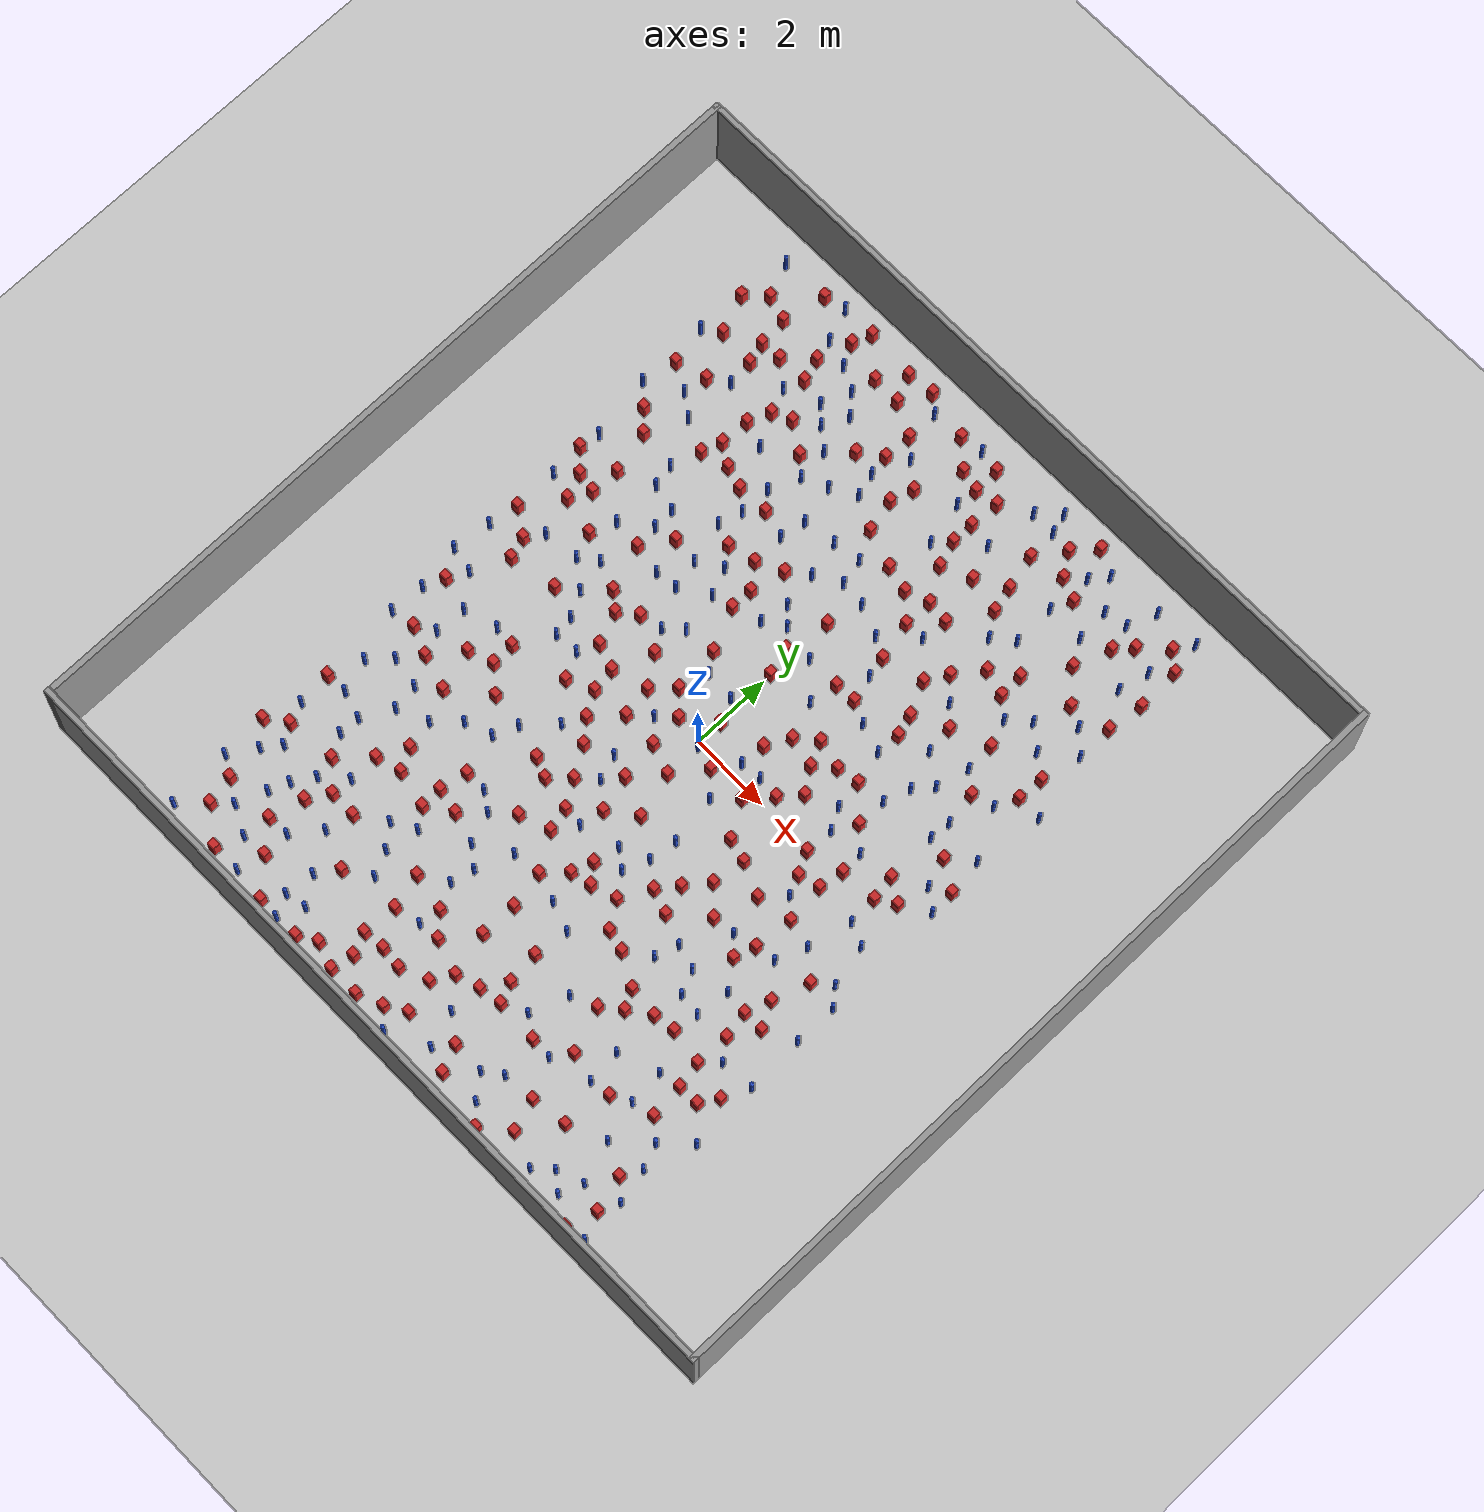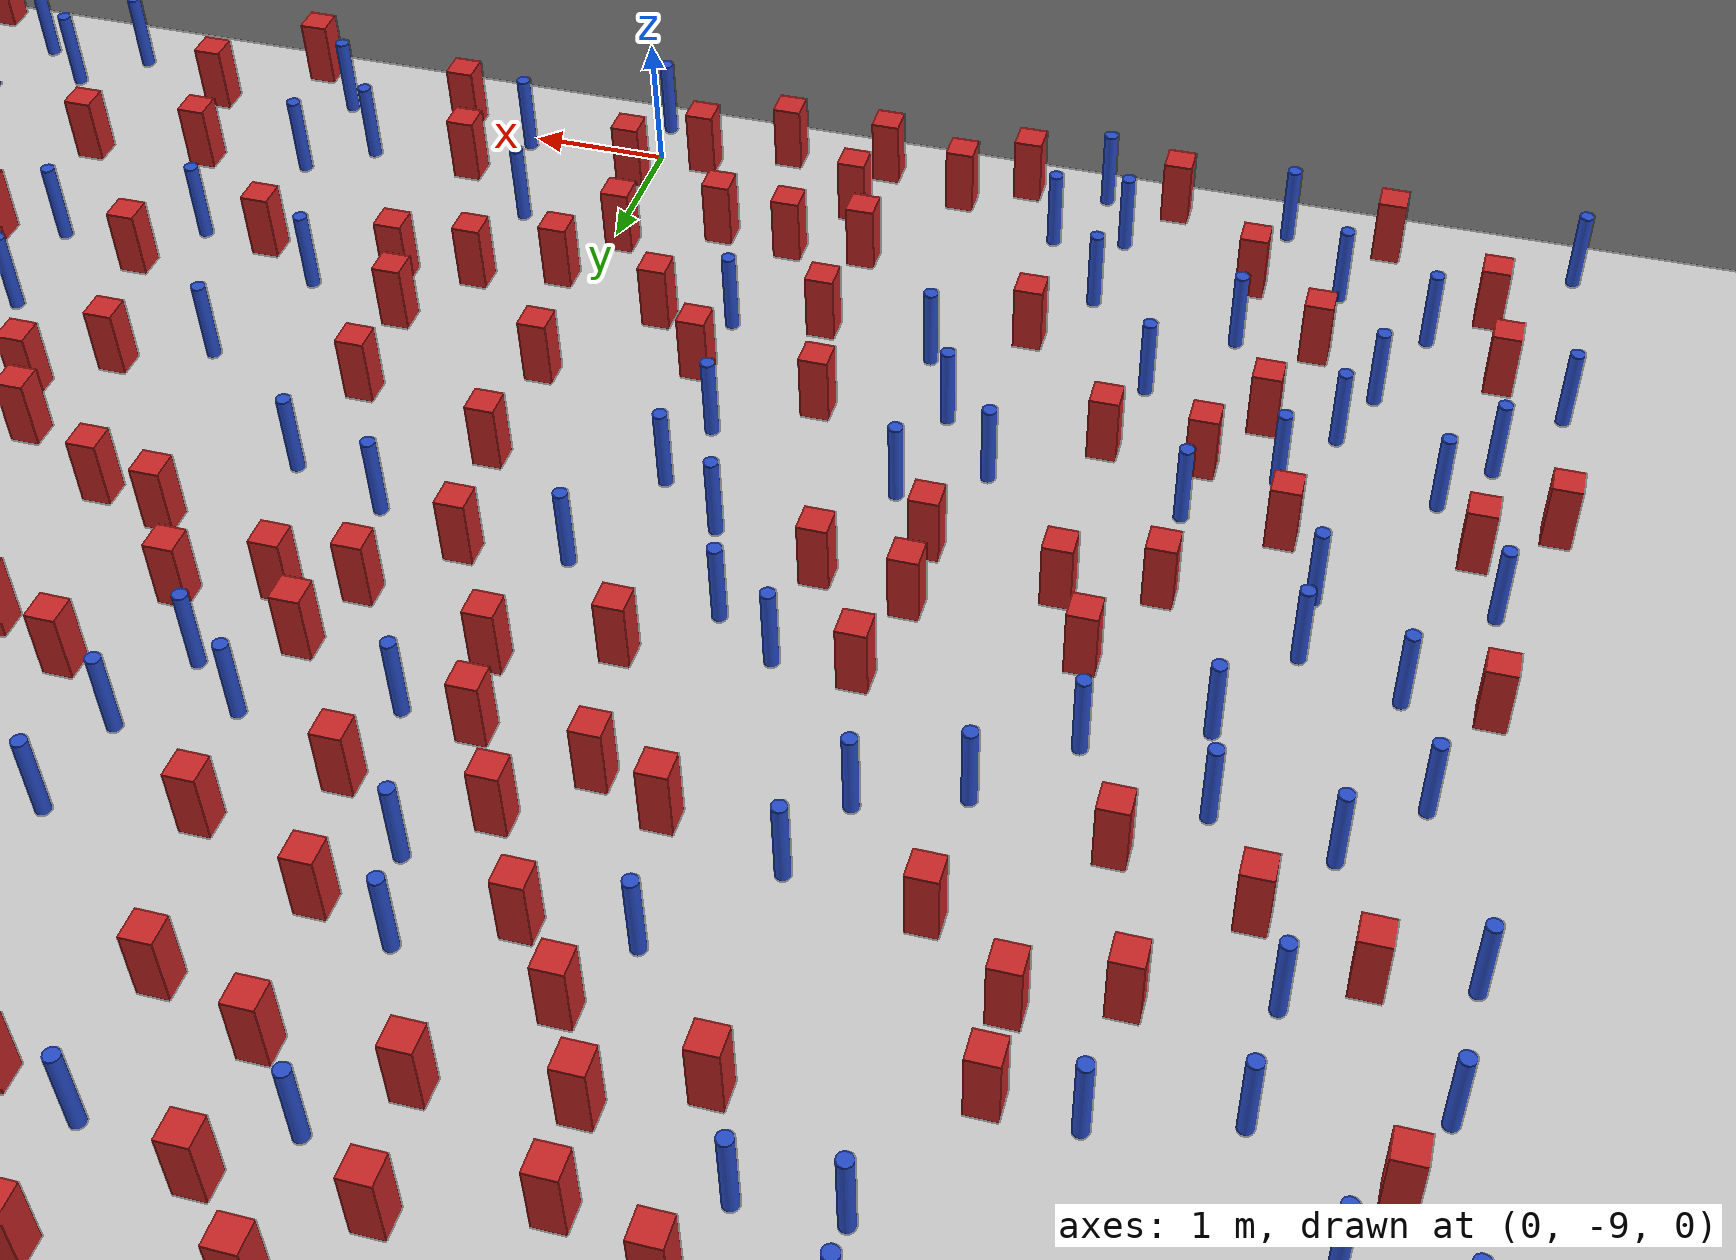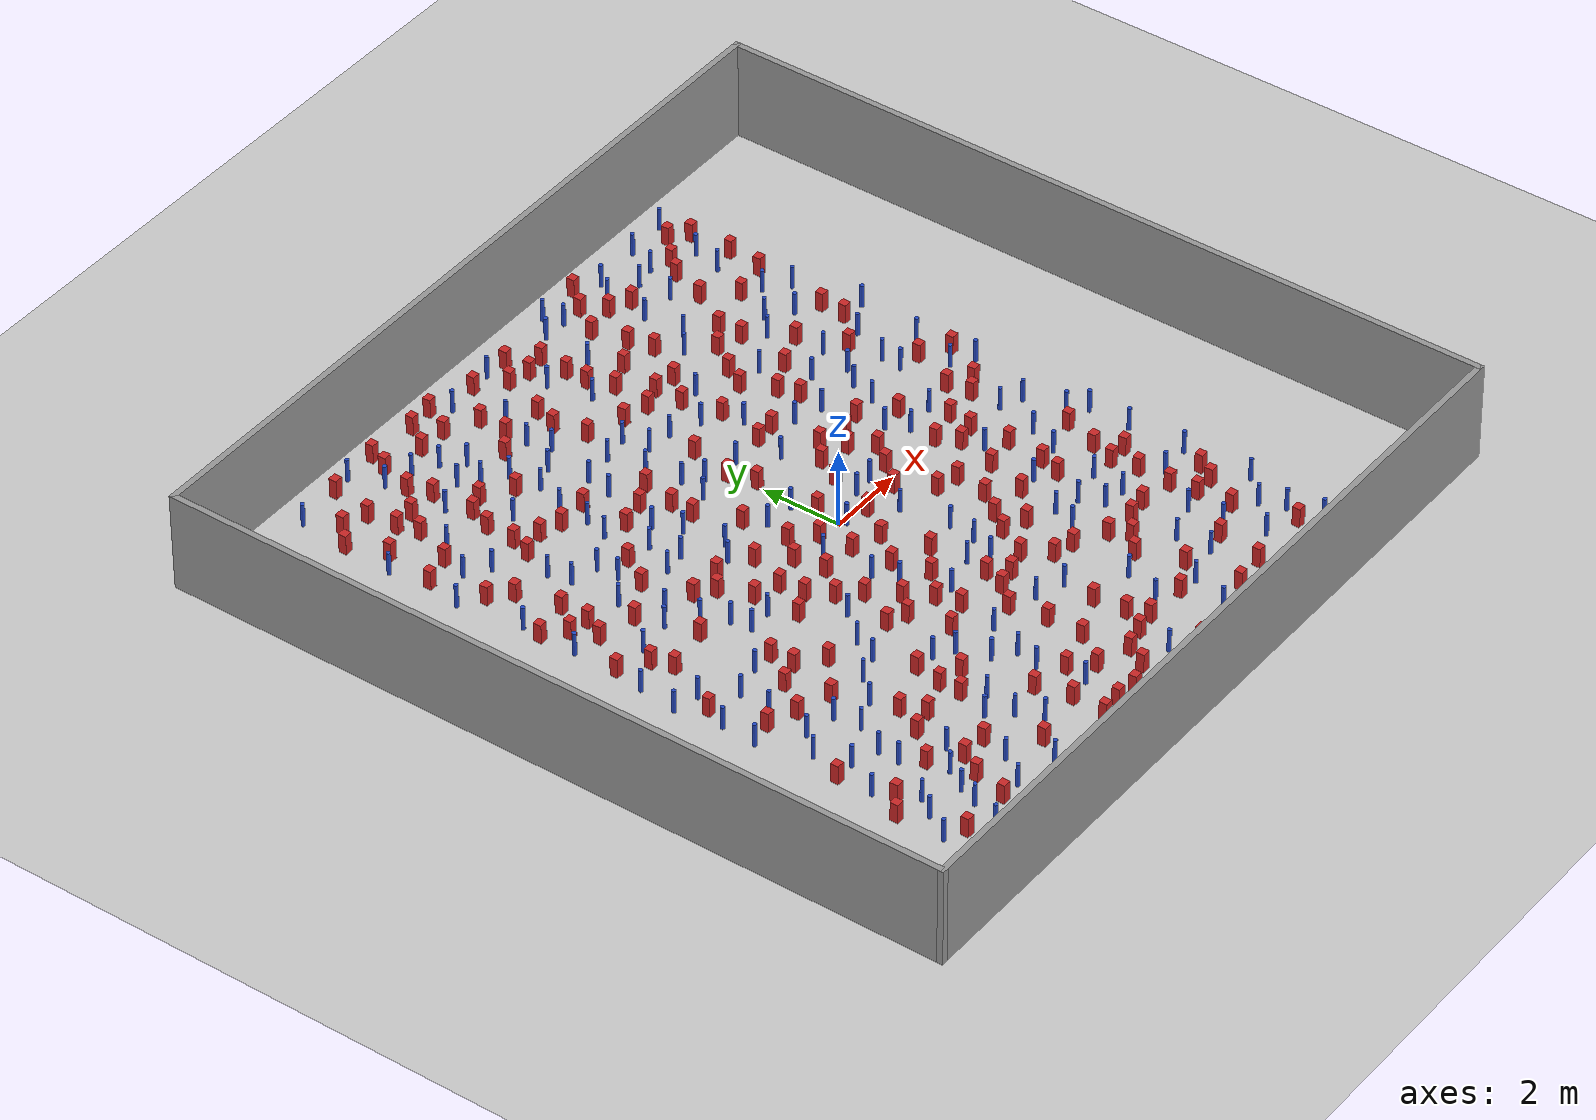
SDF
<sdf version="1.6">
 <world name="default">
  <light name="sun" type="directional">
   <pose>0 0 1000 0 -0 0</pose>
   <diffuse>0.8 0.8 0.8 1</diffuse>
   <specular>0.1 0.1 0.1 1</specular>
   <attenuation>
    <range>1000</range>
    <constant>0.9</constant>
    <linear>0.01</linear>
    <quadratic>0.001</quadratic>
   </attenuation>
   <direction>-0.5 0.5 -1</direction>
  </light>
  <model name="ground_plane">
   <static>1</static>
   <link name="link">
    <collision name="collision">
     <geometry><plane><normal>0 0 1</normal><size>100 100</size></plane></geometry>
     <surface><friction><ode><mu>100</mu><mu2>50</mu2></ode></friction></surface>
    </collision>
    <visual name="visual">
     <cast_shadows>0</cast_shadows>
     <geometry><plane><normal>0 0 1</normal><size>100 100</size></plane></geometry>
     <material>
      <ambient>1.0 1.0 1.0 1.0</ambient>
      <diffuse>0.8 0.8 0.8 1.0</diffuse>
      <specular>0.01 0.01 0.01 1.000000</specular>
     </material>
    </visual>
   </link>
  </model>
  <gravity>0 0 -9.8</gravity>
  <magnetic_field>6e-06 2.3e-05 -4.2e-05</magnetic_field>
  <atmosphere type="adiabatic"/>
  <physics name="default_physics" default="0" type="ode">
   <max_step_size>0.001</max_step_size>
   <real_time_factor>1</real_time_factor>
   <real_time_update_rate>1000</real_time_update_rate>
  </physics>
  <scene><ambient>0.4 0.4 0.4 1</ambient><background>0.7 0.7 0.7 1</background><shadows>1</shadows></scene>
  <spherical_coordinates>
   <surface_model>EARTH_WGS84</surface_model>
   <latitude_deg>0</latitude_deg>
   <longitude_deg>0</longitude_deg>
   <elevation>0</elevation>
   <heading_deg>0</heading_deg>
  </spherical_coordinates>
  <plugin name="gazebo_occupancy_map" filename="libgazebo_2Dmap_plugin.so">
   <map_resolution>0.05</map_resolution>
   <map_topic>generated_map</map_topic>
   <map_height>0.01</map_height>
   <map_size_x>50</map_size_x>
   <map_size_y>50</map_size_y>
  </plugin>
  <model name="NamedLocations">
   <static>true</static>
   <link name="DefaultStart"><pose>8.5 0 0 0 0 3.14</pose></link>
  </model>
  <model name="20x20_walls">
   <pose>0.044518 0.176112 0 0 -0 0</pose>
   <link name="Wall_1">
    <collision name="Wall_1_Collision">
     <geometry><box><size>20 0.15 2.5</size></box></geometry>
     <pose>0 0 1.25 0 -0 0</pose>
    </collision>
    <visual name="Wall_1_Visual">
     <pose>0 0 1.25 0 -0 0</pose>
     <geometry><box><size>20 0.15 2.5</size></box></geometry>
     <material>
      <script><uri>file://media/materials/scripts/gazebo.material</uri><name>Gazebo/Grey</name></script>
      <ambient>0.976471 0.992157 1 1</ambient>
     </material>
     <meta><layer>0</layer></meta>
    </visual>
    <pose>0 9.925 0 0 -0 0</pose>
   </link>
   <link name="Wall_3">
    <collision name="Wall_3_Collision">
     <geometry><box><size>20 0.15 2.5</size></box></geometry>
     <pose>0 0 1.25 0 -0 0</pose>
    </collision>
    <visual name="Wall_3_Visual">
     <pose>0 0 1.25 0 -0 0</pose>
     <geometry><box><size>20 0.15 2.5</size></box></geometry>
     <material>
      <script><uri>file://media/materials/scripts/gazebo.material</uri><name>Gazebo/Grey</name></script>
      <ambient>0.976471 0.992157 1 1</ambient>
     </material>
     <meta><layer>0</layer></meta>
    </visual>
    <pose>9.925 0 0 0 0 -1.5708</pose>
   </link>
   <link name="Wall_4">
    <collision name="Wall_4_Collision">
     <geometry><box><size>20 0.15 2.5</size></box></geometry>
     <pose>0 0 1.25 0 -0 0</pose>
    </collision>
    <visual name="Wall_4_Visual">
     <pose>0 0 1.25 0 -0 0</pose>
     <geometry><box><size>20 0.15 2.5</size></box></geometry>
     <material>
      <script><uri>file://media/materials/scripts/gazebo.material</uri><name>Gazebo/Grey</name></script>
      <ambient>0.976471 0.992157 1 1</ambient>
     </material>
     <meta><layer>0</layer></meta>
    </visual>
    <pose>0 -9.925 0 0 -0 3.14159</pose>
   </link>
   <link name="Wall_5">
    <collision name="Wall_5_Collision">
     <geometry><box><size>20 0.15 2.5</size></box></geometry>
     <pose>0 0 1.25 0 -0 0</pose>
    </collision>
    <visual name="Wall_5_Visual">
     <pose>0 0 1.25 0 -0 0</pose>
     <geometry><box><size>20 0.15 2.5</size></box></geometry>
     <material>
      <script><uri>file://media/materials/scripts/gazebo.material</uri><name>Gazebo/Grey</name></script>
      <ambient>0.976471 0.992157 1 1</ambient>
     </material>
     <meta><layer>0</layer></meta>
    </visual>
    <pose>-9.925 0 0 0 -0 1.5708</pose>
   </link>
   <static>1</static>
  </model>
  <model name="pole_obstacle0">
   <static>true</static>
   <pose>-5.57891861028 5.05401400103 2.88873142074e-08 -9.90536690842e-09 4.60219948965e-07 -1.20965994976e-07</pose>
   <link name="link">
    <pose>0 0 0.3 0 -0 0</pose>
    <inertial>
     <mass>1</mass>
     <inertia><ixx>0.145833</ixx><ixy>0</ixy><ixz>0</ixz><iyy>0.145833</iyy><iyz>0</iyz><izz>0.125</izz></inertia>
    </inertial>
    <collision name="collision">
     <geometry><cylinder><radius>0.05</radius><length>.6</length></cylinder></geometry>
    </collision>
    <visual name="visual">
     <geometry><cylinder><radius>0.05</radius><length>.6</length></cylinder></geometry>
     <material>
      <script><name>Gazebo/Blue</name><uri>file://media/materials/scripts/gazebo.material</uri></script>
     </material>
    </visual>
   </link>
  </model>
  <model name="pole_obstacle1">
   <static>true</static>
   <pose>-3.12867233561 -8.74492226256 2.88873142074e-08 -9.9053668994e-09 4.60219948987e-07 -1.20965994963e-07</pose>
   <link name="link">
    <pose>0 0 0.3 0 -0 0</pose>
    <inertial>
     <mass>1</mass>
     <inertia><ixx>0.145833</ixx><ixy>0</ixy><ixz>0</ixz><iyy>0.145833</iyy><iyz>0</iyz><izz>0.125</izz></inertia>
    </inertial>
    <collision name="collision">
     <geometry><cylinder><radius>0.05</radius><length>.6</length></cylinder></geometry>
    </collision>
    <visual name="visual">
     <geometry><cylinder><radius>0.05</radius><length>.6</length></cylinder></geometry>
     <material>
      <script><name>Gazebo/Blue</name><uri>file://media/materials/scripts/gazebo.material</uri></script>
     </material>
    </visual>
   </link>
  </model>
  <model name="square_post_obstacle0">
   <static>true</static>
   <pose>4.81066511319 7.96962893868 8.22691968438e-08 7.22125133819e-06 -7.54495500217e-07 2.29674213826e-05</pose>
   <link name="link">
    <pose>0 0 0.25 0 -0 0</pose>
    <inertial>
     <mass>100</mass>
     <inertia>
      <ixx>0.166667</ixx>
      <ixy>0</ixy>
      <ixz>0</ixz>
      <iyy>0.166667</iyy>
      <iyz>0</iyz>
      <izz>0.166667</izz>
     </inertia>
    </inertial>
    <collision name="collision"><geometry><box><size>.2 .2 .5</size></box></geometry></collision>
    <visual name="visual">
     <geometry><box><size>.2 .2 .5</size></box></geometry>
     <material>
      <script><name>Gazebo/Red</name><uri>file://media/materials/scripts/gazebo.material</uri></script>
     </material>
    </visual>
   </link>
  </model>
  <model name="square_post_obstacle1">
   <static>true</static>
   <pose>1.34976444259 -7.16266621479 8.22691968438e-08 7.2212513382e-06 -7.54495500217e-07 2.29674213826e-05</pose>
   <link name="link">
    <pose>0 0 0.25 0 -0 0</pose>
    <inertial>
     <mass>100</mass>
     <inertia>
      <ixx>0.166667</ixx>
      <ixy>0</ixy>
      <ixz>0</ixz>
      <iyy>0.166667</iyy>
      <iyz>0</iyz>
      <izz>0.166667</izz>
     </inertia>
    </inertial>
    <collision name="collision"><geometry><box><size>.2 .2 .5</size></box></geometry></collision>
    <visual name="visual">
     <geometry><box><size>.2 .2 .5</size></box></geometry>
     <material>
      <script><name>Gazebo/Red</name><uri>file://media/materials/scripts/gazebo.material</uri></script>
     </material>
    </visual>
   </link>
  </model>
  <model name="pole_obstacle2">
   <static>true</static>
   <pose>-3.64135293143 -8.83523034497 2.88873142074e-08 -9.90536692318e-09 4.6021994893e-07 -1.20965994988e-07</pose>
   <link name="link">
    <pose>0 0 0.3 0 -0 0</pose>
    <inertial>
     <mass>1</mass>
     <inertia><ixx>0.145833</ixx><ixy>0</ixy><ixz>0</ixz><iyy>0.145833</iyy><iyz>0</iyz><izz>0.125</izz></inertia>
    </inertial>
    <collision name="collision">
     <geometry><cylinder><radius>0.05</radius><length>.6</length></cylinder></geometry>
    </collision>
    <visual name="visual">
     <geometry><cylinder><radius>0.05</radius><length>.6</length></cylinder></geometry>
     <material>
      <script><name>Gazebo/Blue</name><uri>file://media/materials/scripts/gazebo.material</uri></script>
     </material>
    </visual>
   </link>
  </model>
  <model name="pole_obstacle3">
   <static>true</static>
   <pose>-5.18515352489 -3.64382817312 2.88873142074e-08 -9.90536690245e-09 4.6021994898e-07 -1.20965994966e-07</pose>
   <link name="link">
    <pose>0 0 0.3 0 -0 0</pose>
    <inertial>
     <mass>1</mass>
     <inertia><ixx>0.145833</ixx><ixy>0</ixy><ixz>0</ixz><iyy>0.145833</iyy><iyz>0</iyz><izz>0.125</izz></inertia>
    </inertial>
    <collision name="collision">
     <geometry><cylinder><radius>0.05</radius><length>.6</length></cylinder></geometry>
    </collision>
    <visual name="visual">
     <geometry><cylinder><radius>0.05</radius><length>.6</length></cylinder></geometry>
     <material>
      <script><name>Gazebo/Blue</name><uri>file://media/materials/scripts/gazebo.material</uri></script>
     </material>
    </visual>
   </link>
  </model>
  <model name="pole_obstacle4">
   <static>true</static>
   <pose>0.0471229709051 -9.3753185863 2.88873142074e-08 -9.90536690996e-09 4.60219948962e-07 -1.20965994979e-07</pose>
   <link name="link">
    <pose>0 0 0.3 0 -0 0</pose>
    <inertial>
     <mass>1</mass>
     <inertia><ixx>0.145833</ixx><ixy>0</ixy><ixz>0</ixz><iyy>0.145833</iyy><iyz>0</iyz><izz>0.125</izz></inertia>
    </inertial>
    <collision name="collision">
     <geometry><cylinder><radius>0.05</radius><length>.6</length></cylinder></geometry>
    </collision>
    <visual name="visual">
     <geometry><cylinder><radius>0.05</radius><length>.6</length></cylinder></geometry>
     <material>
      <script><name>Gazebo/Blue</name><uri>file://media/materials/scripts/gazebo.material</uri></script>
     </material>
    </visual>
   </link>
  </model>
  <model name="pole_obstacle5">
   <static>true</static>
   <pose>-6.9456775595 6.76392135129 2.88873142074e-08 -9.90536690842e-09 4.60219948965e-07 -1.20965994976e-07</pose>
   <link name="link">
    <pose>0 0 0.3 0 -0 0</pose>
    <inertial>
     <mass>1</mass>
     <inertia><ixx>0.145833</ixx><ixy>0</ixy><ixz>0</ixz><iyy>0.145833</iyy><iyz>0</iyz><izz>0.125</izz></inertia>
    </inertial>
    <collision name="collision">
     <geometry><cylinder><radius>0.05</radius><length>.6</length></cylinder></geometry>
    </collision>
    <visual name="visual">
     <geometry><cylinder><radius>0.05</radius><length>.6</length></cylinder></geometry>
     <material>
      <script><name>Gazebo/Blue</name><uri>file://media/materials/scripts/gazebo.material</uri></script>
     </material>
    </visual>
   </link>
  </model>
  <model name="pole_obstacle6">
   <static>true</static>
   <pose>1.34641846792 -1.97543661857 2.88873142074e-08 -9.90536689899e-09 4.60219948988e-07 -1.20965994961e-07</pose>
   <link name="link">
    <pose>0 0 0.3 0 -0 0</pose>
    <inertial>
     <mass>1</mass>
     <inertia><ixx>0.145833</ixx><ixy>0</ixy><ixz>0</ixz><iyy>0.145833</iyy><iyz>0</iyz><izz>0.125</izz></inertia>
    </inertial>
    <collision name="collision">
     <geometry><cylinder><radius>0.05</radius><length>.6</length></cylinder></geometry>
    </collision>
    <visual name="visual">
     <geometry><cylinder><radius>0.05</radius><length>.6</length></cylinder></geometry>
     <material>
      <script><name>Gazebo/Blue</name><uri>file://media/materials/scripts/gazebo.material</uri></script>
     </material>
    </visual>
   </link>
  </model>
  <model name="square_post_obstacle2">
   <static>true</static>
   <pose>0.613346342673 7.25134652475 8.22691968438e-08 7.2212513382e-06 -7.54495500217e-07 2.29674213826e-05</pose>
   <link name="link">
    <pose>0 0 0.25 0 -0 0</pose>
    <inertial>
     <mass>100</mass>
     <inertia>
      <ixx>0.166667</ixx>
      <ixy>0</ixy>
      <ixz>0</ixz>
      <iyy>0.166667</iyy>
      <iyz>0</iyz>
      <izz>0.166667</izz>
     </inertia>
    </inertial>
    <collision name="collision"><geometry><box><size>.2 .2 .5</size></box></geometry></collision>
    <visual name="visual">
     <geometry><box><size>.2 .2 .5</size></box></geometry>
     <material>
      <script><name>Gazebo/Red</name><uri>file://media/materials/scripts/gazebo.material</uri></script>
     </material>
    </visual>
   </link>
  </model>
  <model name="square_post_obstacle3">
   <static>true</static>
   <pose>-6.75841199657 2.84869637535 8.22691968438e-08 7.2212513382e-06 -7.54495500217e-07 2.29674213826e-05</pose>
   <link name="link">
    <pose>0 0 0.25 0 -0 0</pose>
    <inertial>
     <mass>100</mass>
     <inertia>
      <ixx>0.166667</ixx>
      <ixy>0</ixy>
      <ixz>0</ixz>
      <iyy>0.166667</iyy>
      <iyz>0</iyz>
      <izz>0.166667</izz>
     </inertia>
    </inertial>
    <collision name="collision"><geometry><box><size>.2 .2 .5</size></box></geometry></collision>
    <visual name="visual">
     <geometry><box><size>.2 .2 .5</size></box></geometry>
     <material>
      <script><name>Gazebo/Red</name><uri>file://media/materials/scripts/gazebo.material</uri></script>
     </material>
    </visual>
   </link>
  </model>
  <model name="square_post_obstacle4">
   <static>true</static>
   <pose>-3.94886343294 -6.59833227282 8.22691968438e-08 7.22125133819e-06 -7.54495500217e-07 2.29674213826e-05</pose>
   <link name="link">
    <pose>0 0 0.25 0 -0 0</pose>
    <inertial>
     <mass>100</mass>
     <inertia>
      <ixx>0.166667</ixx>
      <ixy>0</ixy>
      <ixz>0</ixz>
      <iyy>0.166667</iyy>
      <iyz>0</iyz>
      <izz>0.166667</izz>
     </inertia>
    </inertial>
    <collision name="collision"><geometry><box><size>.2 .2 .5</size></box></geometry></collision>
    <visual name="visual">
     <geometry><box><size>.2 .2 .5</size></box></geometry>
     <material>
      <script><name>Gazebo/Red</name><uri>file://media/materials/scripts/gazebo.material</uri></script>
     </material>
    </visual>
   </link>
  </model>
  <model name="pole_obstacle7">
   <static>true</static>
   <pose>3.92263139561 -6.95824862448 2.88873142074e-08 -9.90536689859e-09 4.60219948989e-07 -1.20965994961e-07</pose>
   <link name="link">
    <pose>0 0 0.3 0 -0 0</pose>
    <inertial>
     <mass>1</mass>
     <inertia><ixx>0.145833</ixx><ixy>0</ixy><ixz>0</ixz><iyy>0.145833</iyy><iyz>0</iyz><izz>0.125</izz></inertia>
    </inertial>
    <collision name="collision">
     <geometry><cylinder><radius>0.05</radius><length>.6</length></cylinder></geometry>
    </collision>
    <visual name="visual">
     <geometry><cylinder><radius>0.05</radius><length>.6</length></cylinder></geometry>
     <material>
      <script><name>Gazebo/Blue</name><uri>file://media/materials/scripts/gazebo.material</uri></script>
     </material>
    </visual>
   </link>
  </model>
  <model name="pole_obstacle8">
   <static>true</static>
   <pose>6.26670397451 -8.30365633751 2.88873142074e-08 -9.9053668967e-09 4.60219948993e-07 -1.20965994957e-07</pose>
   <link name="link">
    <pose>0 0 0.3 0 -0 0</pose>
    <inertial>
     <mass>1</mass>
     <inertia><ixx>0.145833</ixx><ixy>0</ixy><ixz>0</ixz><iyy>0.145833</iyy><iyz>0</iyz><izz>0.125</izz></inertia>
    </inertial>
    <collision name="collision">
     <geometry><cylinder><radius>0.05</radius><length>.6</length></cylinder></geometry>
    </collision>
    <visual name="visual">
     <geometry><cylinder><radius>0.05</radius><length>.6</length></cylinder></geometry>
     <material>
      <script><name>Gazebo/Blue</name><uri>file://media/materials/scripts/gazebo.material</uri></script>
     </material>
    </visual>
   </link>
  </model>
  <model name="square_post_obstacle5">
   <static>true</static>
   <pose>-6.22401054124 -2.6975874506 8.22691968438e-08 7.2212513382e-06 -7.54495500217e-07 2.29674213826e-05</pose>
   <link name="link">
    <pose>0 0 0.25 0 -0 0</pose>
    <inertial>
     <mass>100</mass>
     <inertia>
      <ixx>0.166667</ixx>
      <ixy>0</ixy>
      <ixz>0</ixz>
      <iyy>0.166667</iyy>
      <iyz>0</iyz>
      <izz>0.166667</izz>
     </inertia>
    </inertial>
    <collision name="collision"><geometry><box><size>.2 .2 .5</size></box></geometry></collision>
    <visual name="visual">
     <geometry><box><size>.2 .2 .5</size></box></geometry>
     <material>
      <script><name>Gazebo/Red</name><uri>file://media/materials/scripts/gazebo.material</uri></script>
     </material>
    </visual>
   </link>
  </model>
  <model name="square_post_obstacle6">
   <static>true</static>
   <pose>1.26814479406 5.86016983149 8.22691968438e-08 7.2212513382e-06 -7.54495500217e-07 2.29674213826e-05</pose>
   <link name="link">
    <pose>0 0 0.25 0 -0 0</pose>
    <inertial>
     <mass>100</mass>
     <inertia>
      <ixx>0.166667</ixx>
      <ixy>0</ixy>
      <ixz>0</ixz>
      <iyy>0.166667</iyy>
      <iyz>0</iyz>
      <izz>0.166667</izz>
     </inertia>
    </inertial>
    <collision name="collision"><geometry><box><size>.2 .2 .5</size></box></geometry></collision>
    <visual name="visual">
     <geometry><box><size>.2 .2 .5</size></box></geometry>
     <material>
      <script><name>Gazebo/Red</name><uri>file://media/materials/scripts/gazebo.material</uri></script>
     </material>
    </visual>
   </link>
  </model>
  <model name="square_post_obstacle7">
   <static>true</static>
   <pose>-0.357960590281 -9.00568446626 8.22691968438e-08 7.22125133819e-06 -7.54495500217e-07 2.29674213826e-05</pose>
   <link name="link">
    <pose>0 0 0.25 0 -0 0</pose>
    <inertial>
     <mass>100</mass>
     <inertia>
      <ixx>0.166667</ixx>
      <ixy>0</ixy>
      <ixz>0</ixz>
      <iyy>0.166667</iyy>
      <iyz>0</iyz>
      <izz>0.166667</izz>
     </inertia>
    </inertial>
    <collision name="collision"><geometry><box><size>.2 .2 .5</size></box></geometry></collision>
    <visual name="visual">
     <geometry><box><size>.2 .2 .5</size></box></geometry>
     <material>
      <script><name>Gazebo/Red</name><uri>file://media/materials/scripts/gazebo.material</uri></script>
     </material>
    </visual>
   </link>
  </model>
  <model name="pole_obstacle9">
   <static>true</static>
   <pose>-1.03282935127 -0.34773533734 2.88873142074e-08 -9.90536689939e-09 4.60219948987e-07 -1.20965994962e-07</pose>
   <link name="link">
    <pose>0 0 0.3 0 -0 0</pose>
    <inertial>
     <mass>1</mass>
     <inertia><ixx>0.145833</ixx><ixy>0</ixy><ixz>0</ixz><iyy>0.145833</iyy><iyz>0</iyz><izz>0.125</izz></inertia>
    </inertial>
    <collision name="collision">
     <geometry><cylinder><radius>0.05</radius><length>.6</length></cylinder></geometry>
    </collision>
    <visual name="visual">
     <geometry><cylinder><radius>0.05</radius><length>.6</length></cylinder></geometry>
     <material>
      <script><name>Gazebo/Blue</name><uri>file://media/materials/scripts/gazebo.material</uri></script>
     </material>
    </visual>
   </link>
  </model>
  <model name="pole_obstacle10">
   <static>true</static>
   <pose>5.80582002486 -0.743763885813 2.88873142074e-08 -9.90536689837e-09 4.60219948989e-07 -1.2096599496e-07</pose>
   <link name="link">
    <pose>0 0 0.3 0 -0 0</pose>
    <inertial>
     <mass>1</mass>
     <inertia><ixx>0.145833</ixx><ixy>0</ixy><ixz>0</ixz><iyy>0.145833</iyy><iyz>0</iyz><izz>0.125</izz></inertia>
    </inertial>
    <collision name="collision">
     <geometry><cylinder><radius>0.05</radius><length>.6</length></cylinder></geometry>
    </collision>
    <visual name="visual">
     <geometry><cylinder><radius>0.05</radius><length>.6</length></cylinder></geometry>
     <material>
      <script><name>Gazebo/Blue</name><uri>file://media/materials/scripts/gazebo.material</uri></script>
     </material>
    </visual>
   </link>
  </model>
  <model name="pole_obstacle11">
   <static>true</static>
   <pose>-4.35559199001 -3.97032147339 2.88873142074e-08 -9.90536690067e-09 4.60219948984e-07 -1.20965994963e-07</pose>
   <link name="link">
    <pose>0 0 0.3 0 -0 0</pose>
    <inertial>
     <mass>1</mass>
     <inertia><ixx>0.145833</ixx><ixy>0</ixy><ixz>0</ixz><iyy>0.145833</iyy><iyz>0</iyz><izz>0.125</izz></inertia>
    </inertial>
    <collision name="collision">
     <geometry><cylinder><radius>0.05</radius><length>.6</length></cylinder></geometry>
    </collision>
    <visual name="visual">
     <geometry><cylinder><radius>0.05</radius><length>.6</length></cylinder></geometry>
     <material>
      <script><name>Gazebo/Blue</name><uri>file://media/materials/scripts/gazebo.material</uri></script>
     </material>
    </visual>
   </link>
  </model>
  <model name="pole_obstacle12">
   <static>true</static>
   <pose>3.22318054179 7.64608850501 2.88873142074e-08 -9.90536689859e-09 4.60219948989e-07 -1.20965994961e-07</pose>
   <link name="link">
    <pose>0 0 0.3 0 -0 0</pose>
    <inertial>
     <mass>1</mass>
     <inertia><ixx>0.145833</ixx><ixy>0</ixy><ixz>0</ixz><iyy>0.145833</iyy><iyz>0</iyz><izz>0.125</izz></inertia>
    </inertial>
    <collision name="collision">
     <geometry><cylinder><radius>0.05</radius><length>.6</length></cylinder></geometry>
    </collision>
    <visual name="visual">
     <geometry><cylinder><radius>0.05</radius><length>.6</length></cylinder></geometry>
     <material>
      <script><name>Gazebo/Blue</name><uri>file://media/materials/scripts/gazebo.material</uri></script>
     </material>
    </visual>
   </link>
  </model>
  <model name="square_post_obstacle8">
   <static>true</static>
   <pose>4.49751720878 7.07438937108 8.22691968438e-08 7.2212513382e-06 -7.54495500217e-07 2.29674213826e-05</pose>
   <link name="link">
    <pose>0 0 0.25 0 -0 0</pose>
    <inertial>
     <mass>100</mass>
     <inertia>
      <ixx>0.166667</ixx>
      <ixy>0</ixy>
      <ixz>0</ixz>
      <iyy>0.166667</iyy>
      <iyz>0</iyz>
      <izz>0.166667</izz>
     </inertia>
    </inertial>
    <collision name="collision"><geometry><box><size>.2 .2 .5</size></box></geometry></collision>
    <visual name="visual">
     <geometry><box><size>.2 .2 .5</size></box></geometry>
     <material>
      <script><name>Gazebo/Red</name><uri>file://media/materials/scripts/gazebo.material</uri></script>
     </material>
    </visual>
   </link>
  </model>
  <model name="square_post_obstacle9">
   <static>true</static>
   <pose>4.55035390656 4.47346086825 8.22691968438e-08 7.2212513382e-06 -7.54495500217e-07 2.29674213826e-05</pose>
   <link name="link">
    <pose>0 0 0.25 0 -0 0</pose>
    <inertial>
     <mass>100</mass>
     <inertia>
      <ixx>0.166667</ixx>
      <ixy>0</ixy>
      <ixz>0</ixz>
      <iyy>0.166667</iyy>
      <iyz>0</iyz>
      <izz>0.166667</izz>
     </inertia>
    </inertial>
    <collision name="collision"><geometry><box><size>.2 .2 .5</size></box></geometry></collision>
    <visual name="visual">
     <geometry><box><size>.2 .2 .5</size></box></geometry>
     <material>
      <script><name>Gazebo/Red</name><uri>file://media/materials/scripts/gazebo.material</uri></script>
     </material>
    </visual>
   </link>
  </model>
  <model name="pole_obstacle13">
   <static>true</static>
   <pose>4.4009780181 -9.17855342326 2.88873142074e-08 -9.9053668967e-09 4.60219948993e-07 -1.20965994957e-07</pose>
   <link name="link">
    <pose>0 0 0.3 0 -0 0</pose>
    <inertial>
     <mass>1</mass>
     <inertia><ixx>0.145833</ixx><ixy>0</ixy><ixz>0</ixz><iyy>0.145833</iyy><iyz>0</iyz><izz>0.125</izz></inertia>
    </inertial>
    <collision name="collision">
     <geometry><cylinder><radius>0.05</radius><length>.6</length></cylinder></geometry>
    </collision>
    <visual name="visual">
     <geometry><cylinder><radius>0.05</radius><length>.6</length></cylinder></geometry>
     <material>
      <script><name>Gazebo/Blue</name><uri>file://media/materials/scripts/gazebo.material</uri></script>
     </material>
    </visual>
   </link>
  </model>
  <model name="square_post_obstacle10">
   <static>true</static>
   <pose>-6.53122453917 7.0693868356 8.22691968438e-08 7.2212513382e-06 -7.54495500217e-07 2.29674213826e-05</pose>
   <link name="link">
    <pose>0 0 0.25 0 -0 0</pose>
    <inertial>
     <mass>100</mass>
     <inertia>
      <ixx>0.166667</ixx>
      <ixy>0</ixy>
      <ixz>0</ixz>
      <iyy>0.166667</iyy>
      <iyz>0</iyz>
      <izz>0.166667</izz>
     </inertia>
    </inertial>
    <collision name="collision"><geometry><box><size>.2 .2 .5</size></box></geometry></collision>
    <visual name="visual">
     <geometry><box><size>.2 .2 .5</size></box></geometry>
     <material>
      <script><name>Gazebo/Red</name><uri>file://media/materials/scripts/gazebo.material</uri></script>
     </material>
    </visual>
   </link>
  </model>
  <model name="square_post_obstacle11">
   <static>true</static>
   <pose>-3.38330933852 0.719082300873 8.22691968438e-08 7.2212513382e-06 -7.54495500217e-07 2.29674213826e-05</pose>
   <link name="link">
    <pose>0 0 0.25 0 -0 0</pose>
    <inertial>
     <mass>100</mass>
     <inertia>
      <ixx>0.166667</ixx>
      <ixy>0</ixy>
      <ixz>0</ixz>
      <iyy>0.166667</iyy>
      <iyz>0</iyz>
      <izz>0.166667</izz>
     </inertia>
    </inertial>
    <collision name="collision"><geometry><box><size>.2 .2 .5</size></box></geometry></collision>
    <visual name="visual">
     <geometry><box><size>.2 .2 .5</size></box></geometry>
     <material>
      <script><name>Gazebo/Red</name><uri>file://media/materials/scripts/gazebo.material</uri></script>
     </material>
    </visual>
   </link>
  </model>
  <model name="pole_obstacle14">
   <static>true</static>
   <pose>5.5681106133 3.5373328224 2.88873142074e-08 -9.90536690245e-09 4.6021994898e-07 -1.20965994966e-07</pose>
   <link name="link">
    <pose>0 0 0.3 0 -0 0</pose>
    <inertial>
     <mass>1</mass>
     <inertia><ixx>0.145833</ixx><ixy>0</ixy><ixz>0</ixz><iyy>0.145833</iyy><iyz>0</iyz><izz>0.125</izz></inertia>
    </inertial>
    <collision name="collision">
     <geometry><cylinder><radius>0.05</radius><length>.6</length></cylinder></geometry>
    </collision>
    <visual name="visual">
     <geometry><cylinder><radius>0.05</radius><length>.6</length></cylinder></geometry>
     <material>
      <script><name>Gazebo/Blue</name><uri>file://media/materials/scripts/gazebo.material</uri></script>
     </material>
    </visual>
   </link>
  </model>
  <model name="pole_obstacle15">
   <static>true</static>
   <pose>4.38528797841 2.95199684706 2.88873142074e-08 -9.90536690245e-09 4.6021994898e-07 -1.20965994966e-07</pose>
   <link name="link">
    <pose>0 0 0.3 0 -0 0</pose>
    <inertial>
     <mass>1</mass>
     <inertia><ixx>0.145833</ixx><ixy>0</ixy><ixz>0</ixz><iyy>0.145833</iyy><iyz>0</iyz><izz>0.125</izz></inertia>
    </inertial>
    <collision name="collision">
     <geometry><cylinder><radius>0.05</radius><length>.6</length></cylinder></geometry>
    </collision>
    <visual name="visual">
     <geometry><cylinder><radius>0.05</radius><length>.6</length></cylinder></geometry>
     <material>
      <script><name>Gazebo/Blue</name><uri>file://media/materials/scripts/gazebo.material</uri></script>
     </material>
    </visual>
   </link>
  </model>
  <model name="square_post_obstacle12">
   <static>true</static>
   <pose>6.15612264318 8.56737205794 8.22691968438e-08 7.22125133819e-06 -7.54495500217e-07 2.29674213826e-05</pose>
   <link name="link">
    <pose>0 0 0.25 0 -0 0</pose>
    <inertial>
     <mass>100</mass>
     <inertia>
      <ixx>0.166667</ixx>
      <ixy>0</ixy>
      <ixz>0</ixz>
      <iyy>0.166667</iyy>
      <iyz>0</iyz>
      <izz>0.166667</izz>
     </inertia>
    </inertial>
    <collision name="collision"><geometry><box><size>.2 .2 .5</size></box></geometry></collision>
    <visual name="visual">
     <geometry><box><size>.2 .2 .5</size></box></geometry>
     <material>
      <script><name>Gazebo/Red</name><uri>file://media/materials/scripts/gazebo.material</uri></script>
     </material>
    </visual>
   </link>
  </model>
  <model name="pole_obstacle16">
   <static>true</static>
   <pose>-6.40002123706 -4.00811593487 2.88873142074e-08 -9.90536690819e-09 4.60219948966e-07 -1.20965994975e-07</pose>
   <link name="link">
    <pose>0 0 0.3 0 -0 0</pose>
    <inertial>
     <mass>1</mass>
     <inertia><ixx>0.145833</ixx><ixy>0</ixy><ixz>0</ixz><iyy>0.145833</iyy><iyz>0</iyz><izz>0.125</izz></inertia>
    </inertial>
    <collision name="collision">
     <geometry><cylinder><radius>0.05</radius><length>.6</length></cylinder></geometry>
    </collision>
    <visual name="visual">
     <geometry><cylinder><radius>0.05</radius><length>.6</length></cylinder></geometry>
     <material>
      <script><name>Gazebo/Blue</name><uri>file://media/materials/scripts/gazebo.material</uri></script>
     </material>
    </visual>
   </link>
  </model>
  <model name="pole_obstacle17">
   <static>true</static>
   <pose>1.5737481239 3.690412965 2.88873142074e-08 -9.90536689791e-09 4.6021994899e-07 -1.20965994959e-07</pose>
   <link name="link">
    <pose>0 0 0.3 0 -0 0</pose>
    <inertial>
     <mass>1</mass>
     <inertia><ixx>0.145833</ixx><ixy>0</ixy><ixz>0</ixz><iyy>0.145833</iyy><iyz>0</iyz><izz>0.125</izz></inertia>
    </inertial>
    <collision name="collision">
     <geometry><cylinder><radius>0.05</radius><length>.6</length></cylinder></geometry>
    </collision>
    <visual name="visual">
     <geometry><cylinder><radius>0.05</radius><length>.6</length></cylinder></geometry>
     <material>
      <script><name>Gazebo/Blue</name><uri>file://media/materials/scripts/gazebo.material</uri></script>
     </material>
    </visual>
   </link>
  </model>
  <model name="square_post_obstacle13">
   <static>true</static>
   <pose>1.11379736712 0.899175267969 8.22691968438e-08 7.2212513382e-06 -7.54495500217e-07 2.29674213826e-05</pose>
   <link name="link">
    <pose>0 0 0.25 0 -0 0</pose>
    <inertial>
     <mass>100</mass>
     <inertia>
      <ixx>0.166667</ixx>
      <ixy>0</ixy>
      <ixz>0</ixz>
      <iyy>0.166667</iyy>
      <iyz>0</iyz>
      <izz>0.166667</izz>
     </inertia>
    </inertial>
    <collision name="collision"><geometry><box><size>.2 .2 .5</size></box></geometry></collision>
    <visual name="visual">
     <geometry><box><size>.2 .2 .5</size></box></geometry>
     <material>
      <script><name>Gazebo/Red</name><uri>file://media/materials/scripts/gazebo.material</uri></script>
     </material>
    </visual>
   </link>
  </model>
  <model name="pole_obstacle18">
   <static>true</static>
   <pose>-2.3167167053 -1.92145715834 2.88873142074e-08 -9.90536689395e-09 4.60219949e-07 -1.20965994953e-07</pose>
   <link name="link">
    <pose>0 0 0.3 0 -0 0</pose>
    <inertial>
     <mass>1</mass>
     <inertia><ixx>0.145833</ixx><ixy>0</ixy><ixz>0</ixz><iyy>0.145833</iyy><iyz>0</iyz><izz>0.125</izz></inertia>
    </inertial>
    <collision name="collision">
     <geometry><cylinder><radius>0.05</radius><length>.6</length></cylinder></geometry>
    </collision>
    <visual name="visual">
     <geometry><cylinder><radius>0.05</radius><length>.6</length></cylinder></geometry>
     <material>
      <script><name>Gazebo/Blue</name><uri>file://media/materials/scripts/gazebo.material</uri></script>
     </material>
    </visual>
   </link>
  </model>
  <model name="square_post_obstacle14">
   <static>true</static>
   <pose>1.64560090452 -0.264269106683 8.22691968438e-08 7.22125133819e-06 -7.54495500217e-07 2.29674213826e-05</pose>
   <link name="link">
    <pose>0 0 0.25 0 -0 0</pose>
    <inertial>
     <mass>100</mass>
     <inertia>
      <ixx>0.166667</ixx>
      <ixy>0</ixy>
      <ixz>0</ixz>
      <iyy>0.166667</iyy>
      <iyz>0</iyz>
      <izz>0.166667</izz>
     </inertia>
    </inertial>
    <collision name="collision"><geometry><box><size>.2 .2 .5</size></box></geometry></collision>
    <visual name="visual">
     <geometry><box><size>.2 .2 .5</size></box></geometry>
     <material>
      <script><name>Gazebo/Red</name><uri>file://media/materials/scripts/gazebo.material</uri></script>
     </material>
    </visual>
   </link>
  </model>
  <model name="pole_obstacle19">
   <static>true</static>
   <pose>-5.90801611379 -8.27726933785 2.88873142074e-08 -9.9053668967e-09 4.60219948993e-07 -1.20965994957e-07</pose>
   <link name="link">
    <pose>0 0 0.3 0 -0 0</pose>
    <inertial>
     <mass>1</mass>
     <inertia><ixx>0.145833</ixx><ixy>0</ixy><ixz>0</ixz><iyy>0.145833</iyy><iyz>0</iyz><izz>0.125</izz></inertia>
    </inertial>
    <collision name="collision">
     <geometry><cylinder><radius>0.05</radius><length>.6</length></cylinder></geometry>
    </collision>
    <visual name="visual">
     <geometry><cylinder><radius>0.05</radius><length>.6</length></cylinder></geometry>
     <material>
      <script><name>Gazebo/Blue</name><uri>file://media/materials/scripts/gazebo.material</uri></script>
     </material>
    </visual>
   </link>
  </model>
  <model name="square_post_obstacle15">
   <static>true</static>
   <pose>-1.22572078398 1.6397507249 8.22691968438e-08 7.2212513382e-06 -7.54495500217e-07 2.29674213826e-05</pose>
   <link name="link">
    <pose>0 0 0.25 0 -0 0</pose>
    <inertial>
     <mass>100</mass>
     <inertia>
      <ixx>0.166667</ixx>
      <ixy>0</ixy>
      <ixz>0</ixz>
      <iyy>0.166667</iyy>
      <iyz>0</iyz>
      <izz>0.166667</izz>
     </inertia>
    </inertial>
    <collision name="collision"><geometry><box><size>.2 .2 .5</size></box></geometry></collision>
    <visual name="visual">
     <geometry><box><size>.2 .2 .5</size></box></geometry>
     <material>
      <script><name>Gazebo/Red</name><uri>file://media/materials/scripts/gazebo.material</uri></script>
     </material>
    </visual>
   </link>
  </model>
  <model name="square_post_obstacle16">
   <static>true</static>
   <pose>-0.161220654232 2.8316874739 8.22691968438e-08 7.2212513382e-06 -7.54495500217e-07 2.29674213826e-05</pose>
   <link name="link">
    <pose>0 0 0.25 0 -0 0</pose>
    <inertial>
     <mass>100</mass>
     <inertia>
      <ixx>0.166667</ixx>
      <ixy>0</ixy>
      <ixz>0</ixz>
      <iyy>0.166667</iyy>
      <iyz>0</iyz>
      <izz>0.166667</izz>
     </inertia>
    </inertial>
    <collision name="collision"><geometry><box><size>.2 .2 .5</size></box></geometry></collision>
    <visual name="visual">
     <geometry><box><size>.2 .2 .5</size></box></geometry>
     <material>
      <script><name>Gazebo/Red</name><uri>file://media/materials/scripts/gazebo.material</uri></script>
     </material>
    </visual>
   </link>
  </model>
  <model name="square_post_obstacle17">
   <static>true</static>
   <pose>5.23929450298 0.213188726177 8.22691968438e-08 7.2212513382e-06 -7.54495500217e-07 2.29674213826e-05</pose>
   <link name="link">
    <pose>0 0 0.25 0 -0 0</pose>
    <inertial>
     <mass>100</mass>
     <inertia>
      <ixx>0.166667</ixx>
      <ixy>0</ixy>
      <ixz>0</ixz>
      <iyy>0.166667</iyy>
      <iyz>0</iyz>
      <izz>0.166667</izz>
     </inertia>
    </inertial>
    <collision name="collision"><geometry><box><size>.2 .2 .5</size></box></geometry></collision>
    <visual name="visual">
     <geometry><box><size>.2 .2 .5</size></box></geometry>
     <material>
      <script><name>Gazebo/Red</name><uri>file://media/materials/scripts/gazebo.material</uri></script>
     </material>
    </visual>
   </link>
  </model>
  <model name="pole_obstacle20">
   <static>true</static>
   <pose>6.03167344364 -1.739237854 2.88873142074e-08 -9.90536689445e-09 4.60219948999e-07 -1.20965994956e-07</pose>
   <link name="link">
    <pose>0 0 0.3 0 -0 0</pose>
    <inertial>
     <mass>1</mass>
     <inertia><ixx>0.145833</ixx><ixy>0</ixy><ixz>0</ixz><iyy>0.145833</iyy><iyz>0</iyz><izz>0.125</izz></inertia>
    </inertial>
    <collision name="collision">
     <geometry><cylinder><radius>0.05</radius><length>.6</length></cylinder></geometry>
    </collision>
    <visual name="visual">
     <geometry><cylinder><radius>0.05</radius><length>.6</length></cylinder></geometry>
     <material>
      <script><name>Gazebo/Blue</name><uri>file://media/materials/scripts/gazebo.material</uri></script>
     </material>
    </visual>
   </link>
  </model>
  <model name="pole_obstacle21">
   <static>true</static>
   <pose>-3.17150857694 -3.19205339714 2.88873142074e-08 -9.90536690232e-09 4.6021994898e-07 -1.20965994968e-07</pose>
   <link name="link">
    <pose>0 0 0.3 0 -0 0</pose>
    <inertial>
     <mass>1</mass>
     <inertia><ixx>0.145833</ixx><ixy>0</ixy><ixz>0</ixz><iyy>0.145833</iyy><iyz>0</iyz><izz>0.125</izz></inertia>
    </inertial>
    <collision name="collision">
     <geometry><cylinder><radius>0.05</radius><length>.6</length></cylinder></geometry>
    </collision>
    <visual name="visual">
     <geometry><cylinder><radius>0.05</radius><length>.6</length></cylinder></geometry>
     <material>
      <script><name>Gazebo/Blue</name><uri>file://media/materials/scripts/gazebo.material</uri></script>
     </material>
    </visual>
   </link>
  </model>
  <model name="pole_obstacle22">
   <static>true</static>
   <pose>5.11384237287 -7.59006557661 2.88873142074e-08 -9.90536690842e-09 4.60219948965e-07 -1.20965994976e-07</pose>
   <link name="link">
    <pose>0 0 0.3 0 -0 0</pose>
    <inertial>
     <mass>1</mass>
     <inertia><ixx>0.145833</ixx><ixy>0</ixy><ixz>0</ixz><iyy>0.145833</iyy><iyz>0</iyz><izz>0.125</izz></inertia>
    </inertial>
    <collision name="collision">
     <geometry><cylinder><radius>0.05</radius><length>.6</length></cylinder></geometry>
    </collision>
    <visual name="visual">
     <geometry><cylinder><radius>0.05</radius><length>.6</length></cylinder></geometry>
     <material>
      <script><name>Gazebo/Blue</name><uri>file://media/materials/scripts/gazebo.material</uri></script>
     </material>
    </visual>
   </link>
  </model>
  <model name="pole_obstacle23">
   <static>true</static>
   <pose>4.80086659203 -8.80640798107 2.88873142074e-08 -9.9053668967e-09 4.60219948993e-07 -1.20965994957e-07</pose>
   <link name="link">
    <pose>0 0 0.3 0 -0 0</pose>
    <inertial>
     <mass>1</mass>
     <inertia><ixx>0.145833</ixx><ixy>0</ixy><ixz>0</ixz><iyy>0.145833</iyy><iyz>0</iyz><izz>0.125</izz></inertia>
    </inertial>
    <collision name="collision">
     <geometry><cylinder><radius>0.05</radius><length>.6</length></cylinder></geometry>
    </collision>
    <visual name="visual">
     <geometry><cylinder><radius>0.05</radius><length>.6</length></cylinder></geometry>
     <material>
      <script><name>Gazebo/Blue</name><uri>file://media/materials/scripts/gazebo.material</uri></script>
     </material>
    </visual>
   </link>
  </model>
  <model name="square_post_obstacle18">
   <static>true</static>
   <pose>6.10811297865 -5.22534100473 8.22691968438e-08 7.2212513382e-06 -7.54495500217e-07 2.29674213826e-05</pose>
   <link name="link">
    <pose>0 0 0.25 0 -0 0</pose>
    <inertial>
     <mass>100</mass>
     <inertia>
      <ixx>0.166667</ixx>
      <ixy>0</ixy>
      <ixz>0</ixz>
      <iyy>0.166667</iyy>
      <iyz>0</iyz>
      <izz>0.166667</izz>
     </inertia>
    </inertial>
    <collision name="collision"><geometry><box><size>.2 .2 .5</size></box></geometry></collision>
    <visual name="visual">
     <geometry><box><size>.2 .2 .5</size></box></geometry>
     <material>
      <script><name>Gazebo/Red</name><uri>file://media/materials/scripts/gazebo.material</uri></script>
     </material>
    </visual>
   </link>
  </model>
  <model name="pole_obstacle24">
   <static>true</static>
   <pose>4.31159911894 0.703843628609 2.88873142074e-08 -9.90536689837e-09 4.60219948989e-07 -1.2096599496e-07</pose>
   <link name="link">
    <pose>0 0 0.3 0 -0 0</pose>
    <inertial>
     <mass>1</mass>
     <inertia><ixx>0.145833</ixx><ixy>0</ixy><ixz>0</ixz><iyy>0.145833</iyy><iyz>0</iyz><izz>0.125</izz></inertia>
    </inertial>
    <collision name="collision">
     <geometry><cylinder><radius>0.05</radius><length>.6</length></cylinder></geometry>
    </collision>
    <visual name="visual">
     <geometry><cylinder><radius>0.05</radius><length>.6</length></cylinder></geometry>
     <material>
      <script><name>Gazebo/Blue</name><uri>file://media/materials/scripts/gazebo.material</uri></script>
     </material>
    </visual>
   </link>
  </model>
  <model name="pole_obstacle25">
   <static>true</static>
   <pose>2.13632343708 -8.49517083925 2.88873142074e-08 -9.90536692318e-09 4.6021994893e-07 -1.20965994988e-07</pose>
   <link name="link">
    <pose>0 0 0.3 0 -0 0</pose>
    <inertial>
     <mass>1</mass>
     <inertia><ixx>0.145833</ixx><ixy>0</ixy><ixz>0</ixz><iyy>0.145833</iyy><iyz>0</iyz><izz>0.125</izz></inertia>
    </inertial>
    <collision name="collision">
     <geometry><cylinder><radius>0.05</radius><length>.6</length></cylinder></geometry>
    </collision>
    <visual name="visual">
     <geometry><cylinder><radius>0.05</radius><length>.6</length></cylinder></geometry>
     <material>
      <script><name>Gazebo/Blue</name><uri>file://media/materials/scripts/gazebo.material</uri></script>
     </material>
    </visual>
   </link>
  </model>
  <model name="pole_obstacle26">
   <static>true</static>
   <pose>-3.11296527063 5.13809794333 2.88873142074e-08 -9.90536689859e-09 4.60219948989e-07 -1.20965994961e-07</pose>
   <link name="link">
    <pose>0 0 0.3 0 -0 0</pose>
    <inertial>
     <mass>1</mass>
     <inertia><ixx>0.145833</ixx><ixy>0</ixy><ixz>0</ixz><iyy>0.145833</iyy><iyz>0</iyz><izz>0.125</izz></inertia>
    </inertial>
    <collision name="collision">
     <geometry><cylinder><radius>0.05</radius><length>.6</length></cylinder></geometry>
    </collision>
    <visual name="visual">
     <geometry><cylinder><radius>0.05</radius><length>.6</length></cylinder></geometry>
     <material>
      <script><name>Gazebo/Blue</name><uri>file://media/materials/scripts/gazebo.material</uri></script>
     </material>
    </visual>
   </link>
  </model>
  <model name="pole_obstacle27">
   <static>true</static>
   <pose>4.74106831965 -2.30007522335 2.88873142074e-08 -9.90536690245e-09 4.6021994898e-07 -1.20965994966e-07</pose>
   <link name="link">
    <pose>0 0 0.3 0 -0 0</pose>
    <inertial>
     <mass>1</mass>
     <inertia><ixx>0.145833</ixx><ixy>0</ixy><ixz>0</ixz><iyy>0.145833</iyy><iyz>0</iyz><izz>0.125</izz></inertia>
    </inertial>
    <collision name="collision">
     <geometry><cylinder><radius>0.05</radius><length>.6</length></cylinder></geometry>
    </collision>
    <visual name="visual">
     <geometry><cylinder><radius>0.05</radius><length>.6</length></cylinder></geometry>
     <material>
      <script><name>Gazebo/Blue</name><uri>file://media/materials/scripts/gazebo.material</uri></script>
     </material>
    </visual>
   </link>
  </model>
  <model name="pole_obstacle28">
   <static>true</static>
   <pose>-6.84868157761 -9.22441285087 2.88873142074e-08 -9.9053668967e-09 4.60219948993e-07 -1.20965994957e-07</pose>
   <link name="link">
    <pose>0 0 0.3 0 -0 0</pose>
    <inertial>
     <mass>1</mass>
     <inertia><ixx>0.145833</ixx><ixy>0</ixy><ixz>0</ixz><iyy>0.145833</iyy><iyz>0</iyz><izz>0.125</izz></inertia>
    </inertial>
    <collision name="collision">
     <geometry><cylinder><radius>0.05</radius><length>.6</length></cylinder></geometry>
    </collision>
    <visual name="visual">
     <geometry><cylinder><radius>0.05</radius><length>.6</length></cylinder></geometry>
     <material>
      <script><name>Gazebo/Blue</name><uri>file://media/materials/scripts/gazebo.material</uri></script>
     </material>
    </visual>
   </link>
  </model>
  <model name="square_post_obstacle19">
   <static>true</static>
   <pose>-4.12237302299 4.8903706107 8.22691968438e-08 7.2212513382e-06 -7.54495500217e-07 2.29674213826e-05</pose>
   <link name="link">
    <pose>0 0 0.25 0 -0 0</pose>
    <inertial>
     <mass>100</mass>
     <inertia>
      <ixx>0.166667</ixx>
      <ixy>0</ixy>
      <ixz>0</ixz>
      <iyy>0.166667</iyy>
      <iyz>0</iyz>
      <izz>0.166667</izz>
     </inertia>
    </inertial>
    <collision name="collision"><geometry><box><size>.2 .2 .5</size></box></geometry></collision>
    <visual name="visual">
     <geometry><box><size>.2 .2 .5</size></box></geometry>
     <material>
      <script><name>Gazebo/Red</name><uri>file://media/materials/scripts/gazebo.material</uri></script>
     </material>
    </visual>
   </link>
  </model>
  <model name="square_post_obstacle20">
   <static>true</static>
   <pose>-0.419759920037 8.596462491 8.22691968438e-08 7.22125133819e-06 -7.54495500217e-07 2.29674213826e-05</pose>
   <link name="link">
    <pose>0 0 0.25 0 -0 0</pose>
    <inertial>
     <mass>100</mass>
     <inertia>
      <ixx>0.166667</ixx>
      <ixy>0</ixy>
      <ixz>0</ixz>
      <iyy>0.166667</iyy>
      <iyz>0</iyz>
      <izz>0.166667</izz>
     </inertia>
    </inertial>
    <collision name="collision"><geometry><box><size>.2 .2 .5</size></box></geometry></collision>
    <visual name="visual">
     <geometry><box><size>.2 .2 .5</size></box></geometry>
     <material>
      <script><name>Gazebo/Red</name><uri>file://media/materials/scripts/gazebo.material</uri></script>
     </material>
    </visual>
   </link>
  </model>
  <model name="pole_obstacle29">
   <static>true</static>
   <pose>-5.77524522382 0.86929448926 2.88873142074e-08 -9.90536689837e-09 4.60219948989e-07 -1.2096599496e-07</pose>
   <link name="link">
    <pose>0 0 0.3 0 -0 0</pose>
    <inertial>
     <mass>1</mass>
     <inertia><ixx>0.145833</ixx><ixy>0</ixy><ixz>0</ixz><iyy>0.145833</iyy><iyz>0</iyz><izz>0.125</izz></inertia>
    </inertial>
    <collision name="collision">
     <geometry><cylinder><radius>0.05</radius><length>.6</length></cylinder></geometry>
    </collision>
    <visual name="visual">
     <geometry><cylinder><radius>0.05</radius><length>.6</length></cylinder></geometry>
     <material>
      <script><name>Gazebo/Blue</name><uri>file://media/materials/scripts/gazebo.material</uri></script>
     </material>
    </visual>
   </link>
  </model>
  <model name="square_post_obstacle21">
   <static>true</static>
   <pose>-5.79454267416 2.32009019014 8.22691968438e-08 7.2212513382e-06 -7.54495500217e-07 2.29674213826e-05</pose>
   <link name="link">
    <pose>0 0 0.25 0 -0 0</pose>
    <inertial>
     <mass>100</mass>
     <inertia>
      <ixx>0.166667</ixx>
      <ixy>0</ixy>
      <ixz>0</ixz>
      <iyy>0.166667</iyy>
      <iyz>0</iyz>
      <izz>0.166667</izz>
     </inertia>
    </inertial>
    <collision name="collision"><geometry><box><size>.2 .2 .5</size></box></geometry></collision>
    <visual name="visual">
     <geometry><box><size>.2 .2 .5</size></box></geometry>
     <material>
      <script><name>Gazebo/Red</name><uri>file://media/materials/scripts/gazebo.material</uri></script>
     </material>
    </visual>
   </link>
  </model>
  <model name="pole_obstacle30">
   <static>true</static>
   <pose>2.88440577546 -4.08760206621 2.88873142074e-08 -9.90536689859e-09 4.60219948989e-07 -1.20965994961e-07</pose>
   <link name="link">
    <pose>0 0 0.3 0 -0 0</pose>
    <inertial>
     <mass>1</mass>
     <inertia><ixx>0.145833</ixx><ixy>0</ixy><ixz>0</ixz><iyy>0.145833</iyy><iyz>0</iyz><izz>0.125</izz></inertia>
    </inertial>
    <collision name="collision">
     <geometry><cylinder><radius>0.05</radius><length>.6</length></cylinder></geometry>
    </collision>
    <visual name="visual">
     <geometry><cylinder><radius>0.05</radius><length>.6</length></cylinder></geometry>
     <material>
      <script><name>Gazebo/Blue</name><uri>file://media/materials/scripts/gazebo.material</uri></script>
     </material>
    </visual>
   </link>
  </model>
  <model name="square_post_obstacle22">
   <static>true</static>
   <pose>-3.22323207701 6.24411409598 8.22691968438e-08 7.2212513382e-06 -7.54495500217e-07 2.29674213826e-05</pose>
   <link name="link">
    <pose>0 0 0.25 0 -0 0</pose>
    <inertial>
     <mass>100</mass>
     <inertia>
      <ixx>0.166667</ixx>
      <ixy>0</ixy>
      <ixz>0</ixz>
      <iyy>0.166667</iyy>
      <iyz>0</iyz>
      <izz>0.166667</izz>
     </inertia>
    </inertial>
    <collision name="collision"><geometry><box><size>.2 .2 .5</size></box></geometry></collision>
    <visual name="visual">
     <geometry><box><size>.2 .2 .5</size></box></geometry>
     <material>
      <script><name>Gazebo/Red</name><uri>file://media/materials/scripts/gazebo.material</uri></script>
     </material>
    </visual>
   </link>
  </model>
  <model name="square_post_obstacle23">
   <static>true</static>
   <pose>-3.20889072496 -7.59951702189 8.22691968438e-08 7.2212513382e-06 -7.54495500217e-07 2.29674213826e-05</pose>
   <link name="link">
    <pose>0 0 0.25 0 -0 0</pose>
    <inertial>
     <mass>100</mass>
     <inertia>
      <ixx>0.166667</ixx>
      <ixy>0</ixy>
      <ixz>0</ixz>
      <iyy>0.166667</iyy>
      <iyz>0</iyz>
      <izz>0.166667</izz>
     </inertia>
    </inertial>
    <collision name="collision"><geometry><box><size>.2 .2 .5</size></box></geometry></collision>
    <visual name="visual">
     <geometry><box><size>.2 .2 .5</size></box></geometry>
     <material>
      <script><name>Gazebo/Red</name><uri>file://media/materials/scripts/gazebo.material</uri></script>
     </material>
    </visual>
   </link>
  </model>
  <model name="pole_obstacle31">
   <static>true</static>
   <pose>-3.29496590169 3.79206971627 2.88873142074e-08 -9.90536689597e-09 4.60219948995e-07 -1.20965994957e-07</pose>
   <link name="link">
    <pose>0 0 0.3 0 -0 0</pose>
    <inertial>
     <mass>1</mass>
     <inertia><ixx>0.145833</ixx><ixy>0</ixy><ixz>0</ixz><iyy>0.145833</iyy><iyz>0</iyz><izz>0.125</izz></inertia>
    </inertial>
    <collision name="collision">
     <geometry><cylinder><radius>0.05</radius><length>.6</length></cylinder></geometry>
    </collision>
    <visual name="visual">
     <geometry><cylinder><radius>0.05</radius><length>.6</length></cylinder></geometry>
     <material>
      <script><name>Gazebo/Blue</name><uri>file://media/materials/scripts/gazebo.material</uri></script>
     </material>
    </visual>
   </link>
  </model>
  <model name="square_post_obstacle24">
   <static>true</static>
   <pose>-5.19579797531 7.54182395175 8.22691968438e-08 7.2212513382e-06 -7.54495500217e-07 2.29674213826e-05</pose>
   <link name="link">
    <pose>0 0 0.25 0 -0 0</pose>
    <inertial>
     <mass>100</mass>
     <inertia>
      <ixx>0.166667</ixx>
      <ixy>0</ixy>
      <ixz>0</ixz>
      <iyy>0.166667</iyy>
      <iyz>0</iyz>
      <izz>0.166667</izz>
     </inertia>
    </inertial>
    <collision name="collision"><geometry><box><size>.2 .2 .5</size></box></geometry></collision>
    <visual name="visual">
     <geometry><box><size>.2 .2 .5</size></box></geometry>
     <material>
      <script><name>Gazebo/Red</name><uri>file://media/materials/scripts/gazebo.material</uri></script>
     </material>
    </visual>
   </link>
  </model>
  <model name="square_post_obstacle25">
   <static>true</static>
   <pose>3.81873314155 -4.985388653 8.22691968438e-08 7.2212513382e-06 -7.54495500217e-07 2.29674213826e-05</pose>
   <link name="link">
    <pose>0 0 0.25 0 -0 0</pose>
    <inertial>
     <mass>100</mass>
     <inertia>
      <ixx>0.166667</ixx>
      <ixy>0</ixy>
      <ixz>0</ixz>
      <iyy>0.166667</iyy>
      <iyz>0</iyz>
      <izz>0.166667</izz>
     </inertia>
    </inertial>
    <collision name="collision"><geometry><box><size>.2 .2 .5</size></box></geometry></collision>
    <visual name="visual">
     <geometry><box><size>.2 .2 .5</size></box></geometry>
     <material>
      <script><name>Gazebo/Red</name><uri>file://media/materials/scripts/gazebo.material</uri></script>
     </material>
    </visual>
   </link>
  </model>
  <model name="square_post_obstacle26">
   <static>true</static>
   <pose>-6.44920168257 4.52247922896 8.22691968438e-08 7.22125133819e-06 -7.54495500217e-07 2.29674213826e-05</pose>
   <link name="link">
    <pose>0 0 0.25 0 -0 0</pose>
    <inertial>
     <mass>100</mass>
     <inertia>
      <ixx>0.166667</ixx>
      <ixy>0</ixy>
      <ixz>0</ixz>
      <iyy>0.166667</iyy>
      <iyz>0</iyz>
      <izz>0.166667</izz>
     </inertia>
    </inertial>
    <collision name="collision"><geometry><box><size>.2 .2 .5</size></box></geometry></collision>
    <visual name="visual">
     <geometry><box><size>.2 .2 .5</size></box></geometry>
     <material>
      <script><name>Gazebo/Red</name><uri>file://media/materials/scripts/gazebo.material</uri></script>
     </material>
    </visual>
   </link>
  </model>
  <model name="pole_obstacle32">
   <static>true</static>
   <pose>-6.94644170509 -0.814503226461 2.88873142074e-08 -9.90536689837e-09 4.60219948989e-07 -1.2096599496e-07</pose>
   <link name="link">
    <pose>0 0 0.3 0 -0 0</pose>
    <inertial>
     <mass>1</mass>
     <inertia><ixx>0.145833</ixx><ixy>0</ixy><ixz>0</ixz><iyy>0.145833</iyy><iyz>0</iyz><izz>0.125</izz></inertia>
    </inertial>
    <collision name="collision">
     <geometry><cylinder><radius>0.05</radius><length>.6</length></cylinder></geometry>
    </collision>
    <visual name="visual">
     <geometry><cylinder><radius>0.05</radius><length>.6</length></cylinder></geometry>
     <material>
      <script><name>Gazebo/Blue</name><uri>file://media/materials/scripts/gazebo.material</uri></script>
     </material>
    </visual>
   </link>
  </model>
  <model name="square_post_obstacle27">
   <static>true</static>
   <pose>-0.969384696367 -9.24757038586 8.22691968438e-08 7.22125133819e-06 -7.54495500217e-07 2.29674213826e-05</pose>
   <link name="link">
    <pose>0 0 0.25 0 -0 0</pose>
    <inertial>
     <mass>100</mass>
     <inertia>
      <ixx>0.166667</ixx>
      <ixy>0</ixy>
      <ixz>0</ixz>
      <iyy>0.166667</iyy>
      <iyz>0</iyz>
      <izz>0.166667</izz>
     </inertia>
    </inertial>
    <collision name="collision"><geometry><box><size>.2 .2 .5</size></box></geometry></collision>
    <visual name="visual">
     <geometry><box><size>.2 .2 .5</size></box></geometry>
     <material>
      <script><name>Gazebo/Red</name><uri>file://media/materials/scripts/gazebo.material</uri></script>
     </material>
    </visual>
   </link>
  </model>
  <model name="square_post_obstacle28">
   <static>true</static>
   <pose>3.63643884922 4.1048677728 8.22691968438e-08 7.2212513382e-06 -7.54495500217e-07 2.29674213826e-05</pose>
   <link name="link">
    <pose>0 0 0.25 0 -0 0</pose>
    <inertial>
     <mass>100</mass>
     <inertia>
      <ixx>0.166667</ixx>
      <ixy>0</ixy>
      <ixz>0</ixz>
      <iyy>0.166667</iyy>
      <iyz>0</iyz>
      <izz>0.166667</izz>
     </inertia>
    </inertial>
    <collision name="collision"><geometry><box><size>.2 .2 .5</size></box></geometry></collision>
    <visual name="visual">
     <geometry><box><size>.2 .2 .5</size></box></geometry>
     <material>
      <script><name>Gazebo/Red</name><uri>file://media/materials/scripts/gazebo.material</uri></script>
     </material>
    </visual>
   </link>
  </model>
  <model name="pole_obstacle33">
   <static>true</static>
   <pose>5.21338102896 -9.13032891597 2.88873142074e-08 -9.9053668967e-09 4.60219948993e-07 -1.20965994957e-07</pose>
   <link name="link">
    <pose>0 0 0.3 0 -0 0</pose>
    <inertial>
     <mass>1</mass>
     <inertia><ixx>0.145833</ixx><ixy>0</ixy><ixz>0</ixz><iyy>0.145833</iyy><iyz>0</iyz><izz>0.125</izz></inertia>
    </inertial>
    <collision name="collision">
     <geometry><cylinder><radius>0.05</radius><length>.6</length></cylinder></geometry>
    </collision>
    <visual name="visual">
     <geometry><cylinder><radius>0.05</radius><length>.6</length></cylinder></geometry>
     <material>
      <script><name>Gazebo/Blue</name><uri>file://media/materials/scripts/gazebo.material</uri></script>
     </material>
    </visual>
   </link>
  </model>
  <model name="pole_obstacle34">
   <static>true</static>
   <pose>-4.91597118742 3.42735828325 2.88873142074e-08 -9.90536690245e-09 4.6021994898e-07 -1.20965994966e-07</pose>
   <link name="link">
    <pose>0 0 0.3 0 -0 0</pose>
    <inertial>
     <mass>1</mass>
     <inertia><ixx>0.145833</ixx><ixy>0</ixy><ixz>0</ixz><iyy>0.145833</iyy><iyz>0</iyz><izz>0.125</izz></inertia>
    </inertial>
    <collision name="collision">
     <geometry><cylinder><radius>0.05</radius><length>.6</length></cylinder></geometry>
    </collision>
    <visual name="visual">
     <geometry><cylinder><radius>0.05</radius><length>.6</length></cylinder></geometry>
     <material>
      <script><name>Gazebo/Blue</name><uri>file://media/materials/scripts/gazebo.material</uri></script>
     </material>
    </visual>
   </link>
  </model>
  <model name="square_post_obstacle29">
   <static>true</static>
   <pose>-0.594315088327 -0.79215371829 8.22691968438e-08 7.2212513382e-06 -7.54495500217e-07 2.29674213826e-05</pose>
   <link name="link">
    <pose>0 0 0.25 0 -0 0</pose>
    <inertial>
     <mass>100</mass>
     <inertia>
      <ixx>0.166667</ixx>
      <ixy>0</ixy>
      <ixz>0</ixz>
      <iyy>0.166667</iyy>
      <iyz>0</iyz>
      <izz>0.166667</izz>
     </inertia>
    </inertial>
    <collision name="collision"><geometry><box><size>.2 .2 .5</size></box></geometry></collision>
    <visual name="visual">
     <geometry><box><size>.2 .2 .5</size></box></geometry>
     <material>
      <script><name>Gazebo/Red</name><uri>file://media/materials/scripts/gazebo.material</uri></script>
     </material>
    </visual>
   </link>
  </model>
  <model name="pole_obstacle35">
   <static>true</static>
   <pose>-5.51759673734 6.32743386519 2.88873142074e-08 -9.90536690842e-09 4.60219948965e-07 -1.20965994976e-07</pose>
   <link name="link">
    <pose>0 0 0.3 0 -0 0</pose>
    <inertial>
     <mass>1</mass>
     <inertia><ixx>0.145833</ixx><ixy>0</ixy><ixz>0</ixz><iyy>0.145833</iyy><iyz>0</iyz><izz>0.125</izz></inertia>
    </inertial>
    <collision name="collision">
     <geometry><cylinder><radius>0.05</radius><length>.6</length></cylinder></geometry>
    </collision>
    <visual name="visual">
     <geometry><cylinder><radius>0.05</radius><length>.6</length></cylinder></geometry>
     <material>
      <script><name>Gazebo/Blue</name><uri>file://media/materials/scripts/gazebo.material</uri></script>
     </material>
    </visual>
   </link>
  </model>
  <model name="square_post_obstacle30">
   <static>true</static>
   <pose>-6.9409519317 -6.51875384566 8.22691968438e-08 7.2212513382e-06 -7.54495500217e-07 2.29674213826e-05</pose>
   <link name="link">
    <pose>0 0 0.25 0 -0 0</pose>
    <inertial>
     <mass>100</mass>
     <inertia>
      <ixx>0.166667</ixx>
      <ixy>0</ixy>
      <ixz>0</ixz>
      <iyy>0.166667</iyy>
      <iyz>0</iyz>
      <izz>0.166667</izz>
     </inertia>
    </inertial>
    <collision name="collision"><geometry><box><size>.2 .2 .5</size></box></geometry></collision>
    <visual name="visual">
     <geometry><box><size>.2 .2 .5</size></box></geometry>
     <material>
      <script><name>Gazebo/Red</name><uri>file://media/materials/scripts/gazebo.material</uri></script>
     </material>
    </visual>
   </link>
  </model>
  <model name="pole_obstacle36">
   <static>true</static>
   <pose>-6.16772446758 -6.61041729582 2.88873142074e-08 -9.90536690842e-09 4.60219948965e-07 -1.20965994976e-07</pose>
   <link name="link">
    <pose>0 0 0.3 0 -0 0</pose>
    <inertial>
     <mass>1</mass>
     <inertia><ixx>0.145833</ixx><ixy>0</ixy><ixz>0</ixz><iyy>0.145833</iyy><iyz>0</iyz><izz>0.125</izz></inertia>
    </inertial>
    <collision name="collision">
     <geometry><cylinder><radius>0.05</radius><length>.6</length></cylinder></geometry>
    </collision>
    <visual name="visual">
     <geometry><cylinder><radius>0.05</radius><length>.6</length></cylinder></geometry>
     <material>
      <script><name>Gazebo/Blue</name><uri>file://media/materials/scripts/gazebo.material</uri></script>
     </material>
    </visual>
   </link>
  </model>
  <model name="pole_obstacle37">
   <static>true</static>
   <pose>3.23446060388 1.11048580937 2.88873142074e-08 -9.90536689395e-09 4.60219949e-07 -1.20965994953e-07</pose>
   <link name="link">
    <pose>0 0 0.3 0 -0 0</pose>
    <inertial>
     <mass>1</mass>
     <inertia><ixx>0.145833</ixx><ixy>0</ixy><ixz>0</ixz><iyy>0.145833</iyy><iyz>0</iyz><izz>0.125</izz></inertia>
    </inertial>
    <collision name="collision">
     <geometry><cylinder><radius>0.05</radius><length>.6</length></cylinder></geometry>
    </collision>
    <visual name="visual">
     <geometry><cylinder><radius>0.05</radius><length>.6</length></cylinder></geometry>
     <material>
      <script><name>Gazebo/Blue</name><uri>file://media/materials/scripts/gazebo.material</uri></script>
     </material>
    </visual>
   </link>
  </model>
  <model name="pole_obstacle38">
   <static>true</static>
   <pose>-1.68911911757 -5.19332564806 2.88873142074e-08 -9.90536689852e-09 4.60219948989e-07 -1.2096599496e-07</pose>
   <link name="link">
    <pose>0 0 0.3 0 -0 0</pose>
    <inertial>
     <mass>1</mass>
     <inertia><ixx>0.145833</ixx><ixy>0</ixy><ixz>0</ixz><iyy>0.145833</iyy><iyz>0</iyz><izz>0.125</izz></inertia>
    </inertial>
    <collision name="collision">
     <geometry><cylinder><radius>0.05</radius><length>.6</length></cylinder></geometry>
    </collision>
    <visual name="visual">
     <geometry><cylinder><radius>0.05</radius><length>.6</length></cylinder></geometry>
     <material>
      <script><name>Gazebo/Blue</name><uri>file://media/materials/scripts/gazebo.material</uri></script>
     </material>
    </visual>
   </link>
  </model>
  <model name="pole_obstacle39">
   <static>true</static>
   <pose>1.76379033655 5.14610116585 2.88873142074e-08 -9.90536689852e-09 4.60219948989e-07 -1.2096599496e-07</pose>
   <link name="link">
    <pose>0 0 0.3 0 -0 0</pose>
    <inertial>
     <mass>1</mass>
     <inertia><ixx>0.145833</ixx><ixy>0</ixy><ixz>0</ixz><iyy>0.145833</iyy><iyz>0</iyz><izz>0.125</izz></inertia>
    </inertial>
    <collision name="collision">
     <geometry><cylinder><radius>0.05</radius><length>.6</length></cylinder></geometry>
    </collision>
    <visual name="visual">
     <geometry><cylinder><radius>0.05</radius><length>.6</length></cylinder></geometry>
     <material>
      <script><name>Gazebo/Blue</name><uri>file://media/materials/scripts/gazebo.material</uri></script>
     </material>
    </visual>
   </link>
  </model>
  <model name="pole_obstacle40">
   <static>true</static>
   <pose>5.43500808425 -8.57817081193 2.88873142074e-08 -9.9053668967e-09 4.60219948993e-07 -1.20965994957e-07</pose>
   <link name="link">
    <pose>0 0 0.3 0 -0 0</pose>
    <inertial>
     <mass>1</mass>
     <inertia><ixx>0.145833</ixx><ixy>0</ixy><ixz>0</ixz><iyy>0.145833</iyy><iyz>0</iyz><izz>0.125</izz></inertia>
    </inertial>
    <collision name="collision">
     <geometry><cylinder><radius>0.05</radius><length>.6</length></cylinder></geometry>
    </collision>
    <visual name="visual">
     <geometry><cylinder><radius>0.05</radius><length>.6</length></cylinder></geometry>
     <material>
      <script><name>Gazebo/Blue</name><uri>file://media/materials/scripts/gazebo.material</uri></script>
     </material>
    </visual>
   </link>
  </model>
  <model name="pole_obstacle41">
   <static>true</static>
   <pose>5.01929388465 -1.57533760443 2.88873142074e-08 -9.90536689445e-09 4.60219948999e-07 -1.20965994956e-07</pose>
   <link name="link">
    <pose>0 0 0.3 0 -0 0</pose>
    <inertial>
     <mass>1</mass>
     <inertia><ixx>0.145833</ixx><ixy>0</ixy><ixz>0</ixz><iyy>0.145833</iyy><iyz>0</iyz><izz>0.125</izz></inertia>
    </inertial>
    <collision name="collision">
     <geometry><cylinder><radius>0.05</radius><length>.6</length></cylinder></geometry>
    </collision>
    <visual name="visual">
     <geometry><cylinder><radius>0.05</radius><length>.6</length></cylinder></geometry>
     <material>
      <script><name>Gazebo/Blue</name><uri>file://media/materials/scripts/gazebo.material</uri></script>
     </material>
    </visual>
   </link>
  </model>
  <model name="pole_obstacle42">
   <static>true</static>
   <pose>5.5778330099 6.15277064663 2.88873142074e-08 -9.90536690842e-09 4.60219948965e-07 -1.20965994976e-07</pose>
   <link name="link">
    <pose>0 0 0.3 0 -0 0</pose>
    <inertial>
     <mass>1</mass>
     <inertia><ixx>0.145833</ixx><ixy>0</ixy><ixz>0</ixz><iyy>0.145833</iyy><iyz>0</iyz><izz>0.125</izz></inertia>
    </inertial>
    <collision name="collision">
     <geometry><cylinder><radius>0.05</radius><length>.6</length></cylinder></geometry>
    </collision>
    <visual name="visual">
     <geometry><cylinder><radius>0.05</radius><length>.6</length></cylinder></geometry>
     <material>
      <script><name>Gazebo/Blue</name><uri>file://media/materials/scripts/gazebo.material</uri></script>
     </material>
    </visual>
   </link>
  </model>
  <model name="square_post_obstacle31">
   <static>true</static>
   <pose>-0.474966905245 -1.75005010223 8.22691968438e-08 7.2212513382e-06 -7.54495500217e-07 2.29674213826e-05</pose>
   <link name="link">
    <pose>0 0 0.25 0 -0 0</pose>
    <inertial>
     <mass>100</mass>
     <inertia>
      <ixx>0.166667</ixx>
      <ixy>0</ixy>
      <ixz>0</ixz>
      <iyy>0.166667</iyy>
      <iyz>0</iyz>
      <izz>0.166667</izz>
     </inertia>
    </inertial>
    <collision name="collision"><geometry><box><size>.2 .2 .5</size></box></geometry></collision>
    <visual name="visual">
     <geometry><box><size>.2 .2 .5</size></box></geometry>
     <material>
      <script><name>Gazebo/Red</name><uri>file://media/materials/scripts/gazebo.material</uri></script>
     </material>
    </visual>
   </link>
  </model>
  <model name="square_post_obstacle32">
   <static>true</static>
   <pose>3.23322665385 -6.78148725426 8.22691968438e-08 7.22125133819e-06 -7.54495500217e-07 2.29674213826e-05</pose>
   <link name="link">
    <pose>0 0 0.25 0 -0 0</pose>
    <inertial>
     <mass>100</mass>
     <inertia>
      <ixx>0.166667</ixx>
      <ixy>0</ixy>
      <ixz>0</ixz>
      <iyy>0.166667</iyy>
      <iyz>0</iyz>
      <izz>0.166667</izz>
     </inertia>
    </inertial>
    <collision name="collision"><geometry><box><size>.2 .2 .5</size></box></geometry></collision>
    <visual name="visual">
     <geometry><box><size>.2 .2 .5</size></box></geometry>
     <material>
      <script><name>Gazebo/Red</name><uri>file://media/materials/scripts/gazebo.material</uri></script>
     </material>
    </visual>
   </link>
  </model>
  <model name="square_post_obstacle33">
   <static>true</static>
   <pose>-2.6142588795 8.70231124438 8.22691968438e-08 7.22125133819e-06 -7.54495500217e-07 2.29674213826e-05</pose>
   <link name="link">
    <pose>0 0 0.25 0 -0 0</pose>
    <inertial>
     <mass>100</mass>
     <inertia>
      <ixx>0.166667</ixx>
      <ixy>0</ixy>
      <ixz>0</ixz>
      <iyy>0.166667</iyy>
      <iyz>0</iyz>
      <izz>0.166667</izz>
     </inertia>
    </inertial>
    <collision name="collision"><geometry><box><size>.2 .2 .5</size></box></geometry></collision>
    <visual name="visual">
     <geometry><box><size>.2 .2 .5</size></box></geometry>
     <material>
      <script><name>Gazebo/Red</name><uri>file://media/materials/scripts/gazebo.material</uri></script>
     </material>
    </visual>
   </link>
  </model>
  <model name="square_post_obstacle34">
   <static>true</static>
   <pose>4.07631354166 -2.87549634228 8.22691968438e-08 7.2212513382e-06 -7.54495500217e-07 2.29674213826e-05</pose>
   <link name="link">
    <pose>0 0 0.25 0 -0 0</pose>
    <inertial>
     <mass>100</mass>
     <inertia>
      <ixx>0.166667</ixx>
      <ixy>0</ixy>
      <ixz>0</ixz>
      <iyy>0.166667</iyy>
      <iyz>0</iyz>
      <izz>0.166667</izz>
     </inertia>
    </inertial>
    <collision name="collision"><geometry><box><size>.2 .2 .5</size></box></geometry></collision>
    <visual name="visual">
     <geometry><box><size>.2 .2 .5</size></box></geometry>
     <material>
      <script><name>Gazebo/Red</name><uri>file://media/materials/scripts/gazebo.material</uri></script>
     </material>
    </visual>
   </link>
  </model>
  <model name="pole_obstacle43">
   <static>true</static>
   <pose>-4.72144073114 8.64065696206 2.88873142074e-08 -9.9053668967e-09 4.60219948993e-07 -1.20965994957e-07</pose>
   <link name="link">
    <pose>0 0 0.3 0 -0 0</pose>
    <inertial>
     <mass>1</mass>
     <inertia><ixx>0.145833</ixx><ixy>0</ixy><ixz>0</ixz><iyy>0.145833</iyy><iyz>0</iyz><izz>0.125</izz></inertia>
    </inertial>
    <collision name="collision">
     <geometry><cylinder><radius>0.05</radius><length>.6</length></cylinder></geometry>
    </collision>
    <visual name="visual">
     <geometry><cylinder><radius>0.05</radius><length>.6</length></cylinder></geometry>
     <material>
      <script><name>Gazebo/Blue</name><uri>file://media/materials/scripts/gazebo.material</uri></script>
     </material>
    </visual>
   </link>
  </model>
  <model name="pole_obstacle44">
   <static>true</static>
   <pose>-6.48443075153 -7.03172573249 2.88873142074e-08 -9.90536690842e-09 4.60219948965e-07 -1.20965994976e-07</pose>
   <link name="link">
    <pose>0 0 0.3 0 -0 0</pose>
    <inertial>
     <mass>1</mass>
     <inertia><ixx>0.145833</ixx><ixy>0</ixy><ixz>0</ixz><iyy>0.145833</iyy><iyz>0</iyz><izz>0.125</izz></inertia>
    </inertial>
    <collision name="collision">
     <geometry><cylinder><radius>0.05</radius><length>.6</length></cylinder></geometry>
    </collision>
    <visual name="visual">
     <geometry><cylinder><radius>0.05</radius><length>.6</length></cylinder></geometry>
     <material>
      <script><name>Gazebo/Blue</name><uri>file://media/materials/scripts/gazebo.material</uri></script>
     </material>
    </visual>
   </link>
  </model>
  <model name="pole_obstacle45">
   <static>true</static>
   <pose>2.01332987493 8.97232441022 2.88873142074e-08 -9.90536692041e-09 4.60219948937e-07 -1.20965994983e-07</pose>
   <link name="link">
    <pose>0 0 0.3 0 -0 0</pose>
    <inertial>
     <mass>1</mass>
     <inertia><ixx>0.145833</ixx><ixy>0</ixy><ixz>0</ixz><iyy>0.145833</iyy><iyz>0</iyz><izz>0.125</izz></inertia>
    </inertial>
    <collision name="collision">
     <geometry><cylinder><radius>0.05</radius><length>.6</length></cylinder></geometry>
    </collision>
    <visual name="visual">
     <geometry><cylinder><radius>0.05</radius><length>.6</length></cylinder></geometry>
     <material>
      <script><name>Gazebo/Blue</name><uri>file://media/materials/scripts/gazebo.material</uri></script>
     </material>
    </visual>
   </link>
  </model>
  <model name="square_post_obstacle35">
   <static>true</static>
   <pose>1.41769313077 1.48172580425 8.22691968438e-08 7.2212513382e-06 -7.54495500217e-07 2.29674213826e-05</pose>
   <link name="link">
    <pose>0 0 0.25 0 -0 0</pose>
    <inertial>
     <mass>100</mass>
     <inertia>
      <ixx>0.166667</ixx>
      <ixy>0</ixy>
      <ixz>0</ixz>
      <iyy>0.166667</iyy>
      <iyz>0</iyz>
      <izz>0.166667</izz>
     </inertia>
    </inertial>
    <collision name="collision"><geometry><box><size>.2 .2 .5</size></box></geometry></collision>
    <visual name="visual">
     <geometry><box><size>.2 .2 .5</size></box></geometry>
     <material>
      <script><name>Gazebo/Red</name><uri>file://media/materials/scripts/gazebo.material</uri></script>
     </material>
    </visual>
   </link>
  </model>
  <model name="pole_obstacle46">
   <static>true</static>
   <pose>3.06816379555 -3.53167319148 2.88873142074e-08 -9.90536690232e-09 4.6021994898e-07 -1.20965994968e-07</pose>
   <link name="link">
    <pose>0 0 0.3 0 -0 0</pose>
    <inertial>
     <mass>1</mass>
     <inertia><ixx>0.145833</ixx><ixy>0</ixy><ixz>0</ixz><iyy>0.145833</iyy><iyz>0</iyz><izz>0.125</izz></inertia>
    </inertial>
    <collision name="collision">
     <geometry><cylinder><radius>0.05</radius><length>.6</length></cylinder></geometry>
    </collision>
    <visual name="visual">
     <geometry><cylinder><radius>0.05</radius><length>.6</length></cylinder></geometry>
     <material>
      <script><name>Gazebo/Blue</name><uri>file://media/materials/scripts/gazebo.material</uri></script>
     </material>
    </visual>
   </link>
  </model>
  <model name="pole_obstacle47">
   <static>true</static>
   <pose>-5.02357856834 9.43363360993 2.88873142074e-08 -9.9053668967e-09 4.60219948993e-07 -1.20965994957e-07</pose>
   <link name="link">
    <pose>0 0 0.3 0 -0 0</pose>
    <inertial>
     <mass>1</mass>
     <inertia><ixx>0.145833</ixx><ixy>0</ixy><ixz>0</ixz><iyy>0.145833</iyy><iyz>0</iyz><izz>0.125</izz></inertia>
    </inertial>
    <collision name="collision">
     <geometry><cylinder><radius>0.05</radius><length>.6</length></cylinder></geometry>
    </collision>
    <visual name="visual">
     <geometry><cylinder><radius>0.05</radius><length>.6</length></cylinder></geometry>
     <material>
      <script><name>Gazebo/Blue</name><uri>file://media/materials/scripts/gazebo.material</uri></script>
     </material>
    </visual>
   </link>
  </model>
  <model name="square_post_obstacle36">
   <static>true</static>
   <pose>5.32274232376 -2.96270476797 8.22691968438e-08 7.2212513382e-06 -7.54495500217e-07 2.29674213826e-05</pose>
   <link name="link">
    <pose>0 0 0.25 0 -0 0</pose>
    <inertial>
     <mass>100</mass>
     <inertia>
      <ixx>0.166667</ixx>
      <ixy>0</ixy>
      <ixz>0</ixz>
      <iyy>0.166667</iyy>
      <iyz>0</iyz>
      <izz>0.166667</izz>
     </inertia>
    </inertial>
    <collision name="collision"><geometry><box><size>.2 .2 .5</size></box></geometry></collision>
    <visual name="visual">
     <geometry><box><size>.2 .2 .5</size></box></geometry>
     <material>
      <script><name>Gazebo/Red</name><uri>file://media/materials/scripts/gazebo.material</uri></script>
     </material>
    </visual>
   </link>
  </model>
  <model name="square_post_obstacle37">
   <static>true</static>
   <pose>3.46657610358 -1.55949613198 8.22691968438e-08 7.2212513382e-06 -7.54495500217e-07 2.29674213826e-05</pose>
   <link name="link">
    <pose>0 0 0.25 0 -0 0</pose>
    <inertial>
     <mass>100</mass>
     <inertia>
      <ixx>0.166667</ixx>
      <ixy>0</ixy>
      <ixz>0</ixz>
      <iyy>0.166667</iyy>
      <iyz>0</iyz>
      <izz>0.166667</izz>
     </inertia>
    </inertial>
    <collision name="collision"><geometry><box><size>.2 .2 .5</size></box></geometry></collision>
    <visual name="visual">
     <geometry><box><size>.2 .2 .5</size></box></geometry>
     <material>
      <script><name>Gazebo/Red</name><uri>file://media/materials/scripts/gazebo.material</uri></script>
     </material>
    </visual>
   </link>
  </model>
  <model name="pole_obstacle48">
   <static>true</static>
   <pose>1.00786192687 4.43440262708 2.88873142074e-08 -9.90536689905e-09 4.60219948988e-07 -1.20965994961e-07</pose>
   <link name="link">
    <pose>0 0 0.3 0 -0 0</pose>
    <inertial>
     <mass>1</mass>
     <inertia><ixx>0.145833</ixx><ixy>0</ixy><ixz>0</ixz><iyy>0.145833</iyy><iyz>0</iyz><izz>0.125</izz></inertia>
    </inertial>
    <collision name="collision">
     <geometry><cylinder><radius>0.05</radius><length>.6</length></cylinder></geometry>
    </collision>
    <visual name="visual">
     <geometry><cylinder><radius>0.05</radius><length>.6</length></cylinder></geometry>
     <material>
      <script><name>Gazebo/Blue</name><uri>file://media/materials/scripts/gazebo.material</uri></script>
     </material>
    </visual>
   </link>
  </model>
  <model name="square_post_obstacle38">
   <static>true</static>
   <pose>6.18678559936 7.49544702307 8.22691968438e-08 7.2212513382e-06 -7.54495500217e-07 2.29674213826e-05</pose>
   <link name="link">
    <pose>0 0 0.25 0 -0 0</pose>
    <inertial>
     <mass>100</mass>
     <inertia>
      <ixx>0.166667</ixx>
      <ixy>0</ixy>
      <ixz>0</ixz>
      <iyy>0.166667</iyy>
      <iyz>0</iyz>
      <izz>0.166667</izz>
     </inertia>
    </inertial>
    <collision name="collision"><geometry><box><size>.2 .2 .5</size></box></geometry></collision>
    <visual name="visual">
     <geometry><box><size>.2 .2 .5</size></box></geometry>
     <material>
      <script><name>Gazebo/Red</name><uri>file://media/materials/scripts/gazebo.material</uri></script>
     </material>
    </visual>
   </link>
  </model>
  <model name="square_post_obstacle39">
   <static>true</static>
   <pose>-0.0275031125796 -5.48431658548 8.22691968438e-08 7.22125133819e-06 -7.54495500217e-07 2.29674213826e-05</pose>
   <link name="link">
    <pose>0 0 0.25 0 -0 0</pose>
    <inertial>
     <mass>100</mass>
     <inertia>
      <ixx>0.166667</ixx>
      <ixy>0</ixy>
      <ixz>0</ixz>
      <iyy>0.166667</iyy>
      <iyz>0</iyz>
      <izz>0.166667</izz>
     </inertia>
    </inertial>
    <collision name="collision"><geometry><box><size>.2 .2 .5</size></box></geometry></collision>
    <visual name="visual">
     <geometry><box><size>.2 .2 .5</size></box></geometry>
     <material>
      <script><name>Gazebo/Red</name><uri>file://media/materials/scripts/gazebo.material</uri></script>
     </material>
    </visual>
   </link>
  </model>
  <model name="pole_obstacle49">
   <static>true</static>
   <pose>-5.24488563336 -8.61744730685 2.88873142074e-08 -9.9053668967e-09 4.60219948993e-07 -1.20965994957e-07</pose>
   <link name="link">
    <pose>0 0 0.3 0 -0 0</pose>
    <inertial>
     <mass>1</mass>
     <inertia><ixx>0.145833</ixx><ixy>0</ixy><ixz>0</ixz><iyy>0.145833</iyy><iyz>0</iyz><izz>0.125</izz></inertia>
    </inertial>
    <collision name="collision">
     <geometry><cylinder><radius>0.05</radius><length>.6</length></cylinder></geometry>
    </collision>
    <visual name="visual">
     <geometry><cylinder><radius>0.05</radius><length>.6</length></cylinder></geometry>
     <material>
      <script><name>Gazebo/Blue</name><uri>file://media/materials/scripts/gazebo.material</uri></script>
     </material>
    </visual>
   </link>
  </model>
  <model name="pole_obstacle50">
   <static>true</static>
   <pose>-0.994300283929 -1.58828671017 2.88873142074e-08 -9.90536689826e-09 4.6021994899e-07 -1.20965994961e-07</pose>
   <link name="link">
    <pose>0 0 0.3 0 -0 0</pose>
    <inertial>
     <mass>1</mass>
     <inertia><ixx>0.145833</ixx><ixy>0</ixy><ixz>0</ixz><iyy>0.145833</iyy><iyz>0</iyz><izz>0.125</izz></inertia>
    </inertial>
    <collision name="collision">
     <geometry><cylinder><radius>0.05</radius><length>.6</length></cylinder></geometry>
    </collision>
    <visual name="visual">
     <geometry><cylinder><radius>0.05</radius><length>.6</length></cylinder></geometry>
     <material>
      <script><name>Gazebo/Blue</name><uri>file://media/materials/scripts/gazebo.material</uri></script>
     </material>
    </visual>
   </link>
  </model>
  <model name="pole_obstacle51">
   <static>true</static>
   <pose>-0.870614898008 -4.68148994331 2.88873142074e-08 -9.90536689661e-09 4.60219948993e-07 -1.20965994957e-07</pose>
   <link name="link">
    <pose>0 0 0.3 0 -0 0</pose>
    <inertial>
     <mass>1</mass>
     <inertia><ixx>0.145833</ixx><ixy>0</ixy><ixz>0</ixz><iyy>0.145833</iyy><iyz>0</iyz><izz>0.125</izz></inertia>
    </inertial>
    <collision name="collision">
     <geometry><cylinder><radius>0.05</radius><length>.6</length></cylinder></geometry>
    </collision>
    <visual name="visual">
     <geometry><cylinder><radius>0.05</radius><length>.6</length></cylinder></geometry>
     <material>
      <script><name>Gazebo/Blue</name><uri>file://media/materials/scripts/gazebo.material</uri></script>
     </material>
    </visual>
   </link>
  </model>
  <model name="pole_obstacle52">
   <static>true</static>
   <pose>4.45046576271 -4.32073719949 2.88873142074e-08 -9.90536690842e-09 4.60219948965e-07 -1.20965994976e-07</pose>
   <link name="link">
    <pose>0 0 0.3 0 -0 0</pose>
    <inertial>
     <mass>1</mass>
     <inertia><ixx>0.145833</ixx><ixy>0</ixy><ixz>0</ixz><iyy>0.145833</iyy><iyz>0</iyz><izz>0.125</izz></inertia>
    </inertial>
    <collision name="collision">
     <geometry><cylinder><radius>0.05</radius><length>.6</length></cylinder></geometry>
    </collision>
    <visual name="visual">
     <geometry><cylinder><radius>0.05</radius><length>.6</length></cylinder></geometry>
     <material>
      <script><name>Gazebo/Blue</name><uri>file://media/materials/scripts/gazebo.material</uri></script>
     </material>
    </visual>
   </link>
  </model>
  <model name="pole_obstacle53">
   <static>true</static>
   <pose>-2.44733559677 3.15941907031 2.88873142074e-08 -9.90536690232e-09 4.6021994898e-07 -1.20965994968e-07</pose>
   <link name="link">
    <pose>0 0 0.3 0 -0 0</pose>
    <inertial>
     <mass>1</mass>
     <inertia><ixx>0.145833</ixx><ixy>0</ixy><ixz>0</ixz><iyy>0.145833</iyy><iyz>0</iyz><izz>0.125</izz></inertia>
    </inertial>
    <collision name="collision">
     <geometry><cylinder><radius>0.05</radius><length>.6</length></cylinder></geometry>
    </collision>
    <visual name="visual">
     <geometry><cylinder><radius>0.05</radius><length>.6</length></cylinder></geometry>
     <material>
      <script><name>Gazebo/Blue</name><uri>file://media/materials/scripts/gazebo.material</uri></script>
     </material>
    </visual>
   </link>
  </model>
  <model name="square_post_obstacle40">
   <static>true</static>
   <pose>3.58850300028 -8.86359649826 8.22691968438e-08 7.22125133819e-06 -7.54495500217e-07 2.29674213826e-05</pose>
   <link name="link">
    <pose>0 0 0.25 0 -0 0</pose>
    <inertial>
     <mass>100</mass>
     <inertia>
      <ixx>0.166667</ixx>
      <ixy>0</ixy>
      <ixz>0</ixz>
      <iyy>0.166667</iyy>
      <iyz>0</iyz>
      <izz>0.166667</izz>
     </inertia>
    </inertial>
    <collision name="collision"><geometry><box><size>.2 .2 .5</size></box></geometry></collision>
    <visual name="visual">
     <geometry><box><size>.2 .2 .5</size></box></geometry>
     <material>
      <script><name>Gazebo/Red</name><uri>file://media/materials/scripts/gazebo.material</uri></script>
     </material>
    </visual>
   </link>
  </model>
  <model name="pole_obstacle54">
   <static>true</static>
   <pose>-3.76575025793 7.42224762915 2.88873142074e-08 -9.90536689859e-09 4.60219948989e-07 -1.20965994961e-07</pose>
   <link name="link">
    <pose>0 0 0.3 0 -0 0</pose>
    <inertial>
     <mass>1</mass>
     <inertia><ixx>0.145833</ixx><ixy>0</ixy><ixz>0</ixz><iyy>0.145833</iyy><iyz>0</iyz><izz>0.125</izz></inertia>
    </inertial>
    <collision name="collision">
     <geometry><cylinder><radius>0.05</radius><length>.6</length></cylinder></geometry>
    </collision>
    <visual name="visual">
     <geometry><cylinder><radius>0.05</radius><length>.6</length></cylinder></geometry>
     <material>
      <script><name>Gazebo/Blue</name><uri>file://media/materials/scripts/gazebo.material</uri></script>
     </material>
    </visual>
   </link>
  </model>
  <model name="square_post_obstacle41">
   <static>true</static>
   <pose>-6.01156486565 4.09463652384 8.22691968438e-08 7.22125133819e-06 -7.54495500217e-07 2.29674213826e-05</pose>
   <link name="link">
    <pose>0 0 0.25 0 -0 0</pose>
    <inertial>
     <mass>100</mass>
     <inertia>
      <ixx>0.166667</ixx>
      <ixy>0</ixy>
      <ixz>0</ixz>
      <iyy>0.166667</iyy>
      <iyz>0</iyz>
      <izz>0.166667</izz>
     </inertia>
    </inertial>
    <collision name="collision"><geometry><box><size>.2 .2 .5</size></box></geometry></collision>
    <visual name="visual">
     <geometry><box><size>.2 .2 .5</size></box></geometry>
     <material>
      <script><name>Gazebo/Red</name><uri>file://media/materials/scripts/gazebo.material</uri></script>
     </material>
    </visual>
   </link>
  </model>
  <model name="pole_obstacle55">
   <static>true</static>
   <pose>-6.63396487807 -5.67322181627 2.88873142074e-08 -9.90536690842e-09 4.60219948965e-07 -1.20965994976e-07</pose>
   <link name="link">
    <pose>0 0 0.3 0 -0 0</pose>
    <inertial>
     <mass>1</mass>
     <inertia><ixx>0.145833</ixx><ixy>0</ixy><ixz>0</ixz><iyy>0.145833</iyy><iyz>0</iyz><izz>0.125</izz></inertia>
    </inertial>
    <collision name="collision">
     <geometry><cylinder><radius>0.05</radius><length>.6</length></cylinder></geometry>
    </collision>
    <visual name="visual">
     <geometry><cylinder><radius>0.05</radius><length>.6</length></cylinder></geometry>
     <material>
      <script><name>Gazebo/Blue</name><uri>file://media/materials/scripts/gazebo.material</uri></script>
     </material>
    </visual>
   </link>
  </model>
  <model name="square_post_obstacle42">
   <static>true</static>
   <pose>-4.2222383066 -4.65015890185 8.22691968438e-08 7.2212513382e-06 -7.54495500217e-07 2.29674213826e-05</pose>
   <link name="link">
    <pose>0 0 0.25 0 -0 0</pose>
    <inertial>
     <mass>100</mass>
     <inertia>
      <ixx>0.166667</ixx>
      <ixy>0</ixy>
      <ixz>0</ixz>
      <iyy>0.166667</iyy>
      <iyz>0</iyz>
      <izz>0.166667</izz>
     </inertia>
    </inertial>
    <collision name="collision"><geometry><box><size>.2 .2 .5</size></box></geometry></collision>
    <visual name="visual">
     <geometry><box><size>.2 .2 .5</size></box></geometry>
     <material>
      <script><name>Gazebo/Red</name><uri>file://media/materials/scripts/gazebo.material</uri></script>
     </material>
    </visual>
   </link>
  </model>
  <model name="square_post_obstacle43">
   <static>true</static>
   <pose>-1.8283914266 8.29833452557 8.22691968438e-08 7.22125133819e-06 -7.54495500217e-07 2.29674213826e-05</pose>
   <link name="link">
    <pose>0 0 0.25 0 -0 0</pose>
    <inertial>
     <mass>100</mass>
     <inertia>
      <ixx>0.166667</ixx>
      <ixy>0</ixy>
      <ixz>0</ixz>
      <iyy>0.166667</iyy>
      <iyz>0</iyz>
      <izz>0.166667</izz>
     </inertia>
    </inertial>
    <collision name="collision"><geometry><box><size>.2 .2 .5</size></box></geometry></collision>
    <visual name="visual">
     <geometry><box><size>.2 .2 .5</size></box></geometry>
     <material>
      <script><name>Gazebo/Red</name><uri>file://media/materials/scripts/gazebo.material</uri></script>
     </material>
    </visual>
   </link>
  </model>
  <model name="pole_obstacle56">
   <static>true</static>
   <pose>4.3289605643 5.09669228782 2.88873142074e-08 -9.90536690842e-09 4.60219948965e-07 -1.20965994976e-07</pose>
   <link name="link">
    <pose>0 0 0.3 0 -0 0</pose>
    <inertial>
     <mass>1</mass>
     <inertia><ixx>0.145833</ixx><ixy>0</ixy><ixz>0</ixz><iyy>0.145833</iyy><iyz>0</iyz><izz>0.125</izz></inertia>
    </inertial>
    <collision name="collision">
     <geometry><cylinder><radius>0.05</radius><length>.6</length></cylinder></geometry>
    </collision>
    <visual name="visual">
     <geometry><cylinder><radius>0.05</radius><length>.6</length></cylinder></geometry>
     <material>
      <script><name>Gazebo/Blue</name><uri>file://media/materials/scripts/gazebo.material</uri></script>
     </material>
    </visual>
   </link>
  </model>
  <model name="pole_obstacle57">
   <static>true</static>
   <pose>2.94566683293 2.59472105093 2.88873142074e-08 -9.90536690232e-09 4.6021994898e-07 -1.20965994968e-07</pose>
   <link name="link">
    <pose>0 0 0.3 0 -0 0</pose>
    <inertial>
     <mass>1</mass>
     <inertia><ixx>0.145833</ixx><ixy>0</ixy><ixz>0</ixz><iyy>0.145833</iyy><iyz>0</iyz><izz>0.125</izz></inertia>
    </inertial>
    <collision name="collision">
     <geometry><cylinder><radius>0.05</radius><length>.6</length></cylinder></geometry>
    </collision>
    <visual name="visual">
     <geometry><cylinder><radius>0.05</radius><length>.6</length></cylinder></geometry>
     <material>
      <script><name>Gazebo/Blue</name><uri>file://media/materials/scripts/gazebo.material</uri></script>
     </material>
    </visual>
   </link>
  </model>
  <model name="pole_obstacle58">
   <static>true</static>
   <pose>6.07389857568 5.69617216633 2.88873142074e-08 -9.90536690842e-09 4.60219948965e-07 -1.20965994976e-07</pose>
   <link name="link">
    <pose>0 0 0.3 0 -0 0</pose>
    <inertial>
     <mass>1</mass>
     <inertia><ixx>0.145833</ixx><ixy>0</ixy><ixz>0</ixz><iyy>0.145833</iyy><iyz>0</iyz><izz>0.125</izz></inertia>
    </inertial>
    <collision name="collision">
     <geometry><cylinder><radius>0.05</radius><length>.6</length></cylinder></geometry>
    </collision>
    <visual name="visual">
     <geometry><cylinder><radius>0.05</radius><length>.6</length></cylinder></geometry>
     <material>
      <script><name>Gazebo/Blue</name><uri>file://media/materials/scripts/gazebo.material</uri></script>
     </material>
    </visual>
   </link>
  </model>
  <model name="square_post_obstacle44">
   <static>true</static>
   <pose>-4.70172187479 -3.23253525386 8.22691968438e-08 7.2212513382e-06 -7.54495500217e-07 2.29674213826e-05</pose>
   <link name="link">
    <pose>0 0 0.25 0 -0 0</pose>
    <inertial>
     <mass>100</mass>
     <inertia>
      <ixx>0.166667</ixx>
      <ixy>0</ixy>
      <ixz>0</ixz>
      <iyy>0.166667</iyy>
      <iyz>0</iyz>
      <izz>0.166667</izz>
     </inertia>
    </inertial>
    <collision name="collision"><geometry><box><size>.2 .2 .5</size></box></geometry></collision>
    <visual name="visual">
     <geometry><box><size>.2 .2 .5</size></box></geometry>
     <material>
      <script><name>Gazebo/Red</name><uri>file://media/materials/scripts/gazebo.material</uri></script>
     </material>
    </visual>
   </link>
  </model>
  <model name="pole_obstacle59">
   <static>true</static>
   <pose>-0.500387353184 3.1998149714 2.88873142074e-08 -9.90536689656e-09 4.60219948993e-07 -1.20965994958e-07</pose>
   <link name="link">
    <pose>0 0 0.3 0 -0 0</pose>
    <inertial>
     <mass>1</mass>
     <inertia><ixx>0.145833</ixx><ixy>0</ixy><ixz>0</ixz><iyy>0.145833</iyy><iyz>0</iyz><izz>0.125</izz></inertia>
    </inertial>
    <collision name="collision">
     <geometry><cylinder><radius>0.05</radius><length>.6</length></cylinder></geometry>
    </collision>
    <visual name="visual">
     <geometry><cylinder><radius>0.05</radius><length>.6</length></cylinder></geometry>
     <material>
      <script><name>Gazebo/Blue</name><uri>file://media/materials/scripts/gazebo.material</uri></script>
     </material>
    </visual>
   </link>
  </model>
  <model name="square_post_obstacle45">
   <static>true</static>
   <pose>3.81785836751 1.15883964773 8.22691968438e-08 7.2212513382e-06 -7.54495500217e-07 2.29674213826e-05</pose>
   <link name="link">
    <pose>0 0 0.25 0 -0 0</pose>
    <inertial>
     <mass>100</mass>
     <inertia>
      <ixx>0.166667</ixx>
      <ixy>0</ixy>
      <ixz>0</ixz>
      <iyy>0.166667</iyy>
      <iyz>0</iyz>
      <izz>0.166667</izz>
     </inertia>
    </inertial>
    <collision name="collision"><geometry><box><size>.2 .2 .5</size></box></geometry></collision>
    <visual name="visual">
     <geometry><box><size>.2 .2 .5</size></box></geometry>
     <material>
      <script><name>Gazebo/Red</name><uri>file://media/materials/scripts/gazebo.material</uri></script>
     </material>
    </visual>
   </link>
  </model>
  <model name="pole_obstacle60">
   <static>true</static>
   <pose>4.93993918342 9.28264716103 2.88873142074e-08 -9.9053668967e-09 4.60219948993e-07 -1.20965994957e-07</pose>
   <link name="link">
    <pose>0 0 0.3 0 -0 0</pose>
    <inertial>
     <mass>1</mass>
     <inertia><ixx>0.145833</ixx><ixy>0</ixy><ixz>0</ixz><iyy>0.145833</iyy><iyz>0</iyz><izz>0.125</izz></inertia>
    </inertial>
    <collision name="collision">
     <geometry><cylinder><radius>0.05</radius><length>.6</length></cylinder></geometry>
    </collision>
    <visual name="visual">
     <geometry><cylinder><radius>0.05</radius><length>.6</length></cylinder></geometry>
     <material>
      <script><name>Gazebo/Blue</name><uri>file://media/materials/scripts/gazebo.material</uri></script>
     </material>
    </visual>
   </link>
  </model>
  <model name="square_post_obstacle46">
   <static>true</static>
   <pose>-3.07957119736 -0.0397284315289 8.22691968438e-08 7.2212513382e-06 -7.54495500217e-07 2.29674213826e-05</pose>
   <link name="link">
    <pose>0 0 0.25 0 -0 0</pose>
    <inertial>
     <mass>100</mass>
     <inertia>
      <ixx>0.166667</ixx>
      <ixy>0</ixy>
      <ixz>0</ixz>
      <iyy>0.166667</iyy>
      <iyz>0</iyz>
      <izz>0.166667</izz>
     </inertia>
    </inertial>
    <collision name="collision"><geometry><box><size>.2 .2 .5</size></box></geometry></collision>
    <visual name="visual">
     <geometry><box><size>.2 .2 .5</size></box></geometry>
     <material>
      <script><name>Gazebo/Red</name><uri>file://media/materials/scripts/gazebo.material</uri></script>
     </material>
    </visual>
   </link>
  </model>
  <model name="pole_obstacle61">
   <static>true</static>
   <pose>4.66513502519 8.57745974839 2.88873142074e-08 -9.9053668967e-09 4.60219948993e-07 -1.20965994957e-07</pose>
   <link name="link">
    <pose>0 0 0.3 0 -0 0</pose>
    <inertial>
     <mass>1</mass>
     <inertia><ixx>0.145833</ixx><ixy>0</ixy><ixz>0</ixz><iyy>0.145833</iyy><iyz>0</iyz><izz>0.125</izz></inertia>
    </inertial>
    <collision name="collision">
     <geometry><cylinder><radius>0.05</radius><length>.6</length></cylinder></geometry>
    </collision>
    <visual name="visual">
     <geometry><cylinder><radius>0.05</radius><length>.6</length></cylinder></geometry>
     <material>
      <script><name>Gazebo/Blue</name><uri>file://media/materials/scripts/gazebo.material</uri></script>
     </material>
    </visual>
   </link>
  </model>
  <model name="square_post_obstacle47">
   <static>true</static>
   <pose>-4.39521470594 -1.44592770591 8.22691968438e-08 7.2212513382e-06 -7.54495500217e-07 2.29674213826e-05</pose>
   <link name="link">
    <pose>0 0 0.25 0 -0 0</pose>
    <inertial>
     <mass>100</mass>
     <inertia>
      <ixx>0.166667</ixx>
      <ixy>0</ixy>
      <ixz>0</ixz>
      <iyy>0.166667</iyy>
      <iyz>0</iyz>
      <izz>0.166667</izz>
     </inertia>
    </inertial>
    <collision name="collision"><geometry><box><size>.2 .2 .5</size></box></geometry></collision>
    <visual name="visual">
     <geometry><box><size>.2 .2 .5</size></box></geometry>
     <material>
      <script><name>Gazebo/Red</name><uri>file://media/materials/scripts/gazebo.material</uri></script>
     </material>
    </visual>
   </link>
  </model>
  <model name="pole_obstacle62">
   <static>true</static>
   <pose>-6.68137312361 3.35930939322 2.88873142074e-08 -9.90536690245e-09 4.6021994898e-07 -1.20965994966e-07</pose>
   <link name="link">
    <pose>0 0 0.3 0 -0 0</pose>
    <inertial>
     <mass>1</mass>
     <inertia><ixx>0.145833</ixx><ixy>0</ixy><ixz>0</ixz><iyy>0.145833</iyy><iyz>0</iyz><izz>0.125</izz></inertia>
    </inertial>
    <collision name="collision">
     <geometry><cylinder><radius>0.05</radius><length>.6</length></cylinder></geometry>
    </collision>
    <visual name="visual">
     <geometry><cylinder><radius>0.05</radius><length>.6</length></cylinder></geometry>
     <material>
      <script><name>Gazebo/Blue</name><uri>file://media/materials/scripts/gazebo.material</uri></script>
     </material>
    </visual>
   </link>
  </model>
  <model name="square_post_obstacle48">
   <static>true</static>
   <pose>0.66480196534 8.56048375507 8.22691968438e-08 7.22125133819e-06 -7.54495500217e-07 2.29674213826e-05</pose>
   <link name="link">
    <pose>0 0 0.25 0 -0 0</pose>
    <inertial>
     <mass>100</mass>
     <inertia>
      <ixx>0.166667</ixx>
      <ixy>0</ixy>
      <ixz>0</ixz>
      <iyy>0.166667</iyy>
      <iyz>0</iyz>
      <izz>0.166667</izz>
     </inertia>
    </inertial>
    <collision name="collision"><geometry><box><size>.2 .2 .5</size></box></geometry></collision>
    <visual name="visual">
     <geometry><box><size>.2 .2 .5</size></box></geometry>
     <material>
      <script><name>Gazebo/Red</name><uri>file://media/materials/scripts/gazebo.material</uri></script>
     </material>
    </visual>
   </link>
  </model>
  <model name="square_post_obstacle49">
   <static>true</static>
   <pose>5.83121184268 -7.92832120423 8.22691968438e-08 7.2212513382e-06 -7.54495500217e-07 2.29674213826e-05</pose>
   <link name="link">
    <pose>0 0 0.25 0 -0 0</pose>
    <inertial>
     <mass>100</mass>
     <inertia>
      <ixx>0.166667</ixx>
      <ixy>0</ixy>
      <ixz>0</ixz>
      <iyy>0.166667</iyy>
      <iyz>0</iyz>
      <izz>0.166667</izz>
     </inertia>
    </inertial>
    <collision name="collision"><geometry><box><size>.2 .2 .5</size></box></geometry></collision>
    <visual name="visual">
     <geometry><box><size>.2 .2 .5</size></box></geometry>
     <material>
      <script><name>Gazebo/Red</name><uri>file://media/materials/scripts/gazebo.material</uri></script>
     </material>
    </visual>
   </link>
  </model>
  <model name="pole_obstacle63">
   <static>true</static>
   <pose>-4.24091411456 3.2633486273 2.88873142074e-08 -9.90536690245e-09 4.6021994898e-07 -1.20965994966e-07</pose>
   <link name="link">
    <pose>0 0 0.3 0 -0 0</pose>
    <inertial>
     <mass>1</mass>
     <inertia><ixx>0.145833</ixx><ixy>0</ixy><ixz>0</ixz><iyy>0.145833</iyy><iyz>0</iyz><izz>0.125</izz></inertia>
    </inertial>
    <collision name="collision">
     <geometry><cylinder><radius>0.05</radius><length>.6</length></cylinder></geometry>
    </collision>
    <visual name="visual">
     <geometry><cylinder><radius>0.05</radius><length>.6</length></cylinder></geometry>
     <material>
      <script><name>Gazebo/Blue</name><uri>file://media/materials/scripts/gazebo.material</uri></script>
     </material>
    </visual>
   </link>
  </model>
  <model name="pole_obstacle64">
   <static>true</static>
   <pose>-5.09159465394 -4.28745386833 2.88873142074e-08 -9.90536690842e-09 4.60219948965e-07 -1.20965994976e-07</pose>
   <link name="link">
    <pose>0 0 0.3 0 -0 0</pose>
    <inertial>
     <mass>1</mass>
     <inertia><ixx>0.145833</ixx><ixy>0</ixy><ixz>0</ixz><iyy>0.145833</iyy><iyz>0</iyz><izz>0.125</izz></inertia>
    </inertial>
    <collision name="collision">
     <geometry><cylinder><radius>0.05</radius><length>.6</length></cylinder></geometry>
    </collision>
    <visual name="visual">
     <geometry><cylinder><radius>0.05</radius><length>.6</length></cylinder></geometry>
     <material>
      <script><name>Gazebo/Blue</name><uri>file://media/materials/scripts/gazebo.material</uri></script>
     </material>
    </visual>
   </link>
  </model>
  <model name="pole_obstacle65">
   <static>true</static>
   <pose>0.270718877437 4.73403094236 2.88873142074e-08 -9.90536689592e-09 4.60219948995e-07 -1.20965994956e-07</pose>
   <link name="link">
    <pose>0 0 0.3 0 -0 0</pose>
    <inertial>
     <mass>1</mass>
     <inertia><ixx>0.145833</ixx><ixy>0</ixy><ixz>0</ixz><iyy>0.145833</iyy><iyz>0</iyz><izz>0.125</izz></inertia>
    </inertial>
    <collision name="collision">
     <geometry><cylinder><radius>0.05</radius><length>.6</length></cylinder></geometry>
    </collision>
    <visual name="visual">
     <geometry><cylinder><radius>0.05</radius><length>.6</length></cylinder></geometry>
     <material>
      <script><name>Gazebo/Blue</name><uri>file://media/materials/scripts/gazebo.material</uri></script>
     </material>
    </visual>
   </link>
  </model>
  <model name="pole_obstacle66">
   <static>true</static>
   <pose>-6.89583773151 -7.67243533911 2.88873142074e-08 -9.90536690842e-09 4.60219948965e-07 -1.20965994976e-07</pose>
   <link name="link">
    <pose>0 0 0.3 0 -0 0</pose>
    <inertial>
     <mass>1</mass>
     <inertia><ixx>0.145833</ixx><ixy>0</ixy><ixz>0</ixz><iyy>0.145833</iyy><iyz>0</iyz><izz>0.125</izz></inertia>
    </inertial>
    <collision name="collision">
     <geometry><cylinder><radius>0.05</radius><length>.6</length></cylinder></geometry>
    </collision>
    <visual name="visual">
     <geometry><cylinder><radius>0.05</radius><length>.6</length></cylinder></geometry>
     <material>
      <script><name>Gazebo/Blue</name><uri>file://media/materials/scripts/gazebo.material</uri></script>
     </material>
    </visual>
   </link>
  </model>
  <model name="square_post_obstacle50">
   <static>true</static>
   <pose>4.22033398872 -7.97998142098 8.22691968438e-08 7.2212513382e-06 -7.54495500217e-07 2.29674213826e-05</pose>
   <link name="link">
    <pose>0 0 0.25 0 -0 0</pose>
    <inertial>
     <mass>100</mass>
     <inertia>
      <ixx>0.166667</ixx>
      <ixy>0</ixy>
      <ixz>0</ixz>
      <iyy>0.166667</iyy>
      <iyz>0</iyz>
      <izz>0.166667</izz>
     </inertia>
    </inertial>
    <collision name="collision"><geometry><box><size>.2 .2 .5</size></box></geometry></collision>
    <visual name="visual">
     <geometry><box><size>.2 .2 .5</size></box></geometry>
     <material>
      <script><name>Gazebo/Red</name><uri>file://media/materials/scripts/gazebo.material</uri></script>
     </material>
    </visual>
   </link>
  </model>
  <model name="pole_obstacle67">
   <static>true</static>
   <pose>-4.56918458173 -6.08402707474 2.88873142074e-08 -9.90536690842e-09 4.60219948965e-07 -1.20965994976e-07</pose>
   <link name="link">
    <pose>0 0 0.3 0 -0 0</pose>
    <inertial>
     <mass>1</mass>
     <inertia><ixx>0.145833</ixx><ixy>0</ixy><ixz>0</ixz><iyy>0.145833</iyy><iyz>0</iyz><izz>0.125</izz></inertia>
    </inertial>
    <collision name="collision">
     <geometry><cylinder><radius>0.05</radius><length>.6</length></cylinder></geometry>
    </collision>
    <visual name="visual">
     <geometry><cylinder><radius>0.05</radius><length>.6</length></cylinder></geometry>
     <material>
      <script><name>Gazebo/Blue</name><uri>file://media/materials/scripts/gazebo.material</uri></script>
     </material>
    </visual>
   </link>
  </model>
  <model name="pole_obstacle68">
   <static>true</static>
   <pose>1.1815871107 -5.0591975514 2.88873142074e-08 -9.90536689852e-09 4.60219948989e-07 -1.2096599496e-07</pose>
   <link name="link">
    <pose>0 0 0.3 0 -0 0</pose>
    <inertial>
     <mass>1</mass>
     <inertia><ixx>0.145833</ixx><ixy>0</ixy><ixz>0</ixz><iyy>0.145833</iyy><iyz>0</iyz><izz>0.125</izz></inertia>
    </inertial>
    <collision name="collision">
     <geometry><cylinder><radius>0.05</radius><length>.6</length></cylinder></geometry>
    </collision>
    <visual name="visual">
     <geometry><cylinder><radius>0.05</radius><length>.6</length></cylinder></geometry>
     <material>
      <script><name>Gazebo/Blue</name><uri>file://media/materials/scripts/gazebo.material</uri></script>
     </material>
    </visual>
   </link>
  </model>
  <model name="square_post_obstacle51">
   <static>true</static>
   <pose>-4.79568698771 4.70818595058 8.22691968438e-08 7.2212513382e-06 -7.54495500217e-07 2.29674213826e-05</pose>
   <link name="link">
    <pose>0 0 0.25 0 -0 0</pose>
    <inertial>
     <mass>100</mass>
     <inertia>
      <ixx>0.166667</ixx>
      <ixy>0</ixy>
      <ixz>0</ixz>
      <iyy>0.166667</iyy>
      <iyz>0</iyz>
      <izz>0.166667</izz>
     </inertia>
    </inertial>
    <collision name="collision"><geometry><box><size>.2 .2 .5</size></box></geometry></collision>
    <visual name="visual">
     <geometry><box><size>.2 .2 .5</size></box></geometry>
     <material>
      <script><name>Gazebo/Red</name><uri>file://media/materials/scripts/gazebo.material</uri></script>
     </material>
    </visual>
   </link>
  </model>
  <model name="square_post_obstacle52">
   <static>true</static>
   <pose>-1.67509126283 2.65043922061 8.22691968438e-08 7.2212513382e-06 -7.54495500217e-07 2.29674213826e-05</pose>
   <link name="link">
    <pose>0 0 0.25 0 -0 0</pose>
    <inertial>
     <mass>100</mass>
     <inertia>
      <ixx>0.166667</ixx>
      <ixy>0</ixy>
      <ixz>0</ixz>
      <iyy>0.166667</iyy>
      <iyz>0</iyz>
      <izz>0.166667</izz>
     </inertia>
    </inertial>
    <collision name="collision"><geometry><box><size>.2 .2 .5</size></box></geometry></collision>
    <visual name="visual">
     <geometry><box><size>.2 .2 .5</size></box></geometry>
     <material>
      <script><name>Gazebo/Red</name><uri>file://media/materials/scripts/gazebo.material</uri></script>
     </material>
    </visual>
   </link>
  </model>
  <model name="square_post_obstacle53">
   <static>true</static>
   <pose>2.84721252517 -5.72974179798 8.22691968438e-08 7.22125133819e-06 -7.54495500217e-07 2.29674213826e-05</pose>
   <link name="link">
    <pose>0 0 0.25 0 -0 0</pose>
    <inertial>
     <mass>100</mass>
     <inertia>
      <ixx>0.166667</ixx>
      <ixy>0</ixy>
      <ixz>0</ixz>
      <iyy>0.166667</iyy>
      <iyz>0</iyz>
      <izz>0.166667</izz>
     </inertia>
    </inertial>
    <collision name="collision"><geometry><box><size>.2 .2 .5</size></box></geometry></collision>
    <visual name="visual">
     <geometry><box><size>.2 .2 .5</size></box></geometry>
     <material>
      <script><name>Gazebo/Red</name><uri>file://media/materials/scripts/gazebo.material</uri></script>
     </material>
    </visual>
   </link>
  </model>
  <model name="square_post_obstacle54">
   <static>true</static>
   <pose>-0.251787581725 -2.61775318182 8.22691968438e-08 7.2212513382e-06 -7.54495500217e-07 2.29674213826e-05</pose>
   <link name="link">
    <pose>0 0 0.25 0 -0 0</pose>
    <inertial>
     <mass>100</mass>
     <inertia>
      <ixx>0.166667</ixx>
      <ixy>0</ixy>
      <ixz>0</ixz>
      <iyy>0.166667</iyy>
      <iyz>0</iyz>
      <izz>0.166667</izz>
     </inertia>
    </inertial>
    <collision name="collision"><geometry><box><size>.2 .2 .5</size></box></geometry></collision>
    <visual name="visual">
     <geometry><box><size>.2 .2 .5</size></box></geometry>
     <material>
      <script><name>Gazebo/Red</name><uri>file://media/materials/scripts/gazebo.material</uri></script>
     </material>
    </visual>
   </link>
  </model>
  <model name="square_post_obstacle55">
   <static>true</static>
   <pose>1.1520583302 -6.68716666345 8.22691968438e-08 7.2212513382e-06 -7.54495500217e-07 2.29674213826e-05</pose>
   <link name="link">
    <pose>0 0 0.25 0 -0 0</pose>
    <inertial>
     <mass>100</mass>
     <inertia>
      <ixx>0.166667</ixx>
      <ixy>0</ixy>
      <ixz>0</ixz>
      <iyy>0.166667</iyy>
      <iyz>0</iyz>
      <izz>0.166667</izz>
     </inertia>
    </inertial>
    <collision name="collision"><geometry><box><size>.2 .2 .5</size></box></geometry></collision>
    <visual name="visual">
     <geometry><box><size>.2 .2 .5</size></box></geometry>
     <material>
      <script><name>Gazebo/Red</name><uri>file://media/materials/scripts/gazebo.material</uri></script>
     </material>
    </visual>
   </link>
  </model>
  <model name="square_post_obstacle56">
   <static>true</static>
   <pose>-5.229321086 -6.05015893627 8.22691968438e-08 7.2212513382e-06 -7.54495500217e-07 2.29674213826e-05</pose>
   <link name="link">
    <pose>0 0 0.25 0 -0 0</pose>
    <inertial>
     <mass>100</mass>
     <inertia>
      <ixx>0.166667</ixx>
      <ixy>0</ixy>
      <ixz>0</ixz>
      <iyy>0.166667</iyy>
      <iyz>0</iyz>
      <izz>0.166667</izz>
     </inertia>
    </inertial>
    <collision name="collision"><geometry><box><size>.2 .2 .5</size></box></geometry></collision>
    <visual name="visual">
     <geometry><box><size>.2 .2 .5</size></box></geometry>
     <material>
      <script><name>Gazebo/Red</name><uri>file://media/materials/scripts/gazebo.material</uri></script>
     </material>
    </visual>
   </link>
  </model>
  <model name="square_post_obstacle57">
   <static>true</static>
   <pose>-1.45693480369 -4.00123189193 8.22691968438e-08 7.2212513382e-06 -7.54495500217e-07 2.29674213826e-05</pose>
   <link name="link">
    <pose>0 0 0.25 0 -0 0</pose>
    <inertial>
     <mass>100</mass>
     <inertia>
      <ixx>0.166667</ixx>
      <ixy>0</ixy>
      <ixz>0</ixz>
      <iyy>0.166667</iyy>
      <iyz>0</iyz>
      <izz>0.166667</izz>
     </inertia>
    </inertial>
    <collision name="collision"><geometry><box><size>.2 .2 .5</size></box></geometry></collision>
    <visual name="visual">
     <geometry><box><size>.2 .2 .5</size></box></geometry>
     <material>
      <script><name>Gazebo/Red</name><uri>file://media/materials/scripts/gazebo.material</uri></script>
     </material>
    </visual>
   </link>
  </model>
  <model name="square_post_obstacle58">
   <static>true</static>
   <pose>-1.66645136267 3.21528522979 8.22691968438e-08 7.2212513382e-06 -7.54495500217e-07 2.29674213826e-05</pose>
   <link name="link">
    <pose>0 0 0.25 0 -0 0</pose>
    <inertial>
     <mass>100</mass>
     <inertia>
      <ixx>0.166667</ixx>
      <ixy>0</ixy>
      <ixz>0</ixz>
      <iyy>0.166667</iyy>
      <iyz>0</iyz>
      <izz>0.166667</izz>
     </inertia>
    </inertial>
    <collision name="collision"><geometry><box><size>.2 .2 .5</size></box></geometry></collision>
    <visual name="visual">
     <geometry><box><size>.2 .2 .5</size></box></geometry>
     <material>
      <script><name>Gazebo/Red</name><uri>file://media/materials/scripts/gazebo.material</uri></script>
     </material>
    </visual>
   </link>
  </model>
  <model name="pole_obstacle69">
   <static>true</static>
   <pose>-2.17665470836 2.5263758459 2.88873142074e-08 -9.90536690232e-09 4.6021994898e-07 -1.20965994968e-07</pose>
   <link name="link">
    <pose>0 0 0.3 0 -0 0</pose>
    <inertial>
     <mass>1</mass>
     <inertia><ixx>0.145833</ixx><ixy>0</ixy><ixz>0</ixz><iyy>0.145833</iyy><iyz>0</iyz><izz>0.125</izz></inertia>
    </inertial>
    <collision name="collision">
     <geometry><cylinder><radius>0.05</radius><length>.6</length></cylinder></geometry>
    </collision>
    <visual name="visual">
     <geometry><cylinder><radius>0.05</radius><length>.6</length></cylinder></geometry>
     <material>
      <script><name>Gazebo/Blue</name><uri>file://media/materials/scripts/gazebo.material</uri></script>
     </material>
    </visual>
   </link>
  </model>
  <model name="pole_obstacle70">
   <static>true</static>
   <pose>-4.90031724707 0.978062638203 2.88873142074e-08 -9.90536689329e-09 4.60219949001e-07 -1.20965994952e-07</pose>
   <link name="link">
    <pose>0 0 0.3 0 -0 0</pose>
    <inertial>
     <mass>1</mass>
     <inertia><ixx>0.145833</ixx><ixy>0</ixy><ixz>0</ixz><iyy>0.145833</iyy><iyz>0</iyz><izz>0.125</izz></inertia>
    </inertial>
    <collision name="collision">
     <geometry><cylinder><radius>0.05</radius><length>.6</length></cylinder></geometry>
    </collision>
    <visual name="visual">
     <geometry><cylinder><radius>0.05</radius><length>.6</length></cylinder></geometry>
     <material>
      <script><name>Gazebo/Blue</name><uri>file://media/materials/scripts/gazebo.material</uri></script>
     </material>
    </visual>
   </link>
  </model>
  <model name="square_post_obstacle59">
   <static>true</static>
   <pose>4.33564261244 -1.41323514595 8.22691968438e-08 7.2212513382e-06 -7.54495500217e-07 2.29674213826e-05</pose>
   <link name="link">
    <pose>0 0 0.25 0 -0 0</pose>
    <inertial>
     <mass>100</mass>
     <inertia>
      <ixx>0.166667</ixx>
      <ixy>0</ixy>
      <ixz>0</ixz>
      <iyy>0.166667</iyy>
      <iyz>0</iyz>
      <izz>0.166667</izz>
     </inertia>
    </inertial>
    <collision name="collision"><geometry><box><size>.2 .2 .5</size></box></geometry></collision>
    <visual name="visual">
     <geometry><box><size>.2 .2 .5</size></box></geometry>
     <material>
      <script><name>Gazebo/Red</name><uri>file://media/materials/scripts/gazebo.material</uri></script>
     </material>
    </visual>
   </link>
  </model>
  <model name="square_post_obstacle60">
   <static>true</static>
   <pose>-5.13336520504 1.5876064809 8.22691968438e-08 7.2212513382e-06 -7.54495500217e-07 2.29674213826e-05</pose>
   <link name="link">
    <pose>0 0 0.25 0 -0 0</pose>
    <inertial>
     <mass>100</mass>
     <inertia>
      <ixx>0.166667</ixx>
      <ixy>0</ixy>
      <ixz>0</ixz>
      <iyy>0.166667</iyy>
      <iyz>0</iyz>
      <izz>0.166667</izz>
     </inertia>
    </inertial>
    <collision name="collision"><geometry><box><size>.2 .2 .5</size></box></geometry></collision>
    <visual name="visual">
     <geometry><box><size>.2 .2 .5</size></box></geometry>
     <material>
      <script><name>Gazebo/Red</name><uri>file://media/materials/scripts/gazebo.material</uri></script>
     </material>
    </visual>
   </link>
  </model>
  <model name="square_post_obstacle61">
   <static>true</static>
   <pose>0.448758906643 -3.56202329587 8.22691968438e-08 7.22125133819e-06 -7.54495500217e-07 2.29674213826e-05</pose>
   <link name="link">
    <pose>0 0 0.25 0 -0 0</pose>
    <inertial>
     <mass>100</mass>
     <inertia>
      <ixx>0.166667</ixx>
      <ixy>0</ixy>
      <ixz>0</ixz>
      <iyy>0.166667</iyy>
      <iyz>0</iyz>
      <izz>0.166667</izz>
     </inertia>
    </inertial>
    <collision name="collision"><geometry><box><size>.2 .2 .5</size></box></geometry></collision>
    <visual name="visual">
     <geometry><box><size>.2 .2 .5</size></box></geometry>
     <material>
      <script><name>Gazebo/Red</name><uri>file://media/materials/scripts/gazebo.material</uri></script>
     </material>
    </visual>
   </link>
  </model>
  <model name="pole_obstacle71">
   <static>true</static>
   <pose>5.8572790613 -6.89138354037 2.88873142074e-08 -9.90536690842e-09 4.60219948965e-07 -1.20965994976e-07</pose>
   <link name="link">
    <pose>0 0 0.3 0 -0 0</pose>
    <inertial>
     <mass>1</mass>
     <inertia><ixx>0.145833</ixx><ixy>0</ixy><ixz>0</ixz><iyy>0.145833</iyy><iyz>0</iyz><izz>0.125</izz></inertia>
    </inertial>
    <collision name="collision">
     <geometry><cylinder><radius>0.05</radius><length>.6</length></cylinder></geometry>
    </collision>
    <visual name="visual">
     <geometry><cylinder><radius>0.05</radius><length>.6</length></cylinder></geometry>
     <material>
      <script><name>Gazebo/Blue</name><uri>file://media/materials/scripts/gazebo.material</uri></script>
     </material>
    </visual>
   </link>
  </model>
  <model name="pole_obstacle72">
   <static>true</static>
   <pose>1.39050049285 8.98701235548 2.88873142074e-08 -9.90536690474e-09 4.60219948974e-07 -1.2096599497e-07</pose>
   <link name="link">
    <pose>0 0 0.3 0 -0 0</pose>
    <inertial>
     <mass>1</mass>
     <inertia><ixx>0.145833</ixx><ixy>0</ixy><ixz>0</ixz><iyy>0.145833</iyy><iyz>0</iyz><izz>0.125</izz></inertia>
    </inertial>
    <collision name="collision">
     <geometry><cylinder><radius>0.05</radius><length>.6</length></cylinder></geometry>
    </collision>
    <visual name="visual">
     <geometry><cylinder><radius>0.05</radius><length>.6</length></cylinder></geometry>
     <material>
      <script><name>Gazebo/Blue</name><uri>file://media/materials/scripts/gazebo.material</uri></script>
     </material>
    </visual>
   </link>
  </model>
  <model name="square_post_obstacle62">
   <static>true</static>
   <pose>-2.92230717326 -4.1638118253 8.22691968438e-08 7.22125133819e-06 -7.54495500217e-07 2.29674213826e-05</pose>
   <link name="link">
    <pose>0 0 0.25 0 -0 0</pose>
    <inertial>
     <mass>100</mass>
     <inertia>
      <ixx>0.166667</ixx>
      <ixy>0</ixy>
      <ixz>0</ixz>
      <iyy>0.166667</iyy>
      <iyz>0</iyz>
      <izz>0.166667</izz>
     </inertia>
    </inertial>
    <collision name="collision"><geometry><box><size>.2 .2 .5</size></box></geometry></collision>
    <visual name="visual">
     <geometry><box><size>.2 .2 .5</size></box></geometry>
     <material>
      <script><name>Gazebo/Red</name><uri>file://media/materials/scripts/gazebo.material</uri></script>
     </material>
    </visual>
   </link>
  </model>
  <model name="square_post_obstacle63">
   <static>true</static>
   <pose>-4.16542804531 2.14009796139 8.22691968438e-08 7.2212513382e-06 -7.54495500217e-07 2.29674213826e-05</pose>
   <link name="link">
    <pose>0 0 0.25 0 -0 0</pose>
    <inertial>
     <mass>100</mass>
     <inertia>
      <ixx>0.166667</ixx>
      <ixy>0</ixy>
      <ixz>0</ixz>
      <iyy>0.166667</iyy>
      <iyz>0</iyz>
      <izz>0.166667</izz>
     </inertia>
    </inertial>
    <collision name="collision"><geometry><box><size>.2 .2 .5</size></box></geometry></collision>
    <visual name="visual">
     <geometry><box><size>.2 .2 .5</size></box></geometry>
     <material>
      <script><name>Gazebo/Red</name><uri>file://media/materials/scripts/gazebo.material</uri></script>
     </material>
    </visual>
   </link>
  </model>
  <model name="pole_obstacle73">
   <static>true</static>
   <pose>0.480922882163 -4.81654892487 2.88873142074e-08 -9.90536689616e-09 4.60219948994e-07 -1.20965994955e-07</pose>
   <link name="link">
    <pose>0 0 0.3 0 -0 0</pose>
    <inertial>
     <mass>1</mass>
     <inertia><ixx>0.145833</ixx><ixy>0</ixy><ixz>0</ixz><iyy>0.145833</iyy><iyz>0</iyz><izz>0.125</izz></inertia>
    </inertial>
    <collision name="collision">
     <geometry><cylinder><radius>0.05</radius><length>.6</length></cylinder></geometry>
    </collision>
    <visual name="visual">
     <geometry><cylinder><radius>0.05</radius><length>.6</length></cylinder></geometry>
     <material>
      <script><name>Gazebo/Blue</name><uri>file://media/materials/scripts/gazebo.material</uri></script>
     </material>
    </visual>
   </link>
  </model>
  <model name="pole_obstacle74">
   <static>true</static>
   <pose>1.16527005785 -0.780518405631 2.88873142074e-08 -9.90536689692e-09 4.60219948993e-07 -1.20965994958e-07</pose>
   <link name="link">
    <pose>0 0 0.3 0 -0 0</pose>
    <inertial>
     <mass>1</mass>
     <inertia><ixx>0.145833</ixx><ixy>0</ixy><ixz>0</ixz><iyy>0.145833</iyy><iyz>0</iyz><izz>0.125</izz></inertia>
    </inertial>
    <collision name="collision">
     <geometry><cylinder><radius>0.05</radius><length>.6</length></cylinder></geometry>
    </collision>
    <visual name="visual">
     <geometry><cylinder><radius>0.05</radius><length>.6</length></cylinder></geometry>
     <material>
      <script><name>Gazebo/Blue</name><uri>file://media/materials/scripts/gazebo.material</uri></script>
     </material>
    </visual>
   </link>
  </model>
  <model name="square_post_obstacle64">
   <static>true</static>
   <pose>-3.91917284136 6.69324111417 8.22691968438e-08 7.2212513382e-06 -7.54495500217e-07 2.29674213826e-05</pose>
   <link name="link">
    <pose>0 0 0.25 0 -0 0</pose>
    <inertial>
     <mass>100</mass>
     <inertia>
      <ixx>0.166667</ixx>
      <ixy>0</ixy>
      <ixz>0</ixz>
      <iyy>0.166667</iyy>
      <iyz>0</iyz>
      <izz>0.166667</izz>
     </inertia>
    </inertial>
    <collision name="collision"><geometry><box><size>.2 .2 .5</size></box></geometry></collision>
    <visual name="visual">
     <geometry><box><size>.2 .2 .5</size></box></geometry>
     <material>
      <script><name>Gazebo/Red</name><uri>file://media/materials/scripts/gazebo.material</uri></script>
     </material>
    </visual>
   </link>
  </model>
  <model name="pole_obstacle75">
   <static>true</static>
   <pose>3.65819816869 -3.7014148828 2.88873142074e-08 -9.90536690232e-09 4.6021994898e-07 -1.20965994968e-07</pose>
   <link name="link">
    <pose>0 0 0.3 0 -0 0</pose>
    <inertial>
     <mass>1</mass>
     <inertia><ixx>0.145833</ixx><ixy>0</ixy><ixz>0</ixz><iyy>0.145833</iyy><iyz>0</iyz><izz>0.125</izz></inertia>
    </inertial>
    <collision name="collision">
     <geometry><cylinder><radius>0.05</radius><length>.6</length></cylinder></geometry>
    </collision>
    <visual name="visual">
     <geometry><cylinder><radius>0.05</radius><length>.6</length></cylinder></geometry>
     <material>
      <script><name>Gazebo/Blue</name><uri>file://media/materials/scripts/gazebo.material</uri></script>
     </material>
    </visual>
   </link>
  </model>
  <model name="pole_obstacle76">
   <static>true</static>
   <pose>-4.91369849959 -1.4111571617 2.88873142074e-08 -9.90536689445e-09 4.60219948999e-07 -1.20965994956e-07</pose>
   <link name="link">
    <pose>0 0 0.3 0 -0 0</pose>
    <inertial>
     <mass>1</mass>
     <inertia><ixx>0.145833</ixx><ixy>0</ixy><ixz>0</ixz><iyy>0.145833</iyy><iyz>0</iyz><izz>0.125</izz></inertia>
    </inertial>
    <collision name="collision">
     <geometry><cylinder><radius>0.05</radius><length>.6</length></cylinder></geometry>
    </collision>
    <visual name="visual">
     <geometry><cylinder><radius>0.05</radius><length>.6</length></cylinder></geometry>
     <material>
      <script><name>Gazebo/Blue</name><uri>file://media/materials/scripts/gazebo.material</uri></script>
     </material>
    </visual>
   </link>
  </model>
  <model name="square_post_obstacle65">
   <static>true</static>
   <pose>-0.856122786552 -3.17266468845 8.22691968438e-08 7.2212513382e-06 -7.54495500217e-07 2.29674213826e-05</pose>
   <link name="link">
    <pose>0 0 0.25 0 -0 0</pose>
    <inertial>
     <mass>100</mass>
     <inertia>
      <ixx>0.166667</ixx>
      <ixy>0</ixy>
      <ixz>0</ixz>
      <iyy>0.166667</iyy>
      <iyz>0</iyz>
      <izz>0.166667</izz>
     </inertia>
    </inertial>
    <collision name="collision"><geometry><box><size>.2 .2 .5</size></box></geometry></collision>
    <visual name="visual">
     <geometry><box><size>.2 .2 .5</size></box></geometry>
     <material>
      <script><name>Gazebo/Red</name><uri>file://media/materials/scripts/gazebo.material</uri></script>
     </material>
    </visual>
   </link>
  </model>
  <model name="pole_obstacle77">
   <static>true</static>
   <pose>1.06598507975 0.28859164495 2.88873142074e-08 -9.90536689701e-09 4.60219948992e-07 -1.2096599496e-07</pose>
   <link name="link">
    <pose>0 0 0.3 0 -0 0</pose>
    <inertial>
     <mass>1</mass>
     <inertia><ixx>0.145833</ixx><ixy>0</ixy><ixz>0</ixz><iyy>0.145833</iyy><iyz>0</iyz><izz>0.125</izz></inertia>
    </inertial>
    <collision name="collision">
     <geometry><cylinder><radius>0.05</radius><length>.6</length></cylinder></geometry>
    </collision>
    <visual name="visual">
     <geometry><cylinder><radius>0.05</radius><length>.6</length></cylinder></geometry>
     <material>
      <script><name>Gazebo/Blue</name><uri>file://media/materials/scripts/gazebo.material</uri></script>
     </material>
    </visual>
   </link>
  </model>
  <model name="square_post_obstacle66">
   <static>true</static>
   <pose>2.52376509228 0.782931671548 8.22691968438e-08 7.2212513382e-06 -7.54495500217e-07 2.29674213826e-05</pose>
   <link name="link">
    <pose>0 0 0.25 0 -0 0</pose>
    <inertial>
     <mass>100</mass>
     <inertia>
      <ixx>0.166667</ixx>
      <ixy>0</ixy>
      <ixz>0</ixz>
      <iyy>0.166667</iyy>
      <iyz>0</iyz>
      <izz>0.166667</izz>
     </inertia>
    </inertial>
    <collision name="collision"><geometry><box><size>.2 .2 .5</size></box></geometry></collision>
    <visual name="visual">
     <geometry><box><size>.2 .2 .5</size></box></geometry>
     <material>
      <script><name>Gazebo/Red</name><uri>file://media/materials/scripts/gazebo.material</uri></script>
     </material>
    </visual>
   </link>
  </model>
  <model name="pole_obstacle78">
   <static>true</static>
   <pose>5.16090880568 2.57445925042 2.88873142074e-08 -9.90536690245e-09 4.6021994898e-07 -1.20965994966e-07</pose>
   <link name="link">
    <pose>0 0 0.3 0 -0 0</pose>
    <inertial>
     <mass>1</mass>
     <inertia><ixx>0.145833</ixx><ixy>0</ixy><ixz>0</ixz><iyy>0.145833</iyy><iyz>0</iyz><izz>0.125</izz></inertia>
    </inertial>
    <collision name="collision">
     <geometry><cylinder><radius>0.05</radius><length>.6</length></cylinder></geometry>
    </collision>
    <visual name="visual">
     <geometry><cylinder><radius>0.05</radius><length>.6</length></cylinder></geometry>
     <material>
      <script><name>Gazebo/Blue</name><uri>file://media/materials/scripts/gazebo.material</uri></script>
     </material>
    </visual>
   </link>
  </model>
  <model name="pole_obstacle79">
   <static>true</static>
   <pose>3.82646906627 1.88140310757 2.88873142074e-08 -9.90536689395e-09 4.60219949e-07 -1.20965994953e-07</pose>
   <link name="link">
    <pose>0 0 0.3 0 -0 0</pose>
    <inertial>
     <mass>1</mass>
     <inertia><ixx>0.145833</ixx><ixy>0</ixy><ixz>0</ixz><iyy>0.145833</iyy><iyz>0</iyz><izz>0.125</izz></inertia>
    </inertial>
    <collision name="collision">
     <geometry><cylinder><radius>0.05</radius><length>.6</length></cylinder></geometry>
    </collision>
    <visual name="visual">
     <geometry><cylinder><radius>0.05</radius><length>.6</length></cylinder></geometry>
     <material>
      <script><name>Gazebo/Blue</name><uri>file://media/materials/scripts/gazebo.material</uri></script>
     </material>
    </visual>
   </link>
  </model>
  <model name="square_post_obstacle67">
   <static>true</static>
   <pose>2.05128967483 8.22743267712 8.22691968438e-08 7.22125133819e-06 -7.54495500217e-07 2.29674213826e-05</pose>
   <link name="link">
    <pose>0 0 0.25 0 -0 0</pose>
    <inertial>
     <mass>100</mass>
     <inertia>
      <ixx>0.166667</ixx>
      <ixy>0</ixy>
      <ixz>0</ixz>
      <iyy>0.166667</iyy>
      <iyz>0</iyz>
      <izz>0.166667</izz>
     </inertia>
    </inertial>
    <collision name="collision"><geometry><box><size>.2 .2 .5</size></box></geometry></collision>
    <visual name="visual">
     <geometry><box><size>.2 .2 .5</size></box></geometry>
     <material>
      <script><name>Gazebo/Red</name><uri>file://media/materials/scripts/gazebo.material</uri></script>
     </material>
    </visual>
   </link>
  </model>
  <model name="square_post_obstacle68">
   <static>true</static>
   <pose>5.3218380934 -5.67278428079 8.22691968438e-08 7.2212513382e-06 -7.54495500217e-07 2.29674213826e-05</pose>
   <link name="link">
    <pose>0 0 0.25 0 -0 0</pose>
    <inertial>
     <mass>100</mass>
     <inertia>
      <ixx>0.166667</ixx>
      <ixy>0</ixy>
      <ixz>0</ixz>
      <iyy>0.166667</iyy>
      <iyz>0</iyz>
      <izz>0.166667</izz>
     </inertia>
    </inertial>
    <collision name="collision"><geometry><box><size>.2 .2 .5</size></box></geometry></collision>
    <visual name="visual">
     <geometry><box><size>.2 .2 .5</size></box></geometry>
     <material>
      <script><name>Gazebo/Red</name><uri>file://media/materials/scripts/gazebo.material</uri></script>
     </material>
    </visual>
   </link>
  </model>
  <model name="pole_obstacle80">
   <static>true</static>
   <pose>-1.22519912602 -5.5488598311 2.88873142074e-08 -9.90536689852e-09 4.60219948989e-07 -1.2096599496e-07</pose>
   <link name="link">
    <pose>0 0 0.3 0 -0 0</pose>
    <inertial>
     <mass>1</mass>
     <inertia><ixx>0.145833</ixx><ixy>0</ixy><ixz>0</ixz><iyy>0.145833</iyy><iyz>0</iyz><izz>0.125</izz></inertia>
    </inertial>
    <collision name="collision">
     <geometry><cylinder><radius>0.05</radius><length>.6</length></cylinder></geometry>
    </collision>
    <visual name="visual">
     <geometry><cylinder><radius>0.05</radius><length>.6</length></cylinder></geometry>
     <material>
      <script><name>Gazebo/Blue</name><uri>file://media/materials/scripts/gazebo.material</uri></script>
     </material>
    </visual>
   </link>
  </model>
  <model name="square_post_obstacle69">
   <static>true</static>
   <pose>-1.13336967 0.507727325464 8.22691968438e-08 7.22125133819e-06 -7.54495500217e-07 2.29674213826e-05</pose>
   <link name="link">
    <pose>0 0 0.25 0 -0 0</pose>
    <inertial>
     <mass>100</mass>
     <inertia>
      <ixx>0.166667</ixx>
      <ixy>0</ixy>
      <ixz>0</ixz>
      <iyy>0.166667</iyy>
      <iyz>0</iyz>
      <izz>0.166667</izz>
     </inertia>
    </inertial>
    <collision name="collision"><geometry><box><size>.2 .2 .5</size></box></geometry></collision>
    <visual name="visual">
     <geometry><box><size>.2 .2 .5</size></box></geometry>
     <material>
      <script><name>Gazebo/Red</name><uri>file://media/materials/scripts/gazebo.material</uri></script>
     </material>
    </visual>
   </link>
  </model>
  <model name="pole_obstacle81">
   <static>true</static>
   <pose>1.00762132224 -3.26568031372 2.88873142074e-08 -9.905366898e-09 4.6021994899e-07 -1.20965994959e-07</pose>
   <link name="link">
    <pose>0 0 0.3 0 -0 0</pose>
    <inertial>
     <mass>1</mass>
     <inertia><ixx>0.145833</ixx><ixy>0</ixy><ixz>0</ixz><iyy>0.145833</iyy><iyz>0</iyz><izz>0.125</izz></inertia>
    </inertial>
    <collision name="collision">
     <geometry><cylinder><radius>0.05</radius><length>.6</length></cylinder></geometry>
    </collision>
    <visual name="visual">
     <geometry><cylinder><radius>0.05</radius><length>.6</length></cylinder></geometry>
     <material>
      <script><name>Gazebo/Blue</name><uri>file://media/materials/scripts/gazebo.material</uri></script>
     </material>
    </visual>
   </link>
  </model>
  <model name="square_post_obstacle70">
   <static>true</static>
   <pose>-5.56504112645 9.3236796473 8.22691968438e-08 7.22125133819e-06 -7.54495500217e-07 2.29674213826e-05</pose>
   <link name="link">
    <pose>0 0 0.25 0 -0 0</pose>
    <inertial>
     <mass>100</mass>
     <inertia>
      <ixx>0.166667</ixx>
      <ixy>0</ixy>
      <ixz>0</ixz>
      <iyy>0.166667</iyy>
      <iyz>0</iyz>
      <izz>0.166667</izz>
     </inertia>
    </inertial>
    <collision name="collision"><geometry><box><size>.2 .2 .5</size></box></geometry></collision>
    <visual name="visual">
     <geometry><box><size>.2 .2 .5</size></box></geometry>
     <material>
      <script><name>Gazebo/Red</name><uri>file://media/materials/scripts/gazebo.material</uri></script>
     </material>
    </visual>
   </link>
  </model>
  <model name="pole_obstacle82">
   <static>true</static>
   <pose>-3.48963450074 8.12697911955 2.88873142074e-08 -9.9053668994e-09 4.60219948987e-07 -1.20965994963e-07</pose>
   <link name="link">
    <pose>0 0 0.3 0 -0 0</pose>
    <inertial>
     <mass>1</mass>
     <inertia><ixx>0.145833</ixx><ixy>0</ixy><ixz>0</ixz><iyy>0.145833</iyy><iyz>0</iyz><izz>0.125</izz></inertia>
    </inertial>
    <collision name="collision">
     <geometry><cylinder><radius>0.05</radius><length>.6</length></cylinder></geometry>
    </collision>
    <visual name="visual">
     <geometry><cylinder><radius>0.05</radius><length>.6</length></cylinder></geometry>
     <material>
      <script><name>Gazebo/Blue</name><uri>file://media/materials/scripts/gazebo.material</uri></script>
     </material>
    </visual>
   </link>
  </model>
  <model name="square_post_obstacle71">
   <static>true</static>
   <pose>-3.95317050462 -5.17468336658 8.22691968438e-08 7.2212513382e-06 -7.54495500217e-07 2.29674213826e-05</pose>
   <link name="link">
    <pose>0 0 0.25 0 -0 0</pose>
    <inertial>
     <mass>100</mass>
     <inertia>
      <ixx>0.166667</ixx>
      <ixy>0</ixy>
      <ixz>0</ixz>
      <iyy>0.166667</iyy>
      <iyz>0</iyz>
      <izz>0.166667</izz>
     </inertia>
    </inertial>
    <collision name="collision"><geometry><box><size>.2 .2 .5</size></box></geometry></collision>
    <visual name="visual">
     <geometry><box><size>.2 .2 .5</size></box></geometry>
     <material>
      <script><name>Gazebo/Red</name><uri>file://media/materials/scripts/gazebo.material</uri></script>
     </material>
    </visual>
   </link>
  </model>
  <model name="square_post_obstacle72">
   <static>true</static>
   <pose>-5.81052839452 8.25103124499 8.22691968438e-08 7.22125133819e-06 -7.54495500217e-07 2.29674213826e-05</pose>
   <link name="link">
    <pose>0 0 0.25 0 -0 0</pose>
    <inertial>
     <mass>100</mass>
     <inertia>
      <ixx>0.166667</ixx>
      <ixy>0</ixy>
      <ixz>0</ixz>
      <iyy>0.166667</iyy>
      <iyz>0</iyz>
      <izz>0.166667</izz>
     </inertia>
    </inertial>
    <collision name="collision"><geometry><box><size>.2 .2 .5</size></box></geometry></collision>
    <visual name="visual">
     <geometry><box><size>.2 .2 .5</size></box></geometry>
     <material>
      <script><name>Gazebo/Red</name><uri>file://media/materials/scripts/gazebo.material</uri></script>
     </material>
    </visual>
   </link>
  </model>
  <model name="pole_obstacle83">
   <static>true</static>
   <pose>-3.40982089653 -9.33306898877 2.88873142074e-08 -9.9053668994e-09 4.60219948987e-07 -1.20965994963e-07</pose>
   <link name="link">
    <pose>0 0 0.3 0 -0 0</pose>
    <inertial>
     <mass>1</mass>
     <inertia><ixx>0.145833</ixx><ixy>0</ixy><ixz>0</ixz><iyy>0.145833</iyy><iyz>0</iyz><izz>0.125</izz></inertia>
    </inertial>
    <collision name="collision">
     <geometry><cylinder><radius>0.05</radius><length>.6</length></cylinder></geometry>
    </collision>
    <visual name="visual">
     <geometry><cylinder><radius>0.05</radius><length>.6</length></cylinder></geometry>
     <material>
      <script><name>Gazebo/Blue</name><uri>file://media/materials/scripts/gazebo.material</uri></script>
     </material>
    </visual>
   </link>
  </model>
  <model name="pole_obstacle84">
   <static>true</static>
   <pose>-1.99107843127 1.54792812785 2.88873142074e-08 -9.90536690043e-09 4.60219948984e-07 -1.20965994963e-07</pose>
   <link name="link">
    <pose>0 0 0.3 0 -0 0</pose>
    <inertial>
     <mass>1</mass>
     <inertia><ixx>0.145833</ixx><ixy>0</ixy><ixz>0</ixz><iyy>0.145833</iyy><iyz>0</iyz><izz>0.125</izz></inertia>
    </inertial>
    <collision name="collision">
     <geometry><cylinder><radius>0.05</radius><length>.6</length></cylinder></geometry>
    </collision>
    <visual name="visual">
     <geometry><cylinder><radius>0.05</radius><length>.6</length></cylinder></geometry>
     <material>
      <script><name>Gazebo/Blue</name><uri>file://media/materials/scripts/gazebo.material</uri></script>
     </material>
    </visual>
   </link>
  </model>
  <model name="pole_obstacle85">
   <static>true</static>
   <pose>4.1590695214 7.64211157319 2.88873142074e-08 -9.90536690842e-09 4.60219948965e-07 -1.20965994976e-07</pose>
   <link name="link">
    <pose>0 0 0.3 0 -0 0</pose>
    <inertial>
     <mass>1</mass>
     <inertia><ixx>0.145833</ixx><ixy>0</ixy><ixz>0</ixz><iyy>0.145833</iyy><iyz>0</iyz><izz>0.125</izz></inertia>
    </inertial>
    <collision name="collision">
     <geometry><cylinder><radius>0.05</radius><length>.6</length></cylinder></geometry>
    </collision>
    <visual name="visual">
     <geometry><cylinder><radius>0.05</radius><length>.6</length></cylinder></geometry>
     <material>
      <script><name>Gazebo/Blue</name><uri>file://media/materials/scripts/gazebo.material</uri></script>
     </material>
    </visual>
   </link>
  </model>
  <model name="square_post_obstacle73">
   <static>true</static>
   <pose>-1.83567977775 -8.19194265212 8.22691968438e-08 7.22125133819e-06 -7.54495500217e-07 2.29674213826e-05</pose>
   <link name="link">
    <pose>0 0 0.25 0 -0 0</pose>
    <inertial>
     <mass>100</mass>
     <inertia>
      <ixx>0.166667</ixx>
      <ixy>0</ixy>
      <ixz>0</ixz>
      <iyy>0.166667</iyy>
      <iyz>0</iyz>
      <izz>0.166667</izz>
     </inertia>
    </inertial>
    <collision name="collision"><geometry><box><size>.2 .2 .5</size></box></geometry></collision>
    <visual name="visual">
     <geometry><box><size>.2 .2 .5</size></box></geometry>
     <material>
      <script><name>Gazebo/Red</name><uri>file://media/materials/scripts/gazebo.material</uri></script>
     </material>
    </visual>
   </link>
  </model>
  <model name="pole_obstacle86">
   <static>true</static>
   <pose>0.377105399158 3.02284715716 2.88873142074e-08 -9.90536689663e-09 4.60219948993e-07 -1.20965994959e-07</pose>
   <link name="link">
    <pose>0 0 0.3 0 -0 0</pose>
    <inertial>
     <mass>1</mass>
     <inertia><ixx>0.145833</ixx><ixy>0</ixy><ixz>0</ixz><iyy>0.145833</iyy><iyz>0</iyz><izz>0.125</izz></inertia>
    </inertial>
    <collision name="collision">
     <geometry><cylinder><radius>0.05</radius><length>.6</length></cylinder></geometry>
    </collision>
    <visual name="visual">
     <geometry><cylinder><radius>0.05</radius><length>.6</length></cylinder></geometry>
     <material>
      <script><name>Gazebo/Blue</name><uri>file://media/materials/scripts/gazebo.material</uri></script>
     </material>
    </visual>
   </link>
  </model>
  <model name="square_post_obstacle74">
   <static>true</static>
   <pose>-1.62279412757 -8.71226753803 8.22691968438e-08 7.22125133819e-06 -7.54495500217e-07 2.29674213826e-05</pose>
   <link name="link">
    <pose>0 0 0.25 0 -0 0</pose>
    <inertial>
     <mass>100</mass>
     <inertia>
      <ixx>0.166667</ixx>
      <ixy>0</ixy>
      <ixz>0</ixz>
      <iyy>0.166667</iyy>
      <iyz>0</iyz>
      <izz>0.166667</izz>
     </inertia>
    </inertial>
    <collision name="collision"><geometry><box><size>.2 .2 .5</size></box></geometry></collision>
    <visual name="visual">
     <geometry><box><size>.2 .2 .5</size></box></geometry>
     <material>
      <script><name>Gazebo/Red</name><uri>file://media/materials/scripts/gazebo.material</uri></script>
     </material>
    </visual>
   </link>
  </model>
  <model name="pole_obstacle87">
   <static>true</static>
   <pose>6.35432098423 -3.17812975755 2.88873142074e-08 -9.90536690245e-09 4.6021994898e-07 -1.20965994966e-07</pose>
   <link name="link">
    <pose>0 0 0.3 0 -0 0</pose>
    <inertial>
     <mass>1</mass>
     <inertia><ixx>0.145833</ixx><ixy>0</ixy><ixz>0</ixz><iyy>0.145833</iyy><iyz>0</iyz><izz>0.125</izz></inertia>
    </inertial>
    <collision name="collision">
     <geometry><cylinder><radius>0.05</radius><length>.6</length></cylinder></geometry>
    </collision>
    <visual name="visual">
     <geometry><cylinder><radius>0.05</radius><length>.6</length></cylinder></geometry>
     <material>
      <script><name>Gazebo/Blue</name><uri>file://media/materials/scripts/gazebo.material</uri></script>
     </material>
    </visual>
   </link>
  </model>
  <model name="pole_obstacle88">
   <static>true</static>
   <pose>-2.11810713153 4.56852171934 2.88873142074e-08 -9.90536689859e-09 4.60219948989e-07 -1.20965994961e-07</pose>
   <link name="link">
    <pose>0 0 0.3 0 -0 0</pose>
    <inertial>
     <mass>1</mass>
     <inertia><ixx>0.145833</ixx><ixy>0</ixy><ixz>0</ixz><iyy>0.145833</iyy><iyz>0</iyz><izz>0.125</izz></inertia>
    </inertial>
    <collision name="collision">
     <geometry><cylinder><radius>0.05</radius><length>.6</length></cylinder></geometry>
    </collision>
    <visual name="visual">
     <geometry><cylinder><radius>0.05</radius><length>.6</length></cylinder></geometry>
     <material>
      <script><name>Gazebo/Blue</name><uri>file://media/materials/scripts/gazebo.material</uri></script>
     </material>
    </visual>
   </link>
  </model>
  <model name="square_post_obstacle75">
   <static>true</static>
   <pose>2.14793076846 -2.57618197655 8.22691968438e-08 7.2212513382e-06 -7.54495500217e-07 2.29674213826e-05</pose>
   <link name="link">
    <pose>0 0 0.25 0 -0 0</pose>
    <inertial>
     <mass>100</mass>
     <inertia>
      <ixx>0.166667</ixx>
      <ixy>0</ixy>
      <ixz>0</ixz>
      <iyy>0.166667</iyy>
      <iyz>0</iyz>
      <izz>0.166667</izz>
     </inertia>
    </inertial>
    <collision name="collision"><geometry><box><size>.2 .2 .5</size></box></geometry></collision>
    <visual name="visual">
     <geometry><box><size>.2 .2 .5</size></box></geometry>
     <material>
      <script><name>Gazebo/Red</name><uri>file://media/materials/scripts/gazebo.material</uri></script>
     </material>
    </visual>
   </link>
  </model>
  <model name="square_post_obstacle76">
   <static>true</static>
   <pose>2.90208036587 8.39718754492 8.22691968438e-08 7.22125133819e-06 -7.54495500217e-07 2.29674213826e-05</pose>
   <link name="link">
    <pose>0 0 0.25 0 -0 0</pose>
    <inertial>
     <mass>100</mass>
     <inertia>
      <ixx>0.166667</ixx>
      <ixy>0</ixy>
      <ixz>0</ixz>
      <iyy>0.166667</iyy>
      <iyz>0</iyz>
      <izz>0.166667</izz>
     </inertia>
    </inertial>
    <collision name="collision"><geometry><box><size>.2 .2 .5</size></box></geometry></collision>
    <visual name="visual">
     <geometry><box><size>.2 .2 .5</size></box></geometry>
     <material>
      <script><name>Gazebo/Red</name><uri>file://media/materials/scripts/gazebo.material</uri></script>
     </material>
    </visual>
   </link>
  </model>
  <model name="square_post_obstacle77">
   <static>true</static>
   <pose>5.1116755871 6.38995868843 8.22691968438e-08 7.2212513382e-06 -7.54495500217e-07 2.29674213826e-05</pose>
   <link name="link">
    <pose>0 0 0.25 0 -0 0</pose>
    <inertial>
     <mass>100</mass>
     <inertia>
      <ixx>0.166667</ixx>
      <ixy>0</ixy>
      <ixz>0</ixz>
      <iyy>0.166667</iyy>
      <iyz>0</iyz>
      <izz>0.166667</izz>
     </inertia>
    </inertial>
    <collision name="collision"><geometry><box><size>.2 .2 .5</size></box></geometry></collision>
    <visual name="visual">
     <geometry><box><size>.2 .2 .5</size></box></geometry>
     <material>
      <script><name>Gazebo/Red</name><uri>file://media/materials/scripts/gazebo.material</uri></script>
     </material>
    </visual>
   </link>
  </model>
  <model name="square_post_obstacle78">
   <static>true</static>
   <pose>3.72600006284 -0.58351186251 8.22691968438e-08 7.2212513382e-06 -7.54495500217e-07 2.29674213826e-05</pose>
   <link name="link">
    <pose>0 0 0.25 0 -0 0</pose>
    <inertial>
     <mass>100</mass>
     <inertia>
      <ixx>0.166667</ixx>
      <ixy>0</ixy>
      <ixz>0</ixz>
      <iyy>0.166667</iyy>
      <iyz>0</iyz>
      <izz>0.166667</izz>
     </inertia>
    </inertial>
    <collision name="collision"><geometry><box><size>.2 .2 .5</size></box></geometry></collision>
    <visual name="visual">
     <geometry><box><size>.2 .2 .5</size></box></geometry>
     <material>
      <script><name>Gazebo/Red</name><uri>file://media/materials/scripts/gazebo.material</uri></script>
     </material>
    </visual>
   </link>
  </model>
  <model name="pole_obstacle89">
   <static>true</static>
   <pose>1.09760732458 2.33933812099 2.88873142074e-08 -9.90536689791e-09 4.6021994899e-07 -1.20965994959e-07</pose>
   <link name="link">
    <pose>0 0 0.3 0 -0 0</pose>
    <inertial>
     <mass>1</mass>
     <inertia><ixx>0.145833</ixx><ixy>0</ixy><ixz>0</ixz><iyy>0.145833</iyy><iyz>0</iyz><izz>0.125</izz></inertia>
    </inertial>
    <collision name="collision">
     <geometry><cylinder><radius>0.05</radius><length>.6</length></cylinder></geometry>
    </collision>
    <visual name="visual">
     <geometry><cylinder><radius>0.05</radius><length>.6</length></cylinder></geometry>
     <material>
      <script><name>Gazebo/Blue</name><uri>file://media/materials/scripts/gazebo.material</uri></script>
     </material>
    </visual>
   </link>
  </model>
  <model name="square_post_obstacle79">
   <static>true</static>
   <pose>2.39853437666 -7.20955045813 8.22691968438e-08 7.2212513382e-06 -7.54495500217e-07 2.29674213826e-05</pose>
   <link name="link">
    <pose>0 0 0.25 0 -0 0</pose>
    <inertial>
     <mass>100</mass>
     <inertia>
      <ixx>0.166667</ixx>
      <ixy>0</ixy>
      <ixz>0</ixz>
      <iyy>0.166667</iyy>
      <iyz>0</iyz>
      <izz>0.166667</izz>
     </inertia>
    </inertial>
    <collision name="collision"><geometry><box><size>.2 .2 .5</size></box></geometry></collision>
    <visual name="visual">
     <geometry><box><size>.2 .2 .5</size></box></geometry>
     <material>
      <script><name>Gazebo/Red</name><uri>file://media/materials/scripts/gazebo.material</uri></script>
     </material>
    </visual>
   </link>
  </model>
  <model name="square_post_obstacle80">
   <static>true</static>
   <pose>3.88543958892 5.47059608933 8.22691968438e-08 7.2212513382e-06 -7.54495500217e-07 2.29674213826e-05</pose>
   <link name="link">
    <pose>0 0 0.25 0 -0 0</pose>
    <inertial>
     <mass>100</mass>
     <inertia>
      <ixx>0.166667</ixx>
      <ixy>0</ixy>
      <ixz>0</ixz>
      <iyy>0.166667</iyy>
      <iyz>0</iyz>
      <izz>0.166667</izz>
     </inertia>
    </inertial>
    <collision name="collision"><geometry><box><size>.2 .2 .5</size></box></geometry></collision>
    <visual name="visual">
     <geometry><box><size>.2 .2 .5</size></box></geometry>
     <material>
      <script><name>Gazebo/Red</name><uri>file://media/materials/scripts/gazebo.material</uri></script>
     </material>
    </visual>
   </link>
  </model>
  <model name="square_post_obstacle81">
   <static>true</static>
   <pose>-1.03929450827 6.91394550762 8.22691968438e-08 7.2212513382e-06 -7.54495500217e-07 2.29674213826e-05</pose>
   <link name="link">
    <pose>0 0 0.25 0 -0 0</pose>
    <inertial>
     <mass>100</mass>
     <inertia>
      <ixx>0.166667</ixx>
      <ixy>0</ixy>
      <ixz>0</ixz>
      <iyy>0.166667</iyy>
      <iyz>0</iyz>
      <izz>0.166667</izz>
     </inertia>
    </inertial>
    <collision name="collision"><geometry><box><size>.2 .2 .5</size></box></geometry></collision>
    <visual name="visual">
     <geometry><box><size>.2 .2 .5</size></box></geometry>
     <material>
      <script><name>Gazebo/Red</name><uri>file://media/materials/scripts/gazebo.material</uri></script>
     </material>
    </visual>
   </link>
  </model>
  <model name="pole_obstacle90">
   <static>true</static>
   <pose>5.57941327294 -4.66151152191 2.88873142074e-08 -9.90536690842e-09 4.60219948965e-07 -1.20965994976e-07</pose>
   <link name="link">
    <pose>0 0 0.3 0 -0 0</pose>
    <inertial>
     <mass>1</mass>
     <inertia><ixx>0.145833</ixx><ixy>0</ixy><ixz>0</ixz><iyy>0.145833</iyy><iyz>0</iyz><izz>0.125</izz></inertia>
    </inertial>
    <collision name="collision">
     <geometry><cylinder><radius>0.05</radius><length>.6</length></cylinder></geometry>
    </collision>
    <visual name="visual">
     <geometry><cylinder><radius>0.05</radius><length>.6</length></cylinder></geometry>
     <material>
      <script><name>Gazebo/Blue</name><uri>file://media/materials/scripts/gazebo.material</uri></script>
     </material>
    </visual>
   </link>
  </model>
  <model name="square_post_obstacle82">
   <static>true</static>
   <pose>0.0534346377421 5.80671359667 8.22691968438e-08 7.2212513382e-06 -7.54495500217e-07 2.29674213826e-05</pose>
   <link name="link">
    <pose>0 0 0.25 0 -0 0</pose>
    <inertial>
     <mass>100</mass>
     <inertia>
      <ixx>0.166667</ixx>
      <ixy>0</ixy>
      <ixz>0</ixz>
      <iyy>0.166667</iyy>
      <iyz>0</iyz>
      <izz>0.166667</izz>
     </inertia>
    </inertial>
    <collision name="collision"><geometry><box><size>.2 .2 .5</size></box></geometry></collision>
    <visual name="visual">
     <geometry><box><size>.2 .2 .5</size></box></geometry>
     <material>
      <script><name>Gazebo/Red</name><uri>file://media/materials/scripts/gazebo.material</uri></script>
     </material>
    </visual>
   </link>
  </model>
  <model name="square_post_obstacle83">
   <static>true</static>
   <pose>2.25128187951 7.36881261451 8.22691968438e-08 7.2212513382e-06 -7.54495500217e-07 2.29674213826e-05</pose>
   <link name="link">
    <pose>0 0 0.25 0 -0 0</pose>
    <inertial>
     <mass>100</mass>
     <inertia>
      <ixx>0.166667</ixx>
      <ixy>0</ixy>
      <ixz>0</ixz>
      <iyy>0.166667</iyy>
      <iyz>0</iyz>
      <izz>0.166667</izz>
     </inertia>
    </inertial>
    <collision name="collision"><geometry><box><size>.2 .2 .5</size></box></geometry></collision>
    <visual name="visual">
     <geometry><box><size>.2 .2 .5</size></box></geometry>
     <material>
      <script><name>Gazebo/Red</name><uri>file://media/materials/scripts/gazebo.material</uri></script>
     </material>
    </visual>
   </link>
  </model>
  <model name="square_post_obstacle84">
   <static>true</static>
   <pose>0.818376541393 6.6230674518 8.22691968438e-08 7.2212513382e-06 -7.54495500217e-07 2.29674213826e-05</pose>
   <link name="link">
    <pose>0 0 0.25 0 -0 0</pose>
    <inertial>
     <mass>100</mass>
     <inertia>
      <ixx>0.166667</ixx>
      <ixy>0</ixy>
      <ixz>0</ixz>
      <iyy>0.166667</iyy>
      <iyz>0</iyz>
      <izz>0.166667</izz>
     </inertia>
    </inertial>
    <collision name="collision"><geometry><box><size>.2 .2 .5</size></box></geometry></collision>
    <visual name="visual">
     <geometry><box><size>.2 .2 .5</size></box></geometry>
     <material>
      <script><name>Gazebo/Red</name><uri>file://media/materials/scripts/gazebo.material</uri></script>
     </material>
    </visual>
   </link>
  </model>
  <model name="pole_obstacle91">
   <static>true</static>
   <pose>-3.97176357553 -0.0779354568639 2.88873142074e-08 -9.90536689918e-09 4.60219948987e-07 -1.20965994962e-07</pose>
   <link name="link">
    <pose>0 0 0.3 0 -0 0</pose>
    <inertial>
     <mass>1</mass>
     <inertia><ixx>0.145833</ixx><ixy>0</ixy><ixz>0</ixz><iyy>0.145833</iyy><iyz>0</iyz><izz>0.125</izz></inertia>
    </inertial>
    <collision name="collision">
     <geometry><cylinder><radius>0.05</radius><length>.6</length></cylinder></geometry>
    </collision>
    <visual name="visual">
     <geometry><cylinder><radius>0.05</radius><length>.6</length></cylinder></geometry>
     <material>
      <script><name>Gazebo/Blue</name><uri>file://media/materials/scripts/gazebo.material</uri></script>
     </material>
    </visual>
   </link>
  </model>
  <model name="square_post_obstacle85">
   <static>true</static>
   <pose>-2.05816213819 -1.41168104123 8.22691968438e-08 7.2212513382e-06 -7.54495500217e-07 2.29674213826e-05</pose>
   <link name="link">
    <pose>0 0 0.25 0 -0 0</pose>
    <inertial>
     <mass>100</mass>
     <inertia>
      <ixx>0.166667</ixx>
      <ixy>0</ixy>
      <ixz>0</ixz>
      <iyy>0.166667</iyy>
      <iyz>0</iyz>
      <izz>0.166667</izz>
     </inertia>
    </inertial>
    <collision name="collision"><geometry><box><size>.2 .2 .5</size></box></geometry></collision>
    <visual name="visual">
     <geometry><box><size>.2 .2 .5</size></box></geometry>
     <material>
      <script><name>Gazebo/Red</name><uri>file://media/materials/scripts/gazebo.material</uri></script>
     </material>
    </visual>
   </link>
  </model>
  <model name="pole_obstacle92">
   <static>true</static>
   <pose>-0.992314418204 4.43364090339 2.88873142074e-08 -9.90536689644e-09 4.60219948994e-07 -1.20965994957e-07</pose>
   <link name="link">
    <pose>0 0 0.3 0 -0 0</pose>
    <inertial>
     <mass>1</mass>
     <inertia><ixx>0.145833</ixx><ixy>0</ixy><ixz>0</ixz><iyy>0.145833</iyy><iyz>0</iyz><izz>0.125</izz></inertia>
    </inertial>
    <collision name="collision">
     <geometry><cylinder><radius>0.05</radius><length>.6</length></cylinder></geometry>
    </collision>
    <visual name="visual">
     <geometry><cylinder><radius>0.05</radius><length>.6</length></cylinder></geometry>
     <material>
      <script><name>Gazebo/Blue</name><uri>file://media/materials/scripts/gazebo.material</uri></script>
     </material>
    </visual>
   </link>
  </model>
  <model name="pole_obstacle93">
   <static>true</static>
   <pose>-0.36878070263 4.80255474043 2.88873142074e-08 -9.90536689683e-09 4.60219948993e-07 -1.20965994957e-07</pose>
   <link name="link">
    <pose>0 0 0.3 0 -0 0</pose>
    <inertial>
     <mass>1</mass>
     <inertia><ixx>0.145833</ixx><ixy>0</ixy><ixz>0</ixz><iyy>0.145833</iyy><iyz>0</iyz><izz>0.125</izz></inertia>
    </inertial>
    <collision name="collision">
     <geometry><cylinder><radius>0.05</radius><length>.6</length></cylinder></geometry>
    </collision>
    <visual name="visual">
     <geometry><cylinder><radius>0.05</radius><length>.6</length></cylinder></geometry>
     <material>
      <script><name>Gazebo/Blue</name><uri>file://media/materials/scripts/gazebo.material</uri></script>
     </material>
    </visual>
   </link>
  </model>
  <model name="square_post_obstacle86">
   <static>true</static>
   <pose>2.68795937951 -1.21685787039 8.22691968438e-08 7.2212513382e-06 -7.54495500217e-07 2.29674213826e-05</pose>
   <link name="link">
    <pose>0 0 0.25 0 -0 0</pose>
    <inertial>
     <mass>100</mass>
     <inertia>
      <ixx>0.166667</ixx>
      <ixy>0</ixy>
      <ixz>0</ixz>
      <iyy>0.166667</iyy>
      <iyz>0</iyz>
      <izz>0.166667</izz>
     </inertia>
    </inertial>
    <collision name="collision"><geometry><box><size>.2 .2 .5</size></box></geometry></collision>
    <visual name="visual">
     <geometry><box><size>.2 .2 .5</size></box></geometry>
     <material>
      <script><name>Gazebo/Red</name><uri>file://media/materials/scripts/gazebo.material</uri></script>
     </material>
    </visual>
   </link>
  </model>
  <model name="pole_obstacle94">
   <static>true</static>
   <pose>-4.89257349856 2.198101873 2.88873142074e-08 -9.90536690245e-09 4.6021994898e-07 -1.20965994966e-07</pose>
   <link name="link">
    <pose>0 0 0.3 0 -0 0</pose>
    <inertial>
     <mass>1</mass>
     <inertia><ixx>0.145833</ixx><ixy>0</ixy><ixz>0</ixz><iyy>0.145833</iyy><iyz>0</iyz><izz>0.125</izz></inertia>
    </inertial>
    <collision name="collision">
     <geometry><cylinder><radius>0.05</radius><length>.6</length></cylinder></geometry>
    </collision>
    <visual name="visual">
     <geometry><cylinder><radius>0.05</radius><length>.6</length></cylinder></geometry>
     <material>
      <script><name>Gazebo/Blue</name><uri>file://media/materials/scripts/gazebo.material</uri></script>
     </material>
    </visual>
   </link>
  </model>
  <model name="square_post_obstacle87">
   <static>true</static>
   <pose>-4.33491041556 8.96253109662 8.22691968438e-08 7.22125133819e-06 -7.54495500217e-07 2.29674213826e-05</pose>
   <link name="link">
    <pose>0 0 0.25 0 -0 0</pose>
    <inertial>
     <mass>100</mass>
     <inertia>
      <ixx>0.166667</ixx>
      <ixy>0</ixy>
      <ixz>0</ixz>
      <iyy>0.166667</iyy>
      <iyz>0</iyz>
      <izz>0.166667</izz>
     </inertia>
    </inertial>
    <collision name="collision"><geometry><box><size>.2 .2 .5</size></box></geometry></collision>
    <visual name="visual">
     <geometry><box><size>.2 .2 .5</size></box></geometry>
     <material>
      <script><name>Gazebo/Red</name><uri>file://media/materials/scripts/gazebo.material</uri></script>
     </material>
    </visual>
   </link>
  </model>
  <model name="pole_obstacle95">
   <static>true</static>
   <pose>3.50525130141 0.609288761251 2.88873142074e-08 -9.90536689285e-09 4.60219949002e-07 -1.20965994953e-07</pose>
   <link name="link">
    <pose>0 0 0.3 0 -0 0</pose>
    <inertial>
     <mass>1</mass>
     <inertia><ixx>0.145833</ixx><ixy>0</ixy><ixz>0</ixz><iyy>0.145833</iyy><iyz>0</iyz><izz>0.125</izz></inertia>
    </inertial>
    <collision name="collision">
     <geometry><cylinder><radius>0.05</radius><length>.6</length></cylinder></geometry>
    </collision>
    <visual name="visual">
     <geometry><cylinder><radius>0.05</radius><length>.6</length></cylinder></geometry>
     <material>
      <script><name>Gazebo/Blue</name><uri>file://media/materials/scripts/gazebo.material</uri></script>
     </material>
    </visual>
   </link>
  </model>
  <model name="square_post_obstacle88">
   <static>true</static>
   <pose>2.13616656316 -1.07224502167 8.22691968438e-08 7.2212513382e-06 -7.54495500217e-07 2.29674213826e-05</pose>
   <link name="link">
    <pose>0 0 0.25 0 -0 0</pose>
    <inertial>
     <mass>100</mass>
     <inertia>
      <ixx>0.166667</ixx>
      <ixy>0</ixy>
      <ixz>0</ixz>
      <iyy>0.166667</iyy>
      <iyz>0</iyz>
      <izz>0.166667</izz>
     </inertia>
    </inertial>
    <collision name="collision"><geometry><box><size>.2 .2 .5</size></box></geometry></collision>
    <visual name="visual">
     <geometry><box><size>.2 .2 .5</size></box></geometry>
     <material>
      <script><name>Gazebo/Red</name><uri>file://media/materials/scripts/gazebo.material</uri></script>
     </material>
    </visual>
   </link>
  </model>
  <model name="pole_obstacle96">
   <static>true</static>
   <pose>-0.443224371358 9.20321912783 2.88873142074e-08 -9.90536691079e-09 4.6021994896e-07 -1.2096599498e-07</pose>
   <link name="link">
    <pose>0 0 0.3 0 -0 0</pose>
    <inertial>
     <mass>1</mass>
     <inertia><ixx>0.145833</ixx><ixy>0</ixy><ixz>0</ixz><iyy>0.145833</iyy><iyz>0</iyz><izz>0.125</izz></inertia>
    </inertial>
    <collision name="collision">
     <geometry><cylinder><radius>0.05</radius><length>.6</length></cylinder></geometry>
    </collision>
    <visual name="visual">
     <geometry><cylinder><radius>0.05</radius><length>.6</length></cylinder></geometry>
     <material>
      <script><name>Gazebo/Blue</name><uri>file://media/materials/scripts/gazebo.material</uri></script>
     </material>
    </visual>
   </link>
  </model>
  <model name="pole_obstacle97">
   <static>true</static>
   <pose>1.58671188744 0.332646929256 2.88873142074e-08 -9.90536689733e-09 4.60219948992e-07 -1.20965994959e-07</pose>
   <link name="link">
    <pose>0 0 0.3 0 -0 0</pose>
    <inertial>
     <mass>1</mass>
     <inertia><ixx>0.145833</ixx><ixy>0</ixy><ixz>0</ixz><iyy>0.145833</iyy><iyz>0</iyz><izz>0.125</izz></inertia>
    </inertial>
    <collision name="collision">
     <geometry><cylinder><radius>0.05</radius><length>.6</length></cylinder></geometry>
    </collision>
    <visual name="visual">
     <geometry><cylinder><radius>0.05</radius><length>.6</length></cylinder></geometry>
     <material>
      <script><name>Gazebo/Blue</name><uri>file://media/materials/scripts/gazebo.material</uri></script>
     </material>
    </visual>
   </link>
  </model>
  <model name="square_post_obstacle89">
   <static>true</static>
   <pose>2.47188189758 4.46814022276 8.22691968438e-08 7.2212513382e-06 -7.54495500217e-07 2.29674213826e-05</pose>
   <link name="link">
    <pose>0 0 0.25 0 -0 0</pose>
    <inertial>
     <mass>100</mass>
     <inertia>
      <ixx>0.166667</ixx>
      <ixy>0</ixy>
      <ixz>0</ixz>
      <iyy>0.166667</iyy>
      <iyz>0</iyz>
      <izz>0.166667</izz>
     </inertia>
    </inertial>
    <collision name="collision"><geometry><box><size>.2 .2 .5</size></box></geometry></collision>
    <visual name="visual">
     <geometry><box><size>.2 .2 .5</size></box></geometry>
     <material>
      <script><name>Gazebo/Red</name><uri>file://media/materials/scripts/gazebo.material</uri></script>
     </material>
    </visual>
   </link>
  </model>
  <model name="pole_obstacle98">
   <static>true</static>
   <pose>4.03098671006 2.52177366975 2.88873142074e-08 -9.90536689988e-09 4.60219948986e-07 -1.20965994963e-07</pose>
   <link name="link">
    <pose>0 0 0.3 0 -0 0</pose>
    <inertial>
     <mass>1</mass>
     <inertia><ixx>0.145833</ixx><ixy>0</ixy><ixz>0</ixz><iyy>0.145833</iyy><iyz>0</iyz><izz>0.125</izz></inertia>
    </inertial>
    <collision name="collision">
     <geometry><cylinder><radius>0.05</radius><length>.6</length></cylinder></geometry>
    </collision>
    <visual name="visual">
     <geometry><cylinder><radius>0.05</radius><length>.6</length></cylinder></geometry>
     <material>
      <script><name>Gazebo/Blue</name><uri>file://media/materials/scripts/gazebo.material</uri></script>
     </material>
    </visual>
   </link>
  </model>
  <model name="pole_obstacle99">
   <static>true</static>
   <pose>-0.169515201322 1.14381438664 2.88873142074e-08 -9.90536689579e-09 4.60219948995e-07 -1.20965994956e-07</pose>
   <link name="link">
    <pose>0 0 0.3 0 -0 0</pose>
    <inertial>
     <mass>1</mass>
     <inertia><ixx>0.145833</ixx><ixy>0</ixy><ixz>0</ixz><iyy>0.145833</iyy><iyz>0</iyz><izz>0.125</izz></inertia>
    </inertial>
    <collision name="collision">
     <geometry><cylinder><radius>0.05</radius><length>.6</length></cylinder></geometry>
    </collision>
    <visual name="visual">
     <geometry><cylinder><radius>0.05</radius><length>.6</length></cylinder></geometry>
     <material>
      <script><name>Gazebo/Blue</name><uri>file://media/materials/scripts/gazebo.material</uri></script>
     </material>
    </visual>
   </link>
  </model>
  <model name="square_post_obstacle90">
   <static>true</static>
   <pose>-4.37082689462 -2.02491469138 8.22691968438e-08 7.22125133819e-06 -7.54495500217e-07 2.29674213826e-05</pose>
   <link name="link">
    <pose>0 0 0.25 0 -0 0</pose>
    <inertial>
     <mass>100</mass>
     <inertia>
      <ixx>0.166667</ixx>
      <ixy>0</ixy>
      <ixz>0</ixz>
      <iyy>0.166667</iyy>
      <iyz>0</iyz>
      <izz>0.166667</izz>
     </inertia>
    </inertial>
    <collision name="collision"><geometry><box><size>.2 .2 .5</size></box></geometry></collision>
    <visual name="visual">
     <geometry><box><size>.2 .2 .5</size></box></geometry>
     <material>
      <script><name>Gazebo/Red</name><uri>file://media/materials/scripts/gazebo.material</uri></script>
     </material>
    </visual>
   </link>
  </model>
  <model name="square_post_obstacle91">
   <static>true</static>
   <pose>1.73781882217 3.06236583662 8.22691968438e-08 7.2212513382e-06 -7.54495500217e-07 2.29674213826e-05</pose>
   <link name="link">
    <pose>0 0 0.25 0 -0 0</pose>
    <inertial>
     <mass>100</mass>
     <inertia>
      <ixx>0.166667</ixx>
      <ixy>0</ixy>
      <ixz>0</ixz>
      <iyy>0.166667</iyy>
      <iyz>0</iyz>
      <izz>0.166667</izz>
     </inertia>
    </inertial>
    <collision name="collision"><geometry><box><size>.2 .2 .5</size></box></geometry></collision>
    <visual name="visual">
     <geometry><box><size>.2 .2 .5</size></box></geometry>
     <material>
      <script><name>Gazebo/Red</name><uri>file://media/materials/scripts/gazebo.material</uri></script>
     </material>
    </visual>
   </link>
  </model>
  <model name="pole_obstacle100">
   <static>true</static>
   <pose>1.23139760334 7.70916895037 2.88873142074e-08 -9.90536689852e-09 4.60219948989e-07 -1.2096599496e-07</pose>
   <link name="link">
    <pose>0 0 0.3 0 -0 0</pose>
    <inertial>
     <mass>1</mass>
     <inertia><ixx>0.145833</ixx><ixy>0</ixy><ixz>0</ixz><iyy>0.145833</iyy><iyz>0</iyz><izz>0.125</izz></inertia>
    </inertial>
    <collision name="collision">
     <geometry><cylinder><radius>0.05</radius><length>.6</length></cylinder></geometry>
    </collision>
    <visual name="visual">
     <geometry><cylinder><radius>0.05</radius><length>.6</length></cylinder></geometry>
     <material>
      <script><name>Gazebo/Blue</name><uri>file://media/materials/scripts/gazebo.material</uri></script>
     </material>
    </visual>
   </link>
  </model>
  <model name="square_post_obstacle92">
   <static>true</static>
   <pose>0.0524092540344 3.89401540763 8.22691968438e-08 7.2212513382e-06 -7.54495500217e-07 2.29674213826e-05</pose>
   <link name="link">
    <pose>0 0 0.25 0 -0 0</pose>
    <inertial>
     <mass>100</mass>
     <inertia>
      <ixx>0.166667</ixx>
      <ixy>0</ixy>
      <ixz>0</ixz>
      <iyy>0.166667</iyy>
      <iyz>0</iyz>
      <izz>0.166667</izz>
     </inertia>
    </inertial>
    <collision name="collision"><geometry><box><size>.2 .2 .5</size></box></geometry></collision>
    <visual name="visual">
     <geometry><box><size>.2 .2 .5</size></box></geometry>
     <material>
      <script><name>Gazebo/Red</name><uri>file://media/materials/scripts/gazebo.material</uri></script>
     </material>
    </visual>
   </link>
  </model>
  <model name="pole_obstacle101">
   <static>true</static>
   <pose>1.8765730401 9.453952291 2.88873142074e-08 -9.90536690474e-09 4.60219948974e-07 -1.2096599497e-07</pose>
   <link name="link">
    <pose>0 0 0.3 0 -0 0</pose>
    <inertial>
     <mass>1</mass>
     <inertia><ixx>0.145833</ixx><ixy>0</ixy><ixz>0</ixz><iyy>0.145833</iyy><iyz>0</iyz><izz>0.125</izz></inertia>
    </inertial>
    <collision name="collision">
     <geometry><cylinder><radius>0.05</radius><length>.6</length></cylinder></geometry>
    </collision>
    <visual name="visual">
     <geometry><cylinder><radius>0.05</radius><length>.6</length></cylinder></geometry>
     <material>
      <script><name>Gazebo/Blue</name><uri>file://media/materials/scripts/gazebo.material</uri></script>
     </material>
    </visual>
   </link>
  </model>
  <model name="square_post_obstacle93">
   <static>true</static>
   <pose>0.0725017949885 0.614834389163 8.22691968438e-08 7.2212513382e-06 -7.54495500217e-07 2.29674213826e-05</pose>
   <link name="link">
    <pose>0 0 0.25 0 -0 0</pose>
    <inertial>
     <mass>100</mass>
     <inertia>
      <ixx>0.166667</ixx>
      <ixy>0</ixy>
      <ixz>0</ixz>
      <iyy>0.166667</iyy>
      <iyz>0</iyz>
      <izz>0.166667</izz>
     </inertia>
    </inertial>
    <collision name="collision"><geometry><box><size>.2 .2 .5</size></box></geometry></collision>
    <visual name="visual">
     <geometry><box><size>.2 .2 .5</size></box></geometry>
     <material>
      <script><name>Gazebo/Red</name><uri>file://media/materials/scripts/gazebo.material</uri></script>
     </material>
    </visual>
   </link>
  </model>
  <model name="square_post_obstacle94">
   <static>true</static>
   <pose>-6.30077328983 -8.6387321531 8.22691968438e-08 7.22125133819e-06 -7.54495500217e-07 2.29674213826e-05</pose>
   <link name="link">
    <pose>0 0 0.25 0 -0 0</pose>
    <inertial>
     <mass>100</mass>
     <inertia>
      <ixx>0.166667</ixx>
      <ixy>0</ixy>
      <ixz>0</ixz>
      <iyy>0.166667</iyy>
      <iyz>0</iyz>
      <izz>0.166667</izz>
     </inertia>
    </inertial>
    <collision name="collision"><geometry><box><size>.2 .2 .5</size></box></geometry></collision>
    <visual name="visual">
     <geometry><box><size>.2 .2 .5</size></box></geometry>
     <material>
      <script><name>Gazebo/Red</name><uri>file://media/materials/scripts/gazebo.material</uri></script>
     </material>
    </visual>
   </link>
  </model>
  <model name="square_post_obstacle95">
   <static>true</static>
   <pose>-6.42129869142 8.44312369165 8.22691968438e-08 7.22125133819e-06 -7.54495500217e-07 2.29674213826e-05</pose>
   <link name="link">
    <pose>0 0 0.25 0 -0 0</pose>
    <inertial>
     <mass>100</mass>
     <inertia>
      <ixx>0.166667</ixx>
      <ixy>0</ixy>
      <ixz>0</ixz>
      <iyy>0.166667</iyy>
      <iyz>0</iyz>
      <izz>0.166667</izz>
     </inertia>
    </inertial>
    <collision name="collision"><geometry><box><size>.2 .2 .5</size></box></geometry></collision>
    <visual name="visual">
     <geometry><box><size>.2 .2 .5</size></box></geometry>
     <material>
      <script><name>Gazebo/Red</name><uri>file://media/materials/scripts/gazebo.material</uri></script>
     </material>
    </visual>
   </link>
  </model>
  <model name="square_post_obstacle96">
   <static>true</static>
   <pose>-2.89417581011 9.34482976148 8.22691968438e-08 7.22125133819e-06 -7.54495500217e-07 2.29674213826e-05</pose>
   <link name="link">
    <pose>0 0 0.25 0 -0 0</pose>
    <inertial>
     <mass>100</mass>
     <inertia>
      <ixx>0.166667</ixx>
      <ixy>0</ixy>
      <ixz>0</ixz>
      <iyy>0.166667</iyy>
      <iyz>0</iyz>
      <izz>0.166667</izz>
     </inertia>
    </inertial>
    <collision name="collision"><geometry><box><size>.2 .2 .5</size></box></geometry></collision>
    <visual name="visual">
     <geometry><box><size>.2 .2 .5</size></box></geometry>
     <material>
      <script><name>Gazebo/Red</name><uri>file://media/materials/scripts/gazebo.material</uri></script>
     </material>
    </visual>
   </link>
  </model>
  <model name="square_post_obstacle97">
   <static>true</static>
   <pose>-6.69291307463 0.881571175203 8.22691968438e-08 7.2212513382e-06 -7.54495500217e-07 2.29674213826e-05</pose>
   <link name="link">
    <pose>0 0 0.25 0 -0 0</pose>
    <inertial>
     <mass>100</mass>
     <inertia>
      <ixx>0.166667</ixx>
      <ixy>0</ixy>
      <ixz>0</ixz>
      <iyy>0.166667</iyy>
      <iyz>0</iyz>
      <izz>0.166667</izz>
     </inertia>
    </inertial>
    <collision name="collision"><geometry><box><size>.2 .2 .5</size></box></geometry></collision>
    <visual name="visual">
     <geometry><box><size>.2 .2 .5</size></box></geometry>
     <material>
      <script><name>Gazebo/Red</name><uri>file://media/materials/scripts/gazebo.material</uri></script>
     </material>
    </visual>
   </link>
  </model>
  <model name="pole_obstacle102">
   <static>true</static>
   <pose>-3.26908662558 -6.13149794768 2.88873142074e-08 -9.90536692062e-09 4.60219948937e-07 -1.20965994985e-07</pose>
   <link name="link">
    <pose>0 0 0.3 0 -0 0</pose>
    <inertial>
     <mass>1</mass>
     <inertia><ixx>0.145833</ixx><ixy>0</ixy><ixz>0</ixz><iyy>0.145833</iyy><iyz>0</iyz><izz>0.125</izz></inertia>
    </inertial>
    <collision name="collision">
     <geometry><cylinder><radius>0.05</radius><length>.6</length></cylinder></geometry>
    </collision>
    <visual name="visual">
     <geometry><cylinder><radius>0.05</radius><length>.6</length></cylinder></geometry>
     <material>
      <script><name>Gazebo/Blue</name><uri>file://media/materials/scripts/gazebo.material</uri></script>
     </material>
    </visual>
   </link>
  </model>
  <model name="pole_obstacle103">
   <static>true</static>
   <pose>2.25066144728 -5.99067226006 2.88873142074e-08 -9.90536689859e-09 4.60219948989e-07 -1.20965994961e-07</pose>
   <link name="link">
    <pose>0 0 0.3 0 -0 0</pose>
    <inertial>
     <mass>1</mass>
     <inertia><ixx>0.145833</ixx><ixy>0</ixy><ixz>0</ixz><iyy>0.145833</iyy><iyz>0</iyz><izz>0.125</izz></inertia>
    </inertial>
    <collision name="collision">
     <geometry><cylinder><radius>0.05</radius><length>.6</length></cylinder></geometry>
    </collision>
    <visual name="visual">
     <geometry><cylinder><radius>0.05</radius><length>.6</length></cylinder></geometry>
     <material>
      <script><name>Gazebo/Blue</name><uri>file://media/materials/scripts/gazebo.material</uri></script>
     </material>
    </visual>
   </link>
  </model>
  <model name="square_post_obstacle98">
   <static>true</static>
   <pose>3.29817321597 -5.35506112153 8.22691968438e-08 7.22125133819e-06 -7.54495500217e-07 2.29674213826e-05</pose>
   <link name="link">
    <pose>0 0 0.25 0 -0 0</pose>
    <inertial>
     <mass>100</mass>
     <inertia>
      <ixx>0.166667</ixx>
      <ixy>0</ixy>
      <ixz>0</ixz>
      <iyy>0.166667</iyy>
      <iyz>0</iyz>
      <izz>0.166667</izz>
     </inertia>
    </inertial>
    <collision name="collision"><geometry><box><size>.2 .2 .5</size></box></geometry></collision>
    <visual name="visual">
     <geometry><box><size>.2 .2 .5</size></box></geometry>
     <material>
      <script><name>Gazebo/Red</name><uri>file://media/materials/scripts/gazebo.material</uri></script>
     </material>
    </visual>
   </link>
  </model>
  <model name="square_post_obstacle99">
   <static>true</static>
   <pose>-1.67147290732 -3.01757024687 8.22691968438e-08 7.2212513382e-06 -7.54495500217e-07 2.29674213826e-05</pose>
   <link name="link">
    <pose>0 0 0.25 0 -0 0</pose>
    <inertial>
     <mass>100</mass>
     <inertia>
      <ixx>0.166667</ixx>
      <ixy>0</ixy>
      <ixz>0</ixz>
      <iyy>0.166667</iyy>
      <iyz>0</iyz>
      <izz>0.166667</izz>
     </inertia>
    </inertial>
    <collision name="collision"><geometry><box><size>.2 .2 .5</size></box></geometry></collision>
    <visual name="visual">
     <geometry><box><size>.2 .2 .5</size></box></geometry>
     <material>
      <script><name>Gazebo/Red</name><uri>file://media/materials/scripts/gazebo.material</uri></script>
     </material>
    </visual>
   </link>
  </model>
  <model name="pole_obstacle104">
   <static>true</static>
   <pose>-6.93543288714 4.94671390693 2.88873142074e-08 -9.90536690842e-09 4.60219948965e-07 -1.20965994976e-07</pose>
   <link name="link">
    <pose>0 0 0.3 0 -0 0</pose>
    <inertial>
     <mass>1</mass>
     <inertia><ixx>0.145833</ixx><ixy>0</ixy><ixz>0</ixz><iyy>0.145833</iyy><iyz>0</iyz><izz>0.125</izz></inertia>
    </inertial>
    <collision name="collision">
     <geometry><cylinder><radius>0.05</radius><length>.6</length></cylinder></geometry>
    </collision>
    <visual name="visual">
     <geometry><cylinder><radius>0.05</radius><length>.6</length></cylinder></geometry>
     <material>
      <script><name>Gazebo/Blue</name><uri>file://media/materials/scripts/gazebo.material</uri></script>
     </material>
    </visual>
   </link>
  </model>
  <model name="pole_obstacle105">
   <static>true</static>
   <pose>-0.507849724913 5.42630105693 2.88873142074e-08 -9.90536689526e-09 4.60219948997e-07 -1.20965994955e-07</pose>
   <link name="link">
    <pose>0 0 0.3 0 -0 0</pose>
    <inertial>
     <mass>1</mass>
     <inertia><ixx>0.145833</ixx><ixy>0</ixy><ixz>0</ixz><iyy>0.145833</iyy><iyz>0</iyz><izz>0.125</izz></inertia>
    </inertial>
    <collision name="collision">
     <geometry><cylinder><radius>0.05</radius><length>.6</length></cylinder></geometry>
    </collision>
    <visual name="visual">
     <geometry><cylinder><radius>0.05</radius><length>.6</length></cylinder></geometry>
     <material>
      <script><name>Gazebo/Blue</name><uri>file://media/materials/scripts/gazebo.material</uri></script>
     </material>
    </visual>
   </link>
  </model>
  <model name="square_post_obstacle100">
   <static>true</static>
   <pose>-4.73185900662 0.158072176739 8.22691968438e-08 7.2212513382e-06 -7.54495500217e-07 2.29674213826e-05</pose>
   <link name="link">
    <pose>0 0 0.25 0 -0 0</pose>
    <inertial>
     <mass>100</mass>
     <inertia>
      <ixx>0.166667</ixx>
      <ixy>0</ixy>
      <ixz>0</ixz>
      <iyy>0.166667</iyy>
      <iyz>0</iyz>
      <izz>0.166667</izz>
     </inertia>
    </inertial>
    <collision name="collision"><geometry><box><size>.2 .2 .5</size></box></geometry></collision>
    <visual name="visual">
     <geometry><box><size>.2 .2 .5</size></box></geometry>
     <material>
      <script><name>Gazebo/Red</name><uri>file://media/materials/scripts/gazebo.material</uri></script>
     </material>
    </visual>
   </link>
  </model>
  <model name="pole_obstacle106">
   <static>true</static>
   <pose>-3.02532332459 2.79193719809 2.88873142074e-08 -9.90536690232e-09 4.6021994898e-07 -1.20965994968e-07</pose>
   <link name="link">
    <pose>0 0 0.3 0 -0 0</pose>
    <inertial>
     <mass>1</mass>
     <inertia><ixx>0.145833</ixx><ixy>0</ixy><ixz>0</ixz><iyy>0.145833</iyy><iyz>0</iyz><izz>0.125</izz></inertia>
    </inertial>
    <collision name="collision">
     <geometry><cylinder><radius>0.05</radius><length>.6</length></cylinder></geometry>
    </collision>
    <visual name="visual">
     <geometry><cylinder><radius>0.05</radius><length>.6</length></cylinder></geometry>
     <material>
      <script><name>Gazebo/Blue</name><uri>file://media/materials/scripts/gazebo.material</uri></script>
     </material>
    </visual>
   </link>
  </model>
  <model name="square_post_obstacle101">
   <static>true</static>
   <pose>-5.98499967958 6.01644338964 8.22691968438e-08 7.2212513382e-06 -7.54495500217e-07 2.29674213826e-05</pose>
   <link name="link">
    <pose>0 0 0.25 0 -0 0</pose>
    <inertial>
     <mass>100</mass>
     <inertia>
      <ixx>0.166667</ixx>
      <ixy>0</ixy>
      <ixz>0</ixz>
      <iyy>0.166667</iyy>
      <iyz>0</iyz>
      <izz>0.166667</izz>
     </inertia>
    </inertial>
    <collision name="collision"><geometry><box><size>.2 .2 .5</size></box></geometry></collision>
    <visual name="visual">
     <geometry><box><size>.2 .2 .5</size></box></geometry>
     <material>
      <script><name>Gazebo/Red</name><uri>file://media/materials/scripts/gazebo.material</uri></script>
     </material>
    </visual>
   </link>
  </model>
  <model name="square_post_obstacle102">
   <static>true</static>
   <pose>2.15015196926 1.3253885089 8.22691968438e-08 7.2212513382e-06 -7.54495500217e-07 2.29674213826e-05</pose>
   <link name="link">
    <pose>0 0 0.25 0 -0 0</pose>
    <inertial>
     <mass>100</mass>
     <inertia>
      <ixx>0.166667</ixx>
      <ixy>0</ixy>
      <ixz>0</ixz>
      <iyy>0.166667</iyy>
      <iyz>0</iyz>
      <izz>0.166667</izz>
     </inertia>
    </inertial>
    <collision name="collision"><geometry><box><size>.2 .2 .5</size></box></geometry></collision>
    <visual name="visual">
     <geometry><box><size>.2 .2 .5</size></box></geometry>
     <material>
      <script><name>Gazebo/Red</name><uri>file://media/materials/scripts/gazebo.material</uri></script>
     </material>
    </visual>
   </link>
  </model>
  <model name="pole_obstacle107">
   <static>true</static>
   <pose>6.33377258249 0.888941592296 2.88873142074e-08 -9.90536689837e-09 4.60219948989e-07 -1.2096599496e-07</pose>
   <link name="link">
    <pose>0 0 0.3 0 -0 0</pose>
    <inertial>
     <mass>1</mass>
     <inertia><ixx>0.145833</ixx><ixy>0</ixy><ixz>0</ixz><iyy>0.145833</iyy><iyz>0</iyz><izz>0.125</izz></inertia>
    </inertial>
    <collision name="collision">
     <geometry><cylinder><radius>0.05</radius><length>.6</length></cylinder></geometry>
    </collision>
    <visual name="visual">
     <geometry><cylinder><radius>0.05</radius><length>.6</length></cylinder></geometry>
     <material>
      <script><name>Gazebo/Blue</name><uri>file://media/materials/scripts/gazebo.material</uri></script>
     </material>
    </visual>
   </link>
  </model>
  <model name="pole_obstacle108">
   <static>true</static>
   <pose>-5.93916247559 -3.50289343247 2.88873142074e-08 -9.90536690245e-09 4.6021994898e-07 -1.20965994966e-07</pose>
   <link name="link">
    <pose>0 0 0.3 0 -0 0</pose>
    <inertial>
     <mass>1</mass>
     <inertia><ixx>0.145833</ixx><ixy>0</ixy><ixz>0</ixz><iyy>0.145833</iyy><iyz>0</iyz><izz>0.125</izz></inertia>
    </inertial>
    <collision name="collision">
     <geometry><cylinder><radius>0.05</radius><length>.6</length></cylinder></geometry>
    </collision>
    <visual name="visual">
     <geometry><cylinder><radius>0.05</radius><length>.6</length></cylinder></geometry>
     <material>
      <script><name>Gazebo/Blue</name><uri>file://media/materials/scripts/gazebo.material</uri></script>
     </material>
    </visual>
   </link>
  </model>
  <model name="pole_obstacle109">
   <static>true</static>
   <pose>-3.42095511426 2.01200507069 2.88873142074e-08 -9.9053669202e-09 4.60219948938e-07 -1.20965994983e-07</pose>
   <link name="link">
    <pose>0 0 0.3 0 -0 0</pose>
    <inertial>
     <mass>1</mass>
     <inertia><ixx>0.145833</ixx><ixy>0</ixy><ixz>0</ixz><iyy>0.145833</iyy><iyz>0</iyz><izz>0.125</izz></inertia>
    </inertial>
    <collision name="collision">
     <geometry><cylinder><radius>0.05</radius><length>.6</length></cylinder></geometry>
    </collision>
    <visual name="visual">
     <geometry><cylinder><radius>0.05</radius><length>.6</length></cylinder></geometry>
     <material>
      <script><name>Gazebo/Blue</name><uri>file://media/materials/scripts/gazebo.material</uri></script>
     </material>
    </visual>
   </link>
  </model>
  <model name="pole_obstacle110">
   <static>true</static>
   <pose>-1.81818910731 9.08077222713 2.88873142074e-08 -9.90536690474e-09 4.60219948974e-07 -1.2096599497e-07</pose>
   <link name="link">
    <pose>0 0 0.3 0 -0 0</pose>
    <inertial>
     <mass>1</mass>
     <inertia><ixx>0.145833</ixx><ixy>0</ixy><ixz>0</ixz><iyy>0.145833</iyy><iyz>0</iyz><izz>0.125</izz></inertia>
    </inertial>
    <collision name="collision">
     <geometry><cylinder><radius>0.05</radius><length>.6</length></cylinder></geometry>
    </collision>
    <visual name="visual">
     <geometry><cylinder><radius>0.05</radius><length>.6</length></cylinder></geometry>
     <material>
      <script><name>Gazebo/Blue</name><uri>file://media/materials/scripts/gazebo.material</uri></script>
     </material>
    </visual>
   </link>
  </model>
  <model name="square_post_obstacle103">
   <static>true</static>
   <pose>-3.79790533564 -2.50050929023 8.22691968438e-08 7.2212513382e-06 -7.54495500217e-07 2.29674213826e-05</pose>
   <link name="link">
    <pose>0 0 0.25 0 -0 0</pose>
    <inertial>
     <mass>100</mass>
     <inertia>
      <ixx>0.166667</ixx>
      <ixy>0</ixy>
      <ixz>0</ixz>
      <iyy>0.166667</iyy>
      <iyz>0</iyz>
      <izz>0.166667</izz>
     </inertia>
    </inertial>
    <collision name="collision"><geometry><box><size>.2 .2 .5</size></box></geometry></collision>
    <visual name="visual">
     <geometry><box><size>.2 .2 .5</size></box></geometry>
     <material>
      <script><name>Gazebo/Red</name><uri>file://media/materials/scripts/gazebo.material</uri></script>
     </material>
    </visual>
   </link>
  </model>
  <model name="square_post_obstacle104">
   <static>true</static>
   <pose>6.30590623799 1.51671406849 8.22691968438e-08 7.2212513382e-06 -7.54495500217e-07 2.29674213826e-05</pose>
   <link name="link">
    <pose>0 0 0.25 0 -0 0</pose>
    <inertial>
     <mass>100</mass>
     <inertia>
      <ixx>0.166667</ixx>
      <ixy>0</ixy>
      <ixz>0</ixz>
      <iyy>0.166667</iyy>
      <iyz>0</iyz>
      <izz>0.166667</izz>
     </inertia>
    </inertial>
    <collision name="collision"><geometry><box><size>.2 .2 .5</size></box></geometry></collision>
    <visual name="visual">
     <geometry><box><size>.2 .2 .5</size></box></geometry>
     <material>
      <script><name>Gazebo/Red</name><uri>file://media/materials/scripts/gazebo.material</uri></script>
     </material>
    </visual>
   </link>
  </model>
  <model name="square_post_obstacle105">
   <static>true</static>
   <pose>2.31030790588 -4.5056631495 8.22691968438e-08 7.22125133819e-06 -7.54495500217e-07 2.29674213826e-05</pose>
   <link name="link">
    <pose>0 0 0.25 0 -0 0</pose>
    <inertial>
     <mass>100</mass>
     <inertia>
      <ixx>0.166667</ixx>
      <ixy>0</ixy>
      <ixz>0</ixz>
      <iyy>0.166667</iyy>
      <iyz>0</iyz>
      <izz>0.166667</izz>
     </inertia>
    </inertial>
    <collision name="collision"><geometry><box><size>.2 .2 .5</size></box></geometry></collision>
    <visual name="visual">
     <geometry><box><size>.2 .2 .5</size></box></geometry>
     <material>
      <script><name>Gazebo/Red</name><uri>file://media/materials/scripts/gazebo.material</uri></script>
     </material>
    </visual>
   </link>
  </model>
  <model name="pole_obstacle111">
   <static>true</static>
   <pose>0.0591107554442 7.92482986427 2.88873142074e-08 -9.90536689796e-09 4.6021994899e-07 -1.20965994961e-07</pose>
   <link name="link">
    <pose>0 0 0.3 0 -0 0</pose>
    <inertial>
     <mass>1</mass>
     <inertia><ixx>0.145833</ixx><ixy>0</ixy><ixz>0</ixz><iyy>0.145833</iyy><iyz>0</iyz><izz>0.125</izz></inertia>
    </inertial>
    <collision name="collision">
     <geometry><cylinder><radius>0.05</radius><length>.6</length></cylinder></geometry>
    </collision>
    <visual name="visual">
     <geometry><cylinder><radius>0.05</radius><length>.6</length></cylinder></geometry>
     <material>
      <script><name>Gazebo/Blue</name><uri>file://media/materials/scripts/gazebo.material</uri></script>
     </material>
    </visual>
   </link>
  </model>
  <model name="square_post_obstacle106">
   <static>true</static>
   <pose>2.56909454013 -2.02329655609 8.22691968438e-08 7.22125133819e-06 -7.54495500217e-07 2.29674213826e-05</pose>
   <link name="link">
    <pose>0 0 0.25 0 -0 0</pose>
    <inertial>
     <mass>100</mass>
     <inertia>
      <ixx>0.166667</ixx>
      <ixy>0</ixy>
      <ixz>0</ixz>
      <iyy>0.166667</iyy>
      <iyz>0</iyz>
      <izz>0.166667</izz>
     </inertia>
    </inertial>
    <collision name="collision"><geometry><box><size>.2 .2 .5</size></box></geometry></collision>
    <visual name="visual">
     <geometry><box><size>.2 .2 .5</size></box></geometry>
     <material>
      <script><name>Gazebo/Red</name><uri>file://media/materials/scripts/gazebo.material</uri></script>
     </material>
    </visual>
   </link>
  </model>
  <model name="square_post_obstacle107">
   <static>true</static>
   <pose>2.94494231042 -9.39853002465 8.22691968438e-08 7.22125133819e-06 -7.54495500217e-07 2.29674213826e-05</pose>
   <link name="link">
    <pose>0 0 0.25 0 -0 0</pose>
    <inertial>
     <mass>100</mass>
     <inertia>
      <ixx>0.166667</ixx>
      <ixy>0</ixy>
      <ixz>0</ixz>
      <iyy>0.166667</iyy>
      <iyz>0</iyz>
      <izz>0.166667</izz>
     </inertia>
    </inertial>
    <collision name="collision"><geometry><box><size>.2 .2 .5</size></box></geometry></collision>
    <visual name="visual">
     <geometry><box><size>.2 .2 .5</size></box></geometry>
     <material>
      <script><name>Gazebo/Red</name><uri>file://media/materials/scripts/gazebo.material</uri></script>
     </material>
    </visual>
   </link>
  </model>
  <model name="square_post_obstacle108">
   <static>true</static>
   <pose>-1.78311085684 -7.34588108929 8.22691968438e-08 7.2212513382e-06 -7.54495500217e-07 2.29674213826e-05</pose>
   <link name="link">
    <pose>0 0 0.25 0 -0 0</pose>
    <inertial>
     <mass>100</mass>
     <inertia>
      <ixx>0.166667</ixx>
      <ixy>0</ixy>
      <ixz>0</ixz>
      <iyy>0.166667</iyy>
      <iyz>0</iyz>
      <izz>0.166667</izz>
     </inertia>
    </inertial>
    <collision name="collision"><geometry><box><size>.2 .2 .5</size></box></geometry></collision>
    <visual name="visual">
     <geometry><box><size>.2 .2 .5</size></box></geometry>
     <material>
      <script><name>Gazebo/Red</name><uri>file://media/materials/scripts/gazebo.material</uri></script>
     </material>
    </visual>
   </link>
  </model>
  <model name="pole_obstacle112">
   <static>true</static>
   <pose>-6.76005701278 9.26242866669 2.88873142074e-08 -9.9053668967e-09 4.60219948993e-07 -1.20965994957e-07</pose>
   <link name="link">
    <pose>0 0 0.3 0 -0 0</pose>
    <inertial>
     <mass>1</mass>
     <inertia><ixx>0.145833</ixx><ixy>0</ixy><ixz>0</ixz><iyy>0.145833</iyy><iyz>0</iyz><izz>0.125</izz></inertia>
    </inertial>
    <collision name="collision">
     <geometry><cylinder><radius>0.05</radius><length>.6</length></cylinder></geometry>
    </collision>
    <visual name="visual">
     <geometry><cylinder><radius>0.05</radius><length>.6</length></cylinder></geometry>
     <material>
      <script><name>Gazebo/Blue</name><uri>file://media/materials/scripts/gazebo.material</uri></script>
     </material>
    </visual>
   </link>
  </model>
  <model name="square_post_obstacle109">
   <static>true</static>
   <pose>4.24049609613 -0.453682885831 8.22691968438e-08 7.2212513382e-06 -7.54495500217e-07 2.29674213826e-05</pose>
   <link name="link">
    <pose>0 0 0.25 0 -0 0</pose>
    <inertial>
     <mass>100</mass>
     <inertia>
      <ixx>0.166667</ixx>
      <ixy>0</ixy>
      <ixz>0</ixz>
      <iyy>0.166667</iyy>
      <iyz>0</iyz>
      <izz>0.166667</izz>
     </inertia>
    </inertial>
    <collision name="collision"><geometry><box><size>.2 .2 .5</size></box></geometry></collision>
    <visual name="visual">
     <geometry><box><size>.2 .2 .5</size></box></geometry>
     <material>
      <script><name>Gazebo/Red</name><uri>file://media/materials/scripts/gazebo.material</uri></script>
     </material>
    </visual>
   </link>
  </model>
  <model name="square_post_obstacle110">
   <static>true</static>
   <pose>-3.06213251518 -4.83573362155 8.22691968438e-08 7.2212513382e-06 -7.54495500217e-07 2.29674213826e-05</pose>
   <link name="link">
    <pose>0 0 0.25 0 -0 0</pose>
    <inertial>
     <mass>100</mass>
     <inertia>
      <ixx>0.166667</ixx>
      <ixy>0</ixy>
      <ixz>0</ixz>
      <iyy>0.166667</iyy>
      <iyz>0</iyz>
      <izz>0.166667</izz>
     </inertia>
    </inertial>
    <collision name="collision"><geometry><box><size>.2 .2 .5</size></box></geometry></collision>
    <visual name="visual">
     <geometry><box><size>.2 .2 .5</size></box></geometry>
     <material>
      <script><name>Gazebo/Red</name><uri>file://media/materials/scripts/gazebo.material</uri></script>
     </material>
    </visual>
   </link>
  </model>
  <model name="pole_obstacle113">
   <static>true</static>
   <pose>-1.41113026519 7.92368047018 2.88873142074e-08 -9.90536689852e-09 4.60219948989e-07 -1.2096599496e-07</pose>
   <link name="link">
    <pose>0 0 0.3 0 -0 0</pose>
    <inertial>
     <mass>1</mass>
     <inertia><ixx>0.145833</ixx><ixy>0</ixy><ixz>0</ixz><iyy>0.145833</iyy><iyz>0</iyz><izz>0.125</izz></inertia>
    </inertial>
    <collision name="collision">
     <geometry><cylinder><radius>0.05</radius><length>.6</length></cylinder></geometry>
    </collision>
    <visual name="visual">
     <geometry><cylinder><radius>0.05</radius><length>.6</length></cylinder></geometry>
     <material>
      <script><name>Gazebo/Blue</name><uri>file://media/materials/scripts/gazebo.material</uri></script>
     </material>
    </visual>
   </link>
  </model>
  <model name="pole_obstacle114">
   <static>true</static>
   <pose>-1.61220837633 6.50415180608 2.88873142074e-08 -9.90536689852e-09 4.60219948989e-07 -1.2096599496e-07</pose>
   <link name="link">
    <pose>0 0 0.3 0 -0 0</pose>
    <inertial>
     <mass>1</mass>
     <inertia><ixx>0.145833</ixx><ixy>0</ixy><ixz>0</ixz><iyy>0.145833</iyy><iyz>0</iyz><izz>0.125</izz></inertia>
    </inertial>
    <collision name="collision">
     <geometry><cylinder><radius>0.05</radius><length>.6</length></cylinder></geometry>
    </collision>
    <visual name="visual">
     <geometry><cylinder><radius>0.05</radius><length>.6</length></cylinder></geometry>
     <material>
      <script><name>Gazebo/Blue</name><uri>file://media/materials/scripts/gazebo.material</uri></script>
     </material>
    </visual>
   </link>
  </model>
  <model name="square_post_obstacle111">
   <static>true</static>
   <pose>1.33769436635 -8.47378284706 8.22691968438e-08 7.22125133819e-06 -7.54495500217e-07 2.29674213826e-05</pose>
   <link name="link">
    <pose>0 0 0.25 0 -0 0</pose>
    <inertial>
     <mass>100</mass>
     <inertia>
      <ixx>0.166667</ixx>
      <ixy>0</ixy>
      <ixz>0</ixz>
      <iyy>0.166667</iyy>
      <iyz>0</iyz>
      <izz>0.166667</izz>
     </inertia>
    </inertial>
    <collision name="collision"><geometry><box><size>.2 .2 .5</size></box></geometry></collision>
    <visual name="visual">
     <geometry><box><size>.2 .2 .5</size></box></geometry>
     <material>
      <script><name>Gazebo/Red</name><uri>file://media/materials/scripts/gazebo.material</uri></script>
     </material>
    </visual>
   </link>
  </model>
  <model name="pole_obstacle115">
   <static>true</static>
   <pose>-5.12276142174 -6.57495652958 2.88873142074e-08 -9.90536690842e-09 4.60219948965e-07 -1.20965994976e-07</pose>
   <link name="link">
    <pose>0 0 0.3 0 -0 0</pose>
    <inertial>
     <mass>1</mass>
     <inertia><ixx>0.145833</ixx><ixy>0</ixy><ixz>0</ixz><iyy>0.145833</iyy><iyz>0</iyz><izz>0.125</izz></inertia>
    </inertial>
    <collision name="collision">
     <geometry><cylinder><radius>0.05</radius><length>.6</length></cylinder></geometry>
    </collision>
    <visual name="visual">
     <geometry><cylinder><radius>0.05</radius><length>.6</length></cylinder></geometry>
     <material>
      <script><name>Gazebo/Blue</name><uri>file://media/materials/scripts/gazebo.material</uri></script>
     </material>
    </visual>
   </link>
  </model>
  <model name="square_post_obstacle112">
   <static>true</static>
   <pose>2.54560586326 8.93274827982 8.22691968438e-08 7.22125133819e-06 -7.54495500217e-07 2.29674213826e-05</pose>
   <link name="link">
    <pose>0 0 0.25 0 -0 0</pose>
    <inertial>
     <mass>100</mass>
     <inertia>
      <ixx>0.166667</ixx>
      <ixy>0</ixy>
      <ixz>0</ixz>
      <iyy>0.166667</iyy>
      <iyz>0</iyz>
      <izz>0.166667</izz>
     </inertia>
    </inertial>
    <collision name="collision"><geometry><box><size>.2 .2 .5</size></box></geometry></collision>
    <visual name="visual">
     <geometry><box><size>.2 .2 .5</size></box></geometry>
     <material>
      <script><name>Gazebo/Red</name><uri>file://media/materials/scripts/gazebo.material</uri></script>
     </material>
    </visual>
   </link>
  </model>
  <model name="square_post_obstacle113">
   <static>true</static>
   <pose>-3.79034692241 1.0451468337 8.22691968438e-08 7.2212513382e-06 -7.54495500217e-07 2.29674213826e-05</pose>
   <link name="link">
    <pose>0 0 0.25 0 -0 0</pose>
    <inertial>
     <mass>100</mass>
     <inertia>
      <ixx>0.166667</ixx>
      <ixy>0</ixy>
      <ixz>0</ixz>
      <iyy>0.166667</iyy>
      <iyz>0</iyz>
      <izz>0.166667</izz>
     </inertia>
    </inertial>
    <collision name="collision"><geometry><box><size>.2 .2 .5</size></box></geometry></collision>
    <visual name="visual">
     <geometry><box><size>.2 .2 .5</size></box></geometry>
     <material>
      <script><name>Gazebo/Red</name><uri>file://media/materials/scripts/gazebo.material</uri></script>
     </material>
    </visual>
   </link>
  </model>
  <model name="square_post_obstacle114">
   <static>true</static>
   <pose>-5.72959952586 7.5103818812 8.22691968438e-08 7.22125133819e-06 -7.54495500217e-07 2.29674213826e-05</pose>
   <link name="link">
    <pose>0 0 0.25 0 -0 0</pose>
    <inertial>
     <mass>100</mass>
     <inertia>
      <ixx>0.166667</ixx>
      <ixy>0</ixy>
      <ixz>0</ixz>
      <iyy>0.166667</iyy>
      <iyz>0</iyz>
      <izz>0.166667</izz>
     </inertia>
    </inertial>
    <collision name="collision"><geometry><box><size>.2 .2 .5</size></box></geometry></collision>
    <visual name="visual">
     <geometry><box><size>.2 .2 .5</size></box></geometry>
     <material>
      <script><name>Gazebo/Red</name><uri>file://media/materials/scripts/gazebo.material</uri></script>
     </material>
    </visual>
   </link>
  </model>
  <model name="square_post_obstacle115">
   <static>true</static>
   <pose>-0.627973358505 -7.15564752201 8.22691968438e-08 7.2212513382e-06 -7.54495500217e-07 2.29674213826e-05</pose>
   <link name="link">
    <pose>0 0 0.25 0 -0 0</pose>
    <inertial>
     <mass>100</mass>
     <inertia>
      <ixx>0.166667</ixx>
      <ixy>0</ixy>
      <ixz>0</ixz>
      <iyy>0.166667</iyy>
      <iyz>0</iyz>
      <izz>0.166667</izz>
     </inertia>
    </inertial>
    <collision name="collision"><geometry><box><size>.2 .2 .5</size></box></geometry></collision>
    <visual name="visual">
     <geometry><box><size>.2 .2 .5</size></box></geometry>
     <material>
      <script><name>Gazebo/Red</name><uri>file://media/materials/scripts/gazebo.material</uri></script>
     </material>
    </visual>
   </link>
  </model>
  <model name="pole_obstacle116">
   <static>true</static>
   <pose>3.85425104106 -6.13127338022 2.88873142074e-08 -9.90536689859e-09 4.60219948989e-07 -1.20965994961e-07</pose>
   <link name="link">
    <pose>0 0 0.3 0 -0 0</pose>
    <inertial>
     <mass>1</mass>
     <inertia><ixx>0.145833</ixx><ixy>0</ixy><ixz>0</ixz><iyy>0.145833</iyy><iyz>0</iyz><izz>0.125</izz></inertia>
    </inertial>
    <collision name="collision">
     <geometry><cylinder><radius>0.05</radius><length>.6</length></cylinder></geometry>
    </collision>
    <visual name="visual">
     <geometry><cylinder><radius>0.05</radius><length>.6</length></cylinder></geometry>
     <material>
      <script><name>Gazebo/Blue</name><uri>file://media/materials/scripts/gazebo.material</uri></script>
     </material>
    </visual>
   </link>
  </model>
  <model name="pole_obstacle117">
   <static>true</static>
   <pose>4.80717258044 5.52538152049 2.88873142074e-08 -9.90536690842e-09 4.60219948965e-07 -1.20965994976e-07</pose>
   <link name="link">
    <pose>0 0 0.3 0 -0 0</pose>
    <inertial>
     <mass>1</mass>
     <inertia><ixx>0.145833</ixx><ixy>0</ixy><ixz>0</ixz><iyy>0.145833</iyy><iyz>0</iyz><izz>0.125</izz></inertia>
    </inertial>
    <collision name="collision">
     <geometry><cylinder><radius>0.05</radius><length>.6</length></cylinder></geometry>
    </collision>
    <visual name="visual">
     <geometry><cylinder><radius>0.05</radius><length>.6</length></cylinder></geometry>
     <material>
      <script><name>Gazebo/Blue</name><uri>file://media/materials/scripts/gazebo.material</uri></script>
     </material>
    </visual>
   </link>
  </model>
  <model name="square_post_obstacle116">
   <static>true</static>
   <pose>-2.20853343337 9.41474988193 8.22691968438e-08 7.22125133819e-06 -7.54495500217e-07 2.29674213826e-05</pose>
   <link name="link">
    <pose>0 0 0.25 0 -0 0</pose>
    <inertial>
     <mass>100</mass>
     <inertia>
      <ixx>0.166667</ixx>
      <ixy>0</ixy>
      <ixz>0</ixz>
      <iyy>0.166667</iyy>
      <iyz>0</iyz>
      <izz>0.166667</izz>
     </inertia>
    </inertial>
    <collision name="collision"><geometry><box><size>.2 .2 .5</size></box></geometry></collision>
    <visual name="visual">
     <geometry><box><size>.2 .2 .5</size></box></geometry>
     <material>
      <script><name>Gazebo/Red</name><uri>file://media/materials/scripts/gazebo.material</uri></script>
     </material>
    </visual>
   </link>
  </model>
  <model name="square_post_obstacle117">
   <static>true</static>
   <pose>-2.46401670014 -0.256958188213 8.22691968438e-08 7.2212513382e-06 -7.54495500217e-07 2.29674213826e-05</pose>
   <link name="link">
    <pose>0 0 0.25 0 -0 0</pose>
    <inertial>
     <mass>100</mass>
     <inertia>
      <ixx>0.166667</ixx>
      <ixy>0</ixy>
      <ixz>0</ixz>
      <iyy>0.166667</iyy>
      <iyz>0</iyz>
      <izz>0.166667</izz>
     </inertia>
    </inertial>
    <collision name="collision"><geometry><box><size>.2 .2 .5</size></box></geometry></collision>
    <visual name="visual">
     <geometry><box><size>.2 .2 .5</size></box></geometry>
     <material>
      <script><name>Gazebo/Red</name><uri>file://media/materials/scripts/gazebo.material</uri></script>
     </material>
    </visual>
   </link>
  </model>
  <model name="square_post_obstacle118">
   <static>true</static>
   <pose>0.126069835648 -8.71049284232 8.22691968438e-08 7.22125133819e-06 -7.54495500217e-07 2.29674213826e-05</pose>
   <link name="link">
    <pose>0 0 0.25 0 -0 0</pose>
    <inertial>
     <mass>100</mass>
     <inertia>
      <ixx>0.166667</ixx>
      <ixy>0</ixy>
      <ixz>0</ixz>
      <iyy>0.166667</iyy>
      <iyz>0</iyz>
      <izz>0.166667</izz>
     </inertia>
    </inertial>
    <collision name="collision"><geometry><box><size>.2 .2 .5</size></box></geometry></collision>
    <visual name="visual">
     <geometry><box><size>.2 .2 .5</size></box></geometry>
     <material>
      <script><name>Gazebo/Red</name><uri>file://media/materials/scripts/gazebo.material</uri></script>
     </material>
    </visual>
   </link>
  </model>
  <model name="pole_obstacle118">
   <static>true</static>
   <pose>-2.86742708768 -6.62317907112 2.88873142074e-08 -9.90536689859e-09 4.60219948989e-07 -1.20965994961e-07</pose>
   <link name="link">
    <pose>0 0 0.3 0 -0 0</pose>
    <inertial>
     <mass>1</mass>
     <inertia><ixx>0.145833</ixx><ixy>0</ixy><ixz>0</ixz><iyy>0.145833</iyy><iyz>0</iyz><izz>0.125</izz></inertia>
    </inertial>
    <collision name="collision">
     <geometry><cylinder><radius>0.05</radius><length>.6</length></cylinder></geometry>
    </collision>
    <visual name="visual">
     <geometry><cylinder><radius>0.05</radius><length>.6</length></cylinder></geometry>
     <material>
      <script><name>Gazebo/Blue</name><uri>file://media/materials/scripts/gazebo.material</uri></script>
     </material>
    </visual>
   </link>
  </model>
  <model name="square_post_obstacle119">
   <static>true</static>
   <pose>5.39532233853 -6.502309828 8.22691968438e-08 7.22125133819e-06 -7.54495500217e-07 2.29674213826e-05</pose>
   <link name="link">
    <pose>0 0 0.25 0 -0 0</pose>
    <inertial>
     <mass>100</mass>
     <inertia>
      <ixx>0.166667</ixx>
      <ixy>0</ixy>
      <ixz>0</ixz>
      <iyy>0.166667</iyy>
      <iyz>0</iyz>
      <izz>0.166667</izz>
     </inertia>
    </inertial>
    <collision name="collision"><geometry><box><size>.2 .2 .5</size></box></geometry></collision>
    <visual name="visual">
     <geometry><box><size>.2 .2 .5</size></box></geometry>
     <material>
      <script><name>Gazebo/Red</name><uri>file://media/materials/scripts/gazebo.material</uri></script>
     </material>
    </visual>
   </link>
  </model>
  <model name="square_post_obstacle120">
   <static>true</static>
   <pose>5.62020520013 -2.08286294799 8.22691968438e-08 7.2212513382e-06 -7.54495500217e-07 2.29674213826e-05</pose>
   <link name="link">
    <pose>0 0 0.25 0 -0 0</pose>
    <inertial>
     <mass>100</mass>
     <inertia>
      <ixx>0.166667</ixx>
      <ixy>0</ixy>
      <ixz>0</ixz>
      <iyy>0.166667</iyy>
      <iyz>0</iyz>
      <izz>0.166667</izz>
     </inertia>
    </inertial>
    <collision name="collision"><geometry><box><size>.2 .2 .5</size></box></geometry></collision>
    <visual name="visual">
     <geometry><box><size>.2 .2 .5</size></box></geometry>
     <material>
      <script><name>Gazebo/Red</name><uri>file://media/materials/scripts/gazebo.material</uri></script>
     </material>
    </visual>
   </link>
  </model>
  <model name="pole_obstacle119">
   <static>true</static>
   <pose>0.291625185483 6.8571291157 2.88873142074e-08 -9.90536689592e-09 4.60219948995e-07 -1.20965994956e-07</pose>
   <link name="link">
    <pose>0 0 0.3 0 -0 0</pose>
    <inertial>
     <mass>1</mass>
     <inertia><ixx>0.145833</ixx><ixy>0</ixy><ixz>0</ixz><iyy>0.145833</iyy><iyz>0</iyz><izz>0.125</izz></inertia>
    </inertial>
    <collision name="collision">
     <geometry><cylinder><radius>0.05</radius><length>.6</length></cylinder></geometry>
    </collision>
    <visual name="visual">
     <geometry><cylinder><radius>0.05</radius><length>.6</length></cylinder></geometry>
     <material>
      <script><name>Gazebo/Blue</name><uri>file://media/materials/scripts/gazebo.material</uri></script>
     </material>
    </visual>
   </link>
  </model>
  <model name="pole_obstacle120">
   <static>true</static>
   <pose>-0.999616413624 2.87392840131 2.88873142074e-08 -9.90536689742e-09 4.60219948991e-07 -1.2096599496e-07</pose>
   <link name="link">
    <pose>0 0 0.3 0 -0 0</pose>
    <inertial>
     <mass>1</mass>
     <inertia><ixx>0.145833</ixx><ixy>0</ixy><ixz>0</ixz><iyy>0.145833</iyy><iyz>0</iyz><izz>0.125</izz></inertia>
    </inertial>
    <collision name="collision">
     <geometry><cylinder><radius>0.05</radius><length>.6</length></cylinder></geometry>
    </collision>
    <visual name="visual">
     <geometry><cylinder><radius>0.05</radius><length>.6</length></cylinder></geometry>
     <material>
      <script><name>Gazebo/Blue</name><uri>file://media/materials/scripts/gazebo.material</uri></script>
     </material>
    </visual>
   </link>
  </model>
  <model name="pole_obstacle121">
   <static>true</static>
   <pose>5.58387289649 7.4015965391 2.88873142074e-08 -9.90536690842e-09 4.60219948965e-07 -1.20965994976e-07</pose>
   <link name="link">
    <pose>0 0 0.3 0 -0 0</pose>
    <inertial>
     <mass>1</mass>
     <inertia><ixx>0.145833</ixx><ixy>0</ixy><ixz>0</ixz><iyy>0.145833</iyy><iyz>0</iyz><izz>0.125</izz></inertia>
    </inertial>
    <collision name="collision">
     <geometry><cylinder><radius>0.05</radius><length>.6</length></cylinder></geometry>
    </collision>
    <visual name="visual">
     <geometry><cylinder><radius>0.05</radius><length>.6</length></cylinder></geometry>
     <material>
      <script><name>Gazebo/Blue</name><uri>file://media/materials/scripts/gazebo.material</uri></script>
     </material>
    </visual>
   </link>
  </model>
  <model name="square_post_obstacle121">
   <static>true</static>
   <pose>2.83057806169 3.70297941434 8.22691968438e-08 7.2212513382e-06 -7.54495500217e-07 2.29674213826e-05</pose>
   <link name="link">
    <pose>0 0 0.25 0 -0 0</pose>
    <inertial>
     <mass>100</mass>
     <inertia>
      <ixx>0.166667</ixx>
      <ixy>0</ixy>
      <ixz>0</ixz>
      <iyy>0.166667</iyy>
      <iyz>0</iyz>
      <izz>0.166667</izz>
     </inertia>
    </inertial>
    <collision name="collision"><geometry><box><size>.2 .2 .5</size></box></geometry></collision>
    <visual name="visual">
     <geometry><box><size>.2 .2 .5</size></box></geometry>
     <material>
      <script><name>Gazebo/Red</name><uri>file://media/materials/scripts/gazebo.material</uri></script>
     </material>
    </visual>
   </link>
  </model>
  <model name="pole_obstacle122">
   <static>true</static>
   <pose>1.01902021092 -8.89545630741 2.88873142074e-08 -9.90536690572e-09 4.60219948972e-07 -1.20965994971e-07</pose>
   <link name="link">
    <pose>0 0 0.3 0 -0 0</pose>
    <inertial>
     <mass>1</mass>
     <inertia><ixx>0.145833</ixx><ixy>0</ixy><ixz>0</ixz><iyy>0.145833</iyy><iyz>0</iyz><izz>0.125</izz></inertia>
    </inertial>
    <collision name="collision">
     <geometry><cylinder><radius>0.05</radius><length>.6</length></cylinder></geometry>
    </collision>
    <visual name="visual">
     <geometry><cylinder><radius>0.05</radius><length>.6</length></cylinder></geometry>
     <material>
      <script><name>Gazebo/Blue</name><uri>file://media/materials/scripts/gazebo.material</uri></script>
     </material>
    </visual>
   </link>
  </model>
  <model name="pole_obstacle123">
   <static>true</static>
   <pose>-0.862793064482 3.55537037526 2.88873142074e-08 -9.90536689636e-09 4.60219948994e-07 -1.20965994958e-07</pose>
   <link name="link">
    <pose>0 0 0.3 0 -0 0</pose>
    <inertial>
     <mass>1</mass>
     <inertia><ixx>0.145833</ixx><ixy>0</ixy><ixz>0</ixz><iyy>0.145833</iyy><iyz>0</iyz><izz>0.125</izz></inertia>
    </inertial>
    <collision name="collision">
     <geometry><cylinder><radius>0.05</radius><length>.6</length></cylinder></geometry>
    </collision>
    <visual name="visual">
     <geometry><cylinder><radius>0.05</radius><length>.6</length></cylinder></geometry>
     <material>
      <script><name>Gazebo/Blue</name><uri>file://media/materials/scripts/gazebo.material</uri></script>
     </material>
    </visual>
   </link>
  </model>
  <model name="pole_obstacle124">
   <static>true</static>
   <pose>-2.59901280519 -7.20192582853 2.88873142074e-08 -9.90536689859e-09 4.60219948989e-07 -1.20965994961e-07</pose>
   <link name="link">
    <pose>0 0 0.3 0 -0 0</pose>
    <inertial>
     <mass>1</mass>
     <inertia><ixx>0.145833</ixx><ixy>0</ixy><ixz>0</ixz><iyy>0.145833</iyy><iyz>0</iyz><izz>0.125</izz></inertia>
    </inertial>
    <collision name="collision">
     <geometry><cylinder><radius>0.05</radius><length>.6</length></cylinder></geometry>
    </collision>
    <visual name="visual">
     <geometry><cylinder><radius>0.05</radius><length>.6</length></cylinder></geometry>
     <material>
      <script><name>Gazebo/Blue</name><uri>file://media/materials/scripts/gazebo.material</uri></script>
     </material>
    </visual>
   </link>
  </model>
  <model name="pole_obstacle125">
   <static>true</static>
   <pose>-1.36045282553 -6.11391550655 2.88873142074e-08 -9.90536689852e-09 4.60219948989e-07 -1.2096599496e-07</pose>
   <link name="link">
    <pose>0 0 0.3 0 -0 0</pose>
    <inertial>
     <mass>1</mass>
     <inertia><ixx>0.145833</ixx><ixy>0</ixy><ixz>0</ixz><iyy>0.145833</iyy><iyz>0</iyz><izz>0.125</izz></inertia>
    </inertial>
    <collision name="collision">
     <geometry><cylinder><radius>0.05</radius><length>.6</length></cylinder></geometry>
    </collision>
    <visual name="visual">
     <geometry><cylinder><radius>0.05</radius><length>.6</length></cylinder></geometry>
     <material>
      <script><name>Gazebo/Blue</name><uri>file://media/materials/scripts/gazebo.material</uri></script>
     </material>
    </visual>
   </link>
  </model>
  <model name="pole_obstacle126">
   <static>true</static>
   <pose>-3.89844140898 -0.575344460747 2.88873142074e-08 -9.90536690901e-09 4.60219948964e-07 -1.20965994979e-07</pose>
   <link name="link">
    <pose>0 0 0.3 0 -0 0</pose>
    <inertial>
     <mass>1</mass>
     <inertia><ixx>0.145833</ixx><ixy>0</ixy><ixz>0</ixz><iyy>0.145833</iyy><iyz>0</iyz><izz>0.125</izz></inertia>
    </inertial>
    <collision name="collision">
     <geometry><cylinder><radius>0.05</radius><length>.6</length></cylinder></geometry>
    </collision>
    <visual name="visual">
     <geometry><cylinder><radius>0.05</radius><length>.6</length></cylinder></geometry>
     <material>
      <script><name>Gazebo/Blue</name><uri>file://media/materials/scripts/gazebo.material</uri></script>
     </material>
    </visual>
   </link>
  </model>
  <model name="square_post_obstacle122">
   <static>true</static>
   <pose>-1.64499577523 -1.88528201262 8.22691968438e-08 7.2212513382e-06 -7.54495500217e-07 2.29674213826e-05</pose>
   <link name="link">
    <pose>0 0 0.25 0 -0 0</pose>
    <inertial>
     <mass>100</mass>
     <inertia>
      <ixx>0.166667</ixx>
      <ixy>0</ixy>
      <ixz>0</ixz>
      <iyy>0.166667</iyy>
      <iyz>0</iyz>
      <izz>0.166667</izz>
     </inertia>
    </inertial>
    <collision name="collision"><geometry><box><size>.2 .2 .5</size></box></geometry></collision>
    <visual name="visual">
     <geometry><box><size>.2 .2 .5</size></box></geometry>
     <material>
      <script><name>Gazebo/Red</name><uri>file://media/materials/scripts/gazebo.material</uri></script>
     </material>
    </visual>
   </link>
  </model>
  <model name="pole_obstacle127">
   <static>true</static>
   <pose>3.92827951571 -1.05072085155 2.88873142074e-08 -9.90536689395e-09 4.60219949e-07 -1.20965994953e-07</pose>
   <link name="link">
    <pose>0 0 0.3 0 -0 0</pose>
    <inertial>
     <mass>1</mass>
     <inertia><ixx>0.145833</ixx><ixy>0</ixy><ixz>0</ixz><iyy>0.145833</iyy><iyz>0</iyz><izz>0.125</izz></inertia>
    </inertial>
    <collision name="collision">
     <geometry><cylinder><radius>0.05</radius><length>.6</length></cylinder></geometry>
    </collision>
    <visual name="visual">
     <geometry><cylinder><radius>0.05</radius><length>.6</length></cylinder></geometry>
     <material>
      <script><name>Gazebo/Blue</name><uri>file://media/materials/scripts/gazebo.material</uri></script>
     </material>
    </visual>
   </link>
  </model>
  <model name="square_post_obstacle123">
   <static>true</static>
   <pose>-3.9340507983 -9.30587147016 8.22691968438e-08 7.22125133819e-06 -7.54495500217e-07 2.29674213826e-05</pose>
   <link name="link">
    <pose>0 0 0.25 0 -0 0</pose>
    <inertial>
     <mass>100</mass>
     <inertia>
      <ixx>0.166667</ixx>
      <ixy>0</ixy>
      <ixz>0</ixz>
      <iyy>0.166667</iyy>
      <iyz>0</iyz>
      <izz>0.166667</izz>
     </inertia>
    </inertial>
    <collision name="collision"><geometry><box><size>.2 .2 .5</size></box></geometry></collision>
    <visual name="visual">
     <geometry><box><size>.2 .2 .5</size></box></geometry>
     <material>
      <script><name>Gazebo/Red</name><uri>file://media/materials/scripts/gazebo.material</uri></script>
     </material>
    </visual>
   </link>
  </model>
  <model name="pole_obstacle128">
   <static>true</static>
   <pose>-6.7047421214 1.97871795518 2.88873142074e-08 -9.90536689273e-09 4.60219949003e-07 -1.20965994953e-07</pose>
   <link name="link">
    <pose>0 0 0.3 0 -0 0</pose>
    <inertial>
     <mass>1</mass>
     <inertia><ixx>0.145833</ixx><ixy>0</ixy><ixz>0</ixz><iyy>0.145833</iyy><iyz>0</iyz><izz>0.125</izz></inertia>
    </inertial>
    <collision name="collision">
     <geometry><cylinder><radius>0.05</radius><length>.6</length></cylinder></geometry>
    </collision>
    <visual name="visual">
     <geometry><cylinder><radius>0.05</radius><length>.6</length></cylinder></geometry>
     <material>
      <script><name>Gazebo/Blue</name><uri>file://media/materials/scripts/gazebo.material</uri></script>
     </material>
    </visual>
   </link>
  </model>
  <model name="square_post_obstacle124">
   <static>true</static>
   <pose>-0.852868042163 6.11687720599 8.22691968438e-08 7.2212513382e-06 -7.54495500217e-07 2.29674213826e-05</pose>
   <link name="link">
    <pose>0 0 0.25 0 -0 0</pose>
    <inertial>
     <mass>100</mass>
     <inertia>
      <ixx>0.166667</ixx>
      <ixy>0</ixy>
      <ixz>0</ixz>
      <iyy>0.166667</iyy>
      <iyz>0</iyz>
      <izz>0.166667</izz>
     </inertia>
    </inertial>
    <collision name="collision"><geometry><box><size>.2 .2 .5</size></box></geometry></collision>
    <visual name="visual">
     <geometry><box><size>.2 .2 .5</size></box></geometry>
     <material>
      <script><name>Gazebo/Red</name><uri>file://media/materials/scripts/gazebo.material</uri></script>
     </material>
    </visual>
   </link>
  </model>
  <model name="pole_obstacle129">
   <static>true</static>
   <pose>1.91781525567 -6.89734169992 2.88873142074e-08 -9.90536689852e-09 4.60219948989e-07 -1.2096599496e-07</pose>
   <link name="link">
    <pose>0 0 0.3 0 -0 0</pose>
    <inertial>
     <mass>1</mass>
     <inertia><ixx>0.145833</ixx><ixy>0</ixy><ixz>0</ixz><iyy>0.145833</iyy><iyz>0</iyz><izz>0.125</izz></inertia>
    </inertial>
    <collision name="collision">
     <geometry><cylinder><radius>0.05</radius><length>.6</length></cylinder></geometry>
    </collision>
    <visual name="visual">
     <geometry><cylinder><radius>0.05</radius><length>.6</length></cylinder></geometry>
     <material>
      <script><name>Gazebo/Blue</name><uri>file://media/materials/scripts/gazebo.material</uri></script>
     </material>
    </visual>
   </link>
  </model>
  <model name="square_post_obstacle125">
   <static>true</static>
   <pose>0.11425943525 -1.04027931877 8.22691968438e-08 7.22125133819e-06 -7.54495500217e-07 2.29674213826e-05</pose>
   <link name="link">
    <pose>0 0 0.25 0 -0 0</pose>
    <inertial>
     <mass>100</mass>
     <inertia>
      <ixx>0.166667</ixx>
      <ixy>0</ixy>
      <ixz>0</ixz>
      <iyy>0.166667</iyy>
      <iyz>0</iyz>
      <izz>0.166667</izz>
     </inertia>
    </inertial>
    <collision name="collision"><geometry><box><size>.2 .2 .5</size></box></geometry></collision>
    <visual name="visual">
     <geometry><box><size>.2 .2 .5</size></box></geometry>
     <material>
      <script><name>Gazebo/Red</name><uri>file://media/materials/scripts/gazebo.material</uri></script>
     </material>
    </visual>
   </link>
  </model>
  <model name="pole_obstacle130">
   <static>true</static>
   <pose>6.47195243707 -6.27981691743 2.88873142074e-08 -9.90536690842e-09 4.60219948965e-07 -1.20965994976e-07</pose>
   <link name="link">
    <pose>0 0 0.3 0 -0 0</pose>
    <inertial>
     <mass>1</mass>
     <inertia><ixx>0.145833</ixx><ixy>0</ixy><ixz>0</ixz><iyy>0.145833</iyy><iyz>0</iyz><izz>0.125</izz></inertia>
    </inertial>
    <collision name="collision">
     <geometry><cylinder><radius>0.05</radius><length>.6</length></cylinder></geometry>
    </collision>
    <visual name="visual">
     <geometry><cylinder><radius>0.05</radius><length>.6</length></cylinder></geometry>
     <material>
      <script><name>Gazebo/Blue</name><uri>file://media/materials/scripts/gazebo.material</uri></script>
     </material>
    </visual>
   </link>
  </model>
  <model name="pole_obstacle131">
   <static>true</static>
   <pose>0.742777803085 -8.04430499733 2.88873142074e-08 -9.90536687661e-09 4.60219949039e-07 -1.2096599494e-07</pose>
   <link name="link">
    <pose>0 0 0.3 0 -0 0</pose>
    <inertial>
     <mass>1</mass>
     <inertia><ixx>0.145833</ixx><ixy>0</ixy><ixz>0</ixz><iyy>0.145833</iyy><iyz>0</iyz><izz>0.125</izz></inertia>
    </inertial>
    <collision name="collision">
     <geometry><cylinder><radius>0.05</radius><length>.6</length></cylinder></geometry>
    </collision>
    <visual name="visual">
     <geometry><cylinder><radius>0.05</radius><length>.6</length></cylinder></geometry>
     <material>
      <script><name>Gazebo/Blue</name><uri>file://media/materials/scripts/gazebo.material</uri></script>
     </material>
    </visual>
   </link>
  </model>
  <model name="square_post_obstacle126">
   <static>true</static>
   <pose>-4.42297959339 7.55997669663 8.22691968438e-08 7.2212513382e-06 -7.54495500217e-07 2.29674213826e-05</pose>
   <link name="link">
    <pose>0 0 0.25 0 -0 0</pose>
    <inertial>
     <mass>100</mass>
     <inertia>
      <ixx>0.166667</ixx>
      <ixy>0</ixy>
      <ixz>0</ixz>
      <iyy>0.166667</iyy>
      <iyz>0</iyz>
      <izz>0.166667</izz>
     </inertia>
    </inertial>
    <collision name="collision"><geometry><box><size>.2 .2 .5</size></box></geometry></collision>
    <visual name="visual">
     <geometry><box><size>.2 .2 .5</size></box></geometry>
     <material>
      <script><name>Gazebo/Red</name><uri>file://media/materials/scripts/gazebo.material</uri></script>
     </material>
    </visual>
   </link>
  </model>
  <model name="square_post_obstacle127">
   <static>true</static>
   <pose>-6.75137938797 5.8092934379 8.22691968438e-08 7.22125133819e-06 -7.54495500217e-07 2.29674213826e-05</pose>
   <link name="link">
    <pose>0 0 0.25 0 -0 0</pose>
    <inertial>
     <mass>100</mass>
     <inertia>
      <ixx>0.166667</ixx>
      <ixy>0</ixy>
      <ixz>0</ixz>
      <iyy>0.166667</iyy>
      <iyz>0</iyz>
      <izz>0.166667</izz>
     </inertia>
    </inertial>
    <collision name="collision"><geometry><box><size>.2 .2 .5</size></box></geometry></collision>
    <visual name="visual">
     <geometry><box><size>.2 .2 .5</size></box></geometry>
     <material>
      <script><name>Gazebo/Red</name><uri>file://media/materials/scripts/gazebo.material</uri></script>
     </material>
    </visual>
   </link>
  </model>
  <model name="square_post_obstacle128">
   <static>true</static>
   <pose>0.114758145095 8.46013037056 8.22691968438e-08 7.22125133819e-06 -7.54495500217e-07 2.29674213826e-05</pose>
   <link name="link">
    <pose>0 0 0.25 0 -0 0</pose>
    <inertial>
     <mass>100</mass>
     <inertia>
      <ixx>0.166667</ixx>
      <ixy>0</ixy>
      <ixz>0</ixz>
      <iyy>0.166667</iyy>
      <iyz>0</iyz>
      <izz>0.166667</izz>
     </inertia>
    </inertial>
    <collision name="collision"><geometry><box><size>.2 .2 .5</size></box></geometry></collision>
    <visual name="visual">
     <geometry><box><size>.2 .2 .5</size></box></geometry>
     <material>
      <script><name>Gazebo/Red</name><uri>file://media/materials/scripts/gazebo.material</uri></script>
     </material>
    </visual>
   </link>
  </model>
  <model name="pole_obstacle132">
   <static>true</static>
   <pose>-2.38979636733 1.17573233378 2.88873142074e-08 -9.90536689395e-09 4.60219949e-07 -1.20965994953e-07</pose>
   <link name="link">
    <pose>0 0 0.3 0 -0 0</pose>
    <inertial>
     <mass>1</mass>
     <inertia><ixx>0.145833</ixx><ixy>0</ixy><ixz>0</ixz><iyy>0.145833</iyy><iyz>0</iyz><izz>0.125</izz></inertia>
    </inertial>
    <collision name="collision">
     <geometry><cylinder><radius>0.05</radius><length>.6</length></cylinder></geometry>
    </collision>
    <visual name="visual">
     <geometry><cylinder><radius>0.05</radius><length>.6</length></cylinder></geometry>
     <material>
      <script><name>Gazebo/Blue</name><uri>file://media/materials/scripts/gazebo.material</uri></script>
     </material>
    </visual>
   </link>
  </model>
  <model name="square_post_obstacle129">
   <static>true</static>
   <pose>2.77030089623 5.00194283173 8.22691968438e-08 7.2212513382e-06 -7.54495500217e-07 2.29674213826e-05</pose>
   <link name="link">
    <pose>0 0 0.25 0 -0 0</pose>
    <inertial>
     <mass>100</mass>
     <inertia>
      <ixx>0.166667</ixx>
      <ixy>0</ixy>
      <ixz>0</ixz>
      <iyy>0.166667</iyy>
      <iyz>0</iyz>
      <izz>0.166667</izz>
     </inertia>
    </inertial>
    <collision name="collision"><geometry><box><size>.2 .2 .5</size></box></geometry></collision>
    <visual name="visual">
     <geometry><box><size>.2 .2 .5</size></box></geometry>
     <material>
      <script><name>Gazebo/Red</name><uri>file://media/materials/scripts/gazebo.material</uri></script>
     </material>
    </visual>
   </link>
  </model>
  <model name="square_post_obstacle130">
   <static>true</static>
   <pose>1.25799043773 5.13515662513 8.22691968438e-08 7.2212513382e-06 -7.54495500217e-07 2.29674213826e-05</pose>
   <link name="link">
    <pose>0 0 0.25 0 -0 0</pose>
    <inertial>
     <mass>100</mass>
     <inertia>
      <ixx>0.166667</ixx>
      <ixy>0</ixy>
      <ixz>0</ixz>
      <iyy>0.166667</iyy>
      <iyz>0</iyz>
      <izz>0.166667</izz>
     </inertia>
    </inertial>
    <collision name="collision"><geometry><box><size>.2 .2 .5</size></box></geometry></collision>
    <visual name="visual">
     <geometry><box><size>.2 .2 .5</size></box></geometry>
     <material>
      <script><name>Gazebo/Red</name><uri>file://media/materials/scripts/gazebo.material</uri></script>
     </material>
    </visual>
   </link>
  </model>
  <model name="square_post_obstacle131">
   <static>true</static>
   <pose>-0.187846628503 -4.59078098802 8.22691968438e-08 7.22125133819e-06 -7.54495500217e-07 2.29674213826e-05</pose>
   <link name="link">
    <pose>0 0 0.25 0 -0 0</pose>
    <inertial>
     <mass>100</mass>
     <inertia>
      <ixx>0.166667</ixx>
      <ixy>0</ixy>
      <ixz>0</ixz>
      <iyy>0.166667</iyy>
      <iyz>0</iyz>
      <izz>0.166667</izz>
     </inertia>
    </inertial>
    <collision name="collision"><geometry><box><size>.2 .2 .5</size></box></geometry></collision>
    <visual name="visual">
     <geometry><box><size>.2 .2 .5</size></box></geometry>
     <material>
      <script><name>Gazebo/Red</name><uri>file://media/materials/scripts/gazebo.material</uri></script>
     </material>
    </visual>
   </link>
  </model>
  <model name="square_post_obstacle132">
   <static>true</static>
   <pose>-2.4436697802 -4.95982697289 8.22691968438e-08 7.2212513382e-06 -7.54495500217e-07 2.29674213826e-05</pose>
   <link name="link">
    <pose>0 0 0.25 0 -0 0</pose>
    <inertial>
     <mass>100</mass>
     <inertia>
      <ixx>0.166667</ixx>
      <ixy>0</ixy>
      <ixz>0</ixz>
      <iyy>0.166667</iyy>
      <iyz>0</iyz>
      <izz>0.166667</izz>
     </inertia>
    </inertial>
    <collision name="collision"><geometry><box><size>.2 .2 .5</size></box></geometry></collision>
    <visual name="visual">
     <geometry><box><size>.2 .2 .5</size></box></geometry>
     <material>
      <script><name>Gazebo/Red</name><uri>file://media/materials/scripts/gazebo.material</uri></script>
     </material>
    </visual>
   </link>
  </model>
  <model name="pole_obstacle133">
   <static>true</static>
   <pose>5.27606355559 -0.510497953869 2.88873142074e-08 -9.90536689968e-09 4.60219948986e-07 -1.20965994963e-07</pose>
   <link name="link">
    <pose>0 0 0.3 0 -0 0</pose>
    <inertial>
     <mass>1</mass>
     <inertia><ixx>0.145833</ixx><ixy>0</ixy><ixz>0</ixz><iyy>0.145833</iyy><iyz>0</iyz><izz>0.125</izz></inertia>
    </inertial>
    <collision name="collision">
     <geometry><cylinder><radius>0.05</radius><length>.6</length></cylinder></geometry>
    </collision>
    <visual name="visual">
     <geometry><cylinder><radius>0.05</radius><length>.6</length></cylinder></geometry>
     <material>
      <script><name>Gazebo/Blue</name><uri>file://media/materials/scripts/gazebo.material</uri></script>
     </material>
    </visual>
   </link>
  </model>
  <model name="pole_obstacle134">
   <static>true</static>
   <pose>3.89912026445 -4.25301164418 2.88873142074e-08 -9.90536689859e-09 4.60219948989e-07 -1.20965994961e-07</pose>
   <link name="link">
    <pose>0 0 0.3 0 -0 0</pose>
    <inertial>
     <mass>1</mass>
     <inertia><ixx>0.145833</ixx><ixy>0</ixy><ixz>0</ixz><iyy>0.145833</iyy><iyz>0</iyz><izz>0.125</izz></inertia>
    </inertial>
    <collision name="collision">
     <geometry><cylinder><radius>0.05</radius><length>.6</length></cylinder></geometry>
    </collision>
    <visual name="visual">
     <geometry><cylinder><radius>0.05</radius><length>.6</length></cylinder></geometry>
     <material>
      <script><name>Gazebo/Blue</name><uri>file://media/materials/scripts/gazebo.material</uri></script>
     </material>
    </visual>
   </link>
  </model>
  <model name="pole_obstacle135">
   <static>true</static>
   <pose>-5.63328235787 -7.56282062576 2.88873142074e-08 -9.90536690842e-09 4.60219948965e-07 -1.20965994976e-07</pose>
   <link name="link">
    <pose>0 0 0.3 0 -0 0</pose>
    <inertial>
     <mass>1</mass>
     <inertia><ixx>0.145833</ixx><ixy>0</ixy><ixz>0</ixz><iyy>0.145833</iyy><iyz>0</iyz><izz>0.125</izz></inertia>
    </inertial>
    <collision name="collision">
     <geometry><cylinder><radius>0.05</radius><length>.6</length></cylinder></geometry>
    </collision>
    <visual name="visual">
     <geometry><cylinder><radius>0.05</radius><length>.6</length></cylinder></geometry>
     <material>
      <script><name>Gazebo/Blue</name><uri>file://media/materials/scripts/gazebo.material</uri></script>
     </material>
    </visual>
   </link>
  </model>
  <model name="pole_obstacle136">
   <static>true</static>
   <pose>-6.82410113793 0.139185077036 2.88873142074e-08 -9.90536689234e-09 4.60219949004e-07 -1.20965994953e-07</pose>
   <link name="link">
    <pose>0 0 0.3 0 -0 0</pose>
    <inertial>
     <mass>1</mass>
     <inertia><ixx>0.145833</ixx><ixy>0</ixy><ixz>0</ixz><iyy>0.145833</iyy><iyz>0</iyz><izz>0.125</izz></inertia>
    </inertial>
    <collision name="collision">
     <geometry><cylinder><radius>0.05</radius><length>.6</length></cylinder></geometry>
    </collision>
    <visual name="visual">
     <geometry><cylinder><radius>0.05</radius><length>.6</length></cylinder></geometry>
     <material>
      <script><name>Gazebo/Blue</name><uri>file://media/materials/scripts/gazebo.material</uri></script>
     </material>
    </visual>
   </link>
  </model>
  <model name="square_post_obstacle133">
   <static>true</static>
   <pose>0.694928855316 5.65454220093 8.22691968438e-08 7.2212513382e-06 -7.54495500217e-07 2.29674213826e-05</pose>
   <link name="link">
    <pose>0 0 0.25 0 -0 0</pose>
    <inertial>
     <mass>100</mass>
     <inertia>
      <ixx>0.166667</ixx>
      <ixy>0</ixy>
      <ixz>0</ixz>
      <iyy>0.166667</iyy>
      <iyz>0</iyz>
      <izz>0.166667</izz>
     </inertia>
    </inertial>
    <collision name="collision"><geometry><box><size>.2 .2 .5</size></box></geometry></collision>
    <visual name="visual">
     <geometry><box><size>.2 .2 .5</size></box></geometry>
     <material>
      <script><name>Gazebo/Red</name><uri>file://media/materials/scripts/gazebo.material</uri></script>
     </material>
    </visual>
   </link>
  </model>
  <model name="pole_obstacle137">
   <static>true</static>
   <pose>-0.354575273485 -3.21784176641 2.88873142074e-08 -9.90536689663e-09 4.60219948993e-07 -1.20965994959e-07</pose>
   <link name="link">
    <pose>0 0 0.3 0 -0 0</pose>
    <inertial>
     <mass>1</mass>
     <inertia><ixx>0.145833</ixx><ixy>0</ixy><ixz>0</ixz><iyy>0.145833</iyy><iyz>0</iyz><izz>0.125</izz></inertia>
    </inertial>
    <collision name="collision">
     <geometry><cylinder><radius>0.05</radius><length>.6</length></cylinder></geometry>
    </collision>
    <visual name="visual">
     <geometry><cylinder><radius>0.05</radius><length>.6</length></cylinder></geometry>
     <material>
      <script><name>Gazebo/Blue</name><uri>file://media/materials/scripts/gazebo.material</uri></script>
     </material>
    </visual>
   </link>
  </model>
  <model name="pole_obstacle138">
   <static>true</static>
   <pose>4.86910038969 -6.63911364676 2.88873142074e-08 -9.90536690842e-09 4.60219948965e-07 -1.20965994976e-07</pose>
   <link name="link">
    <pose>0 0 0.3 0 -0 0</pose>
    <inertial>
     <mass>1</mass>
     <inertia><ixx>0.145833</ixx><ixy>0</ixy><ixz>0</ixz><iyy>0.145833</iyy><iyz>0</iyz><izz>0.125</izz></inertia>
    </inertial>
    <collision name="collision">
     <geometry><cylinder><radius>0.05</radius><length>.6</length></cylinder></geometry>
    </collision>
    <visual name="visual">
     <geometry><cylinder><radius>0.05</radius><length>.6</length></cylinder></geometry>
     <material>
      <script><name>Gazebo/Blue</name><uri>file://media/materials/scripts/gazebo.material</uri></script>
     </material>
    </visual>
   </link>
  </model>
  <model name="square_post_obstacle134">
   <static>true</static>
   <pose>6.06482351693 6.60563841251 8.22691968438e-08 7.2212513382e-06 -7.54495500217e-07 2.29674213826e-05</pose>
   <link name="link">
    <pose>0 0 0.25 0 -0 0</pose>
    <inertial>
     <mass>100</mass>
     <inertia>
      <ixx>0.166667</ixx>
      <ixy>0</ixy>
      <ixz>0</ixz>
      <iyy>0.166667</iyy>
      <iyz>0</iyz>
      <izz>0.166667</izz>
     </inertia>
    </inertial>
    <collision name="collision"><geometry><box><size>.2 .2 .5</size></box></geometry></collision>
    <visual name="visual">
     <geometry><box><size>.2 .2 .5</size></box></geometry>
     <material>
      <script><name>Gazebo/Red</name><uri>file://media/materials/scripts/gazebo.material</uri></script>
     </material>
    </visual>
   </link>
  </model>
  <model name="pole_obstacle139">
   <static>true</static>
   <pose>-3.09072428553 7.67764305186 2.88873142074e-08 -9.90536689859e-09 4.60219948989e-07 -1.20965994961e-07</pose>
   <link name="link">
    <pose>0 0 0.3 0 -0 0</pose>
    <inertial>
     <mass>1</mass>
     <inertia><ixx>0.145833</ixx><ixy>0</ixy><ixz>0</ixz><iyy>0.145833</iyy><iyz>0</iyz><izz>0.125</izz></inertia>
    </inertial>
    <collision name="collision">
     <geometry><cylinder><radius>0.05</radius><length>.6</length></cylinder></geometry>
    </collision>
    <visual name="visual">
     <geometry><cylinder><radius>0.05</radius><length>.6</length></cylinder></geometry>
     <material>
      <script><name>Gazebo/Blue</name><uri>file://media/materials/scripts/gazebo.material</uri></script>
     </material>
    </visual>
   </link>
  </model>
  <model name="pole_obstacle140">
   <static>true</static>
   <pose>-5.49774811703 -5.02687887272 2.88873142074e-08 -9.90536690842e-09 4.60219948965e-07 -1.20965994976e-07</pose>
   <link name="link">
    <pose>0 0 0.3 0 -0 0</pose>
    <inertial>
     <mass>1</mass>
     <inertia><ixx>0.145833</ixx><ixy>0</ixy><ixz>0</ixz><iyy>0.145833</iyy><iyz>0</iyz><izz>0.125</izz></inertia>
    </inertial>
    <collision name="collision">
     <geometry><cylinder><radius>0.05</radius><length>.6</length></cylinder></geometry>
    </collision>
    <visual name="visual">
     <geometry><cylinder><radius>0.05</radius><length>.6</length></cylinder></geometry>
     <material>
      <script><name>Gazebo/Blue</name><uri>file://media/materials/scripts/gazebo.material</uri></script>
     </material>
    </visual>
   </link>
  </model>
  <model name="square_post_obstacle135">
   <static>true</static>
   <pose>-2.09429100741 0.687529057238 8.22691968438e-08 7.2212513382e-06 -7.54495500217e-07 2.29674213826e-05</pose>
   <link name="link">
    <pose>0 0 0.25 0 -0 0</pose>
    <inertial>
     <mass>100</mass>
     <inertia>
      <ixx>0.166667</ixx>
      <ixy>0</ixy>
      <ixz>0</ixz>
      <iyy>0.166667</iyy>
      <iyz>0</iyz>
      <izz>0.166667</izz>
     </inertia>
    </inertial>
    <collision name="collision"><geometry><box><size>.2 .2 .5</size></box></geometry></collision>
    <visual name="visual">
     <geometry><box><size>.2 .2 .5</size></box></geometry>
     <material>
      <script><name>Gazebo/Red</name><uri>file://media/materials/scripts/gazebo.material</uri></script>
     </material>
    </visual>
   </link>
  </model>
  <model name="square_post_obstacle136">
   <static>true</static>
   <pose>-2.39104929264 7.18079778772 8.22691968438e-08 7.2212513382e-06 -7.54495500217e-07 2.29674213826e-05</pose>
   <link name="link">
    <pose>0 0 0.25 0 -0 0</pose>
    <inertial>
     <mass>100</mass>
     <inertia>
      <ixx>0.166667</ixx>
      <ixy>0</ixy>
      <ixz>0</ixz>
      <iyy>0.166667</iyy>
      <iyz>0</iyz>
      <izz>0.166667</izz>
     </inertia>
    </inertial>
    <collision name="collision"><geometry><box><size>.2 .2 .5</size></box></geometry></collision>
    <visual name="visual">
     <geometry><box><size>.2 .2 .5</size></box></geometry>
     <material>
      <script><name>Gazebo/Red</name><uri>file://media/materials/scripts/gazebo.material</uri></script>
     </material>
    </visual>
   </link>
  </model>
  <model name="square_post_obstacle137">
   <static>true</static>
   <pose>-1.99005077017 -6.50625499944 8.22691968438e-08 7.2212513382e-06 -7.54495500217e-07 2.29674213826e-05</pose>
   <link name="link">
    <pose>0 0 0.25 0 -0 0</pose>
    <inertial>
     <mass>100</mass>
     <inertia>
      <ixx>0.166667</ixx>
      <ixy>0</ixy>
      <ixz>0</ixz>
      <iyy>0.166667</iyy>
      <iyz>0</iyz>
      <izz>0.166667</izz>
     </inertia>
    </inertial>
    <collision name="collision"><geometry><box><size>.2 .2 .5</size></box></geometry></collision>
    <visual name="visual">
     <geometry><box><size>.2 .2 .5</size></box></geometry>
     <material>
      <script><name>Gazebo/Red</name><uri>file://media/materials/scripts/gazebo.material</uri></script>
     </material>
    </visual>
   </link>
  </model>
  <model name="pole_obstacle141">
   <static>true</static>
   <pose>-6.30423525023 -0.957620556944 2.88873142074e-08 -9.90536689779e-09 4.60219948991e-07 -1.20965994959e-07</pose>
   <link name="link">
    <pose>0 0 0.3 0 -0 0</pose>
    <inertial>
     <mass>1</mass>
     <inertia><ixx>0.145833</ixx><ixy>0</ixy><ixz>0</ixz><iyy>0.145833</iyy><iyz>0</iyz><izz>0.125</izz></inertia>
    </inertial>
    <collision name="collision">
     <geometry><cylinder><radius>0.05</radius><length>.6</length></cylinder></geometry>
    </collision>
    <visual name="visual">
     <geometry><cylinder><radius>0.05</radius><length>.6</length></cylinder></geometry>
     <material>
      <script><name>Gazebo/Blue</name><uri>file://media/materials/scripts/gazebo.material</uri></script>
     </material>
    </visual>
   </link>
  </model>
  <model name="square_post_obstacle138">
   <static>true</static>
   <pose>-3.68089654833 2.85893943377 8.22691968438e-08 7.2212513382e-06 -7.54495500217e-07 2.29674213826e-05</pose>
   <link name="link">
    <pose>0 0 0.25 0 -0 0</pose>
    <inertial>
     <mass>100</mass>
     <inertia>
      <ixx>0.166667</ixx>
      <ixy>0</ixy>
      <ixz>0</ixz>
      <iyy>0.166667</iyy>
      <iyz>0</iyz>
      <izz>0.166667</izz>
     </inertia>
    </inertial>
    <collision name="collision"><geometry><box><size>.2 .2 .5</size></box></geometry></collision>
    <visual name="visual">
     <geometry><box><size>.2 .2 .5</size></box></geometry>
     <material>
      <script><name>Gazebo/Red</name><uri>file://media/materials/scripts/gazebo.material</uri></script>
     </material>
    </visual>
   </link>
  </model>
  <model name="pole_obstacle142">
   <static>true</static>
   <pose>-5.51176082079 -5.54423698488 2.88873142074e-08 -9.90536690842e-09 4.60219948965e-07 -1.20965994976e-07</pose>
   <link name="link">
    <pose>0 0 0.3 0 -0 0</pose>
    <inertial>
     <mass>1</mass>
     <inertia><ixx>0.145833</ixx><ixy>0</ixy><ixz>0</ixz><iyy>0.145833</iyy><iyz>0</iyz><izz>0.125</izz></inertia>
    </inertial>
    <collision name="collision">
     <geometry><cylinder><radius>0.05</radius><length>.6</length></cylinder></geometry>
    </collision>
    <visual name="visual">
     <geometry><cylinder><radius>0.05</radius><length>.6</length></cylinder></geometry>
     <material>
      <script><name>Gazebo/Blue</name><uri>file://media/materials/scripts/gazebo.material</uri></script>
     </material>
    </visual>
   </link>
  </model>
  <model name="square_post_obstacle139">
   <static>true</static>
   <pose>3.4406342312 8.17074600161 8.22691968438e-08 7.22125133819e-06 -7.54495500217e-07 2.29674213826e-05</pose>
   <link name="link">
    <pose>0 0 0.25 0 -0 0</pose>
    <inertial>
     <mass>100</mass>
     <inertia>
      <ixx>0.166667</ixx>
      <ixy>0</ixy>
      <ixz>0</ixz>
      <iyy>0.166667</iyy>
      <iyz>0</iyz>
      <izz>0.166667</izz>
     </inertia>
    </inertial>
    <collision name="collision"><geometry><box><size>.2 .2 .5</size></box></geometry></collision>
    <visual name="visual">
     <geometry><box><size>.2 .2 .5</size></box></geometry>
     <material>
      <script><name>Gazebo/Red</name><uri>file://media/materials/scripts/gazebo.material</uri></script>
     </material>
    </visual>
   </link>
  </model>
  <model name="pole_obstacle143">
   <static>true</static>
   <pose>2.76016568506 6.20691576358 2.88873142074e-08 -9.90536689859e-09 4.60219948989e-07 -1.20965994961e-07</pose>
   <link name="link">
    <pose>0 0 0.3 0 -0 0</pose>
    <inertial>
     <mass>1</mass>
     <inertia><ixx>0.145833</ixx><ixy>0</ixy><ixz>0</ixz><iyy>0.145833</iyy><iyz>0</iyz><izz>0.125</izz></inertia>
    </inertial>
    <collision name="collision">
     <geometry><cylinder><radius>0.05</radius><length>.6</length></cylinder></geometry>
    </collision>
    <visual name="visual">
     <geometry><cylinder><radius>0.05</radius><length>.6</length></cylinder></geometry>
     <material>
      <script><name>Gazebo/Blue</name><uri>file://media/materials/scripts/gazebo.material</uri></script>
     </material>
    </visual>
   </link>
  </model>
  <model name="pole_obstacle144">
   <static>true</static>
   <pose>-2.7269137718 -5.81378869282 2.88873142074e-08 -9.90536689859e-09 4.60219948989e-07 -1.20965994961e-07</pose>
   <link name="link">
    <pose>0 0 0.3 0 -0 0</pose>
    <inertial>
     <mass>1</mass>
     <inertia><ixx>0.145833</ixx><ixy>0</ixy><ixz>0</ixz><iyy>0.145833</iyy><iyz>0</iyz><izz>0.125</izz></inertia>
    </inertial>
    <collision name="collision">
     <geometry><cylinder><radius>0.05</radius><length>.6</length></cylinder></geometry>
    </collision>
    <visual name="visual">
     <geometry><cylinder><radius>0.05</radius><length>.6</length></cylinder></geometry>
     <material>
      <script><name>Gazebo/Blue</name><uri>file://media/materials/scripts/gazebo.material</uri></script>
     </material>
    </visual>
   </link>
  </model>
  <model name="pole_obstacle145">
   <static>true</static>
   <pose>-1.14554320929 -7.22129354948 2.88873142074e-08 -9.90536689852e-09 4.60219948989e-07 -1.2096599496e-07</pose>
   <link name="link">
    <pose>0 0 0.3 0 -0 0</pose>
    <inertial>
     <mass>1</mass>
     <inertia><ixx>0.145833</ixx><ixy>0</ixy><ixz>0</ixz><iyy>0.145833</iyy><iyz>0</iyz><izz>0.125</izz></inertia>
    </inertial>
    <collision name="collision">
     <geometry><cylinder><radius>0.05</radius><length>.6</length></cylinder></geometry>
    </collision>
    <visual name="visual">
     <geometry><cylinder><radius>0.05</radius><length>.6</length></cylinder></geometry>
     <material>
      <script><name>Gazebo/Blue</name><uri>file://media/materials/scripts/gazebo.material</uri></script>
     </material>
    </visual>
   </link>
  </model>
  <model name="square_post_obstacle140">
   <static>true</static>
   <pose>-4.98029489721 -2.2323148453 8.22691968438e-08 7.2212513382e-06 -7.54495500217e-07 2.29674213826e-05</pose>
   <link name="link">
    <pose>0 0 0.25 0 -0 0</pose>
    <inertial>
     <mass>100</mass>
     <inertia>
      <ixx>0.166667</ixx>
      <ixy>0</ixy>
      <ixz>0</ixz>
      <iyy>0.166667</iyy>
      <iyz>0</iyz>
      <izz>0.166667</izz>
     </inertia>
    </inertial>
    <collision name="collision"><geometry><box><size>.2 .2 .5</size></box></geometry></collision>
    <visual name="visual">
     <geometry><box><size>.2 .2 .5</size></box></geometry>
     <material>
      <script><name>Gazebo/Red</name><uri>file://media/materials/scripts/gazebo.material</uri></script>
     </material>
    </visual>
   </link>
  </model>
  <model name="pole_obstacle146">
   <static>true</static>
   <pose>-6.76156513708 -1.94022144803 2.88873142074e-08 -9.90536689445e-09 4.60219948999e-07 -1.20965994956e-07</pose>
   <link name="link">
    <pose>0 0 0.3 0 -0 0</pose>
    <inertial>
     <mass>1</mass>
     <inertia><ixx>0.145833</ixx><ixy>0</ixy><ixz>0</ixz><iyy>0.145833</iyy><iyz>0</iyz><izz>0.125</izz></inertia>
    </inertial>
    <collision name="collision">
     <geometry><cylinder><radius>0.05</radius><length>.6</length></cylinder></geometry>
    </collision>
    <visual name="visual">
     <geometry><cylinder><radius>0.05</radius><length>.6</length></cylinder></geometry>
     <material>
      <script><name>Gazebo/Blue</name><uri>file://media/materials/scripts/gazebo.material</uri></script>
     </material>
    </visual>
   </link>
  </model>
  <model name="pole_obstacle147">
   <static>true</static>
   <pose>-2.89303400616 6.67125134117 2.88873142074e-08 -9.90536689859e-09 4.60219948989e-07 -1.20965994961e-07</pose>
   <link name="link">
    <pose>0 0 0.3 0 -0 0</pose>
    <inertial>
     <mass>1</mass>
     <inertia><ixx>0.145833</ixx><ixy>0</ixy><ixz>0</ixz><iyy>0.145833</iyy><iyz>0</iyz><izz>0.125</izz></inertia>
    </inertial>
    <collision name="collision">
     <geometry><cylinder><radius>0.05</radius><length>.6</length></cylinder></geometry>
    </collision>
    <visual name="visual">
     <geometry><cylinder><radius>0.05</radius><length>.6</length></cylinder></geometry>
     <material>
      <script><name>Gazebo/Blue</name><uri>file://media/materials/scripts/gazebo.material</uri></script>
     </material>
    </visual>
   </link>
  </model>
  <model name="square_post_obstacle141">
   <static>true</static>
   <pose>5.11856196218 -3.56045827837 8.22691968438e-08 7.2212513382e-06 -7.54495500217e-07 2.29674213826e-05</pose>
   <link name="link">
    <pose>0 0 0.25 0 -0 0</pose>
    <inertial>
     <mass>100</mass>
     <inertia>
      <ixx>0.166667</ixx>
      <ixy>0</ixy>
      <ixz>0</ixz>
      <iyy>0.166667</iyy>
      <iyz>0</iyz>
      <izz>0.166667</izz>
     </inertia>
    </inertial>
    <collision name="collision"><geometry><box><size>.2 .2 .5</size></box></geometry></collision>
    <visual name="visual">
     <geometry><box><size>.2 .2 .5</size></box></geometry>
     <material>
      <script><name>Gazebo/Red</name><uri>file://media/materials/scripts/gazebo.material</uri></script>
     </material>
    </visual>
   </link>
  </model>
  <model name="pole_obstacle148">
   <static>true</static>
   <pose>5.12370749509 2.05348984226 2.88873142074e-08 -9.90536690245e-09 4.6021994898e-07 -1.20965994966e-07</pose>
   <link name="link">
    <pose>0 0 0.3 0 -0 0</pose>
    <inertial>
     <mass>1</mass>
     <inertia><ixx>0.145833</ixx><ixy>0</ixy><ixz>0</ixz><iyy>0.145833</iyy><iyz>0</iyz><izz>0.125</izz></inertia>
    </inertial>
    <collision name="collision">
     <geometry><cylinder><radius>0.05</radius><length>.6</length></cylinder></geometry>
    </collision>
    <visual name="visual">
     <geometry><cylinder><radius>0.05</radius><length>.6</length></cylinder></geometry>
     <material>
      <script><name>Gazebo/Blue</name><uri>file://media/materials/scripts/gazebo.material</uri></script>
     </material>
    </visual>
   </link>
  </model>
  <model name="pole_obstacle149">
   <static>true</static>
   <pose>3.61586062922 9.15794831351 2.88873142074e-08 -9.90536692318e-09 4.6021994893e-07 -1.20965994988e-07</pose>
   <link name="link">
    <pose>0 0 0.3 0 -0 0</pose>
    <inertial>
     <mass>1</mass>
     <inertia><ixx>0.145833</ixx><ixy>0</ixy><ixz>0</ixz><iyy>0.145833</iyy><iyz>0</iyz><izz>0.125</izz></inertia>
    </inertial>
    <collision name="collision">
     <geometry><cylinder><radius>0.05</radius><length>.6</length></cylinder></geometry>
    </collision>
    <visual name="visual">
     <geometry><cylinder><radius>0.05</radius><length>.6</length></cylinder></geometry>
     <material>
      <script><name>Gazebo/Blue</name><uri>file://media/materials/scripts/gazebo.material</uri></script>
     </material>
    </visual>
   </link>
  </model>
  <model name="square_post_obstacle142">
   <static>true</static>
   <pose>-4.60203687464 5.94385006545 8.22691968438e-08 7.2212513382e-06 -7.54495500217e-07 2.29674213826e-05</pose>
   <link name="link">
    <pose>0 0 0.25 0 -0 0</pose>
    <inertial>
     <mass>100</mass>
     <inertia>
      <ixx>0.166667</ixx>
      <ixy>0</ixy>
      <ixz>0</ixz>
      <iyy>0.166667</iyy>
      <iyz>0</iyz>
      <izz>0.166667</izz>
     </inertia>
    </inertial>
    <collision name="collision"><geometry><box><size>.2 .2 .5</size></box></geometry></collision>
    <visual name="visual">
     <geometry><box><size>.2 .2 .5</size></box></geometry>
     <material>
      <script><name>Gazebo/Red</name><uri>file://media/materials/scripts/gazebo.material</uri></script>
     </material>
    </visual>
   </link>
  </model>
  <model name="square_post_obstacle143">
   <static>true</static>
   <pose>3.46680928187 -0.0691034552065 8.22691968438e-08 7.22125133819e-06 -7.54495500217e-07 2.29674213826e-05</pose>
   <link name="link">
    <pose>0 0 0.25 0 -0 0</pose>
    <inertial>
     <mass>100</mass>
     <inertia>
      <ixx>0.166667</ixx>
      <ixy>0</ixy>
      <ixz>0</ixz>
      <iyy>0.166667</iyy>
      <iyz>0</iyz>
      <izz>0.166667</izz>
     </inertia>
    </inertial>
    <collision name="collision"><geometry><box><size>.2 .2 .5</size></box></geometry></collision>
    <visual name="visual">
     <geometry><box><size>.2 .2 .5</size></box></geometry>
     <material>
      <script><name>Gazebo/Red</name><uri>file://media/materials/scripts/gazebo.material</uri></script>
     </material>
    </visual>
   </link>
  </model>
  <model name="square_post_obstacle144">
   <static>true</static>
   <pose>3.13677065802 1.80826441303 8.22691968438e-08 7.2212513382e-06 -7.54495500217e-07 2.29674213826e-05</pose>
   <link name="link">
    <pose>0 0 0.25 0 -0 0</pose>
    <inertial>
     <mass>100</mass>
     <inertia>
      <ixx>0.166667</ixx>
      <ixy>0</ixy>
      <ixz>0</ixz>
      <iyy>0.166667</iyy>
      <iyz>0</iyz>
      <izz>0.166667</izz>
     </inertia>
    </inertial>
    <collision name="collision"><geometry><box><size>.2 .2 .5</size></box></geometry></collision>
    <visual name="visual">
     <geometry><box><size>.2 .2 .5</size></box></geometry>
     <material>
      <script><name>Gazebo/Red</name><uri>file://media/materials/scripts/gazebo.material</uri></script>
     </material>
    </visual>
   </link>
  </model>
  <model name="pole_obstacle150">
   <static>true</static>
   <pose>-2.93385678526 -2.61761920821 2.88873142074e-08 -9.90536690232e-09 4.6021994898e-07 -1.20965994968e-07</pose>
   <link name="link">
    <pose>0 0 0.3 0 -0 0</pose>
    <inertial>
     <mass>1</mass>
     <inertia><ixx>0.145833</ixx><ixy>0</ixy><ixz>0</ixz><iyy>0.145833</iyy><iyz>0</iyz><izz>0.125</izz></inertia>
    </inertial>
    <collision name="collision">
     <geometry><cylinder><radius>0.05</radius><length>.6</length></cylinder></geometry>
    </collision>
    <visual name="visual">
     <geometry><cylinder><radius>0.05</radius><length>.6</length></cylinder></geometry>
     <material>
      <script><name>Gazebo/Blue</name><uri>file://media/materials/scripts/gazebo.material</uri></script>
     </material>
    </visual>
   </link>
  </model>
  <model name="pole_obstacle151">
   <static>true</static>
   <pose>-4.464558701 1.29616878003 2.88873142074e-08 -9.90536689445e-09 4.60219948999e-07 -1.20965994956e-07</pose>
   <link name="link">
    <pose>0 0 0.3 0 -0 0</pose>
    <inertial>
     <mass>1</mass>
     <inertia><ixx>0.145833</ixx><ixy>0</ixy><ixz>0</ixz><iyy>0.145833</iyy><iyz>0</iyz><izz>0.125</izz></inertia>
    </inertial>
    <collision name="collision">
     <geometry><cylinder><radius>0.05</radius><length>.6</length></cylinder></geometry>
    </collision>
    <visual name="visual">
     <geometry><cylinder><radius>0.05</radius><length>.6</length></cylinder></geometry>
     <material>
      <script><name>Gazebo/Blue</name><uri>file://media/materials/scripts/gazebo.material</uri></script>
     </material>
    </visual>
   </link>
  </model>
  <model name="pole_obstacle152">
   <static>true</static>
   <pose>-1.95457907053 -4.46025529377 2.88873142074e-08 -9.90536689721e-09 4.60219948992e-07 -1.20965994958e-07</pose>
   <link name="link">
    <pose>0 0 0.3 0 -0 0</pose>
    <inertial>
     <mass>1</mass>
     <inertia><ixx>0.145833</ixx><ixy>0</ixy><ixz>0</ixz><iyy>0.145833</iyy><iyz>0</iyz><izz>0.125</izz></inertia>
    </inertial>
    <collision name="collision">
     <geometry><cylinder><radius>0.05</radius><length>.6</length></cylinder></geometry>
    </collision>
    <visual name="visual">
     <geometry><cylinder><radius>0.05</radius><length>.6</length></cylinder></geometry>
     <material>
      <script><name>Gazebo/Blue</name><uri>file://media/materials/scripts/gazebo.material</uri></script>
     </material>
    </visual>
   </link>
  </model>
  <model name="square_post_obstacle145">
   <static>true</static>
   <pose>-6.55330520127 -1.42313553769 8.22691968438e-08 7.2212513382e-06 -7.54495500217e-07 2.29674213826e-05</pose>
   <link name="link">
    <pose>0 0 0.25 0 -0 0</pose>
    <inertial>
     <mass>100</mass>
     <inertia>
      <ixx>0.166667</ixx>
      <ixy>0</ixy>
      <ixz>0</ixz>
      <iyy>0.166667</iyy>
      <iyz>0</iyz>
      <izz>0.166667</izz>
     </inertia>
    </inertial>
    <collision name="collision"><geometry><box><size>.2 .2 .5</size></box></geometry></collision>
    <visual name="visual">
     <geometry><box><size>.2 .2 .5</size></box></geometry>
     <material>
      <script><name>Gazebo/Red</name><uri>file://media/materials/scripts/gazebo.material</uri></script>
     </material>
    </visual>
   </link>
  </model>
  <model name="square_post_obstacle146">
   <static>true</static>
   <pose>-4.61502674714 -8.57245891216 8.22691968438e-08 7.2212513382e-06 -7.54495500217e-07 2.29674213826e-05</pose>
   <link name="link">
    <pose>0 0 0.25 0 -0 0</pose>
    <inertial>
     <mass>100</mass>
     <inertia>
      <ixx>0.166667</ixx>
      <ixy>0</ixy>
      <ixz>0</ixz>
      <iyy>0.166667</iyy>
      <iyz>0</iyz>
      <izz>0.166667</izz>
     </inertia>
    </inertial>
    <collision name="collision"><geometry><box><size>.2 .2 .5</size></box></geometry></collision>
    <visual name="visual">
     <geometry><box><size>.2 .2 .5</size></box></geometry>
     <material>
      <script><name>Gazebo/Red</name><uri>file://media/materials/scripts/gazebo.material</uri></script>
     </material>
    </visual>
   </link>
  </model>
  <model name="square_post_obstacle147">
   <static>true</static>
   <pose>4.33867481504 0.154891175625 8.22691968438e-08 7.2212513382e-06 -7.54495500217e-07 2.29674213826e-05</pose>
   <link name="link">
    <pose>0 0 0.25 0 -0 0</pose>
    <inertial>
     <mass>100</mass>
     <inertia>
      <ixx>0.166667</ixx>
      <ixy>0</ixy>
      <ixz>0</ixz>
      <iyy>0.166667</iyy>
      <iyz>0</iyz>
      <izz>0.166667</izz>
     </inertia>
    </inertial>
    <collision name="collision"><geometry><box><size>.2 .2 .5</size></box></geometry></collision>
    <visual name="visual">
     <geometry><box><size>.2 .2 .5</size></box></geometry>
     <material>
      <script><name>Gazebo/Red</name><uri>file://media/materials/scripts/gazebo.material</uri></script>
     </material>
    </visual>
   </link>
  </model>
  <model name="square_post_obstacle148">
   <static>true</static>
   <pose>-1.07184963209 -6.68382211558 8.22691968438e-08 7.2212513382e-06 -7.54495500217e-07 2.29674213826e-05</pose>
   <link name="link">
    <pose>0 0 0.25 0 -0 0</pose>
    <inertial>
     <mass>100</mass>
     <inertia>
      <ixx>0.166667</ixx>
      <ixy>0</ixy>
      <ixz>0</ixz>
      <iyy>0.166667</iyy>
      <iyz>0</iyz>
      <izz>0.166667</izz>
     </inertia>
    </inertial>
    <collision name="collision"><geometry><box><size>.2 .2 .5</size></box></geometry></collision>
    <visual name="visual">
     <geometry><box><size>.2 .2 .5</size></box></geometry>
     <material>
      <script><name>Gazebo/Red</name><uri>file://media/materials/scripts/gazebo.material</uri></script>
     </material>
    </visual>
   </link>
  </model>
  <model name="square_post_obstacle149">
   <static>true</static>
   <pose>-1.60219963474 0.0029971420331 8.22691968438e-08 7.2212513382e-06 -7.54495500217e-07 2.29674213826e-05</pose>
   <link name="link">
    <pose>0 0 0.25 0 -0 0</pose>
    <inertial>
     <mass>100</mass>
     <inertia>
      <ixx>0.166667</ixx>
      <ixy>0</ixy>
      <ixz>0</ixz>
      <iyy>0.166667</iyy>
      <iyz>0</iyz>
      <izz>0.166667</izz>
     </inertia>
    </inertial>
    <collision name="collision"><geometry><box><size>.2 .2 .5</size></box></geometry></collision>
    <visual name="visual">
     <geometry><box><size>.2 .2 .5</size></box></geometry>
     <material>
      <script><name>Gazebo/Red</name><uri>file://media/materials/scripts/gazebo.material</uri></script>
     </material>
    </visual>
   </link>
  </model>
  <model name="square_post_obstacle150">
   <static>true</static>
   <pose>5.84997625306 4.72483028517 8.22691968438e-08 7.2212513382e-06 -7.54495500217e-07 2.29674213826e-05</pose>
   <link name="link">
    <pose>0 0 0.25 0 -0 0</pose>
    <inertial>
     <mass>100</mass>
     <inertia>
      <ixx>0.166667</ixx>
      <ixy>0</ixy>
      <ixz>0</ixz>
      <iyy>0.166667</iyy>
      <iyz>0</iyz>
      <izz>0.166667</izz>
     </inertia>
    </inertial>
    <collision name="collision"><geometry><box><size>.2 .2 .5</size></box></geometry></collision>
    <visual name="visual">
     <geometry><box><size>.2 .2 .5</size></box></geometry>
     <material>
      <script><name>Gazebo/Red</name><uri>file://media/materials/scripts/gazebo.material</uri></script>
     </material>
    </visual>
   </link>
  </model>
  <model name="pole_obstacle153">
   <static>true</static>
   <pose>3.30400535821 8.74447630137 2.88873142074e-08 -9.90536692318e-09 4.6021994893e-07 -1.20965994988e-07</pose>
   <link name="link">
    <pose>0 0 0.3 0 -0 0</pose>
    <inertial>
     <mass>1</mass>
     <inertia><ixx>0.145833</ixx><ixy>0</ixy><ixz>0</ixz><iyy>0.145833</iyy><iyz>0</iyz><izz>0.125</izz></inertia>
    </inertial>
    <collision name="collision">
     <geometry><cylinder><radius>0.05</radius><length>.6</length></cylinder></geometry>
    </collision>
    <visual name="visual">
     <geometry><cylinder><radius>0.05</radius><length>.6</length></cylinder></geometry>
     <material>
      <script><name>Gazebo/Blue</name><uri>file://media/materials/scripts/gazebo.material</uri></script>
     </material>
    </visual>
   </link>
  </model>
  <model name="pole_obstacle154">
   <static>true</static>
   <pose>6.39900763734 -4.59178776342 2.88873142074e-08 -9.90536690842e-09 4.60219948965e-07 -1.20965994976e-07</pose>
   <link name="link">
    <pose>0 0 0.3 0 -0 0</pose>
    <inertial>
     <mass>1</mass>
     <inertia><ixx>0.145833</ixx><ixy>0</ixy><ixz>0</ixz><iyy>0.145833</iyy><iyz>0</iyz><izz>0.125</izz></inertia>
    </inertial>
    <collision name="collision">
     <geometry><cylinder><radius>0.05</radius><length>.6</length></cylinder></geometry>
    </collision>
    <visual name="visual">
     <geometry><cylinder><radius>0.05</radius><length>.6</length></cylinder></geometry>
     <material>
      <script><name>Gazebo/Blue</name><uri>file://media/materials/scripts/gazebo.material</uri></script>
     </material>
    </visual>
   </link>
  </model>
  <model name="square_post_obstacle151">
   <static>true</static>
   <pose>-5.16499202709 -7.94492409063 8.22691968438e-08 7.2212513382e-06 -7.54495500217e-07 2.29674213826e-05</pose>
   <link name="link">
    <pose>0 0 0.25 0 -0 0</pose>
    <inertial>
     <mass>100</mass>
     <inertia>
      <ixx>0.166667</ixx>
      <ixy>0</ixy>
      <ixz>0</ixz>
      <iyy>0.166667</iyy>
      <iyz>0</iyz>
      <izz>0.166667</izz>
     </inertia>
    </inertial>
    <collision name="collision"><geometry><box><size>.2 .2 .5</size></box></geometry></collision>
    <visual name="visual">
     <geometry><box><size>.2 .2 .5</size></box></geometry>
     <material>
      <script><name>Gazebo/Red</name><uri>file://media/materials/scripts/gazebo.material</uri></script>
     </material>
    </visual>
   </link>
  </model>
  <model name="pole_obstacle155">
   <static>true</static>
   <pose>-4.61039042547 7.08168243301 2.88873142074e-08 -9.90536690842e-09 4.60219948965e-07 -1.20965994976e-07</pose>
   <link name="link">
    <pose>0 0 0.3 0 -0 0</pose>
    <inertial>
     <mass>1</mass>
     <inertia><ixx>0.145833</ixx><ixy>0</ixy><ixz>0</ixz><iyy>0.145833</iyy><iyz>0</iyz><izz>0.125</izz></inertia>
    </inertial>
    <collision name="collision">
     <geometry><cylinder><radius>0.05</radius><length>.6</length></cylinder></geometry>
    </collision>
    <visual name="visual">
     <geometry><cylinder><radius>0.05</radius><length>.6</length></cylinder></geometry>
     <material>
      <script><name>Gazebo/Blue</name><uri>file://media/materials/scripts/gazebo.material</uri></script>
     </material>
    </visual>
   </link>
  </model>
  <model name="pole_obstacle156">
   <static>true</static>
   <pose>-3.13157234241 4.37251759671 2.88873142074e-08 -9.90536689859e-09 4.60219948989e-07 -1.20965994961e-07</pose>
   <link name="link">
    <pose>0 0 0.3 0 -0 0</pose>
    <inertial>
     <mass>1</mass>
     <inertia><ixx>0.145833</ixx><ixy>0</ixy><ixz>0</ixz><iyy>0.145833</iyy><iyz>0</iyz><izz>0.125</izz></inertia>
    </inertial>
    <collision name="collision">
     <geometry><cylinder><radius>0.05</radius><length>.6</length></cylinder></geometry>
    </collision>
    <visual name="visual">
     <geometry><cylinder><radius>0.05</radius><length>.6</length></cylinder></geometry>
     <material>
      <script><name>Gazebo/Blue</name><uri>file://media/materials/scripts/gazebo.material</uri></script>
     </material>
    </visual>
   </link>
  </model>
  <model name="square_post_obstacle152">
   <static>true</static>
   <pose>-4.16327347663 9.44290378722 8.22691968438e-08 7.22125133819e-06 -7.54495500217e-07 2.29674213826e-05</pose>
   <link name="link">
    <pose>0 0 0.25 0 -0 0</pose>
    <inertial>
     <mass>100</mass>
     <inertia>
      <ixx>0.166667</ixx>
      <ixy>0</ixy>
      <ixz>0</ixz>
      <iyy>0.166667</iyy>
      <iyz>0</iyz>
      <izz>0.166667</izz>
     </inertia>
    </inertial>
    <collision name="collision"><geometry><box><size>.2 .2 .5</size></box></geometry></collision>
    <visual name="visual">
     <geometry><box><size>.2 .2 .5</size></box></geometry>
     <material>
      <script><name>Gazebo/Red</name><uri>file://media/materials/scripts/gazebo.material</uri></script>
     </material>
    </visual>
   </link>
  </model>
  <model name="pole_obstacle157">
   <static>true</static>
   <pose>6.03025361737 9.36296353496 2.88873142074e-08 -9.9053668967e-09 4.60219948993e-07 -1.20965994957e-07</pose>
   <link name="link">
    <pose>0 0 0.3 0 -0 0</pose>
    <inertial>
     <mass>1</mass>
     <inertia><ixx>0.145833</ixx><ixy>0</ixy><ixz>0</ixz><iyy>0.145833</iyy><iyz>0</iyz><izz>0.125</izz></inertia>
    </inertial>
    <collision name="collision">
     <geometry><cylinder><radius>0.05</radius><length>.6</length></cylinder></geometry>
    </collision>
    <visual name="visual">
     <geometry><cylinder><radius>0.05</radius><length>.6</length></cylinder></geometry>
     <material>
      <script><name>Gazebo/Blue</name><uri>file://media/materials/scripts/gazebo.material</uri></script>
     </material>
    </visual>
   </link>
  </model>
  <model name="pole_obstacle158">
   <static>true</static>
   <pose>-3.97282030269 5.73217686249 2.88873142074e-08 -9.90536690054e-09 4.60219948984e-07 -1.20965994964e-07</pose>
   <link name="link">
    <pose>0 0 0.3 0 -0 0</pose>
    <inertial>
     <mass>1</mass>
     <inertia><ixx>0.145833</ixx><ixy>0</ixy><ixz>0</ixz><iyy>0.145833</iyy><iyz>0</iyz><izz>0.125</izz></inertia>
    </inertial>
    <collision name="collision">
     <geometry><cylinder><radius>0.05</radius><length>.6</length></cylinder></geometry>
    </collision>
    <visual name="visual">
     <geometry><cylinder><radius>0.05</radius><length>.6</length></cylinder></geometry>
     <material>
      <script><name>Gazebo/Blue</name><uri>file://media/materials/scripts/gazebo.material</uri></script>
     </material>
    </visual>
   </link>
  </model>
  <model name="square_post_obstacle153">
   <static>true</static>
   <pose>-0.041857445279 -6.38329489673 8.22691968438e-08 7.2212513382e-06 -7.54495500217e-07 2.29674213826e-05</pose>
   <link name="link">
    <pose>0 0 0.25 0 -0 0</pose>
    <inertial>
     <mass>100</mass>
     <inertia>
      <ixx>0.166667</ixx>
      <ixy>0</ixy>
      <ixz>0</ixz>
      <iyy>0.166667</iyy>
      <iyz>0</iyz>
      <izz>0.166667</izz>
     </inertia>
    </inertial>
    <collision name="collision"><geometry><box><size>.2 .2 .5</size></box></geometry></collision>
    <visual name="visual">
     <geometry><box><size>.2 .2 .5</size></box></geometry>
     <material>
      <script><name>Gazebo/Red</name><uri>file://media/materials/scripts/gazebo.material</uri></script>
     </material>
    </visual>
   </link>
  </model>
  <model name="pole_obstacle159">
   <static>true</static>
   <pose>2.93179528893 -7.24156973592 2.88873142074e-08 -9.90536689859e-09 4.60219948989e-07 -1.20965994961e-07</pose>
   <link name="link">
    <pose>0 0 0.3 0 -0 0</pose>
    <inertial>
     <mass>1</mass>
     <inertia><ixx>0.145833</ixx><ixy>0</ixy><ixz>0</ixz><iyy>0.145833</iyy><iyz>0</iyz><izz>0.125</izz></inertia>
    </inertial>
    <collision name="collision">
     <geometry><cylinder><radius>0.05</radius><length>.6</length></cylinder></geometry>
    </collision>
    <visual name="visual">
     <geometry><cylinder><radius>0.05</radius><length>.6</length></cylinder></geometry>
     <material>
      <script><name>Gazebo/Blue</name><uri>file://media/materials/scripts/gazebo.material</uri></script>
     </material>
    </visual>
   </link>
  </model>
  <model name="pole_obstacle160">
   <static>true</static>
   <pose>2.55299335019 -9.01728484763 2.88873142074e-08 -9.90536692318e-09 4.6021994893e-07 -1.20965994988e-07</pose>
   <link name="link">
    <pose>0 0 0.3 0 -0 0</pose>
    <inertial>
     <mass>1</mass>
     <inertia><ixx>0.145833</ixx><ixy>0</ixy><ixz>0</ixz><iyy>0.145833</iyy><iyz>0</iyz><izz>0.125</izz></inertia>
    </inertial>
    <collision name="collision">
     <geometry><cylinder><radius>0.05</radius><length>.6</length></cylinder></geometry>
    </collision>
    <visual name="visual">
     <geometry><cylinder><radius>0.05</radius><length>.6</length></cylinder></geometry>
     <material>
      <script><name>Gazebo/Blue</name><uri>file://media/materials/scripts/gazebo.material</uri></script>
     </material>
    </visual>
   </link>
  </model>
  <model name="pole_obstacle161">
   <static>true</static>
   <pose>2.57135297035 -8.18750641322 2.88873142074e-08 -9.90536692318e-09 4.6021994893e-07 -1.20965994988e-07</pose>
   <link name="link">
    <pose>0 0 0.3 0 -0 0</pose>
    <inertial>
     <mass>1</mass>
     <inertia><ixx>0.145833</ixx><ixy>0</ixy><ixz>0</ixz><iyy>0.145833</iyy><iyz>0</iyz><izz>0.125</izz></inertia>
    </inertial>
    <collision name="collision">
     <geometry><cylinder><radius>0.05</radius><length>.6</length></cylinder></geometry>
    </collision>
    <visual name="visual">
     <geometry><cylinder><radius>0.05</radius><length>.6</length></cylinder></geometry>
     <material>
      <script><name>Gazebo/Blue</name><uri>file://media/materials/scripts/gazebo.material</uri></script>
     </material>
    </visual>
   </link>
  </model>
  <model name="pole_obstacle162">
   <static>true</static>
   <pose>4.10865226143 8.4642578995 2.88873142074e-08 -9.9053668967e-09 4.60219948993e-07 -1.20965994957e-07</pose>
   <link name="link">
    <pose>0 0 0.3 0 -0 0</pose>
    <inertial>
     <mass>1</mass>
     <inertia><ixx>0.145833</ixx><ixy>0</ixy><ixz>0</ixz><iyy>0.145833</iyy><iyz>0</iyz><izz>0.125</izz></inertia>
    </inertial>
    <collision name="collision">
     <geometry><cylinder><radius>0.05</radius><length>.6</length></cylinder></geometry>
    </collision>
    <visual name="visual">
     <geometry><cylinder><radius>0.05</radius><length>.6</length></cylinder></geometry>
     <material>
      <script><name>Gazebo/Blue</name><uri>file://media/materials/scripts/gazebo.material</uri></script>
     </material>
    </visual>
   </link>
  </model>
  <model name="pole_obstacle163">
   <static>true</static>
   <pose>3.69490336191 -2.51015846994 2.88873142074e-08 -9.90536690232e-09 4.6021994898e-07 -1.20965994968e-07</pose>
   <link name="link">
    <pose>0 0 0.3 0 -0 0</pose>
    <inertial>
     <mass>1</mass>
     <inertia><ixx>0.145833</ixx><ixy>0</ixy><ixz>0</ixz><iyy>0.145833</iyy><iyz>0</iyz><izz>0.125</izz></inertia>
    </inertial>
    <collision name="collision">
     <geometry><cylinder><radius>0.05</radius><length>.6</length></cylinder></geometry>
    </collision>
    <visual name="visual">
     <geometry><cylinder><radius>0.05</radius><length>.6</length></cylinder></geometry>
     <material>
      <script><name>Gazebo/Blue</name><uri>file://media/materials/scripts/gazebo.material</uri></script>
     </material>
    </visual>
   </link>
  </model>
  <model name="square_post_obstacle154">
   <static>true</static>
   <pose>1.59561542214 -9.09038332735 8.22691968438e-08 7.22125133819e-06 -7.54495500217e-07 2.29674213826e-05</pose>
   <link name="link">
    <pose>0 0 0.25 0 -0 0</pose>
    <inertial>
     <mass>100</mass>
     <inertia>
      <ixx>0.166667</ixx>
      <ixy>0</ixy>
      <ixz>0</ixz>
      <iyy>0.166667</iyy>
      <iyz>0</iyz>
      <izz>0.166667</izz>
     </inertia>
    </inertial>
    <collision name="collision"><geometry><box><size>.2 .2 .5</size></box></geometry></collision>
    <visual name="visual">
     <geometry><box><size>.2 .2 .5</size></box></geometry>
     <material>
      <script><name>Gazebo/Red</name><uri>file://media/materials/scripts/gazebo.material</uri></script>
     </material>
    </visual>
   </link>
  </model>
  <model name="pole_obstacle164">
   <static>true</static>
   <pose>5.3463079936 5.08973593322 2.88873142074e-08 -9.90536690842e-09 4.60219948965e-07 -1.20965994976e-07</pose>
   <link name="link">
    <pose>0 0 0.3 0 -0 0</pose>
    <inertial>
     <mass>1</mass>
     <inertia><ixx>0.145833</ixx><ixy>0</ixy><ixz>0</ixz><iyy>0.145833</iyy><iyz>0</iyz><izz>0.125</izz></inertia>
    </inertial>
    <collision name="collision">
     <geometry><cylinder><radius>0.05</radius><length>.6</length></cylinder></geometry>
    </collision>
    <visual name="visual">
     <geometry><cylinder><radius>0.05</radius><length>.6</length></cylinder></geometry>
     <material>
      <script><name>Gazebo/Blue</name><uri>file://media/materials/scripts/gazebo.material</uri></script>
     </material>
    </visual>
   </link>
  </model>
  <model name="square_post_obstacle155">
   <static>true</static>
   <pose>3.86260944768 6.07543704481 8.22691968438e-08 7.2212513382e-06 -7.54495500217e-07 2.29674213826e-05</pose>
   <link name="link">
    <pose>0 0 0.25 0 -0 0</pose>
    <inertial>
     <mass>100</mass>
     <inertia>
      <ixx>0.166667</ixx>
      <ixy>0</ixy>
      <ixz>0</ixz>
      <iyy>0.166667</iyy>
      <iyz>0</iyz>
      <izz>0.166667</izz>
     </inertia>
    </inertial>
    <collision name="collision"><geometry><box><size>.2 .2 .5</size></box></geometry></collision>
    <visual name="visual">
     <geometry><box><size>.2 .2 .5</size></box></geometry>
     <material>
      <script><name>Gazebo/Red</name><uri>file://media/materials/scripts/gazebo.material</uri></script>
     </material>
    </visual>
   </link>
  </model>
  <model name="square_post_obstacle156">
   <static>true</static>
   <pose>-0.0774381416998 -7.92443004311 8.22691968438e-08 7.2212513382e-06 -7.54495500217e-07 2.29674213826e-05</pose>
   <link name="link">
    <pose>0 0 0.25 0 -0 0</pose>
    <inertial>
     <mass>100</mass>
     <inertia>
      <ixx>0.166667</ixx>
      <ixy>0</ixy>
      <ixz>0</ixz>
      <iyy>0.166667</iyy>
      <iyz>0</iyz>
      <izz>0.166667</izz>
     </inertia>
    </inertial>
    <collision name="collision"><geometry><box><size>.2 .2 .5</size></box></geometry></collision>
    <visual name="visual">
     <geometry><box><size>.2 .2 .5</size></box></geometry>
     <material>
      <script><name>Gazebo/Red</name><uri>file://media/materials/scripts/gazebo.material</uri></script>
     </material>
    </visual>
   </link>
  </model>
  <model name="square_post_obstacle157">
   <static>true</static>
   <pose>1.79007988027 -3.04691999417 8.22691968438e-08 7.2212513382e-06 -7.54495500217e-07 2.29674213826e-05</pose>
   <link name="link">
    <pose>0 0 0.25 0 -0 0</pose>
    <inertial>
     <mass>100</mass>
     <inertia>
      <ixx>0.166667</ixx>
      <ixy>0</ixy>
      <ixz>0</ixz>
      <iyy>0.166667</iyy>
      <iyz>0</iyz>
      <izz>0.166667</izz>
     </inertia>
    </inertial>
    <collision name="collision"><geometry><box><size>.2 .2 .5</size></box></geometry></collision>
    <visual name="visual">
     <geometry><box><size>.2 .2 .5</size></box></geometry>
     <material>
      <script><name>Gazebo/Red</name><uri>file://media/materials/scripts/gazebo.material</uri></script>
     </material>
    </visual>
   </link>
  </model>
  <model name="square_post_obstacle158">
   <static>true</static>
   <pose>-2.77236230762 3.59930911172 8.22691968438e-08 7.2212513382e-06 -7.54495500217e-07 2.29674213826e-05</pose>
   <link name="link">
    <pose>0 0 0.25 0 -0 0</pose>
    <inertial>
     <mass>100</mass>
     <inertia>
      <ixx>0.166667</ixx>
      <ixy>0</ixy>
      <ixz>0</ixz>
      <iyy>0.166667</iyy>
      <iyz>0</iyz>
      <izz>0.166667</izz>
     </inertia>
    </inertial>
    <collision name="collision"><geometry><box><size>.2 .2 .5</size></box></geometry></collision>
    <visual name="visual">
     <geometry><box><size>.2 .2 .5</size></box></geometry>
     <material>
      <script><name>Gazebo/Red</name><uri>file://media/materials/scripts/gazebo.material</uri></script>
     </material>
    </visual>
   </link>
  </model>
  <model name="pole_obstacle165">
   <static>true</static>
   <pose>6.4414611261 4.05275407213 2.88873142074e-08 -9.90536690842e-09 4.60219948965e-07 -1.20965994976e-07</pose>
   <link name="link">
    <pose>0 0 0.3 0 -0 0</pose>
    <inertial>
     <mass>1</mass>
     <inertia><ixx>0.145833</ixx><ixy>0</ixy><ixz>0</ixz><iyy>0.145833</iyy><iyz>0</iyz><izz>0.125</izz></inertia>
    </inertial>
    <collision name="collision">
     <geometry><cylinder><radius>0.05</radius><length>.6</length></cylinder></geometry>
    </collision>
    <visual name="visual">
     <geometry><cylinder><radius>0.05</radius><length>.6</length></cylinder></geometry>
     <material>
      <script><name>Gazebo/Blue</name><uri>file://media/materials/scripts/gazebo.material</uri></script>
     </material>
    </visual>
   </link>
  </model>
  <model name="square_post_obstacle159">
   <static>true</static>
   <pose>-4.93995761411 -7.11078554485 8.22691968438e-08 7.22125133819e-06 -7.54495500217e-07 2.29674213826e-05</pose>
   <link name="link">
    <pose>0 0 0.25 0 -0 0</pose>
    <inertial>
     <mass>100</mass>
     <inertia>
      <ixx>0.166667</ixx>
      <ixy>0</ixy>
      <ixz>0</ixz>
      <iyy>0.166667</iyy>
      <iyz>0</iyz>
      <izz>0.166667</izz>
     </inertia>
    </inertial>
    <collision name="collision"><geometry><box><size>.2 .2 .5</size></box></geometry></collision>
    <visual name="visual">
     <geometry><box><size>.2 .2 .5</size></box></geometry>
     <material>
      <script><name>Gazebo/Red</name><uri>file://media/materials/scripts/gazebo.material</uri></script>
     </material>
    </visual>
   </link>
  </model>
  <model name="square_post_obstacle160">
   <static>true</static>
   <pose>-5.76616683333 3.04874570291 8.22691968438e-08 7.2212513382e-06 -7.54495500217e-07 2.29674213826e-05</pose>
   <link name="link">
    <pose>0 0 0.25 0 -0 0</pose>
    <inertial>
     <mass>100</mass>
     <inertia>
      <ixx>0.166667</ixx>
      <ixy>0</ixy>
      <ixz>0</ixz>
      <iyy>0.166667</iyy>
      <iyz>0</iyz>
      <izz>0.166667</izz>
     </inertia>
    </inertial>
    <collision name="collision"><geometry><box><size>.2 .2 .5</size></box></geometry></collision>
    <visual name="visual">
     <geometry><box><size>.2 .2 .5</size></box></geometry>
     <material>
      <script><name>Gazebo/Red</name><uri>file://media/materials/scripts/gazebo.material</uri></script>
     </material>
    </visual>
   </link>
  </model>
  <model name="square_post_obstacle161">
   <static>true</static>
   <pose>3.34755850362 -8.10541488076 8.22691968438e-08 7.22125133819e-06 -7.54495500217e-07 2.29674213826e-05</pose>
   <link name="link">
    <pose>0 0 0.25 0 -0 0</pose>
    <inertial>
     <mass>100</mass>
     <inertia>
      <ixx>0.166667</ixx>
      <ixy>0</ixy>
      <ixz>0</ixz>
      <iyy>0.166667</iyy>
      <iyz>0</iyz>
      <izz>0.166667</izz>
     </inertia>
    </inertial>
    <collision name="collision"><geometry><box><size>.2 .2 .5</size></box></geometry></collision>
    <visual name="visual">
     <geometry><box><size>.2 .2 .5</size></box></geometry>
     <material>
      <script><name>Gazebo/Red</name><uri>file://media/materials/scripts/gazebo.material</uri></script>
     </material>
    </visual>
   </link>
  </model>
  <model name="square_post_obstacle162">
   <static>true</static>
   <pose>-4.38404041923 6.49928075124 8.22691968438e-08 7.22125133819e-06 -7.54495500217e-07 2.29674213826e-05</pose>
   <link name="link">
    <pose>0 0 0.25 0 -0 0</pose>
    <inertial>
     <mass>100</mass>
     <inertia>
      <ixx>0.166667</ixx>
      <ixy>0</ixy>
      <ixz>0</ixz>
      <iyy>0.166667</iyy>
      <iyz>0</iyz>
      <izz>0.166667</izz>
     </inertia>
    </inertial>
    <collision name="collision"><geometry><box><size>.2 .2 .5</size></box></geometry></collision>
    <visual name="visual">
     <geometry><box><size>.2 .2 .5</size></box></geometry>
     <material>
      <script><name>Gazebo/Red</name><uri>file://media/materials/scripts/gazebo.material</uri></script>
     </material>
    </visual>
   </link>
  </model>
  <model name="square_post_obstacle163">
   <static>true</static>
   <pose>1.5304911424 6.93910518175 8.22691968438e-08 7.2212513382e-06 -7.54495500217e-07 2.29674213826e-05</pose>
   <link name="link">
    <pose>0 0 0.25 0 -0 0</pose>
    <inertial>
     <mass>100</mass>
     <inertia>
      <ixx>0.166667</ixx>
      <ixy>0</ixy>
      <ixz>0</ixz>
      <iyy>0.166667</iyy>
      <iyz>0</iyz>
      <izz>0.166667</izz>
     </inertia>
    </inertial>
    <collision name="collision"><geometry><box><size>.2 .2 .5</size></box></geometry></collision>
    <visual name="visual">
     <geometry><box><size>.2 .2 .5</size></box></geometry>
     <material>
      <script><name>Gazebo/Red</name><uri>file://media/materials/scripts/gazebo.material</uri></script>
     </material>
    </visual>
   </link>
  </model>
  <model name="pole_obstacle166">
   <static>true</static>
   <pose>-4.61550852009 -7.92656806621 2.88873142074e-08 -9.90536690842e-09 4.60219948965e-07 -1.20965994976e-07</pose>
   <link name="link">
    <pose>0 0 0.3 0 -0 0</pose>
    <inertial>
     <mass>1</mass>
     <inertia><ixx>0.145833</ixx><ixy>0</ixy><ixz>0</ixz><iyy>0.145833</iyy><iyz>0</iyz><izz>0.125</izz></inertia>
    </inertial>
    <collision name="collision">
     <geometry><cylinder><radius>0.05</radius><length>.6</length></cylinder></geometry>
    </collision>
    <visual name="visual">
     <geometry><cylinder><radius>0.05</radius><length>.6</length></cylinder></geometry>
     <material>
      <script><name>Gazebo/Blue</name><uri>file://media/materials/scripts/gazebo.material</uri></script>
     </material>
    </visual>
   </link>
  </model>
  <model name="square_post_obstacle164">
   <static>true</static>
   <pose>2.36331579382 -3.25802773604 8.22691968438e-08 7.2212513382e-06 -7.54495500217e-07 2.29674213826e-05</pose>
   <link name="link">
    <pose>0 0 0.25 0 -0 0</pose>
    <inertial>
     <mass>100</mass>
     <inertia>
      <ixx>0.166667</ixx>
      <ixy>0</ixy>
      <ixz>0</ixz>
      <iyy>0.166667</iyy>
      <iyz>0</iyz>
      <izz>0.166667</izz>
     </inertia>
    </inertial>
    <collision name="collision"><geometry><box><size>.2 .2 .5</size></box></geometry></collision>
    <visual name="visual">
     <geometry><box><size>.2 .2 .5</size></box></geometry>
     <material>
      <script><name>Gazebo/Red</name><uri>file://media/materials/scripts/gazebo.material</uri></script>
     </material>
    </visual>
   </link>
  </model>
  <model name="pole_obstacle167">
   <static>true</static>
   <pose>5.86634979644 1.24212586143 2.88873142074e-08 -9.90536689445e-09 4.60219948999e-07 -1.20965994956e-07</pose>
   <link name="link">
    <pose>0 0 0.3 0 -0 0</pose>
    <inertial>
     <mass>1</mass>
     <inertia><ixx>0.145833</ixx><ixy>0</ixy><ixz>0</ixz><iyy>0.145833</iyy><iyz>0</iyz><izz>0.125</izz></inertia>
    </inertial>
    <collision name="collision">
     <geometry><cylinder><radius>0.05</radius><length>.6</length></cylinder></geometry>
    </collision>
    <visual name="visual">
     <geometry><cylinder><radius>0.05</radius><length>.6</length></cylinder></geometry>
     <material>
      <script><name>Gazebo/Blue</name><uri>file://media/materials/scripts/gazebo.material</uri></script>
     </material>
    </visual>
   </link>
  </model>
  <model name="pole_obstacle168">
   <static>true</static>
   <pose>-5.73507624228 -1.6476617976 2.88873142074e-08 -9.90536689445e-09 4.60219948999e-07 -1.20965994956e-07</pose>
   <link name="link">
    <pose>0 0 0.3 0 -0 0</pose>
    <inertial>
     <mass>1</mass>
     <inertia><ixx>0.145833</ixx><ixy>0</ixy><ixz>0</ixz><iyy>0.145833</iyy><iyz>0</iyz><izz>0.125</izz></inertia>
    </inertial>
    <collision name="collision">
     <geometry><cylinder><radius>0.05</radius><length>.6</length></cylinder></geometry>
    </collision>
    <visual name="visual">
     <geometry><cylinder><radius>0.05</radius><length>.6</length></cylinder></geometry>
     <material>
      <script><name>Gazebo/Blue</name><uri>file://media/materials/scripts/gazebo.material</uri></script>
     </material>
    </visual>
   </link>
  </model>
  <model name="square_post_obstacle165">
   <static>true</static>
   <pose>-4.56943349694 -5.33761864575 8.22691968438e-08 7.22125133819e-06 -7.54495500217e-07 2.29674213826e-05</pose>
   <link name="link">
    <pose>0 0 0.25 0 -0 0</pose>
    <inertial>
     <mass>100</mass>
     <inertia>
      <ixx>0.166667</ixx>
      <ixy>0</ixy>
      <ixz>0</ixz>
      <iyy>0.166667</iyy>
      <iyz>0</iyz>
      <izz>0.166667</izz>
     </inertia>
    </inertial>
    <collision name="collision"><geometry><box><size>.2 .2 .5</size></box></geometry></collision>
    <visual name="visual">
     <geometry><box><size>.2 .2 .5</size></box></geometry>
     <material>
      <script><name>Gazebo/Red</name><uri>file://media/materials/scripts/gazebo.material</uri></script>
     </material>
    </visual>
   </link>
  </model>
  <model name="square_post_obstacle166">
   <static>true</static>
   <pose>0.781683153983 -3.97206309432 8.22691968438e-08 7.22125133819e-06 -7.54495500217e-07 2.29674213826e-05</pose>
   <link name="link">
    <pose>0 0 0.25 0 -0 0</pose>
    <inertial>
     <mass>100</mass>
     <inertia>
      <ixx>0.166667</ixx>
      <ixy>0</ixy>
      <ixz>0</ixz>
      <iyy>0.166667</iyy>
      <iyz>0</iyz>
      <izz>0.166667</izz>
     </inertia>
    </inertial>
    <collision name="collision"><geometry><box><size>.2 .2 .5</size></box></geometry></collision>
    <visual name="visual">
     <geometry><box><size>.2 .2 .5</size></box></geometry>
     <material>
      <script><name>Gazebo/Red</name><uri>file://media/materials/scripts/gazebo.material</uri></script>
     </material>
    </visual>
   </link>
  </model>
  <model name="square_post_obstacle167">
   <static>true</static>
   <pose>-3.00056266865 -1.14003715534 8.22691968438e-08 7.2212513382e-06 -7.54495500217e-07 2.29674213826e-05</pose>
   <link name="link">
    <pose>0 0 0.25 0 -0 0</pose>
    <inertial>
     <mass>100</mass>
     <inertia>
      <ixx>0.166667</ixx>
      <ixy>0</ixy>
      <ixz>0</ixz>
      <iyy>0.166667</iyy>
      <iyz>0</iyz>
      <izz>0.166667</izz>
     </inertia>
    </inertial>
    <collision name="collision"><geometry><box><size>.2 .2 .5</size></box></geometry></collision>
    <visual name="visual">
     <geometry><box><size>.2 .2 .5</size></box></geometry>
     <material>
      <script><name>Gazebo/Red</name><uri>file://media/materials/scripts/gazebo.material</uri></script>
     </material>
    </visual>
   </link>
  </model>
  <model name="pole_obstacle169">
   <static>true</static>
   <pose>-3.29714133585 -0.540470064256 2.88873142074e-08 -9.90536689248e-09 4.60219949003e-07 -1.20965994953e-07</pose>
   <link name="link">
    <pose>0 0 0.3 0 -0 0</pose>
    <inertial>
     <mass>1</mass>
     <inertia><ixx>0.145833</ixx><ixy>0</ixy><ixz>0</ixz><iyy>0.145833</iyy><iyz>0</iyz><izz>0.125</izz></inertia>
    </inertial>
    <collision name="collision">
     <geometry><cylinder><radius>0.05</radius><length>.6</length></cylinder></geometry>
    </collision>
    <visual name="visual">
     <geometry><cylinder><radius>0.05</radius><length>.6</length></cylinder></geometry>
     <material>
      <script><name>Gazebo/Blue</name><uri>file://media/materials/scripts/gazebo.material</uri></script>
     </material>
    </visual>
   </link>
  </model>
  <model name="square_post_obstacle168">
   <static>true</static>
   <pose>2.97391117099 3.19697348055 8.22691968438e-08 7.2212513382e-06 -7.54495500217e-07 2.29674213826e-05</pose>
   <link name="link">
    <pose>0 0 0.25 0 -0 0</pose>
    <inertial>
     <mass>100</mass>
     <inertia>
      <ixx>0.166667</ixx>
      <ixy>0</ixy>
      <ixz>0</ixz>
      <iyy>0.166667</iyy>
      <iyz>0</iyz>
      <izz>0.166667</izz>
     </inertia>
    </inertial>
    <collision name="collision"><geometry><box><size>.2 .2 .5</size></box></geometry></collision>
    <visual name="visual">
     <geometry><box><size>.2 .2 .5</size></box></geometry>
     <material>
      <script><name>Gazebo/Red</name><uri>file://media/materials/scripts/gazebo.material</uri></script>
     </material>
    </visual>
   </link>
  </model>
  <model name="square_post_obstacle169">
   <static>true</static>
   <pose>1.07262979111 -5.89479525121 8.22691968438e-08 7.2212513382e-06 -7.54495500217e-07 2.29674213826e-05</pose>
   <link name="link">
    <pose>0 0 0.25 0 -0 0</pose>
    <inertial>
     <mass>100</mass>
     <inertia>
      <ixx>0.166667</ixx>
      <ixy>0</ixy>
      <ixz>0</ixz>
      <iyy>0.166667</iyy>
      <iyz>0</iyz>
      <izz>0.166667</izz>
     </inertia>
    </inertial>
    <collision name="collision"><geometry><box><size>.2 .2 .5</size></box></geometry></collision>
    <visual name="visual">
     <geometry><box><size>.2 .2 .5</size></box></geometry>
     <material>
      <script><name>Gazebo/Red</name><uri>file://media/materials/scripts/gazebo.material</uri></script>
     </material>
    </visual>
   </link>
  </model>
  <model name="square_post_obstacle170">
   <static>true</static>
   <pose>3.14399865003 -2.5775955518 8.22691968438e-08 7.2212513382e-06 -7.54495500217e-07 2.29674213826e-05</pose>
   <link name="link">
    <pose>0 0 0.25 0 -0 0</pose>
    <inertial>
     <mass>100</mass>
     <inertia>
      <ixx>0.166667</ixx>
      <ixy>0</ixy>
      <ixz>0</ixz>
      <iyy>0.166667</iyy>
      <iyz>0</iyz>
      <izz>0.166667</izz>
     </inertia>
    </inertial>
    <collision name="collision"><geometry><box><size>.2 .2 .5</size></box></geometry></collision>
    <visual name="visual">
     <geometry><box><size>.2 .2 .5</size></box></geometry>
     <material>
      <script><name>Gazebo/Red</name><uri>file://media/materials/scripts/gazebo.material</uri></script>
     </material>
    </visual>
   </link>
  </model>
  <model name="square_post_obstacle171">
   <static>true</static>
   <pose>-1.85521543495 7.58462084864 8.22691968438e-08 7.2212513382e-06 -7.54495500217e-07 2.29674213826e-05</pose>
   <link name="link">
    <pose>0 0 0.25 0 -0 0</pose>
    <inertial>
     <mass>100</mass>
     <inertia>
      <ixx>0.166667</ixx>
      <ixy>0</ixy>
      <ixz>0</ixz>
      <iyy>0.166667</iyy>
      <iyz>0</iyz>
      <izz>0.166667</izz>
     </inertia>
    </inertial>
    <collision name="collision"><geometry><box><size>.2 .2 .5</size></box></geometry></collision>
    <visual name="visual">
     <geometry><box><size>.2 .2 .5</size></box></geometry>
     <material>
      <script><name>Gazebo/Red</name><uri>file://media/materials/scripts/gazebo.material</uri></script>
     </material>
    </visual>
   </link>
  </model>
  <model name="pole_obstacle170">
   <static>true</static>
   <pose>-6.09835040776 5.43257280285 2.88873142074e-08 -9.90536690842e-09 4.60219948965e-07 -1.20965994976e-07</pose>
   <link name="link">
    <pose>0 0 0.3 0 -0 0</pose>
    <inertial>
     <mass>1</mass>
     <inertia><ixx>0.145833</ixx><ixy>0</ixy><ixz>0</ixz><iyy>0.145833</iyy><iyz>0</iyz><izz>0.125</izz></inertia>
    </inertial>
    <collision name="collision">
     <geometry><cylinder><radius>0.05</radius><length>.6</length></cylinder></geometry>
    </collision>
    <visual name="visual">
     <geometry><cylinder><radius>0.05</radius><length>.6</length></cylinder></geometry>
     <material>
      <script><name>Gazebo/Blue</name><uri>file://media/materials/scripts/gazebo.material</uri></script>
     </material>
    </visual>
   </link>
  </model>
  <model name="pole_obstacle171">
   <static>true</static>
   <pose>-3.39062524326 7.07097245644 2.88873142074e-08 -9.90536692062e-09 4.60219948937e-07 -1.20965994985e-07</pose>
   <link name="link">
    <pose>0 0 0.3 0 -0 0</pose>
    <inertial>
     <mass>1</mass>
     <inertia><ixx>0.145833</ixx><ixy>0</ixy><ixz>0</ixz><iyy>0.145833</iyy><iyz>0</iyz><izz>0.125</izz></inertia>
    </inertial>
    <collision name="collision">
     <geometry><cylinder><radius>0.05</radius><length>.6</length></cylinder></geometry>
    </collision>
    <visual name="visual">
     <geometry><cylinder><radius>0.05</radius><length>.6</length></cylinder></geometry>
     <material>
      <script><name>Gazebo/Blue</name><uri>file://media/materials/scripts/gazebo.material</uri></script>
     </material>
    </visual>
   </link>
  </model>
  <model name="pole_obstacle172">
   <static>true</static>
   <pose>-2.8724455733 2.07077993771 2.88873142074e-08 -9.90536690232e-09 4.6021994898e-07 -1.20965994968e-07</pose>
   <link name="link">
    <pose>0 0 0.3 0 -0 0</pose>
    <inertial>
     <mass>1</mass>
     <inertia><ixx>0.145833</ixx><ixy>0</ixy><ixz>0</ixz><iyy>0.145833</iyy><iyz>0</iyz><izz>0.125</izz></inertia>
    </inertial>
    <collision name="collision">
     <geometry><cylinder><radius>0.05</radius><length>.6</length></cylinder></geometry>
    </collision>
    <visual name="visual">
     <geometry><cylinder><radius>0.05</radius><length>.6</length></cylinder></geometry>
     <material>
      <script><name>Gazebo/Blue</name><uri>file://media/materials/scripts/gazebo.material</uri></script>
     </material>
    </visual>
   </link>
  </model>
  <model name="pole_obstacle173">
   <static>true</static>
   <pose>3.70510525051 3.42223382947 2.88873142074e-08 -9.90536690232e-09 4.6021994898e-07 -1.20965994968e-07</pose>
   <link name="link">
    <pose>0 0 0.3 0 -0 0</pose>
    <inertial>
     <mass>1</mass>
     <inertia><ixx>0.145833</ixx><ixy>0</ixy><ixz>0</ixz><iyy>0.145833</iyy><iyz>0</iyz><izz>0.125</izz></inertia>
    </inertial>
    <collision name="collision">
     <geometry><cylinder><radius>0.05</radius><length>.6</length></cylinder></geometry>
    </collision>
    <visual name="visual">
     <geometry><cylinder><radius>0.05</radius><length>.6</length></cylinder></geometry>
     <material>
      <script><name>Gazebo/Blue</name><uri>file://media/materials/scripts/gazebo.material</uri></script>
     </material>
    </visual>
   </link>
  </model>
  <model name="pole_obstacle174">
   <static>true</static>
   <pose>-5.78247465364 -2.41753725007 2.88873142074e-08 -9.90536690245e-09 4.6021994898e-07 -1.20965994966e-07</pose>
   <link name="link">
    <pose>0 0 0.3 0 -0 0</pose>
    <inertial>
     <mass>1</mass>
     <inertia><ixx>0.145833</ixx><ixy>0</ixy><ixz>0</ixz><iyy>0.145833</iyy><iyz>0</iyz><izz>0.125</izz></inertia>
    </inertial>
    <collision name="collision">
     <geometry><cylinder><radius>0.05</radius><length>.6</length></cylinder></geometry>
    </collision>
    <visual name="visual">
     <geometry><cylinder><radius>0.05</radius><length>.6</length></cylinder></geometry>
     <material>
      <script><name>Gazebo/Blue</name><uri>file://media/materials/scripts/gazebo.material</uri></script>
     </material>
    </visual>
   </link>
  </model>
  <model name="square_post_obstacle172">
   <static>true</static>
   <pose>-2.94394770511 1.06554291283 8.22691968438e-08 7.2212513382e-06 -7.54495500217e-07 2.29674213826e-05</pose>
   <link name="link">
    <pose>0 0 0.25 0 -0 0</pose>
    <inertial>
     <mass>100</mass>
     <inertia>
      <ixx>0.166667</ixx>
      <ixy>0</ixy>
      <ixz>0</ixz>
      <iyy>0.166667</iyy>
      <iyz>0</iyz>
      <izz>0.166667</izz>
     </inertia>
    </inertial>
    <collision name="collision"><geometry><box><size>.2 .2 .5</size></box></geometry></collision>
    <visual name="visual">
     <geometry><box><size>.2 .2 .5</size></box></geometry>
     <material>
      <script><name>Gazebo/Red</name><uri>file://media/materials/scripts/gazebo.material</uri></script>
     </material>
    </visual>
   </link>
  </model>
  <model name="square_post_obstacle173">
   <static>true</static>
   <pose>-2.35764469978 -9.04495290135 8.22691968438e-08 7.22125133819e-06 -7.54495500217e-07 2.29674213826e-05</pose>
   <link name="link">
    <pose>0 0 0.25 0 -0 0</pose>
    <inertial>
     <mass>100</mass>
     <inertia>
      <ixx>0.166667</ixx>
      <ixy>0</ixy>
      <ixz>0</ixz>
      <iyy>0.166667</iyy>
      <iyz>0</iyz>
      <izz>0.166667</izz>
     </inertia>
    </inertial>
    <collision name="collision"><geometry><box><size>.2 .2 .5</size></box></geometry></collision>
    <visual name="visual">
     <geometry><box><size>.2 .2 .5</size></box></geometry>
     <material>
      <script><name>Gazebo/Red</name><uri>file://media/materials/scripts/gazebo.material</uri></script>
     </material>
    </visual>
   </link>
  </model>
  <model name="pole_obstacle175">
   <static>true</static>
   <pose>-3.81884420262 -3.41685720376 2.88873142074e-08 -9.90536690232e-09 4.6021994898e-07 -1.20965994968e-07</pose>
   <link name="link">
    <pose>0 0 0.3 0 -0 0</pose>
    <inertial>
     <mass>1</mass>
     <inertia><ixx>0.145833</ixx><ixy>0</ixy><ixz>0</ixz><iyy>0.145833</iyy><iyz>0</iyz><izz>0.125</izz></inertia>
    </inertial>
    <collision name="collision">
     <geometry><cylinder><radius>0.05</radius><length>.6</length></cylinder></geometry>
    </collision>
    <visual name="visual">
     <geometry><cylinder><radius>0.05</radius><length>.6</length></cylinder></geometry>
     <material>
      <script><name>Gazebo/Blue</name><uri>file://media/materials/scripts/gazebo.material</uri></script>
     </material>
    </visual>
   </link>
  </model>
  <model name="pole_obstacle176">
   <static>true</static>
   <pose>-2.21392780671 6.14761793868 2.88873142074e-08 -9.90536689859e-09 4.60219948989e-07 -1.20965994961e-07</pose>
   <link name="link">
    <pose>0 0 0.3 0 -0 0</pose>
    <inertial>
     <mass>1</mass>
     <inertia><ixx>0.145833</ixx><ixy>0</ixy><ixz>0</ixz><iyy>0.145833</iyy><iyz>0</iyz><izz>0.125</izz></inertia>
    </inertial>
    <collision name="collision">
     <geometry><cylinder><radius>0.05</radius><length>.6</length></cylinder></geometry>
    </collision>
    <visual name="visual">
     <geometry><cylinder><radius>0.05</radius><length>.6</length></cylinder></geometry>
     <material>
      <script><name>Gazebo/Blue</name><uri>file://media/materials/scripts/gazebo.material</uri></script>
     </material>
    </visual>
   </link>
  </model>
  <model name="square_post_obstacle174">
   <static>true</static>
   <pose>2.59353296787 1.71707746816 8.22691968438e-08 7.2212513382e-06 -7.54495500217e-07 2.29674213826e-05</pose>
   <link name="link">
    <pose>0 0 0.25 0 -0 0</pose>
    <inertial>
     <mass>100</mass>
     <inertia>
      <ixx>0.166667</ixx>
      <ixy>0</ixy>
      <ixz>0</ixz>
      <iyy>0.166667</iyy>
      <iyz>0</iyz>
      <izz>0.166667</izz>
     </inertia>
    </inertial>
    <collision name="collision"><geometry><box><size>.2 .2 .5</size></box></geometry></collision>
    <visual name="visual">
     <geometry><box><size>.2 .2 .5</size></box></geometry>
     <material>
      <script><name>Gazebo/Red</name><uri>file://media/materials/scripts/gazebo.material</uri></script>
     </material>
    </visual>
   </link>
  </model>
  <model name="pole_obstacle177">
   <static>true</static>
   <pose>-3.56043640617 -8.12087965817 2.88873142074e-08 -9.90536692318e-09 4.6021994893e-07 -1.20965994988e-07</pose>
   <link name="link">
    <pose>0 0 0.3 0 -0 0</pose>
    <inertial>
     <mass>1</mass>
     <inertia><ixx>0.145833</ixx><ixy>0</ixy><ixz>0</ixz><iyy>0.145833</iyy><iyz>0</iyz><izz>0.125</izz></inertia>
    </inertial>
    <collision name="collision">
     <geometry><cylinder><radius>0.05</radius><length>.6</length></cylinder></geometry>
    </collision>
    <visual name="visual">
     <geometry><cylinder><radius>0.05</radius><length>.6</length></cylinder></geometry>
     <material>
      <script><name>Gazebo/Blue</name><uri>file://media/materials/scripts/gazebo.material</uri></script>
     </material>
    </visual>
   </link>
  </model>
  <model name="pole_obstacle178">
   <static>true</static>
   <pose>-5.44276512818 -7.08333699869 2.88873142074e-08 -9.90536690842e-09 4.60219948965e-07 -1.20965994976e-07</pose>
   <link name="link">
    <pose>0 0 0.3 0 -0 0</pose>
    <inertial>
     <mass>1</mass>
     <inertia><ixx>0.145833</ixx><ixy>0</ixy><ixz>0</ixz><iyy>0.145833</iyy><iyz>0</iyz><izz>0.125</izz></inertia>
    </inertial>
    <collision name="collision">
     <geometry><cylinder><radius>0.05</radius><length>.6</length></cylinder></geometry>
    </collision>
    <visual name="visual">
     <geometry><cylinder><radius>0.05</radius><length>.6</length></cylinder></geometry>
     <material>
      <script><name>Gazebo/Blue</name><uri>file://media/materials/scripts/gazebo.material</uri></script>
     </material>
    </visual>
   </link>
  </model>
  <model name="pole_obstacle179">
   <static>true</static>
   <pose>-1.77732134994 7.06510277668 2.88873142074e-08 -9.90536689852e-09 4.60219948989e-07 -1.2096599496e-07</pose>
   <link name="link">
    <pose>0 0 0.3 0 -0 0</pose>
    <inertial>
     <mass>1</mass>
     <inertia><ixx>0.145833</ixx><ixy>0</ixy><ixz>0</ixz><iyy>0.145833</iyy><iyz>0</iyz><izz>0.125</izz></inertia>
    </inertial>
    <collision name="collision">
     <geometry><cylinder><radius>0.05</radius><length>.6</length></cylinder></geometry>
    </collision>
    <visual name="visual">
     <geometry><cylinder><radius>0.05</radius><length>.6</length></cylinder></geometry>
     <material>
      <script><name>Gazebo/Blue</name><uri>file://media/materials/scripts/gazebo.material</uri></script>
     </material>
    </visual>
   </link>
  </model>
  <model name="square_post_obstacle175">
   <static>true</static>
   <pose>0.614585544573 7.82085255341 8.22691968438e-08 7.2212513382e-06 -7.54495500217e-07 2.29674213826e-05</pose>
   <link name="link">
    <pose>0 0 0.25 0 -0 0</pose>
    <inertial>
     <mass>100</mass>
     <inertia>
      <ixx>0.166667</ixx>
      <ixy>0</ixy>
      <ixz>0</ixz>
      <iyy>0.166667</iyy>
      <iyz>0</iyz>
      <izz>0.166667</izz>
     </inertia>
    </inertial>
    <collision name="collision"><geometry><box><size>.2 .2 .5</size></box></geometry></collision>
    <visual name="visual">
     <geometry><box><size>.2 .2 .5</size></box></geometry>
     <material>
      <script><name>Gazebo/Red</name><uri>file://media/materials/scripts/gazebo.material</uri></script>
     </material>
    </visual>
   </link>
  </model>
  <model name="square_post_obstacle176">
   <static>true</static>
   <pose>4.24209413277 -2.36335746351 8.22691968438e-08 7.2212513382e-06 -7.54495500217e-07 2.29674213826e-05</pose>
   <link name="link">
    <pose>0 0 0.25 0 -0 0</pose>
    <inertial>
     <mass>100</mass>
     <inertia>
      <ixx>0.166667</ixx>
      <ixy>0</ixy>
      <ixz>0</ixz>
      <iyy>0.166667</iyy>
      <iyz>0</iyz>
      <izz>0.166667</izz>
     </inertia>
    </inertial>
    <collision name="collision"><geometry><box><size>.2 .2 .5</size></box></geometry></collision>
    <visual name="visual">
     <geometry><box><size>.2 .2 .5</size></box></geometry>
     <material>
      <script><name>Gazebo/Red</name><uri>file://media/materials/scripts/gazebo.material</uri></script>
     </material>
    </visual>
   </link>
  </model>
  <model name="square_post_obstacle177">
   <static>true</static>
   <pose>0.682731664453 -0.276755133913 8.22691968438e-08 7.2212513382e-06 -7.54495500217e-07 2.29674213826e-05</pose>
   <link name="link">
    <pose>0 0 0.25 0 -0 0</pose>
    <inertial>
     <mass>100</mass>
     <inertia>
      <ixx>0.166667</ixx>
      <ixy>0</ixy>
      <ixz>0</ixz>
      <iyy>0.166667</iyy>
      <iyz>0</iyz>
      <izz>0.166667</izz>
     </inertia>
    </inertial>
    <collision name="collision"><geometry><box><size>.2 .2 .5</size></box></geometry></collision>
    <visual name="visual">
     <geometry><box><size>.2 .2 .5</size></box></geometry>
     <material>
      <script><name>Gazebo/Red</name><uri>file://media/materials/scripts/gazebo.material</uri></script>
     </material>
    </visual>
   </link>
  </model>
  <model name="square_post_obstacle178">
   <static>true</static>
   <pose>-5.58552979842 6.98756674252 8.22691968438e-08 7.2212513382e-06 -7.54495500217e-07 2.29674213826e-05</pose>
   <link name="link">
    <pose>0 0 0.25 0 -0 0</pose>
    <inertial>
     <mass>100</mass>
     <inertia>
      <ixx>0.166667</ixx>
      <ixy>0</ixy>
      <ixz>0</ixz>
      <iyy>0.166667</iyy>
      <iyz>0</iyz>
      <izz>0.166667</izz>
     </inertia>
    </inertial>
    <collision name="collision"><geometry><box><size>.2 .2 .5</size></box></geometry></collision>
    <visual name="visual">
     <geometry><box><size>.2 .2 .5</size></box></geometry>
     <material>
      <script><name>Gazebo/Red</name><uri>file://media/materials/scripts/gazebo.material</uri></script>
     </material>
    </visual>
   </link>
  </model>
  <model name="square_post_obstacle179">
   <static>true</static>
   <pose>1.79622980261 -4.37466464886 8.22691968438e-08 7.2212513382e-06 -7.54495500217e-07 2.29674213826e-05</pose>
   <link name="link">
    <pose>0 0 0.25 0 -0 0</pose>
    <inertial>
     <mass>100</mass>
     <inertia>
      <ixx>0.166667</ixx>
      <ixy>0</ixy>
      <ixz>0</ixz>
      <iyy>0.166667</iyy>
      <iyz>0</iyz>
      <izz>0.166667</izz>
     </inertia>
    </inertial>
    <collision name="collision"><geometry><box><size>.2 .2 .5</size></box></geometry></collision>
    <visual name="visual">
     <geometry><box><size>.2 .2 .5</size></box></geometry>
     <material>
      <script><name>Gazebo/Red</name><uri>file://media/materials/scripts/gazebo.material</uri></script>
     </material>
    </visual>
   </link>
  </model>
  <model name="pole_obstacle180">
   <static>true</static>
   <pose>6.30725831165 -9.39239093414 2.88873142074e-08 -9.9053668967e-09 4.60219948993e-07 -1.20965994957e-07</pose>
   <link name="link">
    <pose>0 0 0.3 0 -0 0</pose>
    <inertial>
     <mass>1</mass>
     <inertia><ixx>0.145833</ixx><ixy>0</ixy><ixz>0</ixz><iyy>0.145833</iyy><iyz>0</iyz><izz>0.125</izz></inertia>
    </inertial>
    <collision name="collision">
     <geometry><cylinder><radius>0.05</radius><length>.6</length></cylinder></geometry>
    </collision>
    <visual name="visual">
     <geometry><cylinder><radius>0.05</radius><length>.6</length></cylinder></geometry>
     <material>
      <script><name>Gazebo/Blue</name><uri>file://media/materials/scripts/gazebo.material</uri></script>
     </material>
    </visual>
   </link>
  </model>
  <model name="square_post_obstacle180">
   <static>true</static>
   <pose>2.39688170267 6.75224054023 8.22691968438e-08 7.2212513382e-06 -7.54495500217e-07 2.29674213826e-05</pose>
   <link name="link">
    <pose>0 0 0.25 0 -0 0</pose>
    <inertial>
     <mass>100</mass>
     <inertia>
      <ixx>0.166667</ixx>
      <ixy>0</ixy>
      <ixz>0</ixz>
      <iyy>0.166667</iyy>
      <iyz>0</iyz>
      <izz>0.166667</izz>
     </inertia>
    </inertial>
    <collision name="collision"><geometry><box><size>.2 .2 .5</size></box></geometry></collision>
    <visual name="visual">
     <geometry><box><size>.2 .2 .5</size></box></geometry>
     <material>
      <script><name>Gazebo/Red</name><uri>file://media/materials/scripts/gazebo.material</uri></script>
     </material>
    </visual>
   </link>
  </model>
  <model name="pole_obstacle181">
   <static>true</static>
   <pose>-6.14994584356 -4.8166419265 2.88873142074e-08 -9.90536690842e-09 4.60219948965e-07 -1.20965994976e-07</pose>
   <link name="link">
    <pose>0 0 0.3 0 -0 0</pose>
    <inertial>
     <mass>1</mass>
     <inertia><ixx>0.145833</ixx><ixy>0</ixy><ixz>0</ixz><iyy>0.145833</iyy><iyz>0</iyz><izz>0.125</izz></inertia>
    </inertial>
    <collision name="collision">
     <geometry><cylinder><radius>0.05</radius><length>.6</length></cylinder></geometry>
    </collision>
    <visual name="visual">
     <geometry><cylinder><radius>0.05</radius><length>.6</length></cylinder></geometry>
     <material>
      <script><name>Gazebo/Blue</name><uri>file://media/materials/scripts/gazebo.material</uri></script>
     </material>
    </visual>
   </link>
  </model>
  <model name="square_post_obstacle181">
   <static>true</static>
   <pose>-2.78629529116 4.75488070591 8.22691968438e-08 7.2212513382e-06 -7.54495500217e-07 2.29674213826e-05</pose>
   <link name="link">
    <pose>0 0 0.25 0 -0 0</pose>
    <inertial>
     <mass>100</mass>
     <inertia>
      <ixx>0.166667</ixx>
      <ixy>0</ixy>
      <ixz>0</ixz>
      <iyy>0.166667</iyy>
      <iyz>0</iyz>
      <izz>0.166667</izz>
     </inertia>
    </inertial>
    <collision name="collision"><geometry><box><size>.2 .2 .5</size></box></geometry></collision>
    <visual name="visual">
     <geometry><box><size>.2 .2 .5</size></box></geometry>
     <material>
      <script><name>Gazebo/Red</name><uri>file://media/materials/scripts/gazebo.material</uri></script>
     </material>
    </visual>
   </link>
  </model>
  <model name="pole_obstacle182">
   <static>true</static>
   <pose>-1.18795293049 5.31733680655 2.88873142074e-08 -9.90536689852e-09 4.60219948989e-07 -1.2096599496e-07</pose>
   <link name="link">
    <pose>0 0 0.3 0 -0 0</pose>
    <inertial>
     <mass>1</mass>
     <inertia><ixx>0.145833</ixx><ixy>0</ixy><ixz>0</ixz><iyy>0.145833</iyy><iyz>0</iyz><izz>0.125</izz></inertia>
    </inertial>
    <collision name="collision">
     <geometry><cylinder><radius>0.05</radius><length>.6</length></cylinder></geometry>
    </collision>
    <visual name="visual">
     <geometry><cylinder><radius>0.05</radius><length>.6</length></cylinder></geometry>
     <material>
      <script><name>Gazebo/Blue</name><uri>file://media/materials/scripts/gazebo.material</uri></script>
     </material>
    </visual>
   </link>
  </model>
  <model name="square_post_obstacle182">
   <static>true</static>
   <pose>-2.09480035708 3.75662891097 8.22691968438e-08 7.2212513382e-06 -7.54495500217e-07 2.29674213826e-05</pose>
   <link name="link">
    <pose>0 0 0.25 0 -0 0</pose>
    <inertial>
     <mass>100</mass>
     <inertia>
      <ixx>0.166667</ixx>
      <ixy>0</ixy>
      <ixz>0</ixz>
      <iyy>0.166667</iyy>
      <iyz>0</iyz>
      <izz>0.166667</izz>
     </inertia>
    </inertial>
    <collision name="collision"><geometry><box><size>.2 .2 .5</size></box></geometry></collision>
    <visual name="visual">
     <geometry><box><size>.2 .2 .5</size></box></geometry>
     <material>
      <script><name>Gazebo/Red</name><uri>file://media/materials/scripts/gazebo.material</uri></script>
     </material>
    </visual>
   </link>
  </model>
  <model name="pole_obstacle183">
   <static>true</static>
   <pose>3.23472367611 4.508795414 2.88873142074e-08 -9.90536689859e-09 4.60219948989e-07 -1.20965994961e-07</pose>
   <link name="link">
    <pose>0 0 0.3 0 -0 0</pose>
    <inertial>
     <mass>1</mass>
     <inertia><ixx>0.145833</ixx><ixy>0</ixy><ixz>0</ixz><iyy>0.145833</iyy><iyz>0</iyz><izz>0.125</izz></inertia>
    </inertial>
    <collision name="collision">
     <geometry><cylinder><radius>0.05</radius><length>.6</length></cylinder></geometry>
    </collision>
    <visual name="visual">
     <geometry><cylinder><radius>0.05</radius><length>.6</length></cylinder></geometry>
     <material>
      <script><name>Gazebo/Blue</name><uri>file://media/materials/scripts/gazebo.material</uri></script>
     </material>
    </visual>
   </link>
  </model>
  <model name="square_post_obstacle183">
   <static>true</static>
   <pose>-3.57293375781 4.72652024936 8.22691968438e-08 7.2212513382e-06 -7.54495500217e-07 2.29674213826e-05</pose>
   <link name="link">
    <pose>0 0 0.25 0 -0 0</pose>
    <inertial>
     <mass>100</mass>
     <inertia>
      <ixx>0.166667</ixx>
      <ixy>0</ixy>
      <ixz>0</ixz>
      <iyy>0.166667</iyy>
      <iyz>0</iyz>
      <izz>0.166667</izz>
     </inertia>
    </inertial>
    <collision name="collision"><geometry><box><size>.2 .2 .5</size></box></geometry></collision>
    <visual name="visual">
     <geometry><box><size>.2 .2 .5</size></box></geometry>
     <material>
      <script><name>Gazebo/Red</name><uri>file://media/materials/scripts/gazebo.material</uri></script>
     </material>
    </visual>
   </link>
  </model>
  <model name="pole_obstacle184">
   <static>true</static>
   <pose>2.25234178558 2.81792937629 2.88873142074e-08 -9.90536690232e-09 4.6021994898e-07 -1.20965994968e-07</pose>
   <link name="link">
    <pose>0 0 0.3 0 -0 0</pose>
    <inertial>
     <mass>1</mass>
     <inertia><ixx>0.145833</ixx><ixy>0</ixy><ixz>0</ixz><iyy>0.145833</iyy><iyz>0</iyz><izz>0.125</izz></inertia>
    </inertial>
    <collision name="collision">
     <geometry><cylinder><radius>0.05</radius><length>.6</length></cylinder></geometry>
    </collision>
    <visual name="visual">
     <geometry><cylinder><radius>0.05</radius><length>.6</length></cylinder></geometry>
     <material>
      <script><name>Gazebo/Blue</name><uri>file://media/materials/scripts/gazebo.material</uri></script>
     </material>
    </visual>
   </link>
  </model>
  <model name="pole_obstacle185">
   <static>true</static>
   <pose>-4.21332925851 2.72426351664 2.88873142074e-08 -9.90536690245e-09 4.6021994898e-07 -1.20965994966e-07</pose>
   <link name="link">
    <pose>0 0 0.3 0 -0 0</pose>
    <inertial>
     <mass>1</mass>
     <inertia><ixx>0.145833</ixx><ixy>0</ixy><ixz>0</ixz><iyy>0.145833</iyy><iyz>0</iyz><izz>0.125</izz></inertia>
    </inertial>
    <collision name="collision">
     <geometry><cylinder><radius>0.05</radius><length>.6</length></cylinder></geometry>
    </collision>
    <visual name="visual">
     <geometry><cylinder><radius>0.05</radius><length>.6</length></cylinder></geometry>
     <material>
      <script><name>Gazebo/Blue</name><uri>file://media/materials/scripts/gazebo.material</uri></script>
     </material>
    </visual>
   </link>
  </model>
  <model name="square_post_obstacle184">
   <static>true</static>
   <pose>1.8313186037 5.79019960449 8.22691968438e-08 7.2212513382e-06 -7.54495500217e-07 2.29674213826e-05</pose>
   <link name="link">
    <pose>0 0 0.25 0 -0 0</pose>
    <inertial>
     <mass>100</mass>
     <inertia>
      <ixx>0.166667</ixx>
      <ixy>0</ixy>
      <ixz>0</ixz>
      <iyy>0.166667</iyy>
      <iyz>0</iyz>
      <izz>0.166667</izz>
     </inertia>
    </inertial>
    <collision name="collision"><geometry><box><size>.2 .2 .5</size></box></geometry></collision>
    <visual name="visual">
     <geometry><box><size>.2 .2 .5</size></box></geometry>
     <material>
      <script><name>Gazebo/Red</name><uri>file://media/materials/scripts/gazebo.material</uri></script>
     </material>
    </visual>
   </link>
  </model>
  <model name="square_post_obstacle185">
   <static>true</static>
   <pose>0.412923709701 -2.12281801449 8.22691968438e-08 7.22125133819e-06 -7.54495500217e-07 2.29674213826e-05</pose>
   <link name="link">
    <pose>0 0 0.25 0 -0 0</pose>
    <inertial>
     <mass>100</mass>
     <inertia>
      <ixx>0.166667</ixx>
      <ixy>0</ixy>
      <ixz>0</ixz>
      <iyy>0.166667</iyy>
      <iyz>0</iyz>
      <izz>0.166667</izz>
     </inertia>
    </inertial>
    <collision name="collision"><geometry><box><size>.2 .2 .5</size></box></geometry></collision>
    <visual name="visual">
     <geometry><box><size>.2 .2 .5</size></box></geometry>
     <material>
      <script><name>Gazebo/Red</name><uri>file://media/materials/scripts/gazebo.material</uri></script>
     </material>
    </visual>
   </link>
  </model>
  <model name="square_post_obstacle186">
   <static>true</static>
   <pose>5.15389866187 8.36504400607 8.22691968438e-08 7.22125133819e-06 -7.54495500217e-07 2.29674213826e-05</pose>
   <link name="link">
    <pose>0 0 0.25 0 -0 0</pose>
    <inertial>
     <mass>100</mass>
     <inertia>
      <ixx>0.166667</ixx>
      <ixy>0</ixy>
      <ixz>0</ixz>
      <iyy>0.166667</iyy>
      <iyz>0</iyz>
      <izz>0.166667</izz>
     </inertia>
    </inertial>
    <collision name="collision"><geometry><box><size>.2 .2 .5</size></box></geometry></collision>
    <visual name="visual">
     <geometry><box><size>.2 .2 .5</size></box></geometry>
     <material>
      <script><name>Gazebo/Red</name><uri>file://media/materials/scripts/gazebo.material</uri></script>
     </material>
    </visual>
   </link>
  </model>
  <model name="pole_obstacle186">
   <static>true</static>
   <pose>1.2546932766 -2.66081680432 2.88873142074e-08 -9.90536689791e-09 4.6021994899e-07 -1.20965994959e-07</pose>
   <link name="link">
    <pose>0 0 0.3 0 -0 0</pose>
    <inertial>
     <mass>1</mass>
     <inertia><ixx>0.145833</ixx><ixy>0</ixy><ixz>0</ixz><iyy>0.145833</iyy><iyz>0</iyz><izz>0.125</izz></inertia>
    </inertial>
    <collision name="collision">
     <geometry><cylinder><radius>0.05</radius><length>.6</length></cylinder></geometry>
    </collision>
    <visual name="visual">
     <geometry><cylinder><radius>0.05</radius><length>.6</length></cylinder></geometry>
     <material>
      <script><name>Gazebo/Blue</name><uri>file://media/materials/scripts/gazebo.material</uri></script>
     </material>
    </visual>
   </link>
  </model>
  <model name="square_post_obstacle187">
   <static>true</static>
   <pose>-2.14195811722 -2.82138331485 8.22691968438e-08 7.2212513382e-06 -7.54495500217e-07 2.29674213826e-05</pose>
   <link name="link">
    <pose>0 0 0.25 0 -0 0</pose>
    <inertial>
     <mass>100</mass>
     <inertia>
      <ixx>0.166667</ixx>
      <ixy>0</ixy>
      <ixz>0</ixz>
      <iyy>0.166667</iyy>
      <iyz>0</iyz>
      <izz>0.166667</izz>
     </inertia>
    </inertial>
    <collision name="collision"><geometry><box><size>.2 .2 .5</size></box></geometry></collision>
    <visual name="visual">
     <geometry><box><size>.2 .2 .5</size></box></geometry>
     <material>
      <script><name>Gazebo/Red</name><uri>file://media/materials/scripts/gazebo.material</uri></script>
     </material>
    </visual>
   </link>
  </model>
  <model name="square_post_obstacle188">
   <static>true</static>
   <pose>1.21135377761 3.03280539431 8.22691968438e-08 7.2212513382e-06 -7.54495500217e-07 2.29674213826e-05</pose>
   <link name="link">
    <pose>0 0 0.25 0 -0 0</pose>
    <inertial>
     <mass>100</mass>
     <inertia>
      <ixx>0.166667</ixx>
      <ixy>0</ixy>
      <ixz>0</ixz>
      <iyy>0.166667</iyy>
      <iyz>0</iyz>
      <izz>0.166667</izz>
     </inertia>
    </inertial>
    <collision name="collision"><geometry><box><size>.2 .2 .5</size></box></geometry></collision>
    <visual name="visual">
     <geometry><box><size>.2 .2 .5</size></box></geometry>
     <material>
      <script><name>Gazebo/Red</name><uri>file://media/materials/scripts/gazebo.material</uri></script>
     </material>
    </visual>
   </link>
  </model>
  <model name="square_post_obstacle189">
   <static>true</static>
   <pose>0.278281047609 -4.08433623673 8.22691968438e-08 7.22125133819e-06 -7.54495500217e-07 2.29674213826e-05</pose>
   <link name="link">
    <pose>0 0 0.25 0 -0 0</pose>
    <inertial>
     <mass>100</mass>
     <inertia>
      <ixx>0.166667</ixx>
      <ixy>0</ixy>
      <ixz>0</ixz>
      <iyy>0.166667</iyy>
      <iyz>0</iyz>
      <izz>0.166667</izz>
     </inertia>
    </inertial>
    <collision name="collision"><geometry><box><size>.2 .2 .5</size></box></geometry></collision>
    <visual name="visual">
     <geometry><box><size>.2 .2 .5</size></box></geometry>
     <material>
      <script><name>Gazebo/Red</name><uri>file://media/materials/scripts/gazebo.material</uri></script>
     </material>
    </visual>
   </link>
  </model>
  <model name="square_post_obstacle190">
   <static>true</static>
   <pose>0.0227232470835 2.18496627966 8.22691968438e-08 7.2212513382e-06 -7.54495500217e-07 2.29674213826e-05</pose>
   <link name="link">
    <pose>0 0 0.25 0 -0 0</pose>
    <inertial>
     <mass>100</mass>
     <inertia>
      <ixx>0.166667</ixx>
      <ixy>0</ixy>
      <ixz>0</ixz>
      <iyy>0.166667</iyy>
      <iyz>0</iyz>
      <izz>0.166667</izz>
     </inertia>
    </inertial>
    <collision name="collision"><geometry><box><size>.2 .2 .5</size></box></geometry></collision>
    <visual name="visual">
     <geometry><box><size>.2 .2 .5</size></box></geometry>
     <material>
      <script><name>Gazebo/Red</name><uri>file://media/materials/scripts/gazebo.material</uri></script>
     </material>
    </visual>
   </link>
  </model>
  <model name="square_post_obstacle191">
   <static>true</static>
   <pose>0.100458530929 9.11759095248 8.22691968438e-08 7.22125133819e-06 -7.54495500217e-07 2.29674213826e-05</pose>
   <link name="link">
    <pose>0 0 0.25 0 -0 0</pose>
    <inertial>
     <mass>100</mass>
     <inertia>
      <ixx>0.166667</ixx>
      <ixy>0</ixy>
      <ixz>0</ixz>
      <iyy>0.166667</iyy>
      <iyz>0</iyz>
      <izz>0.166667</izz>
     </inertia>
    </inertial>
    <collision name="collision"><geometry><box><size>.2 .2 .5</size></box></geometry></collision>
    <visual name="visual">
     <geometry><box><size>.2 .2 .5</size></box></geometry>
     <material>
      <script><name>Gazebo/Red</name><uri>file://media/materials/scripts/gazebo.material</uri></script>
     </material>
    </visual>
   </link>
  </model>
  <model name="square_post_obstacle192">
   <static>true</static>
   <pose>-2.81554224428 -9.29981355706 8.22691968438e-08 7.22125133819e-06 -7.54495500217e-07 2.29674213826e-05</pose>
   <link name="link">
    <pose>0 0 0.25 0 -0 0</pose>
    <inertial>
     <mass>100</mass>
     <inertia>
      <ixx>0.166667</ixx>
      <ixy>0</ixy>
      <ixz>0</ixz>
      <iyy>0.166667</iyy>
      <iyz>0</iyz>
      <izz>0.166667</izz>
     </inertia>
    </inertial>
    <collision name="collision"><geometry><box><size>.2 .2 .5</size></box></geometry></collision>
    <visual name="visual">
     <geometry><box><size>.2 .2 .5</size></box></geometry>
     <material>
      <script><name>Gazebo/Red</name><uri>file://media/materials/scripts/gazebo.material</uri></script>
     </material>
    </visual>
   </link>
  </model>
  <model name="pole_obstacle187">
   <static>true</static>
   <pose>3.24946349849 6.60040447616 2.88873142074e-08 -9.90536689859e-09 4.60219948989e-07 -1.20965994961e-07</pose>
   <link name="link">
    <pose>0 0 0.3 0 -0 0</pose>
    <inertial>
     <mass>1</mass>
     <inertia><ixx>0.145833</ixx><ixy>0</ixy><ixz>0</ixz><iyy>0.145833</iyy><iyz>0</iyz><izz>0.125</izz></inertia>
    </inertial>
    <collision name="collision">
     <geometry><cylinder><radius>0.05</radius><length>.6</length></cylinder></geometry>
    </collision>
    <visual name="visual">
     <geometry><cylinder><radius>0.05</radius><length>.6</length></cylinder></geometry>
     <material>
      <script><name>Gazebo/Blue</name><uri>file://media/materials/scripts/gazebo.material</uri></script>
     </material>
    </visual>
   </link>
  </model>
  <model name="square_post_obstacle193">
   <static>true</static>
   <pose>-6.89431683992 7.99619972195 8.22691968438e-08 7.22125133819e-06 -7.54495500217e-07 2.29674213826e-05</pose>
   <link name="link">
    <pose>0 0 0.25 0 -0 0</pose>
    <inertial>
     <mass>100</mass>
     <inertia>
      <ixx>0.166667</ixx>
      <ixy>0</ixy>
      <ixz>0</ixz>
      <iyy>0.166667</iyy>
      <iyz>0</iyz>
      <izz>0.166667</izz>
     </inertia>
    </inertial>
    <collision name="collision"><geometry><box><size>.2 .2 .5</size></box></geometry></collision>
    <visual name="visual">
     <geometry><box><size>.2 .2 .5</size></box></geometry>
     <material>
      <script><name>Gazebo/Red</name><uri>file://media/materials/scripts/gazebo.material</uri></script>
     </material>
    </visual>
   </link>
  </model>
  <model name="square_post_obstacle194">
   <static>true</static>
   <pose>0.794260415714 -7.25709518403 8.22691968438e-08 7.2212513382e-06 -7.54495500217e-07 2.29674213826e-05</pose>
   <link name="link">
    <pose>0 0 0.25 0 -0 0</pose>
    <inertial>
     <mass>100</mass>
     <inertia>
      <ixx>0.166667</ixx>
      <ixy>0</ixy>
      <ixz>0</ixz>
      <iyy>0.166667</iyy>
      <iyz>0</iyz>
      <izz>0.166667</izz>
     </inertia>
    </inertial>
    <collision name="collision"><geometry><box><size>.2 .2 .5</size></box></geometry></collision>
    <visual name="visual">
     <geometry><box><size>.2 .2 .5</size></box></geometry>
     <material>
      <script><name>Gazebo/Red</name><uri>file://media/materials/scripts/gazebo.material</uri></script>
     </material>
    </visual>
   </link>
  </model>
  <model name="square_post_obstacle195">
   <static>true</static>
   <pose>6.05416811389 -8.77878328107 8.22691968438e-08 7.2212513382e-06 -7.54495500217e-07 2.29674213826e-05</pose>
   <link name="link">
    <pose>0 0 0.25 0 -0 0</pose>
    <inertial>
     <mass>100</mass>
     <inertia>
      <ixx>0.166667</ixx>
      <ixy>0</ixy>
      <ixz>0</ixz>
      <iyy>0.166667</iyy>
      <iyz>0</iyz>
      <izz>0.166667</izz>
     </inertia>
    </inertial>
    <collision name="collision"><geometry><box><size>.2 .2 .5</size></box></geometry></collision>
    <visual name="visual">
     <geometry><box><size>.2 .2 .5</size></box></geometry>
     <material>
      <script><name>Gazebo/Red</name><uri>file://media/materials/scripts/gazebo.material</uri></script>
     </material>
    </visual>
   </link>
  </model>
  <model name="square_post_obstacle196">
   <static>true</static>
   <pose>4.41794768593 -6.87148551211 8.22691968438e-08 7.22125133819e-06 -7.54495500217e-07 2.29674213826e-05</pose>
   <link name="link">
    <pose>0 0 0.25 0 -0 0</pose>
    <inertial>
     <mass>100</mass>
     <inertia>
      <ixx>0.166667</ixx>
      <ixy>0</ixy>
      <ixz>0</ixz>
      <iyy>0.166667</iyy>
      <iyz>0</iyz>
      <izz>0.166667</izz>
     </inertia>
    </inertial>
    <collision name="collision"><geometry><box><size>.2 .2 .5</size></box></geometry></collision>
    <visual name="visual">
     <geometry><box><size>.2 .2 .5</size></box></geometry>
     <material>
      <script><name>Gazebo/Red</name><uri>file://media/materials/scripts/gazebo.material</uri></script>
     </material>
    </visual>
   </link>
  </model>
  <model name="pole_obstacle188">
   <static>true</static>
   <pose>-2.81534713987 5.88559930483 2.88873142074e-08 -9.90536689859e-09 4.60219948989e-07 -1.20965994961e-07</pose>
   <link name="link">
    <pose>0 0 0.3 0 -0 0</pose>
    <inertial>
     <mass>1</mass>
     <inertia><ixx>0.145833</ixx><ixy>0</ixy><ixz>0</ixz><iyy>0.145833</iyy><iyz>0</iyz><izz>0.125</izz></inertia>
    </inertial>
    <collision name="collision">
     <geometry><cylinder><radius>0.05</radius><length>.6</length></cylinder></geometry>
    </collision>
    <visual name="visual">
     <geometry><cylinder><radius>0.05</radius><length>.6</length></cylinder></geometry>
     <material>
      <script><name>Gazebo/Blue</name><uri>file://media/materials/scripts/gazebo.material</uri></script>
     </material>
    </visual>
   </link>
  </model>
  <model name="square_post_obstacle197">
   <static>true</static>
   <pose>5.03423069948 3.38866391808 8.22691968438e-08 7.2212513382e-06 -7.54495500217e-07 2.29674213826e-05</pose>
   <link name="link">
    <pose>0 0 0.25 0 -0 0</pose>
    <inertial>
     <mass>100</mass>
     <inertia>
      <ixx>0.166667</ixx>
      <ixy>0</ixy>
      <ixz>0</ixz>
      <iyy>0.166667</iyy>
      <iyz>0</iyz>
      <izz>0.166667</izz>
     </inertia>
    </inertial>
    <collision name="collision"><geometry><box><size>.2 .2 .5</size></box></geometry></collision>
    <visual name="visual">
     <geometry><box><size>.2 .2 .5</size></box></geometry>
     <material>
      <script><name>Gazebo/Red</name><uri>file://media/materials/scripts/gazebo.material</uri></script>
     </material>
    </visual>
   </link>
  </model>
  <model name="pole_obstacle189">
   <static>true</static>
   <pose>5.76915861893 8.13655587187 2.88873142074e-08 -9.9053668967e-09 4.60219948993e-07 -1.20965994957e-07</pose>
   <link name="link">
    <pose>0 0 0.3 0 -0 0</pose>
    <inertial>
     <mass>1</mass>
     <inertia><ixx>0.145833</ixx><ixy>0</ixy><ixz>0</ixz><iyy>0.145833</iyy><iyz>0</iyz><izz>0.125</izz></inertia>
    </inertial>
    <collision name="collision">
     <geometry><cylinder><radius>0.05</radius><length>.6</length></cylinder></geometry>
    </collision>
    <visual name="visual">
     <geometry><cylinder><radius>0.05</radius><length>.6</length></cylinder></geometry>
     <material>
      <script><name>Gazebo/Blue</name><uri>file://media/materials/scripts/gazebo.material</uri></script>
     </material>
    </visual>
   </link>
  </model>
  <model name="pole_obstacle190">
   <static>true</static>
   <pose>-6.81286059717 -2.80762774297 2.88873142074e-08 -9.90536690245e-09 4.6021994898e-07 -1.20965994966e-07</pose>
   <link name="link">
    <pose>0 0 0.3 0 -0 0</pose>
    <inertial>
     <mass>1</mass>
     <inertia><ixx>0.145833</ixx><ixy>0</ixy><ixz>0</ixz><iyy>0.145833</iyy><iyz>0</iyz><izz>0.125</izz></inertia>
    </inertial>
    <collision name="collision">
     <geometry><cylinder><radius>0.05</radius><length>.6</length></cylinder></geometry>
    </collision>
    <visual name="visual">
     <geometry><cylinder><radius>0.05</radius><length>.6</length></cylinder></geometry>
     <material>
      <script><name>Gazebo/Blue</name><uri>file://media/materials/scripts/gazebo.material</uri></script>
     </material>
    </visual>
   </link>
  </model>
  <model name="square_post_obstacle198">
   <static>true</static>
   <pose>-6.6902069276 -4.82977084998 8.22691968438e-08 7.2212513382e-06 -7.54495500217e-07 2.29674213826e-05</pose>
   <link name="link">
    <pose>0 0 0.25 0 -0 0</pose>
    <inertial>
     <mass>100</mass>
     <inertia>
      <ixx>0.166667</ixx>
      <ixy>0</ixy>
      <ixz>0</ixz>
      <iyy>0.166667</iyy>
      <iyz>0</iyz>
      <izz>0.166667</izz>
     </inertia>
    </inertial>
    <collision name="collision"><geometry><box><size>.2 .2 .5</size></box></geometry></collision>
    <visual name="visual">
     <geometry><box><size>.2 .2 .5</size></box></geometry>
     <material>
      <script><name>Gazebo/Red</name><uri>file://media/materials/scripts/gazebo.material</uri></script>
     </material>
    </visual>
   </link>
  </model>
  <model name="square_post_obstacle199">
   <static>true</static>
   <pose>-0.72188324053 -3.74365956527 8.22691968438e-08 7.2212513382e-06 -7.54495500217e-07 2.29674213826e-05</pose>
   <link name="link">
    <pose>0 0 0.25 0 -0 0</pose>
    <inertial>
     <mass>100</mass>
     <inertia>
      <ixx>0.166667</ixx>
      <ixy>0</ixy>
      <ixz>0</ixz>
      <iyy>0.166667</iyy>
      <iyz>0</iyz>
      <izz>0.166667</izz>
     </inertia>
    </inertial>
    <collision name="collision"><geometry><box><size>.2 .2 .5</size></box></geometry></collision>
    <visual name="visual">
     <geometry><box><size>.2 .2 .5</size></box></geometry>
     <material>
      <script><name>Gazebo/Red</name><uri>file://media/materials/scripts/gazebo.material</uri></script>
     </material>
    </visual>
   </link>
  </model>
  <model name="square_post_obstacle200">
   <static>true</static>
   <pose>5.64086753582 1.93026220496 8.22691968438e-08 7.2212513382e-06 -7.54495500217e-07 2.29674213826e-05</pose>
   <link name="link">
    <pose>0 0 0.25 0 -0 0</pose>
    <inertial>
     <mass>100</mass>
     <inertia>
      <ixx>0.166667</ixx>
      <ixy>0</ixy>
      <ixz>0</ixz>
      <iyy>0.166667</iyy>
      <iyz>0</iyz>
      <izz>0.166667</izz>
     </inertia>
    </inertial>
    <collision name="collision"><geometry><box><size>.2 .2 .5</size></box></geometry></collision>
    <visual name="visual">
     <geometry><box><size>.2 .2 .5</size></box></geometry>
     <material>
      <script><name>Gazebo/Red</name><uri>file://media/materials/scripts/gazebo.material</uri></script>
     </material>
    </visual>
   </link>
  </model>
  <model name="square_post_obstacle201">
   <static>true</static>
   <pose>-0.857390681037 7.47637985893 8.22691968438e-08 7.2212513382e-06 -7.54495500217e-07 2.29674213826e-05</pose>
   <link name="link">
    <pose>0 0 0.25 0 -0 0</pose>
    <inertial>
     <mass>100</mass>
     <inertia>
      <ixx>0.166667</ixx>
      <ixy>0</ixy>
      <ixz>0</ixz>
      <iyy>0.166667</iyy>
      <iyz>0</iyz>
      <izz>0.166667</izz>
     </inertia>
    </inertial>
    <collision name="collision"><geometry><box><size>.2 .2 .5</size></box></geometry></collision>
    <visual name="visual">
     <geometry><box><size>.2 .2 .5</size></box></geometry>
     <material>
      <script><name>Gazebo/Red</name><uri>file://media/materials/scripts/gazebo.material</uri></script>
     </material>
    </visual>
   </link>
  </model>
  <model name="pole_obstacle191">
   <static>true</static>
   <pose>-2.38182801779 -4.17538785768 2.88873142074e-08 -9.90536689859e-09 4.60219948989e-07 -1.20965994961e-07</pose>
   <link name="link">
    <pose>0 0 0.3 0 -0 0</pose>
    <inertial>
     <mass>1</mass>
     <inertia><ixx>0.145833</ixx><ixy>0</ixy><ixz>0</ixz><iyy>0.145833</iyy><iyz>0</iyz><izz>0.125</izz></inertia>
    </inertial>
    <collision name="collision">
     <geometry><cylinder><radius>0.05</radius><length>.6</length></cylinder></geometry>
    </collision>
    <visual name="visual">
     <geometry><cylinder><radius>0.05</radius><length>.6</length></cylinder></geometry>
     <material>
      <script><name>Gazebo/Blue</name><uri>file://media/materials/scripts/gazebo.material</uri></script>
     </material>
    </visual>
   </link>
  </model>
  <model name="pole_obstacle192">
   <static>true</static>
   <pose>0.589304677402 -2.95360004825 2.88873142074e-08 -9.90536689636e-09 4.60219948994e-07 -1.20965994958e-07</pose>
   <link name="link">
    <pose>0 0 0.3 0 -0 0</pose>
    <inertial>
     <mass>1</mass>
     <inertia><ixx>0.145833</ixx><ixy>0</ixy><ixz>0</ixz><iyy>0.145833</iyy><iyz>0</iyz><izz>0.125</izz></inertia>
    </inertial>
    <collision name="collision">
     <geometry><cylinder><radius>0.05</radius><length>.6</length></cylinder></geometry>
    </collision>
    <visual name="visual">
     <geometry><cylinder><radius>0.05</radius><length>.6</length></cylinder></geometry>
     <material>
      <script><name>Gazebo/Blue</name><uri>file://media/materials/scripts/gazebo.material</uri></script>
     </material>
    </visual>
   </link>
  </model>
  <model name="square_post_obstacle202">
   <static>true</static>
   <pose>-3.34370693975 8.72429778274 8.22691968438e-08 7.22125133819e-06 -7.54495500217e-07 2.29674213826e-05</pose>
   <link name="link">
    <pose>0 0 0.25 0 -0 0</pose>
    <inertial>
     <mass>100</mass>
     <inertia>
      <ixx>0.166667</ixx>
      <ixy>0</ixy>
      <ixz>0</ixz>
      <iyy>0.166667</iyy>
      <iyz>0</iyz>
      <izz>0.166667</izz>
     </inertia>
    </inertial>
    <collision name="collision"><geometry><box><size>.2 .2 .5</size></box></geometry></collision>
    <visual name="visual">
     <geometry><box><size>.2 .2 .5</size></box></geometry>
     <material>
      <script><name>Gazebo/Red</name><uri>file://media/materials/scripts/gazebo.material</uri></script>
     </material>
    </visual>
   </link>
  </model>
  <model name="square_post_obstacle203">
   <static>true</static>
   <pose>-4.6261785117 5.20104325381 8.22691968438e-08 7.2212513382e-06 -7.54495500217e-07 2.29674213826e-05</pose>
   <link name="link">
    <pose>0 0 0.25 0 -0 0</pose>
    <inertial>
     <mass>100</mass>
     <inertia>
      <ixx>0.166667</ixx>
      <ixy>0</ixy>
      <ixz>0</ixz>
      <iyy>0.166667</iyy>
      <iyz>0</iyz>
      <izz>0.166667</izz>
     </inertia>
    </inertial>
    <collision name="collision"><geometry><box><size>.2 .2 .5</size></box></geometry></collision>
    <visual name="visual">
     <geometry><box><size>.2 .2 .5</size></box></geometry>
     <material>
      <script><name>Gazebo/Red</name><uri>file://media/materials/scripts/gazebo.material</uri></script>
     </material>
    </visual>
   </link>
  </model>
  <model name="square_post_obstacle204">
   <static>true</static>
   <pose>-5.54895507211 -2.9764251045 8.22691968438e-08 7.2212513382e-06 -7.54495500217e-07 2.29674213826e-05</pose>
   <link name="link">
    <pose>0 0 0.25 0 -0 0</pose>
    <inertial>
     <mass>100</mass>
     <inertia>
      <ixx>0.166667</ixx>
      <ixy>0</ixy>
      <ixz>0</ixz>
      <iyy>0.166667</iyy>
      <iyz>0</iyz>
      <izz>0.166667</izz>
     </inertia>
    </inertial>
    <collision name="collision"><geometry><box><size>.2 .2 .5</size></box></geometry></collision>
    <visual name="visual">
     <geometry><box><size>.2 .2 .5</size></box></geometry>
     <material>
      <script><name>Gazebo/Red</name><uri>file://media/materials/scripts/gazebo.material</uri></script>
     </material>
    </visual>
   </link>
  </model>
  <model name="square_post_obstacle205">
   <static>true</static>
   <pose>2.12683715136 0.300993379198 8.22691968438e-08 7.2212513382e-06 -7.54495500217e-07 2.29674213826e-05</pose>
   <link name="link">
    <pose>0 0 0.25 0 -0 0</pose>
    <inertial>
     <mass>100</mass>
     <inertia>
      <ixx>0.166667</ixx>
      <ixy>0</ixy>
      <ixz>0</ixz>
      <iyy>0.166667</iyy>
      <iyz>0</iyz>
      <izz>0.166667</izz>
     </inertia>
    </inertial>
    <collision name="collision"><geometry><box><size>.2 .2 .5</size></box></geometry></collision>
    <visual name="visual">
     <geometry><box><size>.2 .2 .5</size></box></geometry>
     <material>
      <script><name>Gazebo/Red</name><uri>file://media/materials/scripts/gazebo.material</uri></script>
     </material>
    </visual>
   </link>
  </model>
  <model name="square_post_obstacle206">
   <static>true</static>
   <pose>5.7495581727 8.91782677778 8.22691968438e-08 7.22125133819e-06 -7.54495500217e-07 2.29674213826e-05</pose>
   <link name="link">
    <pose>0 0 0.25 0 -0 0</pose>
    <inertial>
     <mass>100</mass>
     <inertia>
      <ixx>0.166667</ixx>
      <ixy>0</ixy>
      <ixz>0</ixz>
      <iyy>0.166667</iyy>
      <iyz>0</iyz>
      <izz>0.166667</izz>
     </inertia>
    </inertial>
    <collision name="collision"><geometry><box><size>.2 .2 .5</size></box></geometry></collision>
    <visual name="visual">
     <geometry><box><size>.2 .2 .5</size></box></geometry>
     <material>
      <script><name>Gazebo/Red</name><uri>file://media/materials/scripts/gazebo.material</uri></script>
     </material>
    </visual>
   </link>
  </model>
  <model name="square_post_obstacle207">
   <static>true</static>
   <pose>1.89414489653 1.88601920286 8.22691968438e-08 7.2212513382e-06 -7.54495500217e-07 2.29674213826e-05</pose>
   <link name="link">
    <pose>0 0 0.25 0 -0 0</pose>
    <inertial>
     <mass>100</mass>
     <inertia>
      <ixx>0.166667</ixx>
      <ixy>0</ixy>
      <ixz>0</ixz>
      <iyy>0.166667</iyy>
      <iyz>0</iyz>
      <izz>0.166667</izz>
     </inertia>
    </inertial>
    <collision name="collision"><geometry><box><size>.2 .2 .5</size></box></geometry></collision>
    <visual name="visual">
     <geometry><box><size>.2 .2 .5</size></box></geometry>
     <material>
      <script><name>Gazebo/Red</name><uri>file://media/materials/scripts/gazebo.material</uri></script>
     </material>
    </visual>
   </link>
  </model>
  <model name="square_post_obstacle208">
   <static>true</static>
   <pose>-1.46706569456 4.06096402264 8.22691968438e-08 7.22125133819e-06 -7.54495500217e-07 2.29674213826e-05</pose>
   <link name="link">
    <pose>0 0 0.25 0 -0 0</pose>
    <inertial>
     <mass>100</mass>
     <inertia>
      <ixx>0.166667</ixx>
      <ixy>0</ixy>
      <ixz>0</ixz>
      <iyy>0.166667</iyy>
      <iyz>0</iyz>
      <izz>0.166667</izz>
     </inertia>
    </inertial>
    <collision name="collision"><geometry><box><size>.2 .2 .5</size></box></geometry></collision>
    <visual name="visual">
     <geometry><box><size>.2 .2 .5</size></box></geometry>
     <material>
      <script><name>Gazebo/Red</name><uri>file://media/materials/scripts/gazebo.material</uri></script>
     </material>
    </visual>
   </link>
  </model>
  <model name="pole_obstacle193">
   <static>true</static>
   <pose>4.58345483966 3.75066642665 2.88873142074e-08 -9.90536690245e-09 4.6021994898e-07 -1.20965994966e-07</pose>
   <link name="link">
    <pose>0 0 0.3 0 -0 0</pose>
    <inertial>
     <mass>1</mass>
     <inertia><ixx>0.145833</ixx><ixy>0</ixy><ixz>0</ixz><iyy>0.145833</iyy><iyz>0</iyz><izz>0.125</izz></inertia>
    </inertial>
    <collision name="collision">
     <geometry><cylinder><radius>0.05</radius><length>.6</length></cylinder></geometry>
    </collision>
    <visual name="visual">
     <geometry><cylinder><radius>0.05</radius><length>.6</length></cylinder></geometry>
     <material>
      <script><name>Gazebo/Blue</name><uri>file://media/materials/scripts/gazebo.material</uri></script>
     </material>
    </visual>
   </link>
  </model>
  <model name="pole_obstacle194">
   <static>true</static>
   <pose>6.08140231317 -7.46991613026 2.88873142074e-08 -9.90536690842e-09 4.60219948965e-07 -1.20965994976e-07</pose>
   <link name="link">
    <pose>0 0 0.3 0 -0 0</pose>
    <inertial>
     <mass>1</mass>
     <inertia><ixx>0.145833</ixx><ixy>0</ixy><ixz>0</ixz><iyy>0.145833</iyy><iyz>0</iyz><izz>0.125</izz></inertia>
    </inertial>
    <collision name="collision">
     <geometry><cylinder><radius>0.05</radius><length>.6</length></cylinder></geometry>
    </collision>
    <visual name="visual">
     <geometry><cylinder><radius>0.05</radius><length>.6</length></cylinder></geometry>
     <material>
      <script><name>Gazebo/Blue</name><uri>file://media/materials/scripts/gazebo.material</uri></script>
     </material>
    </visual>
   </link>
  </model>
  <model name="pole_obstacle195">
   <static>true</static>
   <pose>4.54800240724 -3.49996980197 2.88873142074e-08 -9.90536690245e-09 4.6021994898e-07 -1.20965994966e-07</pose>
   <link name="link">
    <pose>0 0 0.3 0 -0 0</pose>
    <inertial>
     <mass>1</mass>
     <inertia><ixx>0.145833</ixx><ixy>0</ixy><ixz>0</ixz><iyy>0.145833</iyy><iyz>0</iyz><izz>0.125</izz></inertia>
    </inertial>
    <collision name="collision">
     <geometry><cylinder><radius>0.05</radius><length>.6</length></cylinder></geometry>
    </collision>
    <visual name="visual">
     <geometry><cylinder><radius>0.05</radius><length>.6</length></cylinder></geometry>
     <material>
      <script><name>Gazebo/Blue</name><uri>file://media/materials/scripts/gazebo.material</uri></script>
     </material>
    </visual>
   </link>
  </model>
  <model name="pole_obstacle196">
   <static>true</static>
   <pose>0.125011226393 -0.13058173811 2.88873142074e-08 -9.9053668995e-09 4.60219948987e-07 -1.20965994961e-07</pose>
   <link name="link">
    <pose>0 0 0.3 0 -0 0</pose>
    <inertial>
     <mass>1</mass>
     <inertia><ixx>0.145833</ixx><ixy>0</ixy><ixz>0</ixz><iyy>0.145833</iyy><iyz>0</iyz><izz>0.125</izz></inertia>
    </inertial>
    <collision name="collision">
     <geometry><cylinder><radius>0.05</radius><length>.6</length></cylinder></geometry>
    </collision>
    <visual name="visual">
     <geometry><cylinder><radius>0.05</radius><length>.6</length></cylinder></geometry>
     <material>
      <script><name>Gazebo/Blue</name><uri>file://media/materials/scripts/gazebo.material</uri></script>
     </material>
    </visual>
   </link>
  </model>
  <model name="pole_obstacle197">
   <static>true</static>
   <pose>-5.03355279537 3.98394438251 2.88873142074e-08 -9.9053669014e-09 4.60219948982e-07 -1.20965994965e-07</pose>
   <link name="link">
    <pose>0 0 0.3 0 -0 0</pose>
    <inertial>
     <mass>1</mass>
     <inertia><ixx>0.145833</ixx><ixy>0</ixy><ixz>0</ixz><iyy>0.145833</iyy><iyz>0</iyz><izz>0.125</izz></inertia>
    </inertial>
    <collision name="collision">
     <geometry><cylinder><radius>0.05</radius><length>.6</length></cylinder></geometry>
    </collision>
    <visual name="visual">
     <geometry><cylinder><radius>0.05</radius><length>.6</length></cylinder></geometry>
     <material>
      <script><name>Gazebo/Blue</name><uri>file://media/materials/scripts/gazebo.material</uri></script>
     </material>
    </visual>
   </link>
  </model>
  <model name="pole_obstacle198">
   <static>true</static>
   <pose>-0.797310101073 -2.18550087736 2.88873142074e-08 -9.90536689636e-09 4.60219948994e-07 -1.20965994958e-07</pose>
   <link name="link">
    <pose>0 0 0.3 0 -0 0</pose>
    <inertial>
     <mass>1</mass>
     <inertia><ixx>0.145833</ixx><ixy>0</ixy><ixz>0</ixz><iyy>0.145833</iyy><iyz>0</iyz><izz>0.125</izz></inertia>
    </inertial>
    <collision name="collision">
     <geometry><cylinder><radius>0.05</radius><length>.6</length></cylinder></geometry>
    </collision>
    <visual name="visual">
     <geometry><cylinder><radius>0.05</radius><length>.6</length></cylinder></geometry>
     <material>
      <script><name>Gazebo/Blue</name><uri>file://media/materials/scripts/gazebo.material</uri></script>
     </material>
    </visual>
   </link>
  </model>
  <model name="pole_obstacle199">
   <static>true</static>
   <pose>-4.27628386181 0.501004646456 2.88873142074e-08 -9.90536689326e-09 4.60219949001e-07 -1.20965994954e-07</pose>
   <link name="link">
    <pose>0 0 0.3 0 -0 0</pose>
    <inertial>
     <mass>1</mass>
     <inertia><ixx>0.145833</ixx><ixy>0</ixy><ixz>0</ixz><iyy>0.145833</iyy><iyz>0</iyz><izz>0.125</izz></inertia>
    </inertial>
    <collision name="collision">
     <geometry><cylinder><radius>0.05</radius><length>.6</length></cylinder></geometry>
    </collision>
    <visual name="visual">
     <geometry><cylinder><radius>0.05</radius><length>.6</length></cylinder></geometry>
     <material>
      <script><name>Gazebo/Blue</name><uri>file://media/materials/scripts/gazebo.material</uri></script>
     </material>
    </visual>
   </link>
  </model>
  <model name="pole_obstacle200">
   <static>true</static>
   <pose>-0.922177394743 1.20547219865 2.88873142074e-08 -9.90536689855e-09 4.60219948989e-07 -1.20965994962e-07</pose>
   <link name="link">
    <pose>0 0 0.3 0 -0 0</pose>
    <inertial>
     <mass>1</mass>
     <inertia><ixx>0.145833</ixx><ixy>0</ixy><ixz>0</ixz><iyy>0.145833</iyy><iyz>0</iyz><izz>0.125</izz></inertia>
    </inertial>
    <collision name="collision">
     <geometry><cylinder><radius>0.05</radius><length>.6</length></cylinder></geometry>
    </collision>
    <visual name="visual">
     <geometry><cylinder><radius>0.05</radius><length>.6</length></cylinder></geometry>
     <material>
      <script><name>Gazebo/Blue</name><uri>file://media/materials/scripts/gazebo.material</uri></script>
     </material>
    </visual>
   </link>
  </model>
  <model name="pole_obstacle201">
   <static>true</static>
   <pose>-1.99853444466 5.20205261265 2.88873142074e-08 -9.90536689721e-09 4.60219948992e-07 -1.20965994958e-07</pose>
   <link name="link">
    <pose>0 0 0.3 0 -0 0</pose>
    <inertial>
     <mass>1</mass>
     <inertia><ixx>0.145833</ixx><ixy>0</ixy><ixz>0</ixz><iyy>0.145833</iyy><iyz>0</iyz><izz>0.125</izz></inertia>
    </inertial>
    <collision name="collision">
     <geometry><cylinder><radius>0.05</radius><length>.6</length></cylinder></geometry>
    </collision>
    <visual name="visual">
     <geometry><cylinder><radius>0.05</radius><length>.6</length></cylinder></geometry>
     <material>
      <script><name>Gazebo/Blue</name><uri>file://media/materials/scripts/gazebo.material</uri></script>
     </material>
    </visual>
   </link>
  </model>
  <model name="pole_obstacle202">
   <static>true</static>
   <pose>6.35895032364 -2.13201230907 2.88873142074e-08 -9.90536690245e-09 4.6021994898e-07 -1.20965994966e-07</pose>
   <link name="link">
    <pose>0 0 0.3 0 -0 0</pose>
    <inertial>
     <mass>1</mass>
     <inertia><ixx>0.145833</ixx><ixy>0</ixy><ixz>0</ixz><iyy>0.145833</iyy><iyz>0</iyz><izz>0.125</izz></inertia>
    </inertial>
    <collision name="collision">
     <geometry><cylinder><radius>0.05</radius><length>.6</length></cylinder></geometry>
    </collision>
    <visual name="visual">
     <geometry><cylinder><radius>0.05</radius><length>.6</length></cylinder></geometry>
     <material>
      <script><name>Gazebo/Blue</name><uri>file://media/materials/scripts/gazebo.material</uri></script>
     </material>
    </visual>
   </link>
  </model>
  <model name="pole_obstacle203">
   <static>true</static>
   <pose>-4.06270555932 8.43713321479 2.88873142074e-08 -9.9053668967e-09 4.60219948993e-07 -1.20965994957e-07</pose>
   <link name="link">
    <pose>0 0 0.3 0 -0 0</pose>
    <inertial>
     <mass>1</mass>
     <inertia><ixx>0.145833</ixx><ixy>0</ixy><ixz>0</ixz><iyy>0.145833</iyy><iyz>0</iyz><izz>0.125</izz></inertia>
    </inertial>
    <collision name="collision">
     <geometry><cylinder><radius>0.05</radius><length>.6</length></cylinder></geometry>
    </collision>
    <visual name="visual">
     <geometry><cylinder><radius>0.05</radius><length>.6</length></cylinder></geometry>
     <material>
      <script><name>Gazebo/Blue</name><uri>file://media/materials/scripts/gazebo.material</uri></script>
     </material>
    </visual>
   </link>
  </model>
  <model name="pole_obstacle204">
   <static>true</static>
   <pose>6.19941604446 2.39364377605 2.88873142074e-08 -9.90536690245e-09 4.6021994898e-07 -1.20965994966e-07</pose>
   <link name="link">
    <pose>0 0 0.3 0 -0 0</pose>
    <inertial>
     <mass>1</mass>
     <inertia><ixx>0.145833</ixx><ixy>0</ixy><ixz>0</ixz><iyy>0.145833</iyy><iyz>0</iyz><izz>0.125</izz></inertia>
    </inertial>
    <collision name="collision">
     <geometry><cylinder><radius>0.05</radius><length>.6</length></cylinder></geometry>
    </collision>
    <visual name="visual">
     <geometry><cylinder><radius>0.05</radius><length>.6</length></cylinder></geometry>
     <material>
      <script><name>Gazebo/Blue</name><uri>file://media/materials/scripts/gazebo.material</uri></script>
     </material>
    </visual>
   </link>
  </model>
  <model name="pole_obstacle205">
   <static>true</static>
   <pose>-4.10346831569 -7.26260262875 2.88873142074e-08 -9.90536690842e-09 4.60219948965e-07 -1.20965994976e-07</pose>
   <link name="link">
    <pose>0 0 0.3 0 -0 0</pose>
    <inertial>
     <mass>1</mass>
     <inertia><ixx>0.145833</ixx><ixy>0</ixy><ixz>0</ixz><iyy>0.145833</iyy><iyz>0</iyz><izz>0.125</izz></inertia>
    </inertial>
    <collision name="collision">
     <geometry><cylinder><radius>0.05</radius><length>.6</length></cylinder></geometry>
    </collision>
    <visual name="visual">
     <geometry><cylinder><radius>0.05</radius><length>.6</length></cylinder></geometry>
     <material>
      <script><name>Gazebo/Blue</name><uri>file://media/materials/scripts/gazebo.material</uri></script>
     </material>
    </visual>
   </link>
  </model>
  <model name="pole_obstacle206">
   <static>true</static>
   <pose>4.80904320108 -5.77827617324 2.88873142074e-08 -9.90536690842e-09 4.60219948965e-07 -1.20965994976e-07</pose>
   <link name="link">
    <pose>0 0 0.3 0 -0 0</pose>
    <inertial>
     <mass>1</mass>
     <inertia><ixx>0.145833</ixx><ixy>0</ixy><ixz>0</ixz><iyy>0.145833</iyy><iyz>0</iyz><izz>0.125</izz></inertia>
    </inertial>
    <collision name="collision">
     <geometry><cylinder><radius>0.05</radius><length>.6</length></cylinder></geometry>
    </collision>
    <visual name="visual">
     <geometry><cylinder><radius>0.05</radius><length>.6</length></cylinder></geometry>
     <material>
      <script><name>Gazebo/Blue</name><uri>file://media/materials/scripts/gazebo.material</uri></script>
     </material>
    </visual>
   </link>
  </model>
  <model name="pole_obstacle207">
   <static>true</static>
   <pose>-4.7775778817 -9.23672850427 2.88873142074e-08 -9.9053668967e-09 4.60219948993e-07 -1.20965994957e-07</pose>
   <link name="link">
    <pose>0 0 0.3 0 -0 0</pose>
    <inertial>
     <mass>1</mass>
     <inertia><ixx>0.145833</ixx><ixy>0</ixy><ixz>0</ixz><iyy>0.145833</iyy><iyz>0</iyz><izz>0.125</izz></inertia>
    </inertial>
    <collision name="collision">
     <geometry><cylinder><radius>0.05</radius><length>.6</length></cylinder></geometry>
    </collision>
    <visual name="visual">
     <geometry><cylinder><radius>0.05</radius><length>.6</length></cylinder></geometry>
     <material>
      <script><name>Gazebo/Blue</name><uri>file://media/materials/scripts/gazebo.material</uri></script>
     </material>
    </visual>
   </link>
  </model>
  <model name="square_post_obstacle209">
   <static>true</static>
   <pose>-5.50577996738 -9.23387003534 8.22691968438e-08 7.22125133819e-06 -7.54495500217e-07 2.29674213826e-05</pose>
   <link name="link">
    <pose>0 0 0.25 0 -0 0</pose>
    <inertial>
     <mass>100</mass>
     <inertia>
      <ixx>0.166667</ixx>
      <ixy>0</ixy>
      <ixz>0</ixz>
      <iyy>0.166667</iyy>
      <iyz>0</iyz>
      <izz>0.166667</izz>
     </inertia>
    </inertial>
    <collision name="collision"><geometry><box><size>.2 .2 .5</size></box></geometry></collision>
    <visual name="visual">
     <geometry><box><size>.2 .2 .5</size></box></geometry>
     <material>
      <script><name>Gazebo/Red</name><uri>file://media/materials/scripts/gazebo.material</uri></script>
     </material>
    </visual>
   </link>
  </model>
  <model name="square_post_obstacle210">
   <static>true</static>
   <pose>5.81515003262 -9.49237003534 8.22691968438e-08 7.22125133819e-06 -7.54495500217e-07 2.29674213826e-05</pose>
   <link name="link">
    <pose>0 0 0.25 0 -0 0</pose>
    <inertial>
     <mass>100</mass>
     <inertia>
      <ixx>0.166667</ixx>
      <ixy>0</ixy>
      <ixz>0</ixz>
      <iyy>0.166667</iyy>
      <iyz>0</iyz>
      <izz>0.166667</izz>
     </inertia>
    </inertial>
    <collision name="collision"><geometry><box><size>.2 .2 .5</size></box></geometry></collision>
    <visual name="visual">
     <geometry><box><size>.2 .2 .5</size></box></geometry>
     <material>
      <script><name>Gazebo/Red</name><uri>file://media/materials/scripts/gazebo.material</uri></script>
     </material>
    </visual>
   </link>
  </model>
  <model name="square_post_obstacle211">
   <static>true</static>
   <pose>3.00403003262 9.47369996466 8.22691968438e-08 7.22125133819e-06 -7.54495500217e-07 2.29674213826e-05</pose>
   <link name="link">
    <pose>0 0 0.25 0 -0 0</pose>
    <inertial>
     <mass>100</mass>
     <inertia>
      <ixx>0.166667</ixx>
      <ixy>0</ixy>
      <ixz>0</ixz>
      <iyy>0.166667</iyy>
      <iyz>0</iyz>
      <izz>0.166667</izz>
     </inertia>
    </inertial>
    <collision name="collision"><geometry><box><size>.2 .2 .5</size></box></geometry></collision>
    <visual name="visual">
     <geometry><box><size>.2 .2 .5</size></box></geometry>
     <material>
      <script><name>Gazebo/Red</name><uri>file://media/materials/scripts/gazebo.material</uri></script>
     </material>
    </visual>
   </link>
  </model>
  <model name="square_post_obstacle212">
   <static>true</static>
   <pose>-1.02193996738 9.13204996466 8.22691968438e-08 7.22125133819e-06 -7.54495500217e-07 2.29674213826e-05</pose>
   <link name="link">
    <pose>0 0 0.25 0 -0 0</pose>
    <inertial>
     <mass>100</mass>
     <inertia>
      <ixx>0.166667</ixx>
      <ixy>0</ixy>
      <ixz>0</ixz>
      <iyy>0.166667</iyy>
      <iyz>0</iyz>
      <izz>0.166667</izz>
     </inertia>
    </inertial>
    <collision name="collision"><geometry><box><size>.2 .2 .5</size></box></geometry></collision>
    <visual name="visual">
     <geometry><box><size>.2 .2 .5</size></box></geometry>
     <material>
      <script><name>Gazebo/Red</name><uri>file://media/materials/scripts/gazebo.material</uri></script>
     </material>
    </visual>
   </link>
  </model>
  <model name="square_post_obstacle213">
   <static>true</static>
   <pose>5.63387003262 -3.55019003534 8.22691968438e-08 7.2212513382e-06 -7.54495500217e-07 2.29674213826e-05</pose>
   <link name="link">
    <pose>0 0 0.25 0 -0 0</pose>
    <inertial>
     <mass>100</mass>
     <inertia>
      <ixx>0.166667</ixx>
      <ixy>0</ixy>
      <ixz>0</ixz>
      <iyy>0.166667</iyy>
      <iyz>0</iyz>
      <izz>0.166667</izz>
     </inertia>
    </inertial>
    <collision name="collision"><geometry><box><size>.2 .2 .5</size></box></geometry></collision>
    <visual name="visual">
     <geometry><box><size>.2 .2 .5</size></box></geometry>
     <material>
      <script><name>Gazebo/Red</name><uri>file://media/materials/scripts/gazebo.material</uri></script>
     </material>
    </visual>
   </link>
  </model>
  <model name="square_post_obstacle214">
   <static>true</static>
   <pose>-1.29140996738 -8.14376003534 8.22691968438e-08 7.22125133819e-06 -7.54495500217e-07 2.29674213826e-05</pose>
   <link name="link">
    <pose>0 0 0.25 0 -0 0</pose>
    <inertial>
     <mass>100</mass>
     <inertia>
      <ixx>0.166667</ixx>
      <ixy>0</ixy>
      <ixz>0</ixz>
      <iyy>0.166667</iyy>
      <iyz>0</iyz>
      <izz>0.166667</izz>
     </inertia>
    </inertial>
    <collision name="collision"><geometry><box><size>.2 .2 .5</size></box></geometry></collision>
    <visual name="visual">
     <geometry><box><size>.2 .2 .5</size></box></geometry>
     <material>
      <script><name>Gazebo/Red</name><uri>file://media/materials/scripts/gazebo.material</uri></script>
     </material>
    </visual>
   </link>
  </model>
  <model name="square_post_obstacle215">
   <static>true</static>
   <pose>5.23101003262 -4.20560003534 8.22691968438e-08 7.22125133819e-06 -7.54495500217e-07 2.29674213826e-05</pose>
   <link name="link">
    <pose>0 0 0.25 0 -0 0</pose>
    <inertial>
     <mass>100</mass>
     <inertia>
      <ixx>0.166667</ixx>
      <ixy>0</ixy>
      <ixz>0</ixz>
      <iyy>0.166667</iyy>
      <iyz>0</iyz>
      <izz>0.166667</izz>
     </inertia>
    </inertial>
    <collision name="collision"><geometry><box><size>.2 .2 .5</size></box></geometry></collision>
    <visual name="visual">
     <geometry><box><size>.2 .2 .5</size></box></geometry>
     <material>
      <script><name>Gazebo/Red</name><uri>file://media/materials/scripts/gazebo.material</uri></script>
     </material>
    </visual>
   </link>
  </model>
  <model name="square_post_obstacle216">
   <static>true</static>
   <pose>-1.48507996738 -0.755606035341 8.22691968438e-08 7.2212513382e-06 -7.54495500217e-07 2.29674213826e-05</pose>
   <link name="link">
    <pose>0 0 0.25 0 -0 0</pose>
    <inertial>
     <mass>100</mass>
     <inertia>
      <ixx>0.166667</ixx>
      <ixy>0</ixy>
      <ixz>0</ixz>
      <iyy>0.166667</iyy>
      <iyz>0</iyz>
      <izz>0.166667</izz>
     </inertia>
    </inertial>
    <collision name="collision"><geometry><box><size>.2 .2 .5</size></box></geometry></collision>
    <visual name="visual">
     <geometry><box><size>.2 .2 .5</size></box></geometry>
     <material>
      <script><name>Gazebo/Red</name><uri>file://media/materials/scripts/gazebo.material</uri></script>
     </material>
    </visual>
   </link>
  </model>
  <model name="square_post_obstacle217">
   <static>true</static>
   <pose>-2.38012996738 -0.852880035341 8.22691968438e-08 7.2212513382e-06 -7.54495500217e-07 2.29674213826e-05</pose>
   <link name="link">
    <pose>0 0 0.25 0 -0 0</pose>
    <inertial>
     <mass>100</mass>
     <inertia>
      <ixx>0.166667</ixx>
      <ixy>0</ixy>
      <ixz>0</ixz>
      <iyy>0.166667</iyy>
      <iyz>0</iyz>
      <izz>0.166667</izz>
     </inertia>
    </inertial>
    <collision name="collision"><geometry><box><size>.2 .2 .5</size></box></geometry></collision>
    <visual name="visual">
     <geometry><box><size>.2 .2 .5</size></box></geometry>
     <material>
      <script><name>Gazebo/Red</name><uri>file://media/materials/scripts/gazebo.material</uri></script>
     </material>
    </visual>
   </link>
  </model>
  <model name="square_post_obstacle218">
   <static>true</static>
   <pose>-6.29966996738 2.40966996466 8.22691968438e-08 7.2212513382e-06 -7.54495500217e-07 2.29674213826e-05</pose>
   <link name="link">
    <pose>0 0 0.25 0 -0 0</pose>
    <inertial>
     <mass>100</mass>
     <inertia>
      <ixx>0.166667</ixx>
      <ixy>0</ixy>
      <ixz>0</ixz>
      <iyy>0.166667</iyy>
      <iyz>0</iyz>
      <izz>0.166667</izz>
     </inertia>
    </inertial>
    <collision name="collision"><geometry><box><size>.2 .2 .5</size></box></geometry></collision>
    <visual name="visual">
     <geometry><box><size>.2 .2 .5</size></box></geometry>
     <material>
      <script><name>Gazebo/Red</name><uri>file://media/materials/scripts/gazebo.material</uri></script>
     </material>
    </visual>
   </link>
  </model>
  <model name="square_post_obstacle219">
   <static>true</static>
   <pose>3.25759003262 5.65134996466 8.22691968438e-08 7.22125133819e-06 -7.54495500217e-07 2.29674213826e-05</pose>
   <link name="link">
    <pose>0 0 0.25 0 -0 0</pose>
    <inertial>
     <mass>100</mass>
     <inertia>
      <ixx>0.166667</ixx>
      <ixy>0</ixy>
      <ixz>0</ixz>
      <iyy>0.166667</iyy>
      <iyz>0</iyz>
      <izz>0.166667</izz>
     </inertia>
    </inertial>
    <collision name="collision"><geometry><box><size>.2 .2 .5</size></box></geometry></collision>
    <visual name="visual">
     <geometry><box><size>.2 .2 .5</size></box></geometry>
     <material>
      <script><name>Gazebo/Red</name><uri>file://media/materials/scripts/gazebo.material</uri></script>
     </material>
    </visual>
   </link>
  </model>
  <model name="square_post_obstacle220">
   <static>true</static>
   <pose>-6.44877996738 -6.15816003534 8.22691968438e-08 7.22125133819e-06 -7.54495500217e-07 2.29674213826e-05</pose>
   <link name="link">
    <pose>0 0 0.25 0 -0 0</pose>
    <inertial>
     <mass>100</mass>
     <inertia>
      <ixx>0.166667</ixx>
      <ixy>0</ixy>
      <ixz>0</ixz>
      <iyy>0.166667</iyy>
      <iyz>0</iyz>
      <izz>0.166667</izz>
     </inertia>
    </inertial>
    <collision name="collision"><geometry><box><size>.2 .2 .5</size></box></geometry></collision>
    <visual name="visual">
     <geometry><box><size>.2 .2 .5</size></box></geometry>
     <material>
      <script><name>Gazebo/Red</name><uri>file://media/materials/scripts/gazebo.material</uri></script>
     </material>
    </visual>
   </link>
  </model>
  <model name="square_post_obstacle221">
   <static>true</static>
   <pose>-1.22741996738 -2.56667003534 8.22691968438e-08 7.2212513382e-06 -7.54495500217e-07 2.29674213826e-05</pose>
   <link name="link">
    <pose>0 0 0.25 0 -0 0</pose>
    <inertial>
     <mass>100</mass>
     <inertia>
      <ixx>0.166667</ixx>
      <ixy>0</ixy>
      <ixz>0</ixz>
      <iyy>0.166667</iyy>
      <iyz>0</iyz>
      <izz>0.166667</izz>
     </inertia>
    </inertial>
    <collision name="collision"><geometry><box><size>.2 .2 .5</size></box></geometry></collision>
    <visual name="visual">
     <geometry><box><size>.2 .2 .5</size></box></geometry>
     <material>
      <script><name>Gazebo/Red</name><uri>file://media/materials/scripts/gazebo.material</uri></script>
     </material>
    </visual>
   </link>
  </model>
  <model name="square_post_obstacle222">
   <static>true</static>
   <pose>-3.04934996738 -5.37619003534 8.22691968438e-08 7.22125133819e-06 -7.54495500217e-07 2.29674213826e-05</pose>
   <link name="link">
    <pose>0 0 0.25 0 -0 0</pose>
    <inertial>
     <mass>100</mass>
     <inertia>
      <ixx>0.166667</ixx>
      <ixy>0</ixy>
      <ixz>0</ixz>
      <iyy>0.166667</iyy>
      <iyz>0</iyz>
      <izz>0.166667</izz>
     </inertia>
    </inertial>
    <collision name="collision"><geometry><box><size>.2 .2 .5</size></box></geometry></collision>
    <visual name="visual">
     <geometry><box><size>.2 .2 .5</size></box></geometry>
     <material>
      <script><name>Gazebo/Red</name><uri>file://media/materials/scripts/gazebo.material</uri></script>
     </material>
    </visual>
   </link>
  </model>
  <model name="square_post_obstacle223">
   <static>true</static>
   <pose>4.35008003262 -4.90508003534 8.22691968438e-08 7.2212513382e-06 -7.54495500217e-07 2.29674213826e-05</pose>
   <link name="link">
    <pose>0 0 0.25 0 -0 0</pose>
    <inertial>
     <mass>100</mass>
     <inertia>
      <ixx>0.166667</ixx>
      <ixy>0</ixy>
      <ixz>0</ixz>
      <iyy>0.166667</iyy>
      <iyz>0</iyz>
      <izz>0.166667</izz>
     </inertia>
    </inertial>
    <collision name="collision"><geometry><box><size>.2 .2 .5</size></box></geometry></collision>
    <visual name="visual">
     <geometry><box><size>.2 .2 .5</size></box></geometry>
     <material>
      <script><name>Gazebo/Red</name><uri>file://media/materials/scripts/gazebo.material</uri></script>
     </material>
    </visual>
   </link>
  </model>
  <model name="square_post_obstacle224">
   <static>true</static>
   <pose>0.207831032622 -7.42270003534 8.22691968438e-08 7.2212513382e-06 -7.54495500217e-07 2.29674213826e-05</pose>
   <link name="link">
    <pose>0 0 0.25 0 -0 0</pose>
    <inertial>
     <mass>100</mass>
     <inertia>
      <ixx>0.166667</ixx>
      <ixy>0</ixy>
      <ixz>0</ixz>
      <iyy>0.166667</iyy>
      <iyz>0</iyz>
      <izz>0.166667</izz>
     </inertia>
    </inertial>
    <collision name="collision"><geometry><box><size>.2 .2 .5</size></box></geometry></collision>
    <visual name="visual">
     <geometry><box><size>.2 .2 .5</size></box></geometry>
     <material>
      <script><name>Gazebo/Red</name><uri>file://media/materials/scripts/gazebo.material</uri></script>
     </material>
    </visual>
   </link>
  </model>
  <model name="square_post_obstacle225">
   <static>true</static>
   <pose>5.67916003262 0.489276964659 8.22691968438e-08 7.22125133819e-06 -7.54495500217e-07 2.29674213826e-05</pose>
   <link name="link">
    <pose>0 0 0.25 0 -0 0</pose>
    <inertial>
     <mass>100</mass>
     <inertia>
      <ixx>0.166667</ixx>
      <ixy>0</ixy>
      <ixz>0</ixz>
      <iyy>0.166667</iyy>
      <iyz>0</iyz>
      <izz>0.166667</izz>
     </inertia>
    </inertial>
    <collision name="collision"><geometry><box><size>.2 .2 .5</size></box></geometry></collision>
    <visual name="visual">
     <geometry><box><size>.2 .2 .5</size></box></geometry>
     <material>
      <script><name>Gazebo/Red</name><uri>file://media/materials/scripts/gazebo.material</uri></script>
     </material>
    </visual>
   </link>
  </model>
  <model name="square_post_obstacle226">
   <static>true</static>
   <pose>-1.73558996738 -9.24931003534 8.22691968438e-08 7.22125133819e-06 -7.54495500217e-07 2.29674213826e-05</pose>
   <link name="link">
    <pose>0 0 0.25 0 -0 0</pose>
    <inertial>
     <mass>100</mass>
     <inertia>
      <ixx>0.166667</ixx>
      <ixy>0</ixy>
      <ixz>0</ixz>
      <iyy>0.166667</iyy>
      <iyz>0</iyz>
      <izz>0.166667</izz>
     </inertia>
    </inertial>
    <collision name="collision"><geometry><box><size>.2 .2 .5</size></box></geometry></collision>
    <visual name="visual">
     <geometry><box><size>.2 .2 .5</size></box></geometry>
     <material>
      <script><name>Gazebo/Red</name><uri>file://media/materials/scripts/gazebo.material</uri></script>
     </material>
    </visual>
   </link>
  </model>
  <model name="square_post_obstacle227">
   <static>true</static>
   <pose>5.83868003262 -5.65991003534 8.22691968438e-08 7.2212513382e-06 -7.54495500217e-07 2.29674213826e-05</pose>
   <link name="link">
    <pose>0 0 0.25 0 -0 0</pose>
    <inertial>
     <mass>100</mass>
     <inertia>
      <ixx>0.166667</ixx>
      <ixy>0</ixy>
      <ixz>0</ixz>
      <iyy>0.166667</iyy>
      <iyz>0</iyz>
      <izz>0.166667</izz>
     </inertia>
    </inertial>
    <collision name="collision"><geometry><box><size>.2 .2 .5</size></box></geometry></collision>
    <visual name="visual">
     <geometry><box><size>.2 .2 .5</size></box></geometry>
     <material>
      <script><name>Gazebo/Red</name><uri>file://media/materials/scripts/gazebo.material</uri></script>
     </material>
    </visual>
   </link>
  </model>
  <model name="square_post_obstacle228">
   <static>true</static>
   <pose>-4.61220996738 -6.58429003534 8.22691968438e-08 7.22125133819e-06 -7.54495500217e-07 2.29674213826e-05</pose>
   <link name="link">
    <pose>0 0 0.25 0 -0 0</pose>
    <inertial>
     <mass>100</mass>
     <inertia>
      <ixx>0.166667</ixx>
      <ixy>0</ixy>
      <ixz>0</ixz>
      <iyy>0.166667</iyy>
      <iyz>0</iyz>
      <izz>0.166667</izz>
     </inertia>
    </inertial>
    <collision name="collision"><geometry><box><size>.2 .2 .5</size></box></geometry></collision>
    <visual name="visual">
     <geometry><box><size>.2 .2 .5</size></box></geometry>
     <material>
      <script><name>Gazebo/Red</name><uri>file://media/materials/scripts/gazebo.material</uri></script>
     </material>
    </visual>
   </link>
  </model>
  <model name="square_post_obstacle229">
   <static>true</static>
   <pose>3.05906003262 -4.91531003534 8.22691968438e-08 7.2212513382e-06 -7.54495500217e-07 2.29674213826e-05</pose>
   <link name="link">
    <pose>0 0 0.25 0 -0 0</pose>
    <inertial>
     <mass>100</mass>
     <inertia>
      <ixx>0.166667</ixx>
      <ixy>0</ixy>
      <ixz>0</ixz>
      <iyy>0.166667</iyy>
      <iyz>0</iyz>
      <izz>0.166667</izz>
     </inertia>
    </inertial>
    <collision name="collision"><geometry><box><size>.2 .2 .5</size></box></geometry></collision>
    <visual name="visual">
     <geometry><box><size>.2 .2 .5</size></box></geometry>
     <material>
      <script><name>Gazebo/Red</name><uri>file://media/materials/scripts/gazebo.material</uri></script>
     </material>
    </visual>
   </link>
  </model>
  <model name="square_post_obstacle230">
   <static>true</static>
   <pose>-6.06357996738 0.455502964659 8.22691968438e-08 7.2212513382e-06 -7.54495500217e-07 2.29674213826e-05</pose>
   <link name="link">
    <pose>0 0 0.25 0 -0 0</pose>
    <inertial>
     <mass>100</mass>
     <inertia>
      <ixx>0.166667</ixx>
      <ixy>0</ixy>
      <ixz>0</ixz>
      <iyy>0.166667</iyy>
      <iyz>0</iyz>
      <izz>0.166667</izz>
     </inertia>
    </inertial>
    <collision name="collision"><geometry><box><size>.2 .2 .5</size></box></geometry></collision>
    <visual name="visual">
     <geometry><box><size>.2 .2 .5</size></box></geometry>
     <material>
      <script><name>Gazebo/Red</name><uri>file://media/materials/scripts/gazebo.material</uri></script>
     </material>
    </visual>
   </link>
  </model>
  <model name="square_post_obstacle231">
   <static>true</static>
   <pose>-0.643594967378 0.0358859646594 8.22691968438e-08 7.2212513382e-06 -7.54495500217e-07 2.29674213826e-05</pose>
   <link name="link">
    <pose>0 0 0.25 0 -0 0</pose>
    <inertial>
     <mass>100</mass>
     <inertia>
      <ixx>0.166667</ixx>
      <ixy>0</ixy>
      <ixz>0</ixz>
      <iyy>0.166667</iyy>
      <iyz>0</iyz>
      <izz>0.166667</izz>
     </inertia>
    </inertial>
    <collision name="collision"><geometry><box><size>.2 .2 .5</size></box></geometry></collision>
    <visual name="visual">
     <geometry><box><size>.2 .2 .5</size></box></geometry>
     <material>
      <script><name>Gazebo/Red</name><uri>file://media/materials/scripts/gazebo.material</uri></script>
     </material>
    </visual>
   </link>
  </model>
  <model name="square_post_obstacle232">
   <static>true</static>
   <pose>-4.60151996738 8.12997996466 8.22691968438e-08 7.22125133819e-06 -7.54495500217e-07 2.29674213826e-05</pose>
   <link name="link">
    <pose>0 0 0.25 0 -0 0</pose>
    <inertial>
     <mass>100</mass>
     <inertia>
      <ixx>0.166667</ixx>
      <ixy>0</ixy>
      <ixz>0</ixz>
      <iyy>0.166667</iyy>
      <iyz>0</iyz>
      <izz>0.166667</izz>
     </inertia>
    </inertial>
    <collision name="collision"><geometry><box><size>.2 .2 .5</size></box></geometry></collision>
    <visual name="visual">
     <geometry><box><size>.2 .2 .5</size></box></geometry>
     <material>
      <script><name>Gazebo/Red</name><uri>file://media/materials/scripts/gazebo.material</uri></script>
     </material>
    </visual>
   </link>
  </model>
  <model name="square_post_obstacle233">
   <static>true</static>
   <pose>-5.89993996738 -0.0574590353406 8.22691968438e-08 7.2212513382e-06 -7.54495500217e-07 2.29674213826e-05</pose>
   <link name="link">
    <pose>0 0 0.25 0 -0 0</pose>
    <inertial>
     <mass>100</mass>
     <inertia>
      <ixx>0.166667</ixx>
      <ixy>0</ixy>
      <ixz>0</ixz>
      <iyy>0.166667</iyy>
      <iyz>0</iyz>
      <izz>0.166667</izz>
     </inertia>
    </inertial>
    <collision name="collision"><geometry><box><size>.2 .2 .5</size></box></geometry></collision>
    <visual name="visual">
     <geometry><box><size>.2 .2 .5</size></box></geometry>
     <material>
      <script><name>Gazebo/Red</name><uri>file://media/materials/scripts/gazebo.material</uri></script>
     </material>
    </visual>
   </link>
  </model>
  <model name="square_post_obstacle234">
   <static>true</static>
   <pose>1.47124003262 4.20101996466 8.22691968438e-08 7.2212513382e-06 -7.54495500217e-07 2.29674213826e-05</pose>
   <link name="link">
    <pose>0 0 0.25 0 -0 0</pose>
    <inertial>
     <mass>100</mass>
     <inertia>
      <ixx>0.166667</ixx>
      <ixy>0</ixy>
      <ixz>0</ixz>
      <iyy>0.166667</iyy>
      <iyz>0</iyz>
      <izz>0.166667</izz>
     </inertia>
    </inertial>
    <collision name="collision"><geometry><box><size>.2 .2 .5</size></box></geometry></collision>
    <visual name="visual">
     <geometry><box><size>.2 .2 .5</size></box></geometry>
     <material>
      <script><name>Gazebo/Red</name><uri>file://media/materials/scripts/gazebo.material</uri></script>
     </material>
    </visual>
   </link>
  </model>
  <model name="square_post_obstacle235">
   <static>true</static>
   <pose>5.81516003262 4.07929996466 8.22691968438e-08 7.22125133819e-06 -7.54495500217e-07 2.29674213826e-05</pose>
   <link name="link">
    <pose>0 0 0.25 0 -0 0</pose>
    <inertial>
     <mass>100</mass>
     <inertia>
      <ixx>0.166667</ixx>
      <ixy>0</ixy>
      <ixz>0</ixz>
      <iyy>0.166667</iyy>
      <iyz>0</iyz>
      <izz>0.166667</izz>
     </inertia>
    </inertial>
    <collision name="collision"><geometry><box><size>.2 .2 .5</size></box></geometry></collision>
    <visual name="visual">
     <geometry><box><size>.2 .2 .5</size></box></geometry>
     <material>
      <script><name>Gazebo/Red</name><uri>file://media/materials/scripts/gazebo.material</uri></script>
     </material>
    </visual>
   </link>
  </model>
  <model name="square_post_obstacle236">
   <static>true</static>
   <pose>5.14805003262 0.820626964659 8.22691968438e-08 7.2212513382e-06 -7.54495500217e-07 2.29674213826e-05</pose>
   <link name="link">
    <pose>0 0 0.25 0 -0 0</pose>
    <inertial>
     <mass>100</mass>
     <inertia>
      <ixx>0.166667</ixx>
      <ixy>0</ixy>
      <ixz>0</ixz>
      <iyy>0.166667</iyy>
      <iyz>0</iyz>
      <izz>0.166667</izz>
     </inertia>
    </inertial>
    <collision name="collision"><geometry><box><size>.2 .2 .5</size></box></geometry></collision>
    <visual name="visual">
     <geometry><box><size>.2 .2 .5</size></box></geometry>
     <material>
      <script><name>Gazebo/Red</name><uri>file://media/materials/scripts/gazebo.material</uri></script>
     </material>
    </visual>
   </link>
  </model>
  <model name="square_post_obstacle237">
   <static>true</static>
   <pose>5.20400003262 -5.03640003534 8.22691968438e-08 7.22125133819e-06 -7.54495500217e-07 2.29674213826e-05</pose>
   <link name="link">
    <pose>0 0 0.25 0 -0 0</pose>
    <inertial>
     <mass>100</mass>
     <inertia>
      <ixx>0.166667</ixx>
      <ixy>0</ixy>
      <ixz>0</ixz>
      <iyy>0.166667</iyy>
      <iyz>0</iyz>
      <izz>0.166667</izz>
     </inertia>
    </inertial>
    <collision name="collision"><geometry><box><size>.2 .2 .5</size></box></geometry></collision>
    <visual name="visual">
     <geometry><box><size>.2 .2 .5</size></box></geometry>
     <material>
      <script><name>Gazebo/Red</name><uri>file://media/materials/scripts/gazebo.material</uri></script>
     </material>
    </visual>
   </link>
  </model>
  <model name="square_post_obstacle238">
   <static>true</static>
   <pose>-0.750835967378 -8.19952003534 8.22691968438e-08 7.22125133819e-06 -7.54495500217e-07 2.29674213826e-05</pose>
   <link name="link">
    <pose>0 0 0.25 0 -0 0</pose>
    <inertial>
     <mass>100</mass>
     <inertia>
      <ixx>0.166667</ixx>
      <ixy>0</ixy>
      <ixz>0</ixz>
      <iyy>0.166667</iyy>
      <iyz>0</iyz>
      <izz>0.166667</izz>
     </inertia>
    </inertial>
    <collision name="collision"><geometry><box><size>.2 .2 .5</size></box></geometry></collision>
    <visual name="visual">
     <geometry><box><size>.2 .2 .5</size></box></geometry>
     <material>
      <script><name>Gazebo/Red</name><uri>file://media/materials/scripts/gazebo.material</uri></script>
     </material>
    </visual>
   </link>
  </model>
  <model name="square_post_obstacle239">
   <static>true</static>
   <pose>-6.43743996738 -7.93731003534 8.22691968438e-08 7.2212513382e-06 -7.54495500217e-07 2.29674213826e-05</pose>
   <link name="link">
    <pose>0 0 0.25 0 -0 0</pose>
    <inertial>
     <mass>100</mass>
     <inertia>
      <ixx>0.166667</ixx>
      <ixy>0</ixy>
      <ixz>0</ixz>
      <iyy>0.166667</iyy>
      <iyz>0</iyz>
      <izz>0.166667</izz>
     </inertia>
    </inertial>
    <collision name="collision"><geometry><box><size>.2 .2 .5</size></box></geometry></collision>
    <visual name="visual">
     <geometry><box><size>.2 .2 .5</size></box></geometry>
     <material>
      <script><name>Gazebo/Red</name><uri>file://media/materials/scripts/gazebo.material</uri></script>
     </material>
    </visual>
   </link>
  </model>
  <model name="square_post_obstacle240">
   <static>true</static>
   <pose>-6.06552996738 1.80717996466 8.22691968438e-08 7.22125133819e-06 -7.54495500217e-07 2.29674213826e-05</pose>
   <link name="link">
    <pose>0 0 0.25 0 -0 0</pose>
    <inertial>
     <mass>100</mass>
     <inertia>
      <ixx>0.166667</ixx>
      <ixy>0</ixy>
      <ixz>0</ixz>
      <iyy>0.166667</iyy>
      <iyz>0</iyz>
      <izz>0.166667</izz>
     </inertia>
    </inertial>
    <collision name="collision"><geometry><box><size>.2 .2 .5</size></box></geometry></collision>
    <visual name="visual">
     <geometry><box><size>.2 .2 .5</size></box></geometry>
     <material>
      <script><name>Gazebo/Red</name><uri>file://media/materials/scripts/gazebo.material</uri></script>
     </material>
    </visual>
   </link>
  </model>
  <model name="square_post_obstacle241">
   <static>true</static>
   <pose>1.39057003262 -3.77365003534 8.22691968438e-08 7.2212513382e-06 -7.54495500217e-07 2.29674213826e-05</pose>
   <link name="link">
    <pose>0 0 0.25 0 -0 0</pose>
    <inertial>
     <mass>100</mass>
     <inertia>
      <ixx>0.166667</ixx>
      <ixy>0</ixy>
      <ixz>0</ixz>
      <iyy>0.166667</iyy>
      <iyz>0</iyz>
      <izz>0.166667</izz>
     </inertia>
    </inertial>
    <collision name="collision"><geometry><box><size>.2 .2 .5</size></box></geometry></collision>
    <visual name="visual">
     <geometry><box><size>.2 .2 .5</size></box></geometry>
     <material>
      <script><name>Gazebo/Red</name><uri>file://media/materials/scripts/gazebo.material</uri></script>
     </material>
    </visual>
   </link>
  </model>
 </world>
</sdf>
